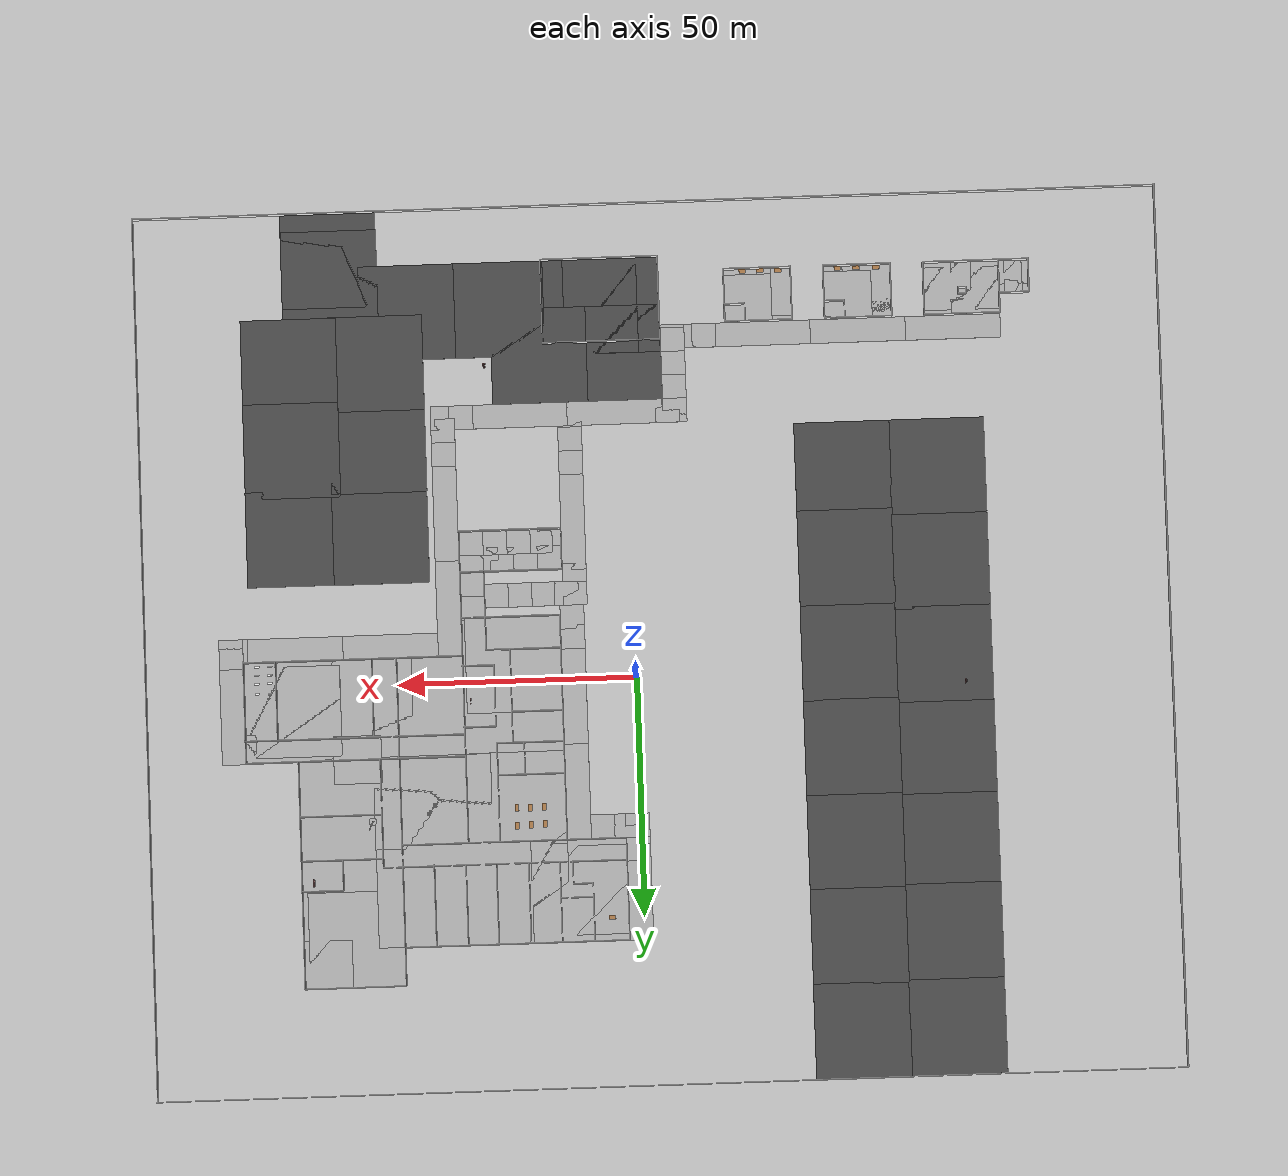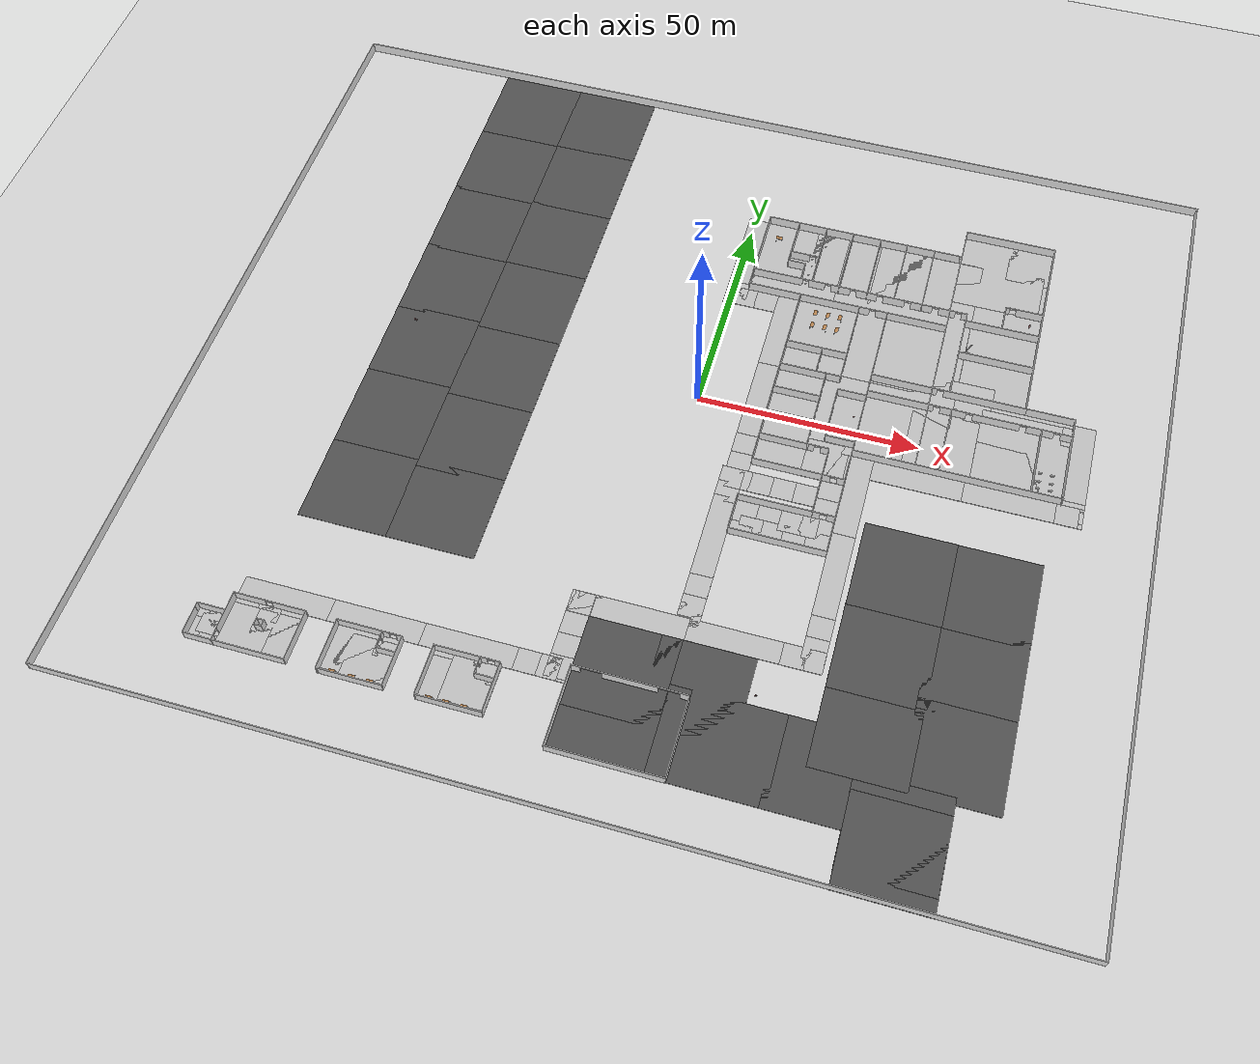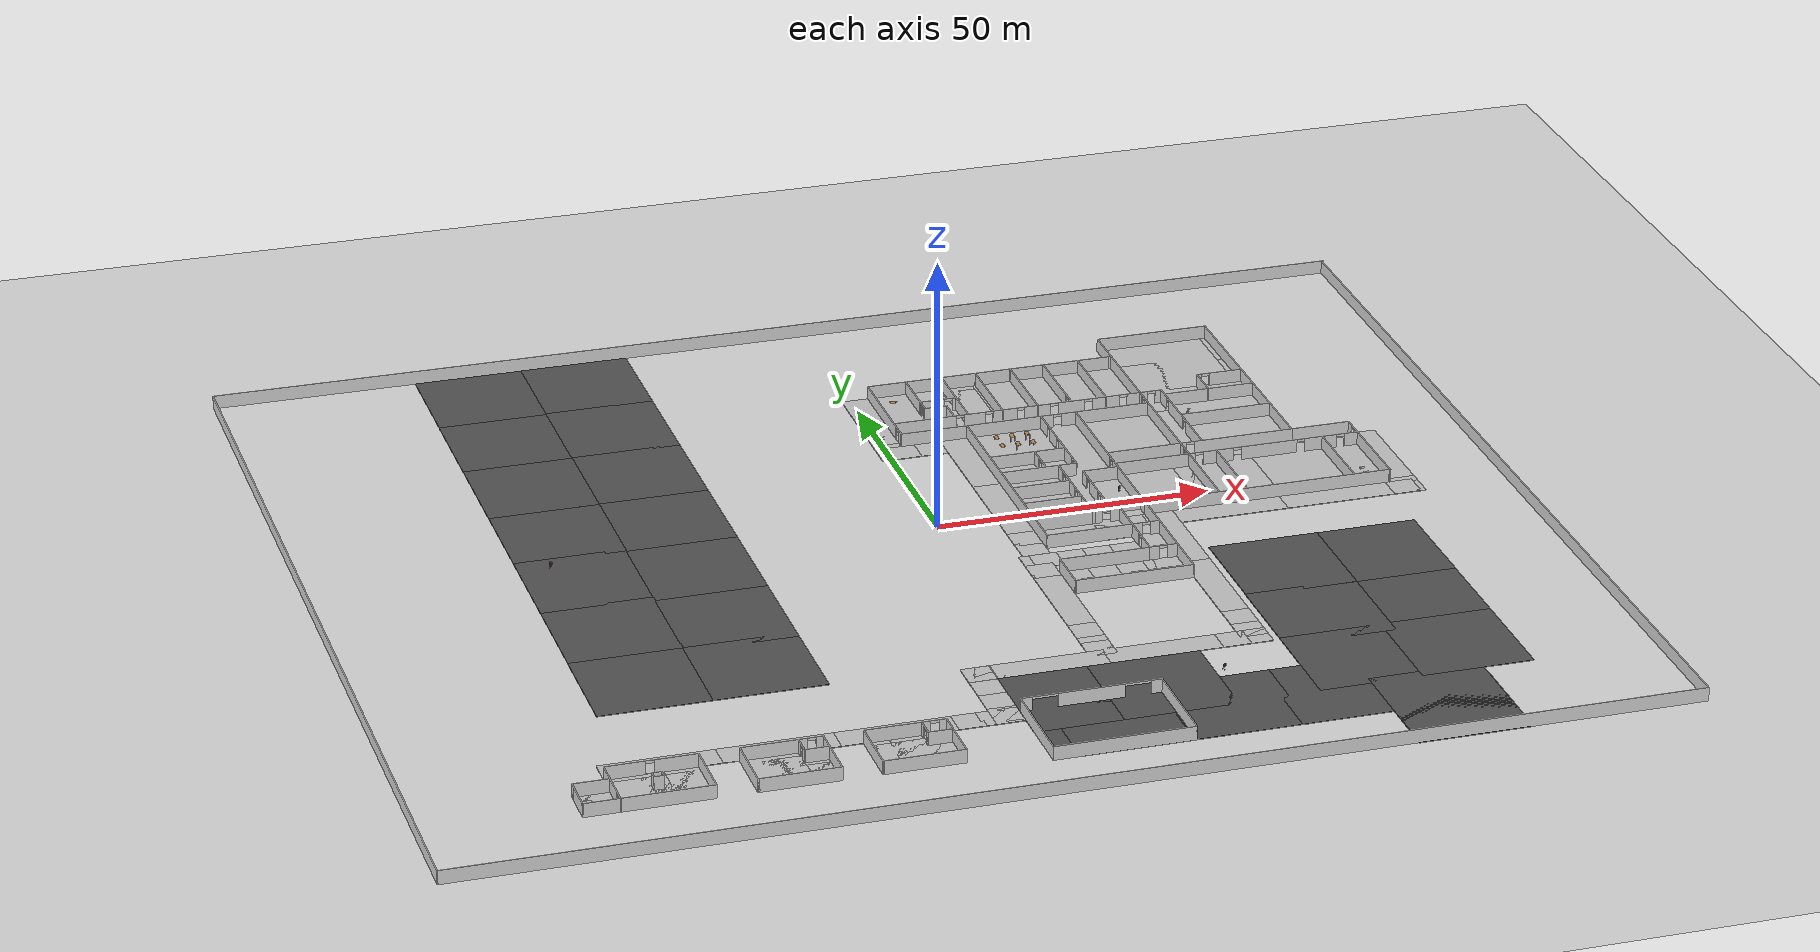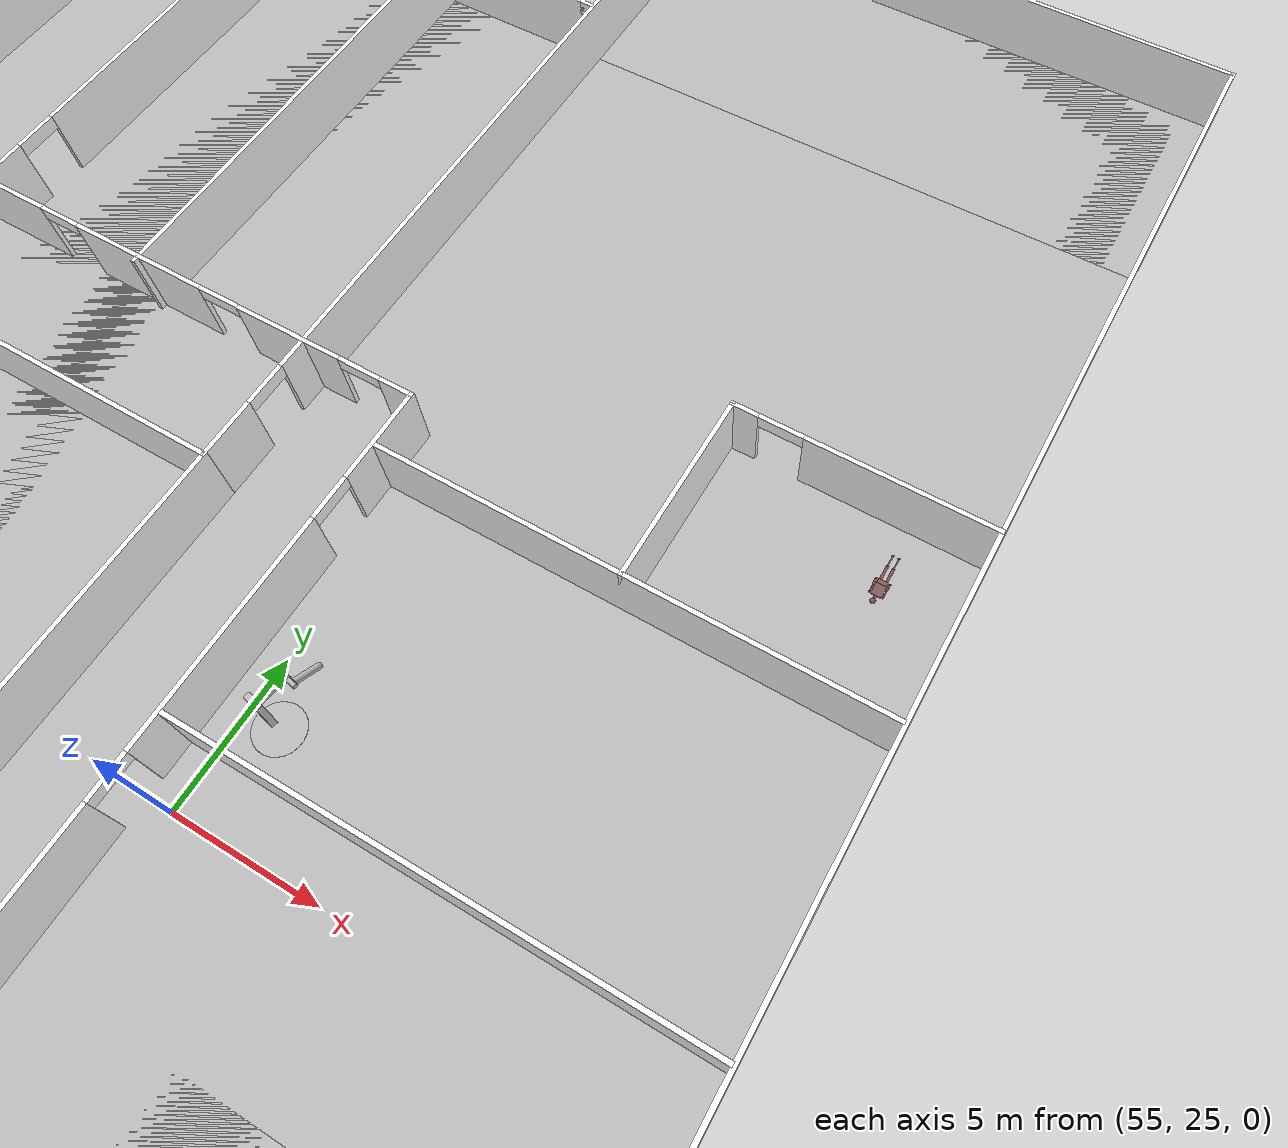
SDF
<sdf version="1.6">
 <world name="default">
  <model name="victim175_1">
   <static>1</static>
   <self_collide>1</self_collide>
   <link name="head">
    <pose>0 0 1.625 0 -0 0</pose>
    <visual name="visual">
     <geometry><sphere><radius>0.1</radius></sphere></geometry>
     <material>
      <emissive>0.5 0.35 0.35 1</emissive>
      <ambient>0.5 0.35 0.35 1</ambient>
      <diffuse>0.5 0.35 0.35 1</diffuse>
      <specular>0 0 0 0</specular>
     </material>
    </visual>
    <collision name="collision"><geometry><sphere><radius>0.1</radius></sphere></geometry></collision>
    <visual name="visual_nose">
     <pose>0 -0.1 -0.01 0 -0 0</pose>
     <geometry><sphere><radius>0.01</radius></sphere></geometry>
     <material>
      <emissive>0.5 0.35 0.35 1</emissive>
      <ambient>0.5 0.35 0.35 1</ambient>
      <diffuse>0.5 0.35 0.35 1</diffuse>
      <specular>0 0 0 0</specular>
     </material>
    </visual>
    <visual name="visual_rEye">
     <pose>-0.05 -0.08 0.02 0 -0 0</pose>
     <geometry><sphere><radius>0.01</radius></sphere></geometry>
     <material>
      <script><uri>file://media/materials/scripts/gazebo.material</uri><name>Gazebo/Black</name></script>
     </material>
    </visual>
    <visual name="visual_lEye">
     <pose>0.05 -0.08 0.02 0 -0 0</pose>
     <geometry><sphere><radius>0.01</radius></sphere></geometry>
     <material>
      <script><uri>file://media/materials/scripts/gazebo.material</uri><name>Gazebo/Black</name></script>
     </material>
    </visual>
    <self_collide>1</self_collide>
   </link>
   <link name="neck">
    <pose>0 0.02 1.49 0 -0 0</pose>
    <visual name="visual">
     <geometry><cylinder><radius>0.05</radius><length>0.15</length></cylinder></geometry>
     <material>
      <emissive>0.5 0.35 0.35 1</emissive>
      <ambient>0.5 0.35 0.35 1</ambient>
      <diffuse>0.5 0.35 0.35 1</diffuse>
      <specular>0 0 0 0</specular>
     </material>
    </visual>
    <collision name="collision">
     <geometry><cylinder><radius>0.05</radius><length>0.15</length></cylinder></geometry>
    </collision>
    <self_collide>1</self_collide>
   </link>
   <joint name="neck_head" type="revolute">
    <pose>0 0.02 -0.075 0 -0 0</pose>
    <child>head</child>
    <parent>neck</parent>
    <axis>
     <xyz>0 0 -1</xyz>
     <limit><lower>-1.7</lower><upper>1.7</upper></limit>
     <dynamics>
      <friction>0.01</friction>
      <spring_reference>0</spring_reference>
      <spring_stiffness>0</spring_stiffness>
     </dynamics>
     <use_parent_model_frame>0</use_parent_model_frame>
    </axis>
   </joint>
   <link name="body">
    <pose>0 0 1.255 0 -0 0</pose>
    <visual name="visual">
     <geometry><box><size>0.34 0.16 0.4</size></box></geometry>
     <material>
      <emissive>0.5 0.35 0.35 1</emissive>
      <ambient>0.5 0.35 0.35 1</ambient>
      <diffuse>0.5 0.35 0.35 1</diffuse>
      <specular>0 0 0 0</specular>
     </material>
    </visual>
    <collision name="collision"><geometry><box><size>0.34 0.16 0.4</size></box></geometry></collision>
    <self_collide>1</self_collide>
   </link>
   <joint name="body_neck" type="revolute">
    <pose>0 0.06 -0.075 0 -0 0</pose>
    <child>neck</child>
    <parent>body</parent>
    <axis>
     <xyz>1 0 0</xyz>
     <limit><lower>-0.2</lower><upper>1</upper></limit>
     <dynamics>
      <friction>0.01</friction>
      <spring_reference>0</spring_reference>
      <spring_stiffness>0</spring_stiffness>
     </dynamics>
     <use_parent_model_frame>0</use_parent_model_frame>
    </axis>
   </joint>
   <link name="waist">
    <pose>0 0 1.005 0 -0 0</pose>
    <visual name="visual">
     <pose>0 0 -0.025 0 -0 0</pose>
     <geometry><box><size>0.31 0.16 0.15</size></box></geometry>
     <material>
      <emissive>0.5 0.35 0.35 1</emissive>
      <ambient>0.5 0.35 0.35 1</ambient>
      <diffuse>0.5 0.35 0.35 1</diffuse>
      <specular>0 0 0 0</specular>
     </material>
    </visual>
    <collision name="collision"><geometry><box><size>0.31 0.16 0.1</size></box></geometry></collision>
    <visual name="visual2">
     <pose>0 0 0.05 3.14159 1.57079 3.14159</pose>
     <geometry><cylinder><radius>0.08</radius><length>0.31</length></cylinder></geometry>
     <material>
      <emissive>0.5 0.35 0.35 1</emissive>
      <ambient>0.5 0.35 0.35 1</ambient>
      <diffuse>0.5 0.35 0.35 1</diffuse>
      <specular>0 0 0 0</specular>
     </material>
    </visual>
    <collision name="collision2">
     <pose>0 0 0.05 3.14159 1.57079 3.14159</pose>
     <geometry><cylinder><radius>0.08</radius><length>0.31</length></cylinder></geometry>
    </collision>
    <self_collide>1</self_collide>
   </link>
   <joint name="body_waist" type="revolute">
    <pose>0 0 0.05 0 -0 0</pose>
    <child>waist</child>
    <parent>body</parent>
    <axis>
     <xyz>-1 0 0</xyz>
     <limit><lower>0</lower><upper>0</upper></limit>
     <dynamics>
      <friction>0.01</friction>
      <spring_reference>0</spring_reference>
      <spring_stiffness>0</spring_stiffness>
     </dynamics>
     <use_parent_model_frame>0</use_parent_model_frame>
    </axis>
   </joint>
   <link name="rHand">
    <pose>-0.22 0 0.84 0 -0 0</pose>
    <visual name="visual">
     <geometry><box><size>0.09 0.02 0.18</size></box></geometry>
     <material>
      <emissive>0.5 0.35 0.35 1</emissive>
      <ambient>0.5 0.35 0.35 1</ambient>
      <diffuse>0.5 0.35 0.35 1</diffuse>
      <specular>0 0 0 0</specular>
     </material>
    </visual>
    <collision name="collision"><geometry><box><size>0.09 0.02 0.18</size></box></geometry></collision>
    <visual name="visual2">
     <pose>0.02 0 0 0 -0 0</pose>
     <geometry><box><size>0.12 0.02 0.09</size></box></geometry>
     <material>
      <emissive>0.5 0.35 0.35 1</emissive>
      <ambient>0.5 0.35 0.35 1</ambient>
      <diffuse>0.5 0.35 0.35 1</diffuse>
      <specular>0 0 0 0</specular>
     </material>
    </visual>
    <collision name="collision2">
     <pose>0.02 0 0 0 -0 0</pose>
     <geometry><box><size>0.12 0.02 0.09</size></box></geometry>
    </collision>
    <self_collide>1</self_collide>
   </link>
   <link name="lHand">
    <pose>0.22 0 0.84 0 -0 0</pose>
    <visual name="visual">
     <geometry><box><size>0.09 0.02 0.18</size></box></geometry>
     <material>
      <emissive>0.5 0.35 0.35 1</emissive>
      <ambient>0.5 0.35 0.35 1</ambient>
      <diffuse>0.5 0.35 0.35 1</diffuse>
      <specular>0 0 0 0</specular>
     </material>
    </visual>
    <collision name="collision"><geometry><box><size>0.09 0.02 0.18</size></box></geometry></collision>
    <visual name="visual2">
     <pose>-0.02 0 0 0 -0 0</pose>
     <geometry><box><size>0.12 0.02 0.09</size></box></geometry>
     <material>
      <emissive>0.5 0.35 0.35 1</emissive>
      <ambient>0.5 0.35 0.35 1</ambient>
      <diffuse>0.5 0.35 0.35 1</diffuse>
      <specular>0 0 0 0</specular>
     </material>
    </visual>
    <collision name="collision2">
     <pose>-0.02 0 0 0 -0 0</pose>
     <geometry><box><size>0.12 0.02 0.09</size></box></geometry>
    </collision>
    <self_collide>1</self_collide>
   </link>
   <link name="rFoot">
    <pose>-0.1 -0.095 0.02 0 -0 0</pose>
    <visual name="visual">
     <geometry><box><size>0.1 0.27 0.04</size></box></geometry>
     <material>
      <emissive>0.5 0.35 0.35 1</emissive>
      <ambient>0.5 0.35 0.35 1</ambient>
      <diffuse>0.5 0.35 0.35 1</diffuse>
      <specular>0 0 0 0</specular>
     </material>
    </visual>
    <collision name="collision"><geometry><box><size>0.1 0.27 0.04</size></box></geometry></collision>
    <self_collide>1</self_collide>
   </link>
   <link name="lFoot">
    <pose>0.1 -0.095 0.02 0 -0 0</pose>
    <visual name="visual">
     <geometry><box><size>0.1 0.27 0.04</size></box></geometry>
     <material>
      <emissive>0.5 0.35 0.35 1</emissive>
      <ambient>0.5 0.35 0.35 1</ambient>
      <diffuse>0.5 0.35 0.35 1</diffuse>
      <specular>0 0 0 0</specular>
     </material>
    </visual>
    <collision name="collision"><geometry><box><size>0.1 0.27 0.04</size></box></geometry></collision>
    <self_collide>1</self_collide>
   </link>
   <link name="rLeg2">
    <pose>-0.1 0 0.23 0 -0 0</pose>
    <visual name="visual">
     <geometry><cylinder><radius>0.04</radius><length>0.38</length></cylinder></geometry>
     <material>
      <emissive>0.5 0.35 0.35 1</emissive>
      <ambient>0.5 0.35 0.35 1</ambient>
      <diffuse>0.5 0.35 0.35 1</diffuse>
      <specular>0 0 0 0</specular>
     </material>
    </visual>
    <collision name="collision">
     <geometry><cylinder><radius>0.04</radius><length>0.38</length></cylinder></geometry>
    </collision>
    <visual name="visual2">
     <pose>0 0 -0.19 0 -0 0</pose>
     <geometry><sphere><radius>0.04</radius></sphere></geometry>
     <material>
      <emissive>0.5 0.35 0.35 1</emissive>
      <ambient>0.5 0.35 0.35 1</ambient>
      <diffuse>0.5 0.35 0.35 1</diffuse>
      <specular>0 0 0 0</specular>
     </material>
    </visual>
    <collision name="collision2">
     <pose>0 0 -0.19 0 -0 0</pose>
     <geometry><sphere><radius>0.04</radius></sphere></geometry>
    </collision>
    <self_collide>1</self_collide>
   </link>
   <link name="lLeg2">
    <pose>0.1 0 0.23 0 -0 0</pose>
    <visual name="visual">
     <geometry><cylinder><radius>0.04</radius><length>0.38</length></cylinder></geometry>
     <material>
      <emissive>0.5 0.35 0.35 1</emissive>
      <ambient>0.5 0.35 0.35 1</ambient>
      <diffuse>0.5 0.35 0.35 1</diffuse>
      <specular>0 0 0 0</specular>
     </material>
    </visual>
    <collision name="collision">
     <geometry><cylinder><radius>0.04</radius><length>0.38</length></cylinder></geometry>
    </collision>
    <visual name="visual2">
     <pose>0 0 -0.19 0 -0 0</pose>
     <geometry><sphere><radius>0.04</radius></sphere></geometry>
     <material>
      <emissive>0.5 0.35 0.35 1</emissive>
      <ambient>0.5 0.35 0.35 1</ambient>
      <diffuse>0.5 0.35 0.35 1</diffuse>
      <specular>0 0 0 0</specular>
     </material>
    </visual>
    <collision name="collision2">
     <pose>0 0 -0.19 0 -0 0</pose>
     <geometry><sphere><radius>0.04</radius></sphere></geometry>
    </collision>
    <self_collide>1</self_collide>
   </link>
   <joint name="rLeg2_rFoot" type="revolute">
    <pose>0 0.095 0.02 0 -0 0</pose>
    <child>rFoot</child>
    <parent>rLeg2</parent>
    <axis>
     <xyz>1 0 0</xyz>
     <limit><lower>0</lower><upper>0</upper></limit>
     <dynamics>
      <friction>0.01</friction>
      <spring_reference>0</spring_reference>
      <spring_stiffness>0</spring_stiffness>
     </dynamics>
     <use_parent_model_frame>0</use_parent_model_frame>
    </axis>
   </joint>
   <joint name="lLeg2_lFoot" type="revolute">
    <pose>0 0.095 0.02 0 -0 0</pose>
    <child>lFoot</child>
    <parent>lLeg2</parent>
    <axis>
     <xyz>1 0 0</xyz>
     <limit><lower>0</lower><upper>0</upper></limit>
     <dynamics>
      <friction>0.01</friction>
      <spring_reference>0</spring_reference>
      <spring_stiffness>0</spring_stiffness>
     </dynamics>
     <use_parent_model_frame>0</use_parent_model_frame>
    </axis>
   </joint>
   <link name="rLeg1">
    <pose>-0.1 0 0.66 0 -0 0</pose>
    <visual name="visual">
     <geometry><cylinder><radius>0.055</radius><length>0.48</length></cylinder></geometry>
     <material>
      <emissive>0.5 0.35 0.35 1</emissive>
      <ambient>0.5 0.35 0.35 1</ambient>
      <diffuse>0.5 0.35 0.35 1</diffuse>
      <specular>0 0 0 0</specular>
     </material>
    </visual>
    <collision name="collision">
     <geometry><cylinder><radius>0.055</radius><length>0.48</length></cylinder></geometry>
    </collision>
    <visual name="visual2">
     <pose>0 0 -0.24 0 -0 0</pose>
     <geometry><sphere><radius>0.055</radius></sphere></geometry>
     <material>
      <emissive>0.5 0.35 0.35 1</emissive>
      <ambient>0.5 0.35 0.35 1</ambient>
      <diffuse>0.5 0.35 0.35 1</diffuse>
      <specular>0 0 0 0</specular>
     </material>
    </visual>
    <collision name="collision2">
     <pose>0 0 -0.24 0 -0 0</pose>
     <geometry><sphere><radius>0.055</radius></sphere></geometry>
    </collision>
    <visual name="visual3">
     <pose>0 0 0.24 0 -0 0</pose>
     <geometry><sphere><radius>0.055</radius></sphere></geometry>
     <material>
      <emissive>0.5 0.35 0.35 1</emissive>
      <ambient>0.5 0.35 0.35 1</ambient>
      <diffuse>0.5 0.35 0.35 1</diffuse>
      <specular>0 0 0 0</specular>
     </material>
    </visual>
    <collision name="collision3">
     <pose>0 0 0.24 0 -0 0</pose>
     <geometry><sphere><radius>0.055</radius></sphere></geometry>
    </collision>
    <self_collide>1</self_collide>
   </link>
   <link name="lLeg1">
    <pose>0.1 0 0.66 0 -0 0</pose>
    <visual name="visual">
     <geometry><cylinder><radius>0.055</radius><length>0.48</length></cylinder></geometry>
     <material>
      <emissive>0.5 0.35 0.35 1</emissive>
      <ambient>0.5 0.35 0.35 1</ambient>
      <diffuse>0.5 0.35 0.35 1</diffuse>
      <specular>0 0 0 0</specular>
     </material>
    </visual>
    <collision name="collision">
     <geometry><cylinder><radius>0.055</radius><length>0.48</length></cylinder></geometry>
    </collision>
    <visual name="visual2">
     <pose>0 0 -0.24 0 -0 0</pose>
     <geometry><sphere><radius>0.055</radius></sphere></geometry>
     <material>
      <emissive>0.5 0.35 0.35 1</emissive>
      <ambient>0.5 0.35 0.35 1</ambient>
      <diffuse>0.5 0.35 0.35 1</diffuse>
      <specular>0 0 0 0</specular>
     </material>
    </visual>
    <collision name="collision2">
     <pose>0 0 -0.24 0 -0 0</pose>
     <geometry><sphere><radius>0.055</radius></sphere></geometry>
    </collision>
    <visual name="visual3">
     <pose>0 0 0.24 0 -0 0</pose>
     <geometry><sphere><radius>0.055</radius></sphere></geometry>
     <material>
      <emissive>0.5 0.35 0.35 1</emissive>
      <ambient>0.5 0.35 0.35 1</ambient>
      <diffuse>0.5 0.35 0.35 1</diffuse>
      <specular>0 0 0 0</specular>
     </material>
    </visual>
    <collision name="collision3">
     <pose>0 0 0.24 0 -0 0</pose>
     <geometry><sphere><radius>0.055</radius></sphere></geometry>
    </collision>
    <self_collide>1</self_collide>
   </link>
   <joint name="rLeg1_rLeg2" type="revolute">
    <pose>0 0 0.19 0 -0 0</pose>
    <child>rLeg2</child>
    <parent>rLeg1</parent>
    <axis>
     <xyz>1 0 0</xyz>
     <limit><lower>0</lower><upper>0</upper></limit>
     <dynamics>
      <friction>0.01</friction>
      <spring_reference>0</spring_reference>
      <spring_stiffness>0</spring_stiffness>
     </dynamics>
     <use_parent_model_frame>0</use_parent_model_frame>
    </axis>
   </joint>
   <joint name="lLeg1_lLeg2" type="revolute">
    <pose>0 0 0.19 0 -0 0</pose>
    <child>lLeg2</child>
    <parent>lLeg1</parent>
    <axis>
     <xyz>1 0 0</xyz>
     <limit><lower>0</lower><upper>0</upper></limit>
     <dynamics>
      <friction>0.01</friction>
      <spring_reference>0</spring_reference>
      <spring_stiffness>0</spring_stiffness>
     </dynamics>
     <use_parent_model_frame>0</use_parent_model_frame>
    </axis>
   </joint>
   <link name="rButt">
    <pose>-0.1 0 0.9275 0 -0 0</pose>
    <visual name="visual">
     <geometry><cylinder><radius>0.055</radius><length>0.055</length></cylinder></geometry>
     <material>
      <emissive>0.5 0.35 0.35 1</emissive>
      <ambient>0.5 0.35 0.35 1</ambient>
      <diffuse>0.5 0.35 0.35 1</diffuse>
      <specular>0 0 0 0</specular>
     </material>
    </visual>
    <collision name="collision">
     <geometry><cylinder><radius>0.055</radius><length>0.055</length></cylinder></geometry>
    </collision>
    <self_collide>1</self_collide>
   </link>
   <link name="lButt">
    <pose>0.1 0 0.9275 0 -0 0</pose>
    <visual name="visual">
     <geometry><cylinder><radius>0.055</radius><length>0.055</length></cylinder></geometry>
     <material>
      <emissive>0.5 0.35 0.35 1</emissive>
      <ambient>0.5 0.35 0.35 1</ambient>
      <diffuse>0.5 0.35 0.35 1</diffuse>
      <specular>0 0 0 0</specular>
     </material>
    </visual>
    <collision name="collision">
     <geometry><cylinder><radius>0.055</radius><length>0.055</length></cylinder></geometry>
    </collision>
    <self_collide>1</self_collide>
   </link>
   <joint name="rButt_rLeg1" type="revolute">
    <pose>0 0 0.24 0 -0 0</pose>
    <child>rLeg1</child>
    <parent>rButt</parent>
    <axis>
     <xyz>1 0 0</xyz>
     <limit><lower>0</lower><upper>0</upper></limit>
     <dynamics>
      <friction>0.01</friction>
      <spring_reference>0</spring_reference>
      <spring_stiffness>0</spring_stiffness>
     </dynamics>
     <use_parent_model_frame>0</use_parent_model_frame>
    </axis>
   </joint>
   <joint name="lButt_lLeg1" type="revolute">
    <pose>0 0 0.24 0 -0 0</pose>
    <child>lLeg1</child>
    <parent>lButt</parent>
    <axis>
     <xyz>1 0 0</xyz>
     <limit><lower>0</lower><upper>0</upper></limit>
     <dynamics>
      <friction>0.01</friction>
      <spring_reference>0</spring_reference>
      <spring_stiffness>0</spring_stiffness>
     </dynamics>
     <use_parent_model_frame>0</use_parent_model_frame>
    </axis>
   </joint>
   <joint name="waist_rButt" type="revolute">
    <child>rButt</child>
    <parent>waist</parent>
    <axis>
     <xyz>0 0 -1</xyz>
     <limit><lower>-1</lower><upper>1</upper></limit>
     <dynamics>
      <friction>0.01</friction>
      <spring_reference>0</spring_reference>
      <spring_stiffness>0</spring_stiffness>
     </dynamics>
     <use_parent_model_frame>0</use_parent_model_frame>
    </axis>
   </joint>
   <joint name="waist_lButt" type="revolute">
    <child>lButt</child>
    <parent>waist</parent>
    <axis>
     <xyz>0 0 1</xyz>
     <limit><lower>-1</lower><upper>1</upper></limit>
     <dynamics>
      <friction>0.01</friction>
      <spring_reference>0</spring_reference>
      <spring_stiffness>0</spring_stiffness>
     </dynamics>
     <use_parent_model_frame>0</use_parent_model_frame>
    </axis>
   </joint>
   <link name="rShoulder">
    <pose>-0.195 0 1.4 0 -0 0</pose>
    <visual name="visual">
     <pose>0 0 0 3.14159 1.57079 3.14159</pose>
     <geometry><cylinder><radius>0.05</radius><length>0.05</length></cylinder></geometry>
     <material>
      <emissive>0.5 0.35 0.35 1</emissive>
      <ambient>0.5 0.35 0.35 1</ambient>
      <diffuse>0.5 0.35 0.35 1</diffuse>
      <specular>0 0 0 0</specular>
     </material>
    </visual>
    <collision name="collision">
     <pose>0 0 0 3.14159 1.57079 3.14159</pose>
     <geometry><cylinder><radius>0.05</radius><length>0.05</length></cylinder></geometry>
    </collision>
    <self_collide>1</self_collide>
   </link>
   <link name="lShoulder">
    <pose>0.195 0 1.4 0 -0 0</pose>
    <visual name="visual">
     <pose>0 0 0 3.14159 1.57079 3.14159</pose>
     <geometry><cylinder><radius>0.05</radius><length>0.05</length></cylinder></geometry>
     <material>
      <emissive>0.5 0.35 0.35 1</emissive>
      <ambient>0.5 0.35 0.35 1</ambient>
      <diffuse>0.5 0.35 0.35 1</diffuse>
      <specular>0 0 0 0</specular>
     </material>
    </visual>
    <collision name="collision">
     <pose>0 0 0 3.14159 1.57079 3.14159</pose>
     <geometry><cylinder><radius>0.05</radius><length>0.05</length></cylinder></geometry>
    </collision>
    <self_collide>1</self_collide>
   </link>
   <joint name="body_rShoulder" type="revolute">
    <child>rShoulder</child>
    <parent>body</parent>
    <axis>
     <xyz>-1 0 0</xyz>
     <limit><lower>-1.5708</lower><upper>3.2</upper></limit>
     <dynamics>
      <friction>0.01</friction>
      <spring_reference>0</spring_reference>
      <spring_stiffness>0</spring_stiffness>
     </dynamics>
     <use_parent_model_frame>0</use_parent_model_frame>
    </axis>
   </joint>
   <joint name="body_lShoulder" type="revolute">
    <child>lShoulder</child>
    <parent>body</parent>
    <axis>
     <xyz>1 0 0</xyz>
     <limit><lower>-1.5708</lower><upper>3.2</upper></limit>
     <dynamics>
      <friction>0.01</friction>
      <spring_reference>0</spring_reference>
      <spring_stiffness>0</spring_stiffness>
     </dynamics>
     <use_parent_model_frame>0</use_parent_model_frame>
    </axis>
   </joint>
   <link name="rArm1U">
    <pose>-0.22 0 1.3375 0 -0 0</pose>
    <visual name="visual">
     <geometry><cylinder><radius>0.04</radius><length>0.125</length></cylinder></geometry>
     <material>
      <emissive>0.5 0.35 0.35 1</emissive>
      <ambient>0.5 0.35 0.35 1</ambient>
      <diffuse>0.5 0.35 0.35 1</diffuse>
      <specular>0 0 0 0</specular>
     </material>
    </visual>
    <collision name="collision">
     <geometry><cylinder><radius>0.04</radius><length>0.125</length></cylinder></geometry>
    </collision>
    <visual name="visual2">
     <pose>0 0 0.0625 0 -0 0</pose>
     <geometry><sphere><radius>0.05</radius></sphere></geometry>
     <material>
      <emissive>0.5 0.35 0.35 1</emissive>
      <ambient>0.5 0.35 0.35 1</ambient>
      <diffuse>0.5 0.35 0.35 1</diffuse>
      <specular>0 0 0 0</specular>
     </material>
    </visual>
    <collision name="collision2">
     <pose>0 0 0.0625 0 -0 0</pose>
     <geometry><sphere><radius>0.05</radius></sphere></geometry>
    </collision>
    <self_collide>1</self_collide>
   </link>
   <link name="rArm1L">
    <pose>-0.22 0 1.2125 0 -0 0</pose>
    <visual name="visual">
     <geometry><cylinder><radius>0.04</radius><length>0.125</length></cylinder></geometry>
     <material>
      <emissive>0.5 0.35 0.35 1</emissive>
      <ambient>0.5 0.35 0.35 1</ambient>
      <diffuse>0.5 0.35 0.35 1</diffuse>
      <specular>0 0 0 0</specular>
     </material>
    </visual>
    <collision name="collision">
     <geometry><cylinder><radius>0.04</radius><length>0.125</length></cylinder></geometry>
    </collision>
    <visual name="visual2">
     <pose>0 0 -0.0625 0 -0 0</pose>
     <geometry><sphere><radius>0.05</radius></sphere></geometry>
     <material>
      <emissive>0.5 0.35 0.35 1</emissive>
      <ambient>0.5 0.35 0.35 1</ambient>
      <diffuse>0.5 0.35 0.35 1</diffuse>
      <specular>0 0 0 0</specular>
     </material>
    </visual>
    <collision name="collision2">
     <pose>0 0 -0.0625 0 -0 0</pose>
     <geometry><sphere><radius>0.05</radius></sphere></geometry>
    </collision>
    <self_collide>1</self_collide>
   </link>
   <joint name="rArm1U_rArm1L" type="revolute">
    <pose>0 0 0.0625 0 -0 0</pose>
    <child>rArm1L</child>
    <parent>rArm1U</parent>
    <axis>
     <xyz>0 0 -1</xyz>
     <limit><lower>-1.5708</lower><upper>1.5708</upper></limit>
     <dynamics>
      <friction>0.01</friction>
      <spring_reference>0</spring_reference>
      <spring_stiffness>0</spring_stiffness>
     </dynamics>
     <use_parent_model_frame>0</use_parent_model_frame>
    </axis>
   </joint>
   <link name="lArm1U">
    <pose>0.22 0 1.3375 0 -0 0</pose>
    <visual name="visual">
     <geometry><cylinder><radius>0.04</radius><length>0.125</length></cylinder></geometry>
     <material>
      <emissive>0.5 0.35 0.35 1</emissive>
      <ambient>0.5 0.35 0.35 1</ambient>
      <diffuse>0.5 0.35 0.35 1</diffuse>
      <specular>0 0 0 0</specular>
     </material>
    </visual>
    <collision name="collision">
     <geometry><cylinder><radius>0.04</radius><length>0.125</length></cylinder></geometry>
    </collision>
    <visual name="visual2">
     <pose>0 0 0.0625 0 -0 0</pose>
     <geometry><sphere><radius>0.05</radius></sphere></geometry>
     <material>
      <emissive>0.5 0.35 0.35 1</emissive>
      <ambient>0.5 0.35 0.35 1</ambient>
      <diffuse>0.5 0.35 0.35 1</diffuse>
      <specular>0 0 0 0</specular>
     </material>
    </visual>
    <collision name="collision2">
     <pose>0 0 0.0625 0 -0 0</pose>
     <geometry><sphere><radius>0.05</radius></sphere></geometry>
    </collision>
    <self_collide>1</self_collide>
   </link>
   <link name="lArm1L">
    <pose>0.22 0 1.2125 0 -0 0</pose>
    <visual name="visual">
     <geometry><cylinder><radius>0.04</radius><length>0.125</length></cylinder></geometry>
     <material>
      <emissive>0.5 0.35 0.35 1</emissive>
      <ambient>0.5 0.35 0.35 1</ambient>
      <diffuse>0.5 0.35 0.35 1</diffuse>
      <specular>0 0 0 0</specular>
     </material>
    </visual>
    <collision name="collision">
     <geometry><cylinder><radius>0.04</radius><length>0.125</length></cylinder></geometry>
    </collision>
    <visual name="visual2">
     <pose>0 0 -0.0625 0 -0 0</pose>
     <geometry><sphere><radius>0.05</radius></sphere></geometry>
     <material>
      <emissive>0.5 0.35 0.35 1</emissive>
      <ambient>0.5 0.35 0.35 1</ambient>
      <diffuse>0.5 0.35 0.35 1</diffuse>
      <specular>0 0 0 0</specular>
     </material>
    </visual>
    <collision name="collision2">
     <pose>0 0 -0.0625 0 -0 0</pose>
     <geometry><sphere><radius>0.05</radius></sphere></geometry>
    </collision>
    <self_collide>1</self_collide>
   </link>
   <joint name="lArm1U_lArm1L" type="revolute">
    <pose>0 0 0.0625 0 -0 0</pose>
    <child>lArm1L</child>
    <parent>lArm1U</parent>
    <axis>
     <xyz>0 0 1</xyz>
     <limit><lower>-1.5708</lower><upper>1.5708</upper></limit>
     <dynamics>
      <friction>0.01</friction>
      <spring_reference>0</spring_reference>
      <spring_stiffness>0</spring_stiffness>
     </dynamics>
     <use_parent_model_frame>0</use_parent_model_frame>
    </axis>
   </joint>
   <joint name="rShoulder_rArm1" type="revolute">
    <pose>0 0 0.0625 0 -0 0</pose>
    <child>rArm1U</child>
    <parent>rShoulder</parent>
    <axis>
     <xyz>0 -1 0</xyz>
     <limit><lower>-1.5708</lower><upper>3.2</upper></limit>
     <dynamics>
      <friction>0.01</friction>
      <spring_reference>0</spring_reference>
      <spring_stiffness>0</spring_stiffness>
     </dynamics>
     <use_parent_model_frame>0</use_parent_model_frame>
    </axis>
   </joint>
   <joint name="lShoulder_lArm1" type="revolute">
    <pose>0 0 0.0625 0 -0 0</pose>
    <child>lArm1U</child>
    <parent>lShoulder</parent>
    <axis>
     <xyz>0 1 0</xyz>
     <limit><lower>-1.5708</lower><upper>3.2</upper></limit>
     <dynamics>
      <friction>0.01</friction>
      <spring_reference>0</spring_reference>
      <spring_stiffness>0</spring_stiffness>
     </dynamics>
     <use_parent_model_frame>0</use_parent_model_frame>
    </axis>
   </joint>
   <link name="rArm2U">
    <pose>-0.22 0 1.095 0 -0 0</pose>
    <visual name="visual">
     <geometry><cylinder><radius>0.05</radius><length>0.11</length></cylinder></geometry>
     <material>
      <emissive>0.5 0.35 0.35 1</emissive>
      <ambient>0.5 0.35 0.35 1</ambient>
      <diffuse>0.5 0.35 0.35 1</diffuse>
      <specular>0 0 0 0</specular>
     </material>
    </visual>
    <collision name="collision">
     <geometry><cylinder><radius>0.05</radius><length>0.11</length></cylinder></geometry>
    </collision>
    <self_collide>1</self_collide>
   </link>
   <link name="rArm2L">
    <pose>-0.22 0 0.985 0 -0 0</pose>
    <visual name="visual">
     <geometry><cylinder><radius>0.05</radius><length>0.11</length></cylinder></geometry>
     <material>
      <emissive>0.5 0.35 0.35 1</emissive>
      <ambient>0.5 0.35 0.35 1</ambient>
      <diffuse>0.5 0.35 0.35 1</diffuse>
      <specular>0 0 0 0</specular>
     </material>
    </visual>
    <collision name="collision">
     <geometry><cylinder><radius>0.05</radius><length>0.11</length></cylinder></geometry>
    </collision>
    <visual name="visual2">
     <pose>0 0 -0.055 0 -0 0</pose>
     <geometry><sphere><radius>0.05</radius></sphere></geometry>
     <material>
      <emissive>0.5 0.35 0.35 1</emissive>
      <ambient>0.5 0.35 0.35 1</ambient>
      <diffuse>0.5 0.35 0.35 1</diffuse>
      <specular>0 0 0 0</specular>
     </material>
    </visual>
    <collision name="collision2">
     <pose>0 0 -0.055 0 -0 0</pose>
     <geometry><sphere><radius>0.05</radius></sphere></geometry>
    </collision>
    <self_collide>1</self_collide>
   </link>
   <joint name="rArm2U_rArm2L" type="revolute">
    <pose>0 0 0.055 0 -0 0</pose>
    <child>rArm2L</child>
    <parent>rArm2U</parent>
    <axis>
     <xyz>0 0 -1</xyz>
     <limit><lower>-1.5708</lower><upper>1.5708</upper></limit>
     <dynamics>
      <friction>0.01</friction>
      <spring_reference>0</spring_reference>
      <spring_stiffness>0</spring_stiffness>
     </dynamics>
     <use_parent_model_frame>0</use_parent_model_frame>
    </axis>
   </joint>
   <link name="lArm2U">
    <pose>0.22 0 1.095 0 -0 0</pose>
    <visual name="visual">
     <geometry><cylinder><radius>0.05</radius><length>0.11</length></cylinder></geometry>
     <material>
      <emissive>0.5 0.35 0.35 1</emissive>
      <ambient>0.5 0.35 0.35 1</ambient>
      <diffuse>0.5 0.35 0.35 1</diffuse>
      <specular>0 0 0 0</specular>
     </material>
    </visual>
    <collision name="collision">
     <geometry><cylinder><radius>0.05</radius><length>0.11</length></cylinder></geometry>
    </collision>
    <self_collide>1</self_collide>
   </link>
   <link name="lArm2L">
    <pose>0.22 0 0.985 0 -0 0</pose>
    <visual name="visual">
     <geometry><cylinder><radius>0.05</radius><length>0.11</length></cylinder></geometry>
     <material>
      <emissive>0.5 0.35 0.35 1</emissive>
      <ambient>0.5 0.35 0.35 1</ambient>
      <diffuse>0.5 0.35 0.35 1</diffuse>
      <specular>0 0 0 0</specular>
     </material>
    </visual>
    <collision name="collision">
     <geometry><cylinder><radius>0.05</radius><length>0.11</length></cylinder></geometry>
    </collision>
    <visual name="visual2">
     <pose>0 0 -0.055 0 -0 0</pose>
     <geometry><sphere><radius>0.05</radius></sphere></geometry>
     <material>
      <emissive>0.5 0.35 0.35 1</emissive>
      <ambient>0.5 0.35 0.35 1</ambient>
      <diffuse>0.5 0.35 0.35 1</diffuse>
      <specular>0 0 0 0</specular>
     </material>
    </visual>
    <collision name="collision2">
     <pose>0 0 -0.055 0 -0 0</pose>
     <geometry><sphere><radius>0.05</radius></sphere></geometry>
    </collision>
    <self_collide>1</self_collide>
   </link>
   <joint name="lArm2U_lArm2L" type="revolute">
    <pose>0 0 0.055 0 -0 0</pose>
    <child>lArm2L</child>
    <parent>lArm2U</parent>
    <axis>
     <xyz>0 0 1</xyz>
     <limit><lower>-1.5708</lower><upper>1.5708</upper></limit>
     <dynamics>
      <friction>0.01</friction>
      <spring_reference>0</spring_reference>
      <spring_stiffness>0</spring_stiffness>
     </dynamics>
     <use_parent_model_frame>0</use_parent_model_frame>
    </axis>
   </joint>
   <joint name="rArm1_rArm2" type="revolute">
    <pose>0 0 0.055 0 -0 0</pose>
    <child>rArm2U</child>
    <parent>rArm1L</parent>
    <axis>
     <xyz>-1 0 0</xyz>
     <limit><lower>0</lower><upper>2.8</upper></limit>
     <dynamics>
      <friction>0.01</friction>
      <spring_reference>0</spring_reference>
      <spring_stiffness>0</spring_stiffness>
     </dynamics>
     <use_parent_model_frame>0</use_parent_model_frame>
    </axis>
   </joint>
   <joint name="lArm1_lArm2" type="revolute">
    <pose>0 0 0.055 0 -0 0</pose>
    <child>lArm2U</child>
    <parent>lArm1L</parent>
    <axis>
     <xyz>-1 0 0</xyz>
     <limit><lower>0</lower><upper>2.8</upper></limit>
     <dynamics>
      <friction>0.01</friction>
      <spring_reference>0</spring_reference>
      <spring_stiffness>0</spring_stiffness>
     </dynamics>
     <use_parent_model_frame>0</use_parent_model_frame>
    </axis>
   </joint>
   <joint name="rArm2_rHand" type="revolute">
    <pose>0 0 0.09 0 -0 0</pose>
    <child>rHand</child>
    <parent>rArm2L</parent>
    <axis>
     <xyz>-1 0 0</xyz>
     <limit><lower>-1.57</lower><upper>1.4</upper></limit>
     <dynamics>
      <friction>0.01</friction>
      <spring_reference>0</spring_reference>
      <spring_stiffness>0</spring_stiffness>
     </dynamics>
     <use_parent_model_frame>0</use_parent_model_frame>
    </axis>
   </joint>
   <joint name="lArm2_lHand" type="revolute">
    <pose>0 0 0.09 0 -0 0</pose>
    <child>lHand</child>
    <parent>lArm2L</parent>
    <axis>
     <xyz>-1 0 0</xyz>
     <limit><lower>-1.57</lower><upper>1.4</upper></limit>
     <dynamics>
      <friction>0.01</friction>
      <spring_reference>0</spring_reference>
      <spring_stiffness>0</spring_stiffness>
     </dynamics>
     <use_parent_model_frame>0</use_parent_model_frame>
    </axis>
   </joint>
   <joint name="world_rFoot" type="revolute">
    <child>rFoot</child>
    <parent>world</parent>
    <axis>
     <xyz>0 0 1</xyz>
     <limit><lower>0</lower><upper>0</upper></limit>
     <use_parent_model_frame>0</use_parent_model_frame>
     <dynamics><spring_reference>0</spring_reference><spring_stiffness>0</spring_stiffness></dynamics>
    </axis>
   </joint>
   <joint name="world_lFoot" type="revolute">
    <child>lFoot</child>
    <parent>world</parent>
    <axis>
     <xyz>0 0 1</xyz>
     <limit><lower>0</lower><upper>0</upper></limit>
     <use_parent_model_frame>0</use_parent_model_frame>
     <dynamics><spring_reference>0</spring_reference><spring_stiffness>0</spring_stiffness></dynamics>
    </axis>
   </joint>
   <pose>34.7273 4.26434 0.246176 -0.076297 -0.59849 1.70779</pose>
  </model>
  <model name="victim175_2">
   <static>1</static>
   <self_collide>1</self_collide>
   <link name="head">
    <pose>0 0 1.625 0 -0 0</pose>
    <visual name="visual">
     <geometry><sphere><radius>0.1</radius></sphere></geometry>
     <material>
      <emissive>0.5 0.35 0.35 1</emissive>
      <ambient>0.5 0.35 0.35 1</ambient>
      <diffuse>0.5 0.35 0.35 1</diffuse>
      <specular>0 0 0 0</specular>
     </material>
    </visual>
    <collision name="collision"><geometry><sphere><radius>0.1</radius></sphere></geometry></collision>
    <visual name="visual_nose">
     <pose>0 -0.1 -0.01 0 -0 0</pose>
     <geometry><sphere><radius>0.01</radius></sphere></geometry>
     <material>
      <emissive>0.5 0.35 0.35 1</emissive>
      <ambient>0.5 0.35 0.35 1</ambient>
      <diffuse>0.5 0.35 0.35 1</diffuse>
      <specular>0 0 0 0</specular>
     </material>
    </visual>
    <visual name="visual_rEye">
     <pose>-0.05 -0.08 0.02 0 -0 0</pose>
     <geometry><sphere><radius>0.01</radius></sphere></geometry>
     <material>
      <script><uri>file://media/materials/scripts/gazebo.material</uri><name>Gazebo/Black</name></script>
     </material>
    </visual>
    <visual name="visual_lEye">
     <pose>0.05 -0.08 0.02 0 -0 0</pose>
     <geometry><sphere><radius>0.01</radius></sphere></geometry>
     <material>
      <script><uri>file://media/materials/scripts/gazebo.material</uri><name>Gazebo/Black</name></script>
     </material>
    </visual>
    <self_collide>1</self_collide>
   </link>
   <link name="neck">
    <pose>0 0.02 1.49 0 -0 0</pose>
    <visual name="visual">
     <geometry><cylinder><radius>0.05</radius><length>0.15</length></cylinder></geometry>
     <material>
      <emissive>0.5 0.35 0.35 1</emissive>
      <ambient>0.5 0.35 0.35 1</ambient>
      <diffuse>0.5 0.35 0.35 1</diffuse>
      <specular>0 0 0 0</specular>
     </material>
    </visual>
    <collision name="collision">
     <geometry><cylinder><radius>0.05</radius><length>0.15</length></cylinder></geometry>
    </collision>
    <self_collide>1</self_collide>
   </link>
   <joint name="neck_head" type="revolute">
    <pose>0 0.02 -0.075 0 -0 0</pose>
    <child>head</child>
    <parent>neck</parent>
    <axis>
     <xyz>0 0 -1</xyz>
     <limit><lower>-1.7</lower><upper>1.7</upper></limit>
     <dynamics>
      <friction>0.01</friction>
      <spring_reference>0</spring_reference>
      <spring_stiffness>0</spring_stiffness>
     </dynamics>
     <use_parent_model_frame>0</use_parent_model_frame>
    </axis>
   </joint>
   <link name="body">
    <pose>0 0 1.255 0 -0 0</pose>
    <visual name="visual">
     <geometry><box><size>0.34 0.16 0.4</size></box></geometry>
     <material>
      <emissive>0.5 0.35 0.35 1</emissive>
      <ambient>0.5 0.35 0.35 1</ambient>
      <diffuse>0.5 0.35 0.35 1</diffuse>
      <specular>0 0 0 0</specular>
     </material>
    </visual>
    <collision name="collision"><geometry><box><size>0.34 0.16 0.4</size></box></geometry></collision>
    <self_collide>1</self_collide>
   </link>
   <joint name="body_neck" type="revolute">
    <pose>0 0.06 -0.075 0 -0 0</pose>
    <child>neck</child>
    <parent>body</parent>
    <axis>
     <xyz>1 0 0</xyz>
     <limit><lower>-0.2</lower><upper>1</upper></limit>
     <dynamics>
      <friction>0.01</friction>
      <spring_reference>0</spring_reference>
      <spring_stiffness>0</spring_stiffness>
     </dynamics>
     <use_parent_model_frame>0</use_parent_model_frame>
    </axis>
   </joint>
   <link name="waist">
    <pose>0 0 1.005 0 -0 0</pose>
    <visual name="visual">
     <pose>0 0 -0.025 0 -0 0</pose>
     <geometry><box><size>0.31 0.16 0.15</size></box></geometry>
     <material>
      <emissive>0.5 0.35 0.35 1</emissive>
      <ambient>0.5 0.35 0.35 1</ambient>
      <diffuse>0.5 0.35 0.35 1</diffuse>
      <specular>0 0 0 0</specular>
     </material>
    </visual>
    <collision name="collision"><geometry><box><size>0.31 0.16 0.1</size></box></geometry></collision>
    <visual name="visual2">
     <pose>0 0 0.05 3.14159 1.57079 3.14159</pose>
     <geometry><cylinder><radius>0.08</radius><length>0.31</length></cylinder></geometry>
     <material>
      <emissive>0.5 0.35 0.35 1</emissive>
      <ambient>0.5 0.35 0.35 1</ambient>
      <diffuse>0.5 0.35 0.35 1</diffuse>
      <specular>0 0 0 0</specular>
     </material>
    </visual>
    <collision name="collision2">
     <pose>0 0 0.05 3.14159 1.57079 3.14159</pose>
     <geometry><cylinder><radius>0.08</radius><length>0.31</length></cylinder></geometry>
    </collision>
    <self_collide>1</self_collide>
   </link>
   <joint name="body_waist" type="revolute">
    <pose>0 0 0.05 0 -0 0</pose>
    <child>waist</child>
    <parent>body</parent>
    <axis>
     <xyz>-1 0 0</xyz>
     <limit><lower>0</lower><upper>0</upper></limit>
     <dynamics>
      <friction>0.01</friction>
      <spring_reference>0</spring_reference>
      <spring_stiffness>0</spring_stiffness>
     </dynamics>
     <use_parent_model_frame>0</use_parent_model_frame>
    </axis>
   </joint>
   <link name="rHand">
    <pose>-0.22 0 0.84 0 -0 0</pose>
    <visual name="visual">
     <geometry><box><size>0.09 0.02 0.18</size></box></geometry>
     <material>
      <emissive>0.5 0.35 0.35 1</emissive>
      <ambient>0.5 0.35 0.35 1</ambient>
      <diffuse>0.5 0.35 0.35 1</diffuse>
      <specular>0 0 0 0</specular>
     </material>
    </visual>
    <collision name="collision"><geometry><box><size>0.09 0.02 0.18</size></box></geometry></collision>
    <visual name="visual2">
     <pose>0.02 0 0 0 -0 0</pose>
     <geometry><box><size>0.12 0.02 0.09</size></box></geometry>
     <material>
      <emissive>0.5 0.35 0.35 1</emissive>
      <ambient>0.5 0.35 0.35 1</ambient>
      <diffuse>0.5 0.35 0.35 1</diffuse>
      <specular>0 0 0 0</specular>
     </material>
    </visual>
    <collision name="collision2">
     <pose>0.02 0 0 0 -0 0</pose>
     <geometry><box><size>0.12 0.02 0.09</size></box></geometry>
    </collision>
    <self_collide>1</self_collide>
   </link>
   <link name="lHand">
    <pose>0.22 0 0.84 0 -0 0</pose>
    <visual name="visual">
     <geometry><box><size>0.09 0.02 0.18</size></box></geometry>
     <material>
      <emissive>0.5 0.35 0.35 1</emissive>
      <ambient>0.5 0.35 0.35 1</ambient>
      <diffuse>0.5 0.35 0.35 1</diffuse>
      <specular>0 0 0 0</specular>
     </material>
    </visual>
    <collision name="collision"><geometry><box><size>0.09 0.02 0.18</size></box></geometry></collision>
    <visual name="visual2">
     <pose>-0.02 0 0 0 -0 0</pose>
     <geometry><box><size>0.12 0.02 0.09</size></box></geometry>
     <material>
      <emissive>0.5 0.35 0.35 1</emissive>
      <ambient>0.5 0.35 0.35 1</ambient>
      <diffuse>0.5 0.35 0.35 1</diffuse>
      <specular>0 0 0 0</specular>
     </material>
    </visual>
    <collision name="collision2">
     <pose>-0.02 0 0 0 -0 0</pose>
     <geometry><box><size>0.12 0.02 0.09</size></box></geometry>
    </collision>
    <self_collide>1</self_collide>
   </link>
   <link name="rFoot">
    <pose>-0.1 -0.095 0.02 0 -0 0</pose>
    <visual name="visual">
     <geometry><box><size>0.1 0.27 0.04</size></box></geometry>
     <material>
      <emissive>0.5 0.35 0.35 1</emissive>
      <ambient>0.5 0.35 0.35 1</ambient>
      <diffuse>0.5 0.35 0.35 1</diffuse>
      <specular>0 0 0 0</specular>
     </material>
    </visual>
    <collision name="collision"><geometry><box><size>0.1 0.27 0.04</size></box></geometry></collision>
    <self_collide>1</self_collide>
   </link>
   <link name="lFoot">
    <pose>0.1 -0.095 0.02 0 -0 0</pose>
    <visual name="visual">
     <geometry><box><size>0.1 0.27 0.04</size></box></geometry>
     <material>
      <emissive>0.5 0.35 0.35 1</emissive>
      <ambient>0.5 0.35 0.35 1</ambient>
      <diffuse>0.5 0.35 0.35 1</diffuse>
      <specular>0 0 0 0</specular>
     </material>
    </visual>
    <collision name="collision"><geometry><box><size>0.1 0.27 0.04</size></box></geometry></collision>
    <self_collide>1</self_collide>
   </link>
   <link name="rLeg2">
    <pose>-0.1 0 0.23 0 -0 0</pose>
    <visual name="visual">
     <geometry><cylinder><radius>0.04</radius><length>0.38</length></cylinder></geometry>
     <material>
      <emissive>0.5 0.35 0.35 1</emissive>
      <ambient>0.5 0.35 0.35 1</ambient>
      <diffuse>0.5 0.35 0.35 1</diffuse>
      <specular>0 0 0 0</specular>
     </material>
    </visual>
    <collision name="collision">
     <geometry><cylinder><radius>0.04</radius><length>0.38</length></cylinder></geometry>
    </collision>
    <visual name="visual2">
     <pose>0 0 -0.19 0 -0 0</pose>
     <geometry><sphere><radius>0.04</radius></sphere></geometry>
     <material>
      <emissive>0.5 0.35 0.35 1</emissive>
      <ambient>0.5 0.35 0.35 1</ambient>
      <diffuse>0.5 0.35 0.35 1</diffuse>
      <specular>0 0 0 0</specular>
     </material>
    </visual>
    <collision name="collision2">
     <pose>0 0 -0.19 0 -0 0</pose>
     <geometry><sphere><radius>0.04</radius></sphere></geometry>
    </collision>
    <self_collide>1</self_collide>
   </link>
   <link name="lLeg2">
    <pose>0.1 0 0.23 0 -0 0</pose>
    <visual name="visual">
     <geometry><cylinder><radius>0.04</radius><length>0.38</length></cylinder></geometry>
     <material>
      <emissive>0.5 0.35 0.35 1</emissive>
      <ambient>0.5 0.35 0.35 1</ambient>
      <diffuse>0.5 0.35 0.35 1</diffuse>
      <specular>0 0 0 0</specular>
     </material>
    </visual>
    <collision name="collision">
     <geometry><cylinder><radius>0.04</radius><length>0.38</length></cylinder></geometry>
    </collision>
    <visual name="visual2">
     <pose>0 0 -0.19 0 -0 0</pose>
     <geometry><sphere><radius>0.04</radius></sphere></geometry>
     <material>
      <emissive>0.5 0.35 0.35 1</emissive>
      <ambient>0.5 0.35 0.35 1</ambient>
      <diffuse>0.5 0.35 0.35 1</diffuse>
      <specular>0 0 0 0</specular>
     </material>
    </visual>
    <collision name="collision2">
     <pose>0 0 -0.19 0 -0 0</pose>
     <geometry><sphere><radius>0.04</radius></sphere></geometry>
    </collision>
    <self_collide>1</self_collide>
   </link>
   <joint name="rLeg2_rFoot" type="revolute">
    <pose>0 0.095 0.02 0 -0 0</pose>
    <child>rFoot</child>
    <parent>rLeg2</parent>
    <axis>
     <xyz>1 0 0</xyz>
     <limit><lower>0</lower><upper>0</upper></limit>
     <dynamics>
      <friction>0.01</friction>
      <spring_reference>0</spring_reference>
      <spring_stiffness>0</spring_stiffness>
     </dynamics>
     <use_parent_model_frame>0</use_parent_model_frame>
    </axis>
   </joint>
   <joint name="lLeg2_lFoot" type="revolute">
    <pose>0 0.095 0.02 0 -0 0</pose>
    <child>lFoot</child>
    <parent>lLeg2</parent>
    <axis>
     <xyz>1 0 0</xyz>
     <limit><lower>0</lower><upper>0</upper></limit>
     <dynamics>
      <friction>0.01</friction>
      <spring_reference>0</spring_reference>
      <spring_stiffness>0</spring_stiffness>
     </dynamics>
     <use_parent_model_frame>0</use_parent_model_frame>
    </axis>
   </joint>
   <link name="rLeg1">
    <pose>-0.1 0 0.66 0 -0 0</pose>
    <visual name="visual">
     <geometry><cylinder><radius>0.055</radius><length>0.48</length></cylinder></geometry>
     <material>
      <emissive>0.5 0.35 0.35 1</emissive>
      <ambient>0.5 0.35 0.35 1</ambient>
      <diffuse>0.5 0.35 0.35 1</diffuse>
      <specular>0 0 0 0</specular>
     </material>
    </visual>
    <collision name="collision">
     <geometry><cylinder><radius>0.055</radius><length>0.48</length></cylinder></geometry>
    </collision>
    <visual name="visual2">
     <pose>0 0 -0.24 0 -0 0</pose>
     <geometry><sphere><radius>0.055</radius></sphere></geometry>
     <material>
      <emissive>0.5 0.35 0.35 1</emissive>
      <ambient>0.5 0.35 0.35 1</ambient>
      <diffuse>0.5 0.35 0.35 1</diffuse>
      <specular>0 0 0 0</specular>
     </material>
    </visual>
    <collision name="collision2">
     <pose>0 0 -0.24 0 -0 0</pose>
     <geometry><sphere><radius>0.055</radius></sphere></geometry>
    </collision>
    <visual name="visual3">
     <pose>0 0 0.24 0 -0 0</pose>
     <geometry><sphere><radius>0.055</radius></sphere></geometry>
     <material>
      <emissive>0.5 0.35 0.35 1</emissive>
      <ambient>0.5 0.35 0.35 1</ambient>
      <diffuse>0.5 0.35 0.35 1</diffuse>
      <specular>0 0 0 0</specular>
     </material>
    </visual>
    <collision name="collision3">
     <pose>0 0 0.24 0 -0 0</pose>
     <geometry><sphere><radius>0.055</radius></sphere></geometry>
    </collision>
    <self_collide>1</self_collide>
   </link>
   <link name="lLeg1">
    <pose>0.1 0 0.66 0 -0 0</pose>
    <visual name="visual">
     <geometry><cylinder><radius>0.055</radius><length>0.48</length></cylinder></geometry>
     <material>
      <emissive>0.5 0.35 0.35 1</emissive>
      <ambient>0.5 0.35 0.35 1</ambient>
      <diffuse>0.5 0.35 0.35 1</diffuse>
      <specular>0 0 0 0</specular>
     </material>
    </visual>
    <collision name="collision">
     <geometry><cylinder><radius>0.055</radius><length>0.48</length></cylinder></geometry>
    </collision>
    <visual name="visual2">
     <pose>0 0 -0.24 0 -0 0</pose>
     <geometry><sphere><radius>0.055</radius></sphere></geometry>
     <material>
      <emissive>0.5 0.35 0.35 1</emissive>
      <ambient>0.5 0.35 0.35 1</ambient>
      <diffuse>0.5 0.35 0.35 1</diffuse>
      <specular>0 0 0 0</specular>
     </material>
    </visual>
    <collision name="collision2">
     <pose>0 0 -0.24 0 -0 0</pose>
     <geometry><sphere><radius>0.055</radius></sphere></geometry>
    </collision>
    <visual name="visual3">
     <pose>0 0 0.24 0 -0 0</pose>
     <geometry><sphere><radius>0.055</radius></sphere></geometry>
     <material>
      <emissive>0.5 0.35 0.35 1</emissive>
      <ambient>0.5 0.35 0.35 1</ambient>
      <diffuse>0.5 0.35 0.35 1</diffuse>
      <specular>0 0 0 0</specular>
     </material>
    </visual>
    <collision name="collision3">
     <pose>0 0 0.24 0 -0 0</pose>
     <geometry><sphere><radius>0.055</radius></sphere></geometry>
    </collision>
    <self_collide>1</self_collide>
   </link>
   <joint name="rLeg1_rLeg2" type="revolute">
    <pose>0 0 0.19 0 -0 0</pose>
    <child>rLeg2</child>
    <parent>rLeg1</parent>
    <axis>
     <xyz>1 0 0</xyz>
     <limit><lower>0</lower><upper>0</upper></limit>
     <dynamics>
      <friction>0.01</friction>
      <spring_reference>0</spring_reference>
      <spring_stiffness>0</spring_stiffness>
     </dynamics>
     <use_parent_model_frame>0</use_parent_model_frame>
    </axis>
   </joint>
   <joint name="lLeg1_lLeg2" type="revolute">
    <pose>0 0 0.19 0 -0 0</pose>
    <child>lLeg2</child>
    <parent>lLeg1</parent>
    <axis>
     <xyz>1 0 0</xyz>
     <limit><lower>0</lower><upper>0</upper></limit>
     <dynamics>
      <friction>0.01</friction>
      <spring_reference>0</spring_reference>
      <spring_stiffness>0</spring_stiffness>
     </dynamics>
     <use_parent_model_frame>0</use_parent_model_frame>
    </axis>
   </joint>
   <link name="rButt">
    <pose>-0.1 0 0.9275 0 -0 0</pose>
    <visual name="visual">
     <geometry><cylinder><radius>0.055</radius><length>0.055</length></cylinder></geometry>
     <material>
      <emissive>0.5 0.35 0.35 1</emissive>
      <ambient>0.5 0.35 0.35 1</ambient>
      <diffuse>0.5 0.35 0.35 1</diffuse>
      <specular>0 0 0 0</specular>
     </material>
    </visual>
    <collision name="collision">
     <geometry><cylinder><radius>0.055</radius><length>0.055</length></cylinder></geometry>
    </collision>
    <self_collide>1</self_collide>
   </link>
   <link name="lButt">
    <pose>0.1 0 0.9275 0 -0 0</pose>
    <visual name="visual">
     <geometry><cylinder><radius>0.055</radius><length>0.055</length></cylinder></geometry>
     <material>
      <emissive>0.5 0.35 0.35 1</emissive>
      <ambient>0.5 0.35 0.35 1</ambient>
      <diffuse>0.5 0.35 0.35 1</diffuse>
      <specular>0 0 0 0</specular>
     </material>
    </visual>
    <collision name="collision">
     <geometry><cylinder><radius>0.055</radius><length>0.055</length></cylinder></geometry>
    </collision>
    <self_collide>1</self_collide>
   </link>
   <joint name="rButt_rLeg1" type="revolute">
    <pose>0 0 0.24 0 -0 0</pose>
    <child>rLeg1</child>
    <parent>rButt</parent>
    <axis>
     <xyz>1 0 0</xyz>
     <limit><lower>0</lower><upper>0</upper></limit>
     <dynamics>
      <friction>0.01</friction>
      <spring_reference>0</spring_reference>
      <spring_stiffness>0</spring_stiffness>
     </dynamics>
     <use_parent_model_frame>0</use_parent_model_frame>
    </axis>
   </joint>
   <joint name="lButt_lLeg1" type="revolute">
    <pose>0 0 0.24 0 -0 0</pose>
    <child>lLeg1</child>
    <parent>lButt</parent>
    <axis>
     <xyz>1 0 0</xyz>
     <limit><lower>0</lower><upper>0</upper></limit>
     <dynamics>
      <friction>0.01</friction>
      <spring_reference>0</spring_reference>
      <spring_stiffness>0</spring_stiffness>
     </dynamics>
     <use_parent_model_frame>0</use_parent_model_frame>
    </axis>
   </joint>
   <joint name="waist_rButt" type="revolute">
    <child>rButt</child>
    <parent>waist</parent>
    <axis>
     <xyz>0 0 -1</xyz>
     <limit><lower>-1</lower><upper>1</upper></limit>
     <dynamics>
      <friction>0.01</friction>
      <spring_reference>0</spring_reference>
      <spring_stiffness>0</spring_stiffness>
     </dynamics>
     <use_parent_model_frame>0</use_parent_model_frame>
    </axis>
   </joint>
   <joint name="waist_lButt" type="revolute">
    <child>lButt</child>
    <parent>waist</parent>
    <axis>
     <xyz>0 0 1</xyz>
     <limit><lower>-1</lower><upper>1</upper></limit>
     <dynamics>
      <friction>0.01</friction>
      <spring_reference>0</spring_reference>
      <spring_stiffness>0</spring_stiffness>
     </dynamics>
     <use_parent_model_frame>0</use_parent_model_frame>
    </axis>
   </joint>
   <link name="rShoulder">
    <pose>-0.195 0 1.4 0 -0 0</pose>
    <visual name="visual">
     <pose>0 0 0 3.14159 1.57079 3.14159</pose>
     <geometry><cylinder><radius>0.05</radius><length>0.05</length></cylinder></geometry>
     <material>
      <emissive>0.5 0.35 0.35 1</emissive>
      <ambient>0.5 0.35 0.35 1</ambient>
      <diffuse>0.5 0.35 0.35 1</diffuse>
      <specular>0 0 0 0</specular>
     </material>
    </visual>
    <collision name="collision">
     <pose>0 0 0 3.14159 1.57079 3.14159</pose>
     <geometry><cylinder><radius>0.05</radius><length>0.05</length></cylinder></geometry>
    </collision>
    <self_collide>1</self_collide>
   </link>
   <link name="lShoulder">
    <pose>0.195 0 1.4 0 -0 0</pose>
    <visual name="visual">
     <pose>0 0 0 3.14159 1.57079 3.14159</pose>
     <geometry><cylinder><radius>0.05</radius><length>0.05</length></cylinder></geometry>
     <material>
      <emissive>0.5 0.35 0.35 1</emissive>
      <ambient>0.5 0.35 0.35 1</ambient>
      <diffuse>0.5 0.35 0.35 1</diffuse>
      <specular>0 0 0 0</specular>
     </material>
    </visual>
    <collision name="collision">
     <pose>0 0 0 3.14159 1.57079 3.14159</pose>
     <geometry><cylinder><radius>0.05</radius><length>0.05</length></cylinder></geometry>
    </collision>
    <self_collide>1</self_collide>
   </link>
   <joint name="body_rShoulder" type="revolute">
    <child>rShoulder</child>
    <parent>body</parent>
    <axis>
     <xyz>-1 0 0</xyz>
     <limit><lower>-1.5708</lower><upper>3.2</upper></limit>
     <dynamics>
      <friction>0.01</friction>
      <spring_reference>0</spring_reference>
      <spring_stiffness>0</spring_stiffness>
     </dynamics>
     <use_parent_model_frame>0</use_parent_model_frame>
    </axis>
   </joint>
   <joint name="body_lShoulder" type="revolute">
    <child>lShoulder</child>
    <parent>body</parent>
    <axis>
     <xyz>1 0 0</xyz>
     <limit><lower>-1.5708</lower><upper>3.2</upper></limit>
     <dynamics>
      <friction>0.01</friction>
      <spring_reference>0</spring_reference>
      <spring_stiffness>0</spring_stiffness>
     </dynamics>
     <use_parent_model_frame>0</use_parent_model_frame>
    </axis>
   </joint>
   <link name="rArm1U">
    <pose>-0.22 0 1.3375 0 -0 0</pose>
    <visual name="visual">
     <geometry><cylinder><radius>0.04</radius><length>0.125</length></cylinder></geometry>
     <material>
      <emissive>0.5 0.35 0.35 1</emissive>
      <ambient>0.5 0.35 0.35 1</ambient>
      <diffuse>0.5 0.35 0.35 1</diffuse>
      <specular>0 0 0 0</specular>
     </material>
    </visual>
    <collision name="collision">
     <geometry><cylinder><radius>0.04</radius><length>0.125</length></cylinder></geometry>
    </collision>
    <visual name="visual2">
     <pose>0 0 0.0625 0 -0 0</pose>
     <geometry><sphere><radius>0.05</radius></sphere></geometry>
     <material>
      <emissive>0.5 0.35 0.35 1</emissive>
      <ambient>0.5 0.35 0.35 1</ambient>
      <diffuse>0.5 0.35 0.35 1</diffuse>
      <specular>0 0 0 0</specular>
     </material>
    </visual>
    <collision name="collision2">
     <pose>0 0 0.0625 0 -0 0</pose>
     <geometry><sphere><radius>0.05</radius></sphere></geometry>
    </collision>
    <self_collide>1</self_collide>
   </link>
   <link name="rArm1L">
    <pose>-0.22 0 1.2125 0 -0 0</pose>
    <visual name="visual">
     <geometry><cylinder><radius>0.04</radius><length>0.125</length></cylinder></geometry>
     <material>
      <emissive>0.5 0.35 0.35 1</emissive>
      <ambient>0.5 0.35 0.35 1</ambient>
      <diffuse>0.5 0.35 0.35 1</diffuse>
      <specular>0 0 0 0</specular>
     </material>
    </visual>
    <collision name="collision">
     <geometry><cylinder><radius>0.04</radius><length>0.125</length></cylinder></geometry>
    </collision>
    <visual name="visual2">
     <pose>0 0 -0.0625 0 -0 0</pose>
     <geometry><sphere><radius>0.05</radius></sphere></geometry>
     <material>
      <emissive>0.5 0.35 0.35 1</emissive>
      <ambient>0.5 0.35 0.35 1</ambient>
      <diffuse>0.5 0.35 0.35 1</diffuse>
      <specular>0 0 0 0</specular>
     </material>
    </visual>
    <collision name="collision2">
     <pose>0 0 -0.0625 0 -0 0</pose>
     <geometry><sphere><radius>0.05</radius></sphere></geometry>
    </collision>
    <self_collide>1</self_collide>
   </link>
   <joint name="rArm1U_rArm1L" type="revolute">
    <pose>0 0 0.0625 0 -0 0</pose>
    <child>rArm1L</child>
    <parent>rArm1U</parent>
    <axis>
     <xyz>0 0 -1</xyz>
     <limit><lower>-1.5708</lower><upper>1.5708</upper></limit>
     <dynamics>
      <friction>0.01</friction>
      <spring_reference>0</spring_reference>
      <spring_stiffness>0</spring_stiffness>
     </dynamics>
     <use_parent_model_frame>0</use_parent_model_frame>
    </axis>
   </joint>
   <link name="lArm1U">
    <pose>0.22 0 1.3375 0 -0 0</pose>
    <visual name="visual">
     <geometry><cylinder><radius>0.04</radius><length>0.125</length></cylinder></geometry>
     <material>
      <emissive>0.5 0.35 0.35 1</emissive>
      <ambient>0.5 0.35 0.35 1</ambient>
      <diffuse>0.5 0.35 0.35 1</diffuse>
      <specular>0 0 0 0</specular>
     </material>
    </visual>
    <collision name="collision">
     <geometry><cylinder><radius>0.04</radius><length>0.125</length></cylinder></geometry>
    </collision>
    <visual name="visual2">
     <pose>0 0 0.0625 0 -0 0</pose>
     <geometry><sphere><radius>0.05</radius></sphere></geometry>
     <material>
      <emissive>0.5 0.35 0.35 1</emissive>
      <ambient>0.5 0.35 0.35 1</ambient>
      <diffuse>0.5 0.35 0.35 1</diffuse>
      <specular>0 0 0 0</specular>
     </material>
    </visual>
    <collision name="collision2">
     <pose>0 0 0.0625 0 -0 0</pose>
     <geometry><sphere><radius>0.05</radius></sphere></geometry>
    </collision>
    <self_collide>1</self_collide>
   </link>
   <link name="lArm1L">
    <pose>0.22 0 1.2125 0 -0 0</pose>
    <visual name="visual">
     <geometry><cylinder><radius>0.04</radius><length>0.125</length></cylinder></geometry>
     <material>
      <emissive>0.5 0.35 0.35 1</emissive>
      <ambient>0.5 0.35 0.35 1</ambient>
      <diffuse>0.5 0.35 0.35 1</diffuse>
      <specular>0 0 0 0</specular>
     </material>
    </visual>
    <collision name="collision">
     <geometry><cylinder><radius>0.04</radius><length>0.125</length></cylinder></geometry>
    </collision>
    <visual name="visual2">
     <pose>0 0 -0.0625 0 -0 0</pose>
     <geometry><sphere><radius>0.05</radius></sphere></geometry>
     <material>
      <emissive>0.5 0.35 0.35 1</emissive>
      <ambient>0.5 0.35 0.35 1</ambient>
      <diffuse>0.5 0.35 0.35 1</diffuse>
      <specular>0 0 0 0</specular>
     </material>
    </visual>
    <collision name="collision2">
     <pose>0 0 -0.0625 0 -0 0</pose>
     <geometry><sphere><radius>0.05</radius></sphere></geometry>
    </collision>
    <self_collide>1</self_collide>
   </link>
   <joint name="lArm1U_lArm1L" type="revolute">
    <pose>0 0 0.0625 0 -0 0</pose>
    <child>lArm1L</child>
    <parent>lArm1U</parent>
    <axis>
     <xyz>0 0 1</xyz>
     <limit><lower>-1.5708</lower><upper>1.5708</upper></limit>
     <dynamics>
      <friction>0.01</friction>
      <spring_reference>0</spring_reference>
      <spring_stiffness>0</spring_stiffness>
     </dynamics>
     <use_parent_model_frame>0</use_parent_model_frame>
    </axis>
   </joint>
   <joint name="rShoulder_rArm1" type="revolute">
    <pose>0 0 0.0625 0 -0 0</pose>
    <child>rArm1U</child>
    <parent>rShoulder</parent>
    <axis>
     <xyz>0 -1 0</xyz>
     <limit><lower>-1.5708</lower><upper>3.2</upper></limit>
     <dynamics>
      <friction>0.01</friction>
      <spring_reference>0</spring_reference>
      <spring_stiffness>0</spring_stiffness>
     </dynamics>
     <use_parent_model_frame>0</use_parent_model_frame>
    </axis>
   </joint>
   <joint name="lShoulder_lArm1" type="revolute">
    <pose>0 0 0.0625 0 -0 0</pose>
    <child>lArm1U</child>
    <parent>lShoulder</parent>
    <axis>
     <xyz>0 1 0</xyz>
     <limit><lower>-1.5708</lower><upper>3.2</upper></limit>
     <dynamics>
      <friction>0.01</friction>
      <spring_reference>0</spring_reference>
      <spring_stiffness>0</spring_stiffness>
     </dynamics>
     <use_parent_model_frame>0</use_parent_model_frame>
    </axis>
   </joint>
   <link name="rArm2U">
    <pose>-0.22 0 1.095 0 -0 0</pose>
    <visual name="visual">
     <geometry><cylinder><radius>0.05</radius><length>0.11</length></cylinder></geometry>
     <material>
      <emissive>0.5 0.35 0.35 1</emissive>
      <ambient>0.5 0.35 0.35 1</ambient>
      <diffuse>0.5 0.35 0.35 1</diffuse>
      <specular>0 0 0 0</specular>
     </material>
    </visual>
    <collision name="collision">
     <geometry><cylinder><radius>0.05</radius><length>0.11</length></cylinder></geometry>
    </collision>
    <self_collide>1</self_collide>
   </link>
   <link name="rArm2L">
    <pose>-0.22 0 0.985 0 -0 0</pose>
    <visual name="visual">
     <geometry><cylinder><radius>0.05</radius><length>0.11</length></cylinder></geometry>
     <material>
      <emissive>0.5 0.35 0.35 1</emissive>
      <ambient>0.5 0.35 0.35 1</ambient>
      <diffuse>0.5 0.35 0.35 1</diffuse>
      <specular>0 0 0 0</specular>
     </material>
    </visual>
    <collision name="collision">
     <geometry><cylinder><radius>0.05</radius><length>0.11</length></cylinder></geometry>
    </collision>
    <visual name="visual2">
     <pose>0 0 -0.055 0 -0 0</pose>
     <geometry><sphere><radius>0.05</radius></sphere></geometry>
     <material>
      <emissive>0.5 0.35 0.35 1</emissive>
      <ambient>0.5 0.35 0.35 1</ambient>
      <diffuse>0.5 0.35 0.35 1</diffuse>
      <specular>0 0 0 0</specular>
     </material>
    </visual>
    <collision name="collision2">
     <pose>0 0 -0.055 0 -0 0</pose>
     <geometry><sphere><radius>0.05</radius></sphere></geometry>
    </collision>
    <self_collide>1</self_collide>
   </link>
   <joint name="rArm2U_rArm2L" type="revolute">
    <pose>0 0 0.055 0 -0 0</pose>
    <child>rArm2L</child>
    <parent>rArm2U</parent>
    <axis>
     <xyz>0 0 -1</xyz>
     <limit><lower>-1.5708</lower><upper>1.5708</upper></limit>
     <dynamics>
      <friction>0.01</friction>
      <spring_reference>0</spring_reference>
      <spring_stiffness>0</spring_stiffness>
     </dynamics>
     <use_parent_model_frame>0</use_parent_model_frame>
    </axis>
   </joint>
   <link name="lArm2U">
    <pose>0.22 0 1.095 0 -0 0</pose>
    <visual name="visual">
     <geometry><cylinder><radius>0.05</radius><length>0.11</length></cylinder></geometry>
     <material>
      <emissive>0.5 0.35 0.35 1</emissive>
      <ambient>0.5 0.35 0.35 1</ambient>
      <diffuse>0.5 0.35 0.35 1</diffuse>
      <specular>0 0 0 0</specular>
     </material>
    </visual>
    <collision name="collision">
     <geometry><cylinder><radius>0.05</radius><length>0.11</length></cylinder></geometry>
    </collision>
    <self_collide>1</self_collide>
   </link>
   <link name="lArm2L">
    <pose>0.22 0 0.985 0 -0 0</pose>
    <visual name="visual">
     <geometry><cylinder><radius>0.05</radius><length>0.11</length></cylinder></geometry>
     <material>
      <emissive>0.5 0.35 0.35 1</emissive>
      <ambient>0.5 0.35 0.35 1</ambient>
      <diffuse>0.5 0.35 0.35 1</diffuse>
      <specular>0 0 0 0</specular>
     </material>
    </visual>
    <collision name="collision">
     <geometry><cylinder><radius>0.05</radius><length>0.11</length></cylinder></geometry>
    </collision>
    <visual name="visual2">
     <pose>0 0 -0.055 0 -0 0</pose>
     <geometry><sphere><radius>0.05</radius></sphere></geometry>
     <material>
      <emissive>0.5 0.35 0.35 1</emissive>
      <ambient>0.5 0.35 0.35 1</ambient>
      <diffuse>0.5 0.35 0.35 1</diffuse>
      <specular>0 0 0 0</specular>
     </material>
    </visual>
    <collision name="collision2">
     <pose>0 0 -0.055 0 -0 0</pose>
     <geometry><sphere><radius>0.05</radius></sphere></geometry>
    </collision>
    <self_collide>1</self_collide>
   </link>
   <joint name="lArm2U_lArm2L" type="revolute">
    <pose>0 0 0.055 0 -0 0</pose>
    <child>lArm2L</child>
    <parent>lArm2U</parent>
    <axis>
     <xyz>0 0 1</xyz>
     <limit><lower>-1.5708</lower><upper>1.5708</upper></limit>
     <dynamics>
      <friction>0.01</friction>
      <spring_reference>0</spring_reference>
      <spring_stiffness>0</spring_stiffness>
     </dynamics>
     <use_parent_model_frame>0</use_parent_model_frame>
    </axis>
   </joint>
   <joint name="rArm1_rArm2" type="revolute">
    <pose>0 0 0.055 0 -0 0</pose>
    <child>rArm2U</child>
    <parent>rArm1L</parent>
    <axis>
     <xyz>-1 0 0</xyz>
     <limit><lower>0</lower><upper>2.8</upper></limit>
     <dynamics>
      <friction>0.01</friction>
      <spring_reference>0</spring_reference>
      <spring_stiffness>0</spring_stiffness>
     </dynamics>
     <use_parent_model_frame>0</use_parent_model_frame>
    </axis>
   </joint>
   <joint name="lArm1_lArm2" type="revolute">
    <pose>0 0 0.055 0 -0 0</pose>
    <child>lArm2U</child>
    <parent>lArm1L</parent>
    <axis>
     <xyz>-1 0 0</xyz>
     <limit><lower>0</lower><upper>2.8</upper></limit>
     <dynamics>
      <friction>0.01</friction>
      <spring_reference>0</spring_reference>
      <spring_stiffness>0</spring_stiffness>
     </dynamics>
     <use_parent_model_frame>0</use_parent_model_frame>
    </axis>
   </joint>
   <joint name="rArm2_rHand" type="revolute">
    <pose>0 0 0.09 0 -0 0</pose>
    <child>rHand</child>
    <parent>rArm2L</parent>
    <axis>
     <xyz>-1 0 0</xyz>
     <limit><lower>-1.57</lower><upper>1.4</upper></limit>
     <dynamics>
      <friction>0.01</friction>
      <spring_reference>0</spring_reference>
      <spring_stiffness>0</spring_stiffness>
     </dynamics>
     <use_parent_model_frame>0</use_parent_model_frame>
    </axis>
   </joint>
   <joint name="lArm2_lHand" type="revolute">
    <pose>0 0 0.09 0 -0 0</pose>
    <child>lHand</child>
    <parent>lArm2L</parent>
    <axis>
     <xyz>-1 0 0</xyz>
     <limit><lower>-1.57</lower><upper>1.4</upper></limit>
     <dynamics>
      <friction>0.01</friction>
      <spring_reference>0</spring_reference>
      <spring_stiffness>0</spring_stiffness>
     </dynamics>
     <use_parent_model_frame>0</use_parent_model_frame>
    </axis>
   </joint>
   <joint name="world_rFoot" type="revolute">
    <child>rFoot</child>
    <parent>world</parent>
    <axis>
     <xyz>0 0 1</xyz>
     <limit><lower>0</lower><upper>0</upper></limit>
     <use_parent_model_frame>0</use_parent_model_frame>
     <dynamics><spring_reference>0</spring_reference><spring_stiffness>0</spring_stiffness></dynamics>
    </axis>
   </joint>
   <joint name="world_lFoot" type="revolute">
    <child>lFoot</child>
    <parent>world</parent>
    <axis>
     <xyz>0 0 1</xyz>
     <limit><lower>0</lower><upper>0</upper></limit>
     <use_parent_model_frame>0</use_parent_model_frame>
     <dynamics><spring_reference>0</spring_reference><spring_stiffness>0</spring_stiffness></dynamics>
    </axis>
   </joint>
   <pose>29.7309 -66.1749 0.170637 0.542168 0.016693 -0.027801</pose>
  </model>
  <model name="victim175_3">
   <static>1</static>
   <self_collide>1</self_collide>
   <link name="head">
    <pose>0 0 1.625 0 -0 0</pose>
    <visual name="visual">
     <geometry><sphere><radius>0.1</radius></sphere></geometry>
     <material>
      <emissive>0.5 0.35 0.35 1</emissive>
      <ambient>0.5 0.35 0.35 1</ambient>
      <diffuse>0.5 0.35 0.35 1</diffuse>
      <specular>0 0 0 0</specular>
     </material>
    </visual>
    <collision name="collision"><geometry><sphere><radius>0.1</radius></sphere></geometry></collision>
    <visual name="visual_nose">
     <pose>0 -0.1 -0.01 0 -0 0</pose>
     <geometry><sphere><radius>0.01</radius></sphere></geometry>
     <material>
      <emissive>0.5 0.35 0.35 1</emissive>
      <ambient>0.5 0.35 0.35 1</ambient>
      <diffuse>0.5 0.35 0.35 1</diffuse>
      <specular>0 0 0 0</specular>
     </material>
    </visual>
    <visual name="visual_rEye">
     <pose>-0.05 -0.08 0.02 0 -0 0</pose>
     <geometry><sphere><radius>0.01</radius></sphere></geometry>
     <material>
      <script><uri>file://media/materials/scripts/gazebo.material</uri><name>Gazebo/Black</name></script>
     </material>
    </visual>
    <visual name="visual_lEye">
     <pose>0.05 -0.08 0.02 0 -0 0</pose>
     <geometry><sphere><radius>0.01</radius></sphere></geometry>
     <material>
      <script><uri>file://media/materials/scripts/gazebo.material</uri><name>Gazebo/Black</name></script>
     </material>
    </visual>
    <self_collide>1</self_collide>
   </link>
   <link name="neck">
    <pose>0 0.02 1.49 0 -0 0</pose>
    <visual name="visual">
     <geometry><cylinder><radius>0.05</radius><length>0.15</length></cylinder></geometry>
     <material>
      <emissive>0.5 0.35 0.35 1</emissive>
      <ambient>0.5 0.35 0.35 1</ambient>
      <diffuse>0.5 0.35 0.35 1</diffuse>
      <specular>0 0 0 0</specular>
     </material>
    </visual>
    <collision name="collision">
     <geometry><cylinder><radius>0.05</radius><length>0.15</length></cylinder></geometry>
    </collision>
    <self_collide>1</self_collide>
   </link>
   <joint name="neck_head" type="revolute">
    <pose>0 0.02 -0.075 0 -0 0</pose>
    <child>head</child>
    <parent>neck</parent>
    <axis>
     <xyz>0 0 -1</xyz>
     <limit><lower>-1.7</lower><upper>1.7</upper></limit>
     <dynamics>
      <friction>0.01</friction>
      <spring_reference>0</spring_reference>
      <spring_stiffness>0</spring_stiffness>
     </dynamics>
     <use_parent_model_frame>0</use_parent_model_frame>
    </axis>
   </joint>
   <link name="body">
    <pose>0 0 1.255 0 -0 0</pose>
    <visual name="visual">
     <geometry><box><size>0.34 0.16 0.4</size></box></geometry>
     <material>
      <emissive>0.5 0.35 0.35 1</emissive>
      <ambient>0.5 0.35 0.35 1</ambient>
      <diffuse>0.5 0.35 0.35 1</diffuse>
      <specular>0 0 0 0</specular>
     </material>
    </visual>
    <collision name="collision"><geometry><box><size>0.34 0.16 0.4</size></box></geometry></collision>
    <self_collide>1</self_collide>
   </link>
   <joint name="body_neck" type="revolute">
    <pose>0 0.06 -0.075 0 -0 0</pose>
    <child>neck</child>
    <parent>body</parent>
    <axis>
     <xyz>1 0 0</xyz>
     <limit><lower>-0.2</lower><upper>1</upper></limit>
     <dynamics>
      <friction>0.01</friction>
      <spring_reference>0</spring_reference>
      <spring_stiffness>0</spring_stiffness>
     </dynamics>
     <use_parent_model_frame>0</use_parent_model_frame>
    </axis>
   </joint>
   <link name="waist">
    <pose>0 0 1.005 0 -0 0</pose>
    <visual name="visual">
     <pose>0 0 -0.025 0 -0 0</pose>
     <geometry><box><size>0.31 0.16 0.15</size></box></geometry>
     <material>
      <emissive>0.5 0.35 0.35 1</emissive>
      <ambient>0.5 0.35 0.35 1</ambient>
      <diffuse>0.5 0.35 0.35 1</diffuse>
      <specular>0 0 0 0</specular>
     </material>
    </visual>
    <collision name="collision"><geometry><box><size>0.31 0.16 0.1</size></box></geometry></collision>
    <visual name="visual2">
     <pose>0 0 0.05 3.14159 1.57079 3.14159</pose>
     <geometry><cylinder><radius>0.08</radius><length>0.31</length></cylinder></geometry>
     <material>
      <emissive>0.5 0.35 0.35 1</emissive>
      <ambient>0.5 0.35 0.35 1</ambient>
      <diffuse>0.5 0.35 0.35 1</diffuse>
      <specular>0 0 0 0</specular>
     </material>
    </visual>
    <collision name="collision2">
     <pose>0 0 0.05 3.14159 1.57079 3.14159</pose>
     <geometry><cylinder><radius>0.08</radius><length>0.31</length></cylinder></geometry>
    </collision>
    <self_collide>1</self_collide>
   </link>
   <joint name="body_waist" type="revolute">
    <pose>0 0 0.05 0 -0 0</pose>
    <child>waist</child>
    <parent>body</parent>
    <axis>
     <xyz>-1 0 0</xyz>
     <limit><lower>0</lower><upper>0</upper></limit>
     <dynamics>
      <friction>0.01</friction>
      <spring_reference>0</spring_reference>
      <spring_stiffness>0</spring_stiffness>
     </dynamics>
     <use_parent_model_frame>0</use_parent_model_frame>
    </axis>
   </joint>
   <link name="rHand">
    <pose>-0.22 0 0.84 0 -0 0</pose>
    <visual name="visual">
     <geometry><box><size>0.09 0.02 0.18</size></box></geometry>
     <material>
      <emissive>0.5 0.35 0.35 1</emissive>
      <ambient>0.5 0.35 0.35 1</ambient>
      <diffuse>0.5 0.35 0.35 1</diffuse>
      <specular>0 0 0 0</specular>
     </material>
    </visual>
    <collision name="collision"><geometry><box><size>0.09 0.02 0.18</size></box></geometry></collision>
    <visual name="visual2">
     <pose>0.02 0 0 0 -0 0</pose>
     <geometry><box><size>0.12 0.02 0.09</size></box></geometry>
     <material>
      <emissive>0.5 0.35 0.35 1</emissive>
      <ambient>0.5 0.35 0.35 1</ambient>
      <diffuse>0.5 0.35 0.35 1</diffuse>
      <specular>0 0 0 0</specular>
     </material>
    </visual>
    <collision name="collision2">
     <pose>0.02 0 0 0 -0 0</pose>
     <geometry><box><size>0.12 0.02 0.09</size></box></geometry>
    </collision>
    <self_collide>1</self_collide>
   </link>
   <link name="lHand">
    <pose>0.22 0 0.84 0 -0 0</pose>
    <visual name="visual">
     <geometry><box><size>0.09 0.02 0.18</size></box></geometry>
     <material>
      <emissive>0.5 0.35 0.35 1</emissive>
      <ambient>0.5 0.35 0.35 1</ambient>
      <diffuse>0.5 0.35 0.35 1</diffuse>
      <specular>0 0 0 0</specular>
     </material>
    </visual>
    <collision name="collision"><geometry><box><size>0.09 0.02 0.18</size></box></geometry></collision>
    <visual name="visual2">
     <pose>-0.02 0 0 0 -0 0</pose>
     <geometry><box><size>0.12 0.02 0.09</size></box></geometry>
     <material>
      <emissive>0.5 0.35 0.35 1</emissive>
      <ambient>0.5 0.35 0.35 1</ambient>
      <diffuse>0.5 0.35 0.35 1</diffuse>
      <specular>0 0 0 0</specular>
     </material>
    </visual>
    <collision name="collision2">
     <pose>-0.02 0 0 0 -0 0</pose>
     <geometry><box><size>0.12 0.02 0.09</size></box></geometry>
    </collision>
    <self_collide>1</self_collide>
   </link>
   <link name="rFoot">
    <pose>-0.1 -0.095 0.02 0 -0 0</pose>
    <visual name="visual">
     <geometry><box><size>0.1 0.27 0.04</size></box></geometry>
     <material>
      <emissive>0.5 0.35 0.35 1</emissive>
      <ambient>0.5 0.35 0.35 1</ambient>
      <diffuse>0.5 0.35 0.35 1</diffuse>
      <specular>0 0 0 0</specular>
     </material>
    </visual>
    <collision name="collision"><geometry><box><size>0.1 0.27 0.04</size></box></geometry></collision>
    <self_collide>1</self_collide>
   </link>
   <link name="lFoot">
    <pose>0.1 -0.095 0.02 0 -0 0</pose>
    <visual name="visual">
     <geometry><box><size>0.1 0.27 0.04</size></box></geometry>
     <material>
      <emissive>0.5 0.35 0.35 1</emissive>
      <ambient>0.5 0.35 0.35 1</ambient>
      <diffuse>0.5 0.35 0.35 1</diffuse>
      <specular>0 0 0 0</specular>
     </material>
    </visual>
    <collision name="collision"><geometry><box><size>0.1 0.27 0.04</size></box></geometry></collision>
    <self_collide>1</self_collide>
   </link>
   <link name="rLeg2">
    <pose>-0.1 0 0.23 0 -0 0</pose>
    <visual name="visual">
     <geometry><cylinder><radius>0.04</radius><length>0.38</length></cylinder></geometry>
     <material>
      <emissive>0.5 0.35 0.35 1</emissive>
      <ambient>0.5 0.35 0.35 1</ambient>
      <diffuse>0.5 0.35 0.35 1</diffuse>
      <specular>0 0 0 0</specular>
     </material>
    </visual>
    <collision name="collision">
     <geometry><cylinder><radius>0.04</radius><length>0.38</length></cylinder></geometry>
    </collision>
    <visual name="visual2">
     <pose>0 0 -0.19 0 -0 0</pose>
     <geometry><sphere><radius>0.04</radius></sphere></geometry>
     <material>
      <emissive>0.5 0.35 0.35 1</emissive>
      <ambient>0.5 0.35 0.35 1</ambient>
      <diffuse>0.5 0.35 0.35 1</diffuse>
      <specular>0 0 0 0</specular>
     </material>
    </visual>
    <collision name="collision2">
     <pose>0 0 -0.19 0 -0 0</pose>
     <geometry><sphere><radius>0.04</radius></sphere></geometry>
    </collision>
    <self_collide>1</self_collide>
   </link>
   <link name="lLeg2">
    <pose>0.1 0 0.23 0 -0 0</pose>
    <visual name="visual">
     <geometry><cylinder><radius>0.04</radius><length>0.38</length></cylinder></geometry>
     <material>
      <emissive>0.5 0.35 0.35 1</emissive>
      <ambient>0.5 0.35 0.35 1</ambient>
      <diffuse>0.5 0.35 0.35 1</diffuse>
      <specular>0 0 0 0</specular>
     </material>
    </visual>
    <collision name="collision">
     <geometry><cylinder><radius>0.04</radius><length>0.38</length></cylinder></geometry>
    </collision>
    <visual name="visual2">
     <pose>0 0 -0.19 0 -0 0</pose>
     <geometry><sphere><radius>0.04</radius></sphere></geometry>
     <material>
      <emissive>0.5 0.35 0.35 1</emissive>
      <ambient>0.5 0.35 0.35 1</ambient>
      <diffuse>0.5 0.35 0.35 1</diffuse>
      <specular>0 0 0 0</specular>
     </material>
    </visual>
    <collision name="collision2">
     <pose>0 0 -0.19 0 -0 0</pose>
     <geometry><sphere><radius>0.04</radius></sphere></geometry>
    </collision>
    <self_collide>1</self_collide>
   </link>
   <joint name="rLeg2_rFoot" type="revolute">
    <pose>0 0.095 0.02 0 -0 0</pose>
    <child>rFoot</child>
    <parent>rLeg2</parent>
    <axis>
     <xyz>1 0 0</xyz>
     <limit><lower>0</lower><upper>0</upper></limit>
     <dynamics>
      <friction>0.01</friction>
      <spring_reference>0</spring_reference>
      <spring_stiffness>0</spring_stiffness>
     </dynamics>
     <use_parent_model_frame>0</use_parent_model_frame>
    </axis>
   </joint>
   <joint name="lLeg2_lFoot" type="revolute">
    <pose>0 0.095 0.02 0 -0 0</pose>
    <child>lFoot</child>
    <parent>lLeg2</parent>
    <axis>
     <xyz>1 0 0</xyz>
     <limit><lower>0</lower><upper>0</upper></limit>
     <dynamics>
      <friction>0.01</friction>
      <spring_reference>0</spring_reference>
      <spring_stiffness>0</spring_stiffness>
     </dynamics>
     <use_parent_model_frame>0</use_parent_model_frame>
    </axis>
   </joint>
   <link name="rLeg1">
    <pose>-0.1 0 0.66 0 -0 0</pose>
    <visual name="visual">
     <geometry><cylinder><radius>0.055</radius><length>0.48</length></cylinder></geometry>
     <material>
      <emissive>0.5 0.35 0.35 1</emissive>
      <ambient>0.5 0.35 0.35 1</ambient>
      <diffuse>0.5 0.35 0.35 1</diffuse>
      <specular>0 0 0 0</specular>
     </material>
    </visual>
    <collision name="collision">
     <geometry><cylinder><radius>0.055</radius><length>0.48</length></cylinder></geometry>
    </collision>
    <visual name="visual2">
     <pose>0 0 -0.24 0 -0 0</pose>
     <geometry><sphere><radius>0.055</radius></sphere></geometry>
     <material>
      <emissive>0.5 0.35 0.35 1</emissive>
      <ambient>0.5 0.35 0.35 1</ambient>
      <diffuse>0.5 0.35 0.35 1</diffuse>
      <specular>0 0 0 0</specular>
     </material>
    </visual>
    <collision name="collision2">
     <pose>0 0 -0.24 0 -0 0</pose>
     <geometry><sphere><radius>0.055</radius></sphere></geometry>
    </collision>
    <visual name="visual3">
     <pose>0 0 0.24 0 -0 0</pose>
     <geometry><sphere><radius>0.055</radius></sphere></geometry>
     <material>
      <emissive>0.5 0.35 0.35 1</emissive>
      <ambient>0.5 0.35 0.35 1</ambient>
      <diffuse>0.5 0.35 0.35 1</diffuse>
      <specular>0 0 0 0</specular>
     </material>
    </visual>
    <collision name="collision3">
     <pose>0 0 0.24 0 -0 0</pose>
     <geometry><sphere><radius>0.055</radius></sphere></geometry>
    </collision>
    <self_collide>1</self_collide>
   </link>
   <link name="lLeg1">
    <pose>0.1 0 0.66 0 -0 0</pose>
    <visual name="visual">
     <geometry><cylinder><radius>0.055</radius><length>0.48</length></cylinder></geometry>
     <material>
      <emissive>0.5 0.35 0.35 1</emissive>
      <ambient>0.5 0.35 0.35 1</ambient>
      <diffuse>0.5 0.35 0.35 1</diffuse>
      <specular>0 0 0 0</specular>
     </material>
    </visual>
    <collision name="collision">
     <geometry><cylinder><radius>0.055</radius><length>0.48</length></cylinder></geometry>
    </collision>
    <visual name="visual2">
     <pose>0 0 -0.24 0 -0 0</pose>
     <geometry><sphere><radius>0.055</radius></sphere></geometry>
     <material>
      <emissive>0.5 0.35 0.35 1</emissive>
      <ambient>0.5 0.35 0.35 1</ambient>
      <diffuse>0.5 0.35 0.35 1</diffuse>
      <specular>0 0 0 0</specular>
     </material>
    </visual>
    <collision name="collision2">
     <pose>0 0 -0.24 0 -0 0</pose>
     <geometry><sphere><radius>0.055</radius></sphere></geometry>
    </collision>
    <visual name="visual3">
     <pose>0 0 0.24 0 -0 0</pose>
     <geometry><sphere><radius>0.055</radius></sphere></geometry>
     <material>
      <emissive>0.5 0.35 0.35 1</emissive>
      <ambient>0.5 0.35 0.35 1</ambient>
      <diffuse>0.5 0.35 0.35 1</diffuse>
      <specular>0 0 0 0</specular>
     </material>
    </visual>
    <collision name="collision3">
     <pose>0 0 0.24 0 -0 0</pose>
     <geometry><sphere><radius>0.055</radius></sphere></geometry>
    </collision>
    <self_collide>1</self_collide>
   </link>
   <joint name="rLeg1_rLeg2" type="revolute">
    <pose>0 0 0.19 0 -0 0</pose>
    <child>rLeg2</child>
    <parent>rLeg1</parent>
    <axis>
     <xyz>1 0 0</xyz>
     <limit><lower>0</lower><upper>0</upper></limit>
     <dynamics>
      <friction>0.01</friction>
      <spring_reference>0</spring_reference>
      <spring_stiffness>0</spring_stiffness>
     </dynamics>
     <use_parent_model_frame>0</use_parent_model_frame>
    </axis>
   </joint>
   <joint name="lLeg1_lLeg2" type="revolute">
    <pose>0 0 0.19 0 -0 0</pose>
    <child>lLeg2</child>
    <parent>lLeg1</parent>
    <axis>
     <xyz>1 0 0</xyz>
     <limit><lower>0</lower><upper>0</upper></limit>
     <dynamics>
      <friction>0.01</friction>
      <spring_reference>0</spring_reference>
      <spring_stiffness>0</spring_stiffness>
     </dynamics>
     <use_parent_model_frame>0</use_parent_model_frame>
    </axis>
   </joint>
   <link name="rButt">
    <pose>-0.1 0 0.9275 0 -0 0</pose>
    <visual name="visual">
     <geometry><cylinder><radius>0.055</radius><length>0.055</length></cylinder></geometry>
     <material>
      <emissive>0.5 0.35 0.35 1</emissive>
      <ambient>0.5 0.35 0.35 1</ambient>
      <diffuse>0.5 0.35 0.35 1</diffuse>
      <specular>0 0 0 0</specular>
     </material>
    </visual>
    <collision name="collision">
     <geometry><cylinder><radius>0.055</radius><length>0.055</length></cylinder></geometry>
    </collision>
    <self_collide>1</self_collide>
   </link>
   <link name="lButt">
    <pose>0.1 0 0.9275 0 -0 0</pose>
    <visual name="visual">
     <geometry><cylinder><radius>0.055</radius><length>0.055</length></cylinder></geometry>
     <material>
      <emissive>0.5 0.35 0.35 1</emissive>
      <ambient>0.5 0.35 0.35 1</ambient>
      <diffuse>0.5 0.35 0.35 1</diffuse>
      <specular>0 0 0 0</specular>
     </material>
    </visual>
    <collision name="collision">
     <geometry><cylinder><radius>0.055</radius><length>0.055</length></cylinder></geometry>
    </collision>
    <self_collide>1</self_collide>
   </link>
   <joint name="rButt_rLeg1" type="revolute">
    <pose>0 0 0.24 0 -0 0</pose>
    <child>rLeg1</child>
    <parent>rButt</parent>
    <axis>
     <xyz>1 0 0</xyz>
     <limit><lower>0</lower><upper>0</upper></limit>
     <dynamics>
      <friction>0.01</friction>
      <spring_reference>0</spring_reference>
      <spring_stiffness>0</spring_stiffness>
     </dynamics>
     <use_parent_model_frame>0</use_parent_model_frame>
    </axis>
   </joint>
   <joint name="lButt_lLeg1" type="revolute">
    <pose>0 0 0.24 0 -0 0</pose>
    <child>lLeg1</child>
    <parent>lButt</parent>
    <axis>
     <xyz>1 0 0</xyz>
     <limit><lower>0</lower><upper>0</upper></limit>
     <dynamics>
      <friction>0.01</friction>
      <spring_reference>0</spring_reference>
      <spring_stiffness>0</spring_stiffness>
     </dynamics>
     <use_parent_model_frame>0</use_parent_model_frame>
    </axis>
   </joint>
   <joint name="waist_rButt" type="revolute">
    <child>rButt</child>
    <parent>waist</parent>
    <axis>
     <xyz>0 0 -1</xyz>
     <limit><lower>-1</lower><upper>1</upper></limit>
     <dynamics>
      <friction>0.01</friction>
      <spring_reference>0</spring_reference>
      <spring_stiffness>0</spring_stiffness>
     </dynamics>
     <use_parent_model_frame>0</use_parent_model_frame>
    </axis>
   </joint>
   <joint name="waist_lButt" type="revolute">
    <child>lButt</child>
    <parent>waist</parent>
    <axis>
     <xyz>0 0 1</xyz>
     <limit><lower>-1</lower><upper>1</upper></limit>
     <dynamics>
      <friction>0.01</friction>
      <spring_reference>0</spring_reference>
      <spring_stiffness>0</spring_stiffness>
     </dynamics>
     <use_parent_model_frame>0</use_parent_model_frame>
    </axis>
   </joint>
   <link name="rShoulder">
    <pose>-0.195 0 1.4 0 -0 0</pose>
    <visual name="visual">
     <pose>0 0 0 3.14159 1.57079 3.14159</pose>
     <geometry><cylinder><radius>0.05</radius><length>0.05</length></cylinder></geometry>
     <material>
      <emissive>0.5 0.35 0.35 1</emissive>
      <ambient>0.5 0.35 0.35 1</ambient>
      <diffuse>0.5 0.35 0.35 1</diffuse>
      <specular>0 0 0 0</specular>
     </material>
    </visual>
    <collision name="collision">
     <pose>0 0 0 3.14159 1.57079 3.14159</pose>
     <geometry><cylinder><radius>0.05</radius><length>0.05</length></cylinder></geometry>
    </collision>
    <self_collide>1</self_collide>
   </link>
   <link name="lShoulder">
    <pose>0.195 0 1.4 0 -0 0</pose>
    <visual name="visual">
     <pose>0 0 0 3.14159 1.57079 3.14159</pose>
     <geometry><cylinder><radius>0.05</radius><length>0.05</length></cylinder></geometry>
     <material>
      <emissive>0.5 0.35 0.35 1</emissive>
      <ambient>0.5 0.35 0.35 1</ambient>
      <diffuse>0.5 0.35 0.35 1</diffuse>
      <specular>0 0 0 0</specular>
     </material>
    </visual>
    <collision name="collision">
     <pose>0 0 0 3.14159 1.57079 3.14159</pose>
     <geometry><cylinder><radius>0.05</radius><length>0.05</length></cylinder></geometry>
    </collision>
    <self_collide>1</self_collide>
   </link>
   <joint name="body_rShoulder" type="revolute">
    <child>rShoulder</child>
    <parent>body</parent>
    <axis>
     <xyz>-1 0 0</xyz>
     <limit><lower>-1.5708</lower><upper>3.2</upper></limit>
     <dynamics>
      <friction>0.01</friction>
      <spring_reference>0</spring_reference>
      <spring_stiffness>0</spring_stiffness>
     </dynamics>
     <use_parent_model_frame>0</use_parent_model_frame>
    </axis>
   </joint>
   <joint name="body_lShoulder" type="revolute">
    <child>lShoulder</child>
    <parent>body</parent>
    <axis>
     <xyz>1 0 0</xyz>
     <limit><lower>-1.5708</lower><upper>3.2</upper></limit>
     <dynamics>
      <friction>0.01</friction>
      <spring_reference>0</spring_reference>
      <spring_stiffness>0</spring_stiffness>
     </dynamics>
     <use_parent_model_frame>0</use_parent_model_frame>
    </axis>
   </joint>
   <link name="rArm1U">
    <pose>-0.22 0 1.3375 0 -0 0</pose>
    <visual name="visual">
     <geometry><cylinder><radius>0.04</radius><length>0.125</length></cylinder></geometry>
     <material>
      <emissive>0.5 0.35 0.35 1</emissive>
      <ambient>0.5 0.35 0.35 1</ambient>
      <diffuse>0.5 0.35 0.35 1</diffuse>
      <specular>0 0 0 0</specular>
     </material>
    </visual>
    <collision name="collision">
     <geometry><cylinder><radius>0.04</radius><length>0.125</length></cylinder></geometry>
    </collision>
    <visual name="visual2">
     <pose>0 0 0.0625 0 -0 0</pose>
     <geometry><sphere><radius>0.05</radius></sphere></geometry>
     <material>
      <emissive>0.5 0.35 0.35 1</emissive>
      <ambient>0.5 0.35 0.35 1</ambient>
      <diffuse>0.5 0.35 0.35 1</diffuse>
      <specular>0 0 0 0</specular>
     </material>
    </visual>
    <collision name="collision2">
     <pose>0 0 0.0625 0 -0 0</pose>
     <geometry><sphere><radius>0.05</radius></sphere></geometry>
    </collision>
    <self_collide>1</self_collide>
   </link>
   <link name="rArm1L">
    <pose>-0.22 0 1.2125 0 -0 0</pose>
    <visual name="visual">
     <geometry><cylinder><radius>0.04</radius><length>0.125</length></cylinder></geometry>
     <material>
      <emissive>0.5 0.35 0.35 1</emissive>
      <ambient>0.5 0.35 0.35 1</ambient>
      <diffuse>0.5 0.35 0.35 1</diffuse>
      <specular>0 0 0 0</specular>
     </material>
    </visual>
    <collision name="collision">
     <geometry><cylinder><radius>0.04</radius><length>0.125</length></cylinder></geometry>
    </collision>
    <visual name="visual2">
     <pose>0 0 -0.0625 0 -0 0</pose>
     <geometry><sphere><radius>0.05</radius></sphere></geometry>
     <material>
      <emissive>0.5 0.35 0.35 1</emissive>
      <ambient>0.5 0.35 0.35 1</ambient>
      <diffuse>0.5 0.35 0.35 1</diffuse>
      <specular>0 0 0 0</specular>
     </material>
    </visual>
    <collision name="collision2">
     <pose>0 0 -0.0625 0 -0 0</pose>
     <geometry><sphere><radius>0.05</radius></sphere></geometry>
    </collision>
    <self_collide>1</self_collide>
   </link>
   <joint name="rArm1U_rArm1L" type="revolute">
    <pose>0 0 0.0625 0 -0 0</pose>
    <child>rArm1L</child>
    <parent>rArm1U</parent>
    <axis>
     <xyz>0 0 -1</xyz>
     <limit><lower>-1.5708</lower><upper>1.5708</upper></limit>
     <dynamics>
      <friction>0.01</friction>
      <spring_reference>0</spring_reference>
      <spring_stiffness>0</spring_stiffness>
     </dynamics>
     <use_parent_model_frame>0</use_parent_model_frame>
    </axis>
   </joint>
   <link name="lArm1U">
    <pose>0.22 0 1.3375 0 -0 0</pose>
    <visual name="visual">
     <geometry><cylinder><radius>0.04</radius><length>0.125</length></cylinder></geometry>
     <material>
      <emissive>0.5 0.35 0.35 1</emissive>
      <ambient>0.5 0.35 0.35 1</ambient>
      <diffuse>0.5 0.35 0.35 1</diffuse>
      <specular>0 0 0 0</specular>
     </material>
    </visual>
    <collision name="collision">
     <geometry><cylinder><radius>0.04</radius><length>0.125</length></cylinder></geometry>
    </collision>
    <visual name="visual2">
     <pose>0 0 0.0625 0 -0 0</pose>
     <geometry><sphere><radius>0.05</radius></sphere></geometry>
     <material>
      <emissive>0.5 0.35 0.35 1</emissive>
      <ambient>0.5 0.35 0.35 1</ambient>
      <diffuse>0.5 0.35 0.35 1</diffuse>
      <specular>0 0 0 0</specular>
     </material>
    </visual>
    <collision name="collision2">
     <pose>0 0 0.0625 0 -0 0</pose>
     <geometry><sphere><radius>0.05</radius></sphere></geometry>
    </collision>
    <self_collide>1</self_collide>
   </link>
   <link name="lArm1L">
    <pose>0.22 0 1.2125 0 -0 0</pose>
    <visual name="visual">
     <geometry><cylinder><radius>0.04</radius><length>0.125</length></cylinder></geometry>
     <material>
      <emissive>0.5 0.35 0.35 1</emissive>
      <ambient>0.5 0.35 0.35 1</ambient>
      <diffuse>0.5 0.35 0.35 1</diffuse>
      <specular>0 0 0 0</specular>
     </material>
    </visual>
    <collision name="collision">
     <geometry><cylinder><radius>0.04</radius><length>0.125</length></cylinder></geometry>
    </collision>
    <visual name="visual2">
     <pose>0 0 -0.0625 0 -0 0</pose>
     <geometry><sphere><radius>0.05</radius></sphere></geometry>
     <material>
      <emissive>0.5 0.35 0.35 1</emissive>
      <ambient>0.5 0.35 0.35 1</ambient>
      <diffuse>0.5 0.35 0.35 1</diffuse>
      <specular>0 0 0 0</specular>
     </material>
    </visual>
    <collision name="collision2">
     <pose>0 0 -0.0625 0 -0 0</pose>
     <geometry><sphere><radius>0.05</radius></sphere></geometry>
    </collision>
    <self_collide>1</self_collide>
   </link>
   <joint name="lArm1U_lArm1L" type="revolute">
    <pose>0 0 0.0625 0 -0 0</pose>
    <child>lArm1L</child>
    <parent>lArm1U</parent>
    <axis>
     <xyz>0 0 1</xyz>
     <limit><lower>-1.5708</lower><upper>1.5708</upper></limit>
     <dynamics>
      <friction>0.01</friction>
      <spring_reference>0</spring_reference>
      <spring_stiffness>0</spring_stiffness>
     </dynamics>
     <use_parent_model_frame>0</use_parent_model_frame>
    </axis>
   </joint>
   <joint name="rShoulder_rArm1" type="revolute">
    <pose>0 0 0.0625 0 -0 0</pose>
    <child>rArm1U</child>
    <parent>rShoulder</parent>
    <axis>
     <xyz>0 -1 0</xyz>
     <limit><lower>-1.5708</lower><upper>3.2</upper></limit>
     <dynamics>
      <friction>0.01</friction>
      <spring_reference>0</spring_reference>
      <spring_stiffness>0</spring_stiffness>
     </dynamics>
     <use_parent_model_frame>0</use_parent_model_frame>
    </axis>
   </joint>
   <joint name="lShoulder_lArm1" type="revolute">
    <pose>0 0 0.0625 0 -0 0</pose>
    <child>lArm1U</child>
    <parent>lShoulder</parent>
    <axis>
     <xyz>0 1 0</xyz>
     <limit><lower>-1.5708</lower><upper>3.2</upper></limit>
     <dynamics>
      <friction>0.01</friction>
      <spring_reference>0</spring_reference>
      <spring_stiffness>0</spring_stiffness>
     </dynamics>
     <use_parent_model_frame>0</use_parent_model_frame>
    </axis>
   </joint>
   <link name="rArm2U">
    <pose>-0.22 0 1.095 0 -0 0</pose>
    <visual name="visual">
     <geometry><cylinder><radius>0.05</radius><length>0.11</length></cylinder></geometry>
     <material>
      <emissive>0.5 0.35 0.35 1</emissive>
      <ambient>0.5 0.35 0.35 1</ambient>
      <diffuse>0.5 0.35 0.35 1</diffuse>
      <specular>0 0 0 0</specular>
     </material>
    </visual>
    <collision name="collision">
     <geometry><cylinder><radius>0.05</radius><length>0.11</length></cylinder></geometry>
    </collision>
    <self_collide>1</self_collide>
   </link>
   <link name="rArm2L">
    <pose>-0.22 0 0.985 0 -0 0</pose>
    <visual name="visual">
     <geometry><cylinder><radius>0.05</radius><length>0.11</length></cylinder></geometry>
     <material>
      <emissive>0.5 0.35 0.35 1</emissive>
      <ambient>0.5 0.35 0.35 1</ambient>
      <diffuse>0.5 0.35 0.35 1</diffuse>
      <specular>0 0 0 0</specular>
     </material>
    </visual>
    <collision name="collision">
     <geometry><cylinder><radius>0.05</radius><length>0.11</length></cylinder></geometry>
    </collision>
    <visual name="visual2">
     <pose>0 0 -0.055 0 -0 0</pose>
     <geometry><sphere><radius>0.05</radius></sphere></geometry>
     <material>
      <emissive>0.5 0.35 0.35 1</emissive>
      <ambient>0.5 0.35 0.35 1</ambient>
      <diffuse>0.5 0.35 0.35 1</diffuse>
      <specular>0 0 0 0</specular>
     </material>
    </visual>
    <collision name="collision2">
     <pose>0 0 -0.055 0 -0 0</pose>
     <geometry><sphere><radius>0.05</radius></sphere></geometry>
    </collision>
    <self_collide>1</self_collide>
   </link>
   <joint name="rArm2U_rArm2L" type="revolute">
    <pose>0 0 0.055 0 -0 0</pose>
    <child>rArm2L</child>
    <parent>rArm2U</parent>
    <axis>
     <xyz>0 0 -1</xyz>
     <limit><lower>-1.5708</lower><upper>1.5708</upper></limit>
     <dynamics>
      <friction>0.01</friction>
      <spring_reference>0</spring_reference>
      <spring_stiffness>0</spring_stiffness>
     </dynamics>
     <use_parent_model_frame>0</use_parent_model_frame>
    </axis>
   </joint>
   <link name="lArm2U">
    <pose>0.22 0 1.095 0 -0 0</pose>
    <visual name="visual">
     <geometry><cylinder><radius>0.05</radius><length>0.11</length></cylinder></geometry>
     <material>
      <emissive>0.5 0.35 0.35 1</emissive>
      <ambient>0.5 0.35 0.35 1</ambient>
      <diffuse>0.5 0.35 0.35 1</diffuse>
      <specular>0 0 0 0</specular>
     </material>
    </visual>
    <collision name="collision">
     <geometry><cylinder><radius>0.05</radius><length>0.11</length></cylinder></geometry>
    </collision>
    <self_collide>1</self_collide>
   </link>
   <link name="lArm2L">
    <pose>0.22 0 0.985 0 -0 0</pose>
    <visual name="visual">
     <geometry><cylinder><radius>0.05</radius><length>0.11</length></cylinder></geometry>
     <material>
      <emissive>0.5 0.35 0.35 1</emissive>
      <ambient>0.5 0.35 0.35 1</ambient>
      <diffuse>0.5 0.35 0.35 1</diffuse>
      <specular>0 0 0 0</specular>
     </material>
    </visual>
    <collision name="collision">
     <geometry><cylinder><radius>0.05</radius><length>0.11</length></cylinder></geometry>
    </collision>
    <visual name="visual2">
     <pose>0 0 -0.055 0 -0 0</pose>
     <geometry><sphere><radius>0.05</radius></sphere></geometry>
     <material>
      <emissive>0.5 0.35 0.35 1</emissive>
      <ambient>0.5 0.35 0.35 1</ambient>
      <diffuse>0.5 0.35 0.35 1</diffuse>
      <specular>0 0 0 0</specular>
     </material>
    </visual>
    <collision name="collision2">
     <pose>0 0 -0.055 0 -0 0</pose>
     <geometry><sphere><radius>0.05</radius></sphere></geometry>
    </collision>
    <self_collide>1</self_collide>
   </link>
   <joint name="lArm2U_lArm2L" type="revolute">
    <pose>0 0 0.055 0 -0 0</pose>
    <child>lArm2L</child>
    <parent>lArm2U</parent>
    <axis>
     <xyz>0 0 1</xyz>
     <limit><lower>-1.5708</lower><upper>1.5708</upper></limit>
     <dynamics>
      <friction>0.01</friction>
      <spring_reference>0</spring_reference>
      <spring_stiffness>0</spring_stiffness>
     </dynamics>
     <use_parent_model_frame>0</use_parent_model_frame>
    </axis>
   </joint>
   <joint name="rArm1_rArm2" type="revolute">
    <pose>0 0 0.055 0 -0 0</pose>
    <child>rArm2U</child>
    <parent>rArm1L</parent>
    <axis>
     <xyz>-1 0 0</xyz>
     <limit><lower>0</lower><upper>2.8</upper></limit>
     <dynamics>
      <friction>0.01</friction>
      <spring_reference>0</spring_reference>
      <spring_stiffness>0</spring_stiffness>
     </dynamics>
     <use_parent_model_frame>0</use_parent_model_frame>
    </axis>
   </joint>
   <joint name="lArm1_lArm2" type="revolute">
    <pose>0 0 0.055 0 -0 0</pose>
    <child>lArm2U</child>
    <parent>lArm1L</parent>
    <axis>
     <xyz>-1 0 0</xyz>
     <limit><lower>0</lower><upper>2.8</upper></limit>
     <dynamics>
      <friction>0.01</friction>
      <spring_reference>0</spring_reference>
      <spring_stiffness>0</spring_stiffness>
     </dynamics>
     <use_parent_model_frame>0</use_parent_model_frame>
    </axis>
   </joint>
   <joint name="rArm2_rHand" type="revolute">
    <pose>0 0 0.09 0 -0 0</pose>
    <child>rHand</child>
    <parent>rArm2L</parent>
    <axis>
     <xyz>-1 0 0</xyz>
     <limit><lower>-1.57</lower><upper>1.4</upper></limit>
     <dynamics>
      <friction>0.01</friction>
      <spring_reference>0</spring_reference>
      <spring_stiffness>0</spring_stiffness>
     </dynamics>
     <use_parent_model_frame>0</use_parent_model_frame>
    </axis>
   </joint>
   <joint name="lArm2_lHand" type="revolute">
    <pose>0 0 0.09 0 -0 0</pose>
    <child>lHand</child>
    <parent>lArm2L</parent>
    <axis>
     <xyz>-1 0 0</xyz>
     <limit><lower>-1.57</lower><upper>1.4</upper></limit>
     <dynamics>
      <friction>0.01</friction>
      <spring_reference>0</spring_reference>
      <spring_stiffness>0</spring_stiffness>
     </dynamics>
     <use_parent_model_frame>0</use_parent_model_frame>
    </axis>
   </joint>
   <joint name="world_rFoot" type="revolute">
    <child>rFoot</child>
    <parent>world</parent>
    <axis>
     <xyz>0 0 1</xyz>
     <limit><lower>0</lower><upper>0</upper></limit>
     <use_parent_model_frame>0</use_parent_model_frame>
     <dynamics><spring_reference>0</spring_reference><spring_stiffness>0</spring_stiffness></dynamics>
    </axis>
   </joint>
   <joint name="world_lFoot" type="revolute">
    <child>lFoot</child>
    <parent>world</parent>
    <axis>
     <xyz>0 0 1</xyz>
     <limit><lower>0</lower><upper>0</upper></limit>
     <use_parent_model_frame>0</use_parent_model_frame>
     <dynamics><spring_reference>0</spring_reference><spring_stiffness>0</spring_stiffness></dynamics>
    </axis>
   </joint>
   <pose>-68.8162 3.58035 0.219801 0.354394 0.441788 -0.855036</pose>
  </model>
  <model name="victim175_4">
   <static>1</static>
   <self_collide>1</self_collide>
   <link name="head">
    <pose>0 0 1.625 0 -0 0</pose>
    <visual name="visual">
     <geometry><sphere><radius>0.1</radius></sphere></geometry>
     <material>
      <emissive>0.5 0.35 0.35 1</emissive>
      <ambient>0.5 0.35 0.35 1</ambient>
      <diffuse>0.5 0.35 0.35 1</diffuse>
      <specular>0 0 0 0</specular>
     </material>
    </visual>
    <collision name="collision"><geometry><sphere><radius>0.1</radius></sphere></geometry></collision>
    <visual name="visual_nose">
     <pose>0 -0.1 -0.01 0 -0 0</pose>
     <geometry><sphere><radius>0.01</radius></sphere></geometry>
     <material>
      <emissive>0.5 0.35 0.35 1</emissive>
      <ambient>0.5 0.35 0.35 1</ambient>
      <diffuse>0.5 0.35 0.35 1</diffuse>
      <specular>0 0 0 0</specular>
     </material>
    </visual>
    <visual name="visual_rEye">
     <pose>-0.05 -0.08 0.02 0 -0 0</pose>
     <geometry><sphere><radius>0.01</radius></sphere></geometry>
     <material>
      <script><uri>file://media/materials/scripts/gazebo.material</uri><name>Gazebo/Black</name></script>
     </material>
    </visual>
    <visual name="visual_lEye">
     <pose>0.05 -0.08 0.02 0 -0 0</pose>
     <geometry><sphere><radius>0.01</radius></sphere></geometry>
     <material>
      <script><uri>file://media/materials/scripts/gazebo.material</uri><name>Gazebo/Black</name></script>
     </material>
    </visual>
    <self_collide>1</self_collide>
   </link>
   <link name="neck">
    <pose>0 0.02 1.49 0 -0 0</pose>
    <visual name="visual">
     <geometry><cylinder><radius>0.05</radius><length>0.15</length></cylinder></geometry>
     <material>
      <emissive>0.5 0.35 0.35 1</emissive>
      <ambient>0.5 0.35 0.35 1</ambient>
      <diffuse>0.5 0.35 0.35 1</diffuse>
      <specular>0 0 0 0</specular>
     </material>
    </visual>
    <collision name="collision">
     <geometry><cylinder><radius>0.05</radius><length>0.15</length></cylinder></geometry>
    </collision>
    <self_collide>1</self_collide>
   </link>
   <joint name="neck_head" type="revolute">
    <pose>0 0.02 -0.075 0 -0 0</pose>
    <child>head</child>
    <parent>neck</parent>
    <axis>
     <xyz>0 0 -1</xyz>
     <limit><lower>-1.7</lower><upper>1.7</upper></limit>
     <dynamics>
      <friction>0.01</friction>
      <spring_reference>0</spring_reference>
      <spring_stiffness>0</spring_stiffness>
     </dynamics>
     <use_parent_model_frame>0</use_parent_model_frame>
    </axis>
   </joint>
   <link name="body">
    <pose>0 0 1.255 0 -0 0</pose>
    <visual name="visual">
     <geometry><box><size>0.34 0.16 0.4</size></box></geometry>
     <material>
      <emissive>0.5 0.35 0.35 1</emissive>
      <ambient>0.5 0.35 0.35 1</ambient>
      <diffuse>0.5 0.35 0.35 1</diffuse>
      <specular>0 0 0 0</specular>
     </material>
    </visual>
    <collision name="collision"><geometry><box><size>0.34 0.16 0.4</size></box></geometry></collision>
    <self_collide>1</self_collide>
   </link>
   <joint name="body_neck" type="revolute">
    <pose>0 0.06 -0.075 0 -0 0</pose>
    <child>neck</child>
    <parent>body</parent>
    <axis>
     <xyz>1 0 0</xyz>
     <limit><lower>-0.2</lower><upper>1</upper></limit>
     <dynamics>
      <friction>0.01</friction>
      <spring_reference>0</spring_reference>
      <spring_stiffness>0</spring_stiffness>
     </dynamics>
     <use_parent_model_frame>0</use_parent_model_frame>
    </axis>
   </joint>
   <link name="waist">
    <pose>0 0 1.005 0 -0 0</pose>
    <visual name="visual">
     <pose>0 0 -0.025 0 -0 0</pose>
     <geometry><box><size>0.31 0.16 0.15</size></box></geometry>
     <material>
      <emissive>0.5 0.35 0.35 1</emissive>
      <ambient>0.5 0.35 0.35 1</ambient>
      <diffuse>0.5 0.35 0.35 1</diffuse>
      <specular>0 0 0 0</specular>
     </material>
    </visual>
    <collision name="collision"><geometry><box><size>0.31 0.16 0.1</size></box></geometry></collision>
    <visual name="visual2">
     <pose>0 0 0.05 3.14159 1.57079 3.14159</pose>
     <geometry><cylinder><radius>0.08</radius><length>0.31</length></cylinder></geometry>
     <material>
      <emissive>0.5 0.35 0.35 1</emissive>
      <ambient>0.5 0.35 0.35 1</ambient>
      <diffuse>0.5 0.35 0.35 1</diffuse>
      <specular>0 0 0 0</specular>
     </material>
    </visual>
    <collision name="collision2">
     <pose>0 0 0.05 3.14159 1.57079 3.14159</pose>
     <geometry><cylinder><radius>0.08</radius><length>0.31</length></cylinder></geometry>
    </collision>
    <self_collide>1</self_collide>
   </link>
   <joint name="body_waist" type="revolute">
    <pose>0 0 0.05 0 -0 0</pose>
    <child>waist</child>
    <parent>body</parent>
    <axis>
     <xyz>-1 0 0</xyz>
     <limit><lower>0</lower><upper>0</upper></limit>
     <dynamics>
      <friction>0.01</friction>
      <spring_reference>0</spring_reference>
      <spring_stiffness>0</spring_stiffness>
     </dynamics>
     <use_parent_model_frame>0</use_parent_model_frame>
    </axis>
   </joint>
   <link name="rHand">
    <pose>-0.22 0 0.84 0 -0 0</pose>
    <visual name="visual">
     <geometry><box><size>0.09 0.02 0.18</size></box></geometry>
     <material>
      <emissive>0.5 0.35 0.35 1</emissive>
      <ambient>0.5 0.35 0.35 1</ambient>
      <diffuse>0.5 0.35 0.35 1</diffuse>
      <specular>0 0 0 0</specular>
     </material>
    </visual>
    <collision name="collision"><geometry><box><size>0.09 0.02 0.18</size></box></geometry></collision>
    <visual name="visual2">
     <pose>0.02 0 0 0 -0 0</pose>
     <geometry><box><size>0.12 0.02 0.09</size></box></geometry>
     <material>
      <emissive>0.5 0.35 0.35 1</emissive>
      <ambient>0.5 0.35 0.35 1</ambient>
      <diffuse>0.5 0.35 0.35 1</diffuse>
      <specular>0 0 0 0</specular>
     </material>
    </visual>
    <collision name="collision2">
     <pose>0.02 0 0 0 -0 0</pose>
     <geometry><box><size>0.12 0.02 0.09</size></box></geometry>
    </collision>
    <self_collide>1</self_collide>
   </link>
   <link name="lHand">
    <pose>0.22 0 0.84 0 -0 0</pose>
    <visual name="visual">
     <geometry><box><size>0.09 0.02 0.18</size></box></geometry>
     <material>
      <emissive>0.5 0.35 0.35 1</emissive>
      <ambient>0.5 0.35 0.35 1</ambient>
      <diffuse>0.5 0.35 0.35 1</diffuse>
      <specular>0 0 0 0</specular>
     </material>
    </visual>
    <collision name="collision"><geometry><box><size>0.09 0.02 0.18</size></box></geometry></collision>
    <visual name="visual2">
     <pose>-0.02 0 0 0 -0 0</pose>
     <geometry><box><size>0.12 0.02 0.09</size></box></geometry>
     <material>
      <emissive>0.5 0.35 0.35 1</emissive>
      <ambient>0.5 0.35 0.35 1</ambient>
      <diffuse>0.5 0.35 0.35 1</diffuse>
      <specular>0 0 0 0</specular>
     </material>
    </visual>
    <collision name="collision2">
     <pose>-0.02 0 0 0 -0 0</pose>
     <geometry><box><size>0.12 0.02 0.09</size></box></geometry>
    </collision>
    <self_collide>1</self_collide>
   </link>
   <link name="rFoot">
    <pose>-0.1 -0.095 0.02 0 -0 0</pose>
    <visual name="visual">
     <geometry><box><size>0.1 0.27 0.04</size></box></geometry>
     <material>
      <emissive>0.5 0.35 0.35 1</emissive>
      <ambient>0.5 0.35 0.35 1</ambient>
      <diffuse>0.5 0.35 0.35 1</diffuse>
      <specular>0 0 0 0</specular>
     </material>
    </visual>
    <collision name="collision"><geometry><box><size>0.1 0.27 0.04</size></box></geometry></collision>
    <self_collide>1</self_collide>
   </link>
   <link name="lFoot">
    <pose>0.1 -0.095 0.02 0 -0 0</pose>
    <visual name="visual">
     <geometry><box><size>0.1 0.27 0.04</size></box></geometry>
     <material>
      <emissive>0.5 0.35 0.35 1</emissive>
      <ambient>0.5 0.35 0.35 1</ambient>
      <diffuse>0.5 0.35 0.35 1</diffuse>
      <specular>0 0 0 0</specular>
     </material>
    </visual>
    <collision name="collision"><geometry><box><size>0.1 0.27 0.04</size></box></geometry></collision>
    <self_collide>1</self_collide>
   </link>
   <link name="rLeg2">
    <pose>-0.1 0 0.23 0 -0 0</pose>
    <visual name="visual">
     <geometry><cylinder><radius>0.04</radius><length>0.38</length></cylinder></geometry>
     <material>
      <emissive>0.5 0.35 0.35 1</emissive>
      <ambient>0.5 0.35 0.35 1</ambient>
      <diffuse>0.5 0.35 0.35 1</diffuse>
      <specular>0 0 0 0</specular>
     </material>
    </visual>
    <collision name="collision">
     <geometry><cylinder><radius>0.04</radius><length>0.38</length></cylinder></geometry>
    </collision>
    <visual name="visual2">
     <pose>0 0 -0.19 0 -0 0</pose>
     <geometry><sphere><radius>0.04</radius></sphere></geometry>
     <material>
      <emissive>0.5 0.35 0.35 1</emissive>
      <ambient>0.5 0.35 0.35 1</ambient>
      <diffuse>0.5 0.35 0.35 1</diffuse>
      <specular>0 0 0 0</specular>
     </material>
    </visual>
    <collision name="collision2">
     <pose>0 0 -0.19 0 -0 0</pose>
     <geometry><sphere><radius>0.04</radius></sphere></geometry>
    </collision>
    <self_collide>1</self_collide>
   </link>
   <link name="lLeg2">
    <pose>0.1 0 0.23 0 -0 0</pose>
    <visual name="visual">
     <geometry><cylinder><radius>0.04</radius><length>0.38</length></cylinder></geometry>
     <material>
      <emissive>0.5 0.35 0.35 1</emissive>
      <ambient>0.5 0.35 0.35 1</ambient>
      <diffuse>0.5 0.35 0.35 1</diffuse>
      <specular>0 0 0 0</specular>
     </material>
    </visual>
    <collision name="collision">
     <geometry><cylinder><radius>0.04</radius><length>0.38</length></cylinder></geometry>
    </collision>
    <visual name="visual2">
     <pose>0 0 -0.19 0 -0 0</pose>
     <geometry><sphere><radius>0.04</radius></sphere></geometry>
     <material>
      <emissive>0.5 0.35 0.35 1</emissive>
      <ambient>0.5 0.35 0.35 1</ambient>
      <diffuse>0.5 0.35 0.35 1</diffuse>
      <specular>0 0 0 0</specular>
     </material>
    </visual>
    <collision name="collision2">
     <pose>0 0 -0.19 0 -0 0</pose>
     <geometry><sphere><radius>0.04</radius></sphere></geometry>
    </collision>
    <self_collide>1</self_collide>
   </link>
   <joint name="rLeg2_rFoot" type="revolute">
    <pose>0 0.095 0.02 0 -0 0</pose>
    <child>rFoot</child>
    <parent>rLeg2</parent>
    <axis>
     <xyz>1 0 0</xyz>
     <limit><lower>0</lower><upper>0</upper></limit>
     <dynamics>
      <friction>0.01</friction>
      <spring_reference>0</spring_reference>
      <spring_stiffness>0</spring_stiffness>
     </dynamics>
     <use_parent_model_frame>0</use_parent_model_frame>
    </axis>
   </joint>
   <joint name="lLeg2_lFoot" type="revolute">
    <pose>0 0.095 0.02 0 -0 0</pose>
    <child>lFoot</child>
    <parent>lLeg2</parent>
    <axis>
     <xyz>1 0 0</xyz>
     <limit><lower>0</lower><upper>0</upper></limit>
     <dynamics>
      <friction>0.01</friction>
      <spring_reference>0</spring_reference>
      <spring_stiffness>0</spring_stiffness>
     </dynamics>
     <use_parent_model_frame>0</use_parent_model_frame>
    </axis>
   </joint>
   <link name="rLeg1">
    <pose>-0.1 0 0.66 0 -0 0</pose>
    <visual name="visual">
     <geometry><cylinder><radius>0.055</radius><length>0.48</length></cylinder></geometry>
     <material>
      <emissive>0.5 0.35 0.35 1</emissive>
      <ambient>0.5 0.35 0.35 1</ambient>
      <diffuse>0.5 0.35 0.35 1</diffuse>
      <specular>0 0 0 0</specular>
     </material>
    </visual>
    <collision name="collision">
     <geometry><cylinder><radius>0.055</radius><length>0.48</length></cylinder></geometry>
    </collision>
    <visual name="visual2">
     <pose>0 0 -0.24 0 -0 0</pose>
     <geometry><sphere><radius>0.055</radius></sphere></geometry>
     <material>
      <emissive>0.5 0.35 0.35 1</emissive>
      <ambient>0.5 0.35 0.35 1</ambient>
      <diffuse>0.5 0.35 0.35 1</diffuse>
      <specular>0 0 0 0</specular>
     </material>
    </visual>
    <collision name="collision2">
     <pose>0 0 -0.24 0 -0 0</pose>
     <geometry><sphere><radius>0.055</radius></sphere></geometry>
    </collision>
    <visual name="visual3">
     <pose>0 0 0.24 0 -0 0</pose>
     <geometry><sphere><radius>0.055</radius></sphere></geometry>
     <material>
      <emissive>0.5 0.35 0.35 1</emissive>
      <ambient>0.5 0.35 0.35 1</ambient>
      <diffuse>0.5 0.35 0.35 1</diffuse>
      <specular>0 0 0 0</specular>
     </material>
    </visual>
    <collision name="collision3">
     <pose>0 0 0.24 0 -0 0</pose>
     <geometry><sphere><radius>0.055</radius></sphere></geometry>
    </collision>
    <self_collide>1</self_collide>
   </link>
   <link name="lLeg1">
    <pose>0.1 0 0.66 0 -0 0</pose>
    <visual name="visual">
     <geometry><cylinder><radius>0.055</radius><length>0.48</length></cylinder></geometry>
     <material>
      <emissive>0.5 0.35 0.35 1</emissive>
      <ambient>0.5 0.35 0.35 1</ambient>
      <diffuse>0.5 0.35 0.35 1</diffuse>
      <specular>0 0 0 0</specular>
     </material>
    </visual>
    <collision name="collision">
     <geometry><cylinder><radius>0.055</radius><length>0.48</length></cylinder></geometry>
    </collision>
    <visual name="visual2">
     <pose>0 0 -0.24 0 -0 0</pose>
     <geometry><sphere><radius>0.055</radius></sphere></geometry>
     <material>
      <emissive>0.5 0.35 0.35 1</emissive>
      <ambient>0.5 0.35 0.35 1</ambient>
      <diffuse>0.5 0.35 0.35 1</diffuse>
      <specular>0 0 0 0</specular>
     </material>
    </visual>
    <collision name="collision2">
     <pose>0 0 -0.24 0 -0 0</pose>
     <geometry><sphere><radius>0.055</radius></sphere></geometry>
    </collision>
    <visual name="visual3">
     <pose>0 0 0.24 0 -0 0</pose>
     <geometry><sphere><radius>0.055</radius></sphere></geometry>
     <material>
      <emissive>0.5 0.35 0.35 1</emissive>
      <ambient>0.5 0.35 0.35 1</ambient>
      <diffuse>0.5 0.35 0.35 1</diffuse>
      <specular>0 0 0 0</specular>
     </material>
    </visual>
    <collision name="collision3">
     <pose>0 0 0.24 0 -0 0</pose>
     <geometry><sphere><radius>0.055</radius></sphere></geometry>
    </collision>
    <self_collide>1</self_collide>
   </link>
   <joint name="rLeg1_rLeg2" type="revolute">
    <pose>0 0 0.19 0 -0 0</pose>
    <child>rLeg2</child>
    <parent>rLeg1</parent>
    <axis>
     <xyz>1 0 0</xyz>
     <limit><lower>0</lower><upper>0</upper></limit>
     <dynamics>
      <friction>0.01</friction>
      <spring_reference>0</spring_reference>
      <spring_stiffness>0</spring_stiffness>
     </dynamics>
     <use_parent_model_frame>0</use_parent_model_frame>
    </axis>
   </joint>
   <joint name="lLeg1_lLeg2" type="revolute">
    <pose>0 0 0.19 0 -0 0</pose>
    <child>lLeg2</child>
    <parent>lLeg1</parent>
    <axis>
     <xyz>1 0 0</xyz>
     <limit><lower>0</lower><upper>0</upper></limit>
     <dynamics>
      <friction>0.01</friction>
      <spring_reference>0</spring_reference>
      <spring_stiffness>0</spring_stiffness>
     </dynamics>
     <use_parent_model_frame>0</use_parent_model_frame>
    </axis>
   </joint>
   <link name="rButt">
    <pose>-0.1 0 0.9275 0 -0 0</pose>
    <visual name="visual">
     <geometry><cylinder><radius>0.055</radius><length>0.055</length></cylinder></geometry>
     <material>
      <emissive>0.5 0.35 0.35 1</emissive>
      <ambient>0.5 0.35 0.35 1</ambient>
      <diffuse>0.5 0.35 0.35 1</diffuse>
      <specular>0 0 0 0</specular>
     </material>
    </visual>
    <collision name="collision">
     <geometry><cylinder><radius>0.055</radius><length>0.055</length></cylinder></geometry>
    </collision>
    <self_collide>1</self_collide>
   </link>
   <link name="lButt">
    <pose>0.1 0 0.9275 0 -0 0</pose>
    <visual name="visual">
     <geometry><cylinder><radius>0.055</radius><length>0.055</length></cylinder></geometry>
     <material>
      <emissive>0.5 0.35 0.35 1</emissive>
      <ambient>0.5 0.35 0.35 1</ambient>
      <diffuse>0.5 0.35 0.35 1</diffuse>
      <specular>0 0 0 0</specular>
     </material>
    </visual>
    <collision name="collision">
     <geometry><cylinder><radius>0.055</radius><length>0.055</length></cylinder></geometry>
    </collision>
    <self_collide>1</self_collide>
   </link>
   <joint name="rButt_rLeg1" type="revolute">
    <pose>0 0 0.24 0 -0 0</pose>
    <child>rLeg1</child>
    <parent>rButt</parent>
    <axis>
     <xyz>1 0 0</xyz>
     <limit><lower>0</lower><upper>0</upper></limit>
     <dynamics>
      <friction>0.01</friction>
      <spring_reference>0</spring_reference>
      <spring_stiffness>0</spring_stiffness>
     </dynamics>
     <use_parent_model_frame>0</use_parent_model_frame>
    </axis>
   </joint>
   <joint name="lButt_lLeg1" type="revolute">
    <pose>0 0 0.24 0 -0 0</pose>
    <child>lLeg1</child>
    <parent>lButt</parent>
    <axis>
     <xyz>1 0 0</xyz>
     <limit><lower>0</lower><upper>0</upper></limit>
     <dynamics>
      <friction>0.01</friction>
      <spring_reference>0</spring_reference>
      <spring_stiffness>0</spring_stiffness>
     </dynamics>
     <use_parent_model_frame>0</use_parent_model_frame>
    </axis>
   </joint>
   <joint name="waist_rButt" type="revolute">
    <child>rButt</child>
    <parent>waist</parent>
    <axis>
     <xyz>0 0 -1</xyz>
     <limit><lower>-1</lower><upper>1</upper></limit>
     <dynamics>
      <friction>0.01</friction>
      <spring_reference>0</spring_reference>
      <spring_stiffness>0</spring_stiffness>
     </dynamics>
     <use_parent_model_frame>0</use_parent_model_frame>
    </axis>
   </joint>
   <joint name="waist_lButt" type="revolute">
    <child>lButt</child>
    <parent>waist</parent>
    <axis>
     <xyz>0 0 1</xyz>
     <limit><lower>-1</lower><upper>1</upper></limit>
     <dynamics>
      <friction>0.01</friction>
      <spring_reference>0</spring_reference>
      <spring_stiffness>0</spring_stiffness>
     </dynamics>
     <use_parent_model_frame>0</use_parent_model_frame>
    </axis>
   </joint>
   <link name="rShoulder">
    <pose>-0.195 0 1.4 0 -0 0</pose>
    <visual name="visual">
     <pose>0 0 0 3.14159 1.57079 3.14159</pose>
     <geometry><cylinder><radius>0.05</radius><length>0.05</length></cylinder></geometry>
     <material>
      <emissive>0.5 0.35 0.35 1</emissive>
      <ambient>0.5 0.35 0.35 1</ambient>
      <diffuse>0.5 0.35 0.35 1</diffuse>
      <specular>0 0 0 0</specular>
     </material>
    </visual>
    <collision name="collision">
     <pose>0 0 0 3.14159 1.57079 3.14159</pose>
     <geometry><cylinder><radius>0.05</radius><length>0.05</length></cylinder></geometry>
    </collision>
    <self_collide>1</self_collide>
   </link>
   <link name="lShoulder">
    <pose>0.195 0 1.4 0 -0 0</pose>
    <visual name="visual">
     <pose>0 0 0 3.14159 1.57079 3.14159</pose>
     <geometry><cylinder><radius>0.05</radius><length>0.05</length></cylinder></geometry>
     <material>
      <emissive>0.5 0.35 0.35 1</emissive>
      <ambient>0.5 0.35 0.35 1</ambient>
      <diffuse>0.5 0.35 0.35 1</diffuse>
      <specular>0 0 0 0</specular>
     </material>
    </visual>
    <collision name="collision">
     <pose>0 0 0 3.14159 1.57079 3.14159</pose>
     <geometry><cylinder><radius>0.05</radius><length>0.05</length></cylinder></geometry>
    </collision>
    <self_collide>1</self_collide>
   </link>
   <joint name="body_rShoulder" type="revolute">
    <child>rShoulder</child>
    <parent>body</parent>
    <axis>
     <xyz>-1 0 0</xyz>
     <limit><lower>-1.5708</lower><upper>3.2</upper></limit>
     <dynamics>
      <friction>0.01</friction>
      <spring_reference>0</spring_reference>
      <spring_stiffness>0</spring_stiffness>
     </dynamics>
     <use_parent_model_frame>0</use_parent_model_frame>
    </axis>
   </joint>
   <joint name="body_lShoulder" type="revolute">
    <child>lShoulder</child>
    <parent>body</parent>
    <axis>
     <xyz>1 0 0</xyz>
     <limit><lower>-1.5708</lower><upper>3.2</upper></limit>
     <dynamics>
      <friction>0.01</friction>
      <spring_reference>0</spring_reference>
      <spring_stiffness>0</spring_stiffness>
     </dynamics>
     <use_parent_model_frame>0</use_parent_model_frame>
    </axis>
   </joint>
   <link name="rArm1U">
    <pose>-0.22 0 1.3375 0 -0 0</pose>
    <visual name="visual">
     <geometry><cylinder><radius>0.04</radius><length>0.125</length></cylinder></geometry>
     <material>
      <emissive>0.5 0.35 0.35 1</emissive>
      <ambient>0.5 0.35 0.35 1</ambient>
      <diffuse>0.5 0.35 0.35 1</diffuse>
      <specular>0 0 0 0</specular>
     </material>
    </visual>
    <collision name="collision">
     <geometry><cylinder><radius>0.04</radius><length>0.125</length></cylinder></geometry>
    </collision>
    <visual name="visual2">
     <pose>0 0 0.0625 0 -0 0</pose>
     <geometry><sphere><radius>0.05</radius></sphere></geometry>
     <material>
      <emissive>0.5 0.35 0.35 1</emissive>
      <ambient>0.5 0.35 0.35 1</ambient>
      <diffuse>0.5 0.35 0.35 1</diffuse>
      <specular>0 0 0 0</specular>
     </material>
    </visual>
    <collision name="collision2">
     <pose>0 0 0.0625 0 -0 0</pose>
     <geometry><sphere><radius>0.05</radius></sphere></geometry>
    </collision>
    <self_collide>1</self_collide>
   </link>
   <link name="rArm1L">
    <pose>-0.22 0 1.2125 0 -0 0</pose>
    <visual name="visual">
     <geometry><cylinder><radius>0.04</radius><length>0.125</length></cylinder></geometry>
     <material>
      <emissive>0.5 0.35 0.35 1</emissive>
      <ambient>0.5 0.35 0.35 1</ambient>
      <diffuse>0.5 0.35 0.35 1</diffuse>
      <specular>0 0 0 0</specular>
     </material>
    </visual>
    <collision name="collision">
     <geometry><cylinder><radius>0.04</radius><length>0.125</length></cylinder></geometry>
    </collision>
    <visual name="visual2">
     <pose>0 0 -0.0625 0 -0 0</pose>
     <geometry><sphere><radius>0.05</radius></sphere></geometry>
     <material>
      <emissive>0.5 0.35 0.35 1</emissive>
      <ambient>0.5 0.35 0.35 1</ambient>
      <diffuse>0.5 0.35 0.35 1</diffuse>
      <specular>0 0 0 0</specular>
     </material>
    </visual>
    <collision name="collision2">
     <pose>0 0 -0.0625 0 -0 0</pose>
     <geometry><sphere><radius>0.05</radius></sphere></geometry>
    </collision>
    <self_collide>1</self_collide>
   </link>
   <joint name="rArm1U_rArm1L" type="revolute">
    <pose>0 0 0.0625 0 -0 0</pose>
    <child>rArm1L</child>
    <parent>rArm1U</parent>
    <axis>
     <xyz>0 0 -1</xyz>
     <limit><lower>-1.5708</lower><upper>1.5708</upper></limit>
     <dynamics>
      <friction>0.01</friction>
      <spring_reference>0</spring_reference>
      <spring_stiffness>0</spring_stiffness>
     </dynamics>
     <use_parent_model_frame>0</use_parent_model_frame>
    </axis>
   </joint>
   <link name="lArm1U">
    <pose>0.22 0 1.3375 0 -0 0</pose>
    <visual name="visual">
     <geometry><cylinder><radius>0.04</radius><length>0.125</length></cylinder></geometry>
     <material>
      <emissive>0.5 0.35 0.35 1</emissive>
      <ambient>0.5 0.35 0.35 1</ambient>
      <diffuse>0.5 0.35 0.35 1</diffuse>
      <specular>0 0 0 0</specular>
     </material>
    </visual>
    <collision name="collision">
     <geometry><cylinder><radius>0.04</radius><length>0.125</length></cylinder></geometry>
    </collision>
    <visual name="visual2">
     <pose>0 0 0.0625 0 -0 0</pose>
     <geometry><sphere><radius>0.05</radius></sphere></geometry>
     <material>
      <emissive>0.5 0.35 0.35 1</emissive>
      <ambient>0.5 0.35 0.35 1</ambient>
      <diffuse>0.5 0.35 0.35 1</diffuse>
      <specular>0 0 0 0</specular>
     </material>
    </visual>
    <collision name="collision2">
     <pose>0 0 0.0625 0 -0 0</pose>
     <geometry><sphere><radius>0.05</radius></sphere></geometry>
    </collision>
    <self_collide>1</self_collide>
   </link>
   <link name="lArm1L">
    <pose>0.22 0 1.2125 0 -0 0</pose>
    <visual name="visual">
     <geometry><cylinder><radius>0.04</radius><length>0.125</length></cylinder></geometry>
     <material>
      <emissive>0.5 0.35 0.35 1</emissive>
      <ambient>0.5 0.35 0.35 1</ambient>
      <diffuse>0.5 0.35 0.35 1</diffuse>
      <specular>0 0 0 0</specular>
     </material>
    </visual>
    <collision name="collision">
     <geometry><cylinder><radius>0.04</radius><length>0.125</length></cylinder></geometry>
    </collision>
    <visual name="visual2">
     <pose>0 0 -0.0625 0 -0 0</pose>
     <geometry><sphere><radius>0.05</radius></sphere></geometry>
     <material>
      <emissive>0.5 0.35 0.35 1</emissive>
      <ambient>0.5 0.35 0.35 1</ambient>
      <diffuse>0.5 0.35 0.35 1</diffuse>
      <specular>0 0 0 0</specular>
     </material>
    </visual>
    <collision name="collision2">
     <pose>0 0 -0.0625 0 -0 0</pose>
     <geometry><sphere><radius>0.05</radius></sphere></geometry>
    </collision>
    <self_collide>1</self_collide>
   </link>
   <joint name="lArm1U_lArm1L" type="revolute">
    <pose>0 0 0.0625 0 -0 0</pose>
    <child>lArm1L</child>
    <parent>lArm1U</parent>
    <axis>
     <xyz>0 0 1</xyz>
     <limit><lower>-1.5708</lower><upper>1.5708</upper></limit>
     <dynamics>
      <friction>0.01</friction>
      <spring_reference>0</spring_reference>
      <spring_stiffness>0</spring_stiffness>
     </dynamics>
     <use_parent_model_frame>0</use_parent_model_frame>
    </axis>
   </joint>
   <joint name="rShoulder_rArm1" type="revolute">
    <pose>0 0 0.0625 0 -0 0</pose>
    <child>rArm1U</child>
    <parent>rShoulder</parent>
    <axis>
     <xyz>0 -1 0</xyz>
     <limit><lower>-1.5708</lower><upper>3.2</upper></limit>
     <dynamics>
      <friction>0.01</friction>
      <spring_reference>0</spring_reference>
      <spring_stiffness>0</spring_stiffness>
     </dynamics>
     <use_parent_model_frame>0</use_parent_model_frame>
    </axis>
   </joint>
   <joint name="lShoulder_lArm1" type="revolute">
    <pose>0 0 0.0625 0 -0 0</pose>
    <child>lArm1U</child>
    <parent>lShoulder</parent>
    <axis>
     <xyz>0 1 0</xyz>
     <limit><lower>-1.5708</lower><upper>3.2</upper></limit>
     <dynamics>
      <friction>0.01</friction>
      <spring_reference>0</spring_reference>
      <spring_stiffness>0</spring_stiffness>
     </dynamics>
     <use_parent_model_frame>0</use_parent_model_frame>
    </axis>
   </joint>
   <link name="rArm2U">
    <pose>-0.22 0 1.095 0 -0 0</pose>
    <visual name="visual">
     <geometry><cylinder><radius>0.05</radius><length>0.11</length></cylinder></geometry>
     <material>
      <emissive>0.5 0.35 0.35 1</emissive>
      <ambient>0.5 0.35 0.35 1</ambient>
      <diffuse>0.5 0.35 0.35 1</diffuse>
      <specular>0 0 0 0</specular>
     </material>
    </visual>
    <collision name="collision">
     <geometry><cylinder><radius>0.05</radius><length>0.11</length></cylinder></geometry>
    </collision>
    <self_collide>1</self_collide>
   </link>
   <link name="rArm2L">
    <pose>-0.22 0 0.985 0 -0 0</pose>
    <visual name="visual">
     <geometry><cylinder><radius>0.05</radius><length>0.11</length></cylinder></geometry>
     <material>
      <emissive>0.5 0.35 0.35 1</emissive>
      <ambient>0.5 0.35 0.35 1</ambient>
      <diffuse>0.5 0.35 0.35 1</diffuse>
      <specular>0 0 0 0</specular>
     </material>
    </visual>
    <collision name="collision">
     <geometry><cylinder><radius>0.05</radius><length>0.11</length></cylinder></geometry>
    </collision>
    <visual name="visual2">
     <pose>0 0 -0.055 0 -0 0</pose>
     <geometry><sphere><radius>0.05</radius></sphere></geometry>
     <material>
      <emissive>0.5 0.35 0.35 1</emissive>
      <ambient>0.5 0.35 0.35 1</ambient>
      <diffuse>0.5 0.35 0.35 1</diffuse>
      <specular>0 0 0 0</specular>
     </material>
    </visual>
    <collision name="collision2">
     <pose>0 0 -0.055 0 -0 0</pose>
     <geometry><sphere><radius>0.05</radius></sphere></geometry>
    </collision>
    <self_collide>1</self_collide>
   </link>
   <joint name="rArm2U_rArm2L" type="revolute">
    <pose>0 0 0.055 0 -0 0</pose>
    <child>rArm2L</child>
    <parent>rArm2U</parent>
    <axis>
     <xyz>0 0 -1</xyz>
     <limit><lower>-1.5708</lower><upper>1.5708</upper></limit>
     <dynamics>
      <friction>0.01</friction>
      <spring_reference>0</spring_reference>
      <spring_stiffness>0</spring_stiffness>
     </dynamics>
     <use_parent_model_frame>0</use_parent_model_frame>
    </axis>
   </joint>
   <link name="lArm2U">
    <pose>0.22 0 1.095 0 -0 0</pose>
    <visual name="visual">
     <geometry><cylinder><radius>0.05</radius><length>0.11</length></cylinder></geometry>
     <material>
      <emissive>0.5 0.35 0.35 1</emissive>
      <ambient>0.5 0.35 0.35 1</ambient>
      <diffuse>0.5 0.35 0.35 1</diffuse>
      <specular>0 0 0 0</specular>
     </material>
    </visual>
    <collision name="collision">
     <geometry><cylinder><radius>0.05</radius><length>0.11</length></cylinder></geometry>
    </collision>
    <self_collide>1</self_collide>
   </link>
   <link name="lArm2L">
    <pose>0.22 0 0.985 0 -0 0</pose>
    <visual name="visual">
     <geometry><cylinder><radius>0.05</radius><length>0.11</length></cylinder></geometry>
     <material>
      <emissive>0.5 0.35 0.35 1</emissive>
      <ambient>0.5 0.35 0.35 1</ambient>
      <diffuse>0.5 0.35 0.35 1</diffuse>
      <specular>0 0 0 0</specular>
     </material>
    </visual>
    <collision name="collision">
     <geometry><cylinder><radius>0.05</radius><length>0.11</length></cylinder></geometry>
    </collision>
    <visual name="visual2">
     <pose>0 0 -0.055 0 -0 0</pose>
     <geometry><sphere><radius>0.05</radius></sphere></geometry>
     <material>
      <emissive>0.5 0.35 0.35 1</emissive>
      <ambient>0.5 0.35 0.35 1</ambient>
      <diffuse>0.5 0.35 0.35 1</diffuse>
      <specular>0 0 0 0</specular>
     </material>
    </visual>
    <collision name="collision2">
     <pose>0 0 -0.055 0 -0 0</pose>
     <geometry><sphere><radius>0.05</radius></sphere></geometry>
    </collision>
    <self_collide>1</self_collide>
   </link>
   <joint name="lArm2U_lArm2L" type="revolute">
    <pose>0 0 0.055 0 -0 0</pose>
    <child>lArm2L</child>
    <parent>lArm2U</parent>
    <axis>
     <xyz>0 0 1</xyz>
     <limit><lower>-1.5708</lower><upper>1.5708</upper></limit>
     <dynamics>
      <friction>0.01</friction>
      <spring_reference>0</spring_reference>
      <spring_stiffness>0</spring_stiffness>
     </dynamics>
     <use_parent_model_frame>0</use_parent_model_frame>
    </axis>
   </joint>
   <joint name="rArm1_rArm2" type="revolute">
    <pose>0 0 0.055 0 -0 0</pose>
    <child>rArm2U</child>
    <parent>rArm1L</parent>
    <axis>
     <xyz>-1 0 0</xyz>
     <limit><lower>0</lower><upper>2.8</upper></limit>
     <dynamics>
      <friction>0.01</friction>
      <spring_reference>0</spring_reference>
      <spring_stiffness>0</spring_stiffness>
     </dynamics>
     <use_parent_model_frame>0</use_parent_model_frame>
    </axis>
   </joint>
   <joint name="lArm1_lArm2" type="revolute">
    <pose>0 0 0.055 0 -0 0</pose>
    <child>lArm2U</child>
    <parent>lArm1L</parent>
    <axis>
     <xyz>-1 0 0</xyz>
     <limit><lower>0</lower><upper>2.8</upper></limit>
     <dynamics>
      <friction>0.01</friction>
      <spring_reference>0</spring_reference>
      <spring_stiffness>0</spring_stiffness>
     </dynamics>
     <use_parent_model_frame>0</use_parent_model_frame>
    </axis>
   </joint>
   <joint name="rArm2_rHand" type="revolute">
    <pose>0 0 0.09 0 -0 0</pose>
    <child>rHand</child>
    <parent>rArm2L</parent>
    <axis>
     <xyz>-1 0 0</xyz>
     <limit><lower>-1.57</lower><upper>1.4</upper></limit>
     <dynamics>
      <friction>0.01</friction>
      <spring_reference>0</spring_reference>
      <spring_stiffness>0</spring_stiffness>
     </dynamics>
     <use_parent_model_frame>0</use_parent_model_frame>
    </axis>
   </joint>
   <joint name="lArm2_lHand" type="revolute">
    <pose>0 0 0.09 0 -0 0</pose>
    <child>lHand</child>
    <parent>lArm2L</parent>
    <axis>
     <xyz>-1 0 0</xyz>
     <limit><lower>-1.57</lower><upper>1.4</upper></limit>
     <dynamics>
      <friction>0.01</friction>
      <spring_reference>0</spring_reference>
      <spring_stiffness>0</spring_stiffness>
     </dynamics>
     <use_parent_model_frame>0</use_parent_model_frame>
    </axis>
   </joint>
   <joint name="world_rFoot" type="revolute">
    <child>rFoot</child>
    <parent>world</parent>
    <axis>
     <xyz>0 0 1</xyz>
     <limit><lower>0</lower><upper>0</upper></limit>
     <use_parent_model_frame>0</use_parent_model_frame>
     <dynamics><spring_reference>0</spring_reference><spring_stiffness>0</spring_stiffness></dynamics>
    </axis>
   </joint>
   <joint name="world_lFoot" type="revolute">
    <child>lFoot</child>
    <parent>world</parent>
    <axis>
     <xyz>0 0 1</xyz>
     <limit><lower>0</lower><upper>0</upper></limit>
     <use_parent_model_frame>0</use_parent_model_frame>
     <dynamics><spring_reference>0</spring_reference><spring_stiffness>0</spring_stiffness></dynamics>
    </axis>
   </joint>
   <pose>68.7448 41.5105 0 1.57 -0 0</pose>
  </model>
  <light name="sun" type="directional">
   <pose>0 0 10 0 -0 0</pose>
   <diffuse>0.8 0.8 0.8 1</diffuse>
   <specular>0.1 0.1 0.1 1</specular>
   <attenuation>
    <range>1000</range>
    <constant>0.9</constant>
    <linear>0.01</linear>
    <quadratic>0.001</quadratic>
   </attenuation>
   <direction>-0.5 0.5 -1</direction>
  </light>
  <gravity>0 0 -9.8</gravity>
  <magnetic_field>6e-06 2.3e-05 -4.2e-05</magnetic_field>
  <atmosphere type="adiabatic"/>
  <physics name="default_physics" default="0" type="ode">
   <max_step_size>0.001</max_step_size>
   <real_time_factor>1</real_time_factor>
   <real_time_update_rate>1000</real_time_update_rate>
  </physics>
  <scene><ambient>0.4 0.4 0.4 1</ambient><background>0.7 0.7 0.7 1</background><shadows>1</shadows></scene>
  <spherical_coordinates>
   <surface_model>EARTH_WGS84</surface_model>
   <latitude_deg>0</latitude_deg>
   <longitude_deg>0</longitude_deg>
   <elevation>0</elevation>
   <heading_deg>0</heading_deg>
  </spherical_coordinates>
  <model name="borders_0">
   <pose>-4.565 -7.31339 0 0 -0 0</pose>
   <link name="Wall_60">
    <collision name="Wall_60_Collision">
     <geometry><box><size>185.25 0.15 2.5</size></box></geometry>
     <pose>0 0 1.25 0 -0 0</pose>
    </collision>
    <visual name="Wall_60_Visual">
     <pose>0 0 1.25 0 -0 0</pose>
     <geometry><box><size>185.25 0.15 2.5</size></box></geometry>
     <material>
      <script>
       <uri>model://office_env/materials/scripts</uri>
       <uri>model://office_env/materials/textures</uri>
       <name>wall</name>
      </script>
      <ambient>1 1 1 1</ambient>
     </material>
    </visual>
    <pose>107.175 0 0 0 0 -1.5708</pose>
   </link>
   <link name="Wall_61">
    <collision name="Wall_61_Collision">
     <geometry><box><size>214.75 0.15 2.5</size></box></geometry>
     <pose>0 0 1.25 0 -0 0</pose>
    </collision>
    <visual name="Wall_61_Visual">
     <pose>0 0 1.25 0 -0 0</pose>
     <geometry><box><size>214.75 0.15 2.5</size></box></geometry>
     <material>
      <script>
       <uri>model://office_env/materials/scripts</uri>
       <uri>model://office_env/materials/textures</uri>
       <name>wall</name>
      </script>
      <ambient>1 1 1 1</ambient>
     </material>
    </visual>
    <pose>-0.124995 -92.55 0 0 -0 3.14159</pose>
   </link>
   <link name="Wall_62">
    <collision name="Wall_62_Collision">
     <geometry><box><size>185.25 0.15 2.5</size></box></geometry>
     <pose>0 0 1.25 0 -0 0</pose>
    </collision>
    <visual name="Wall_62_Visual">
     <pose>0 0 1.25 0 -0 0</pose>
     <geometry><box><size>185.25 0.15 2.5</size></box></geometry>
     <material>
      <script>
       <uri>model://office_env/materials/scripts</uri>
       <uri>model://office_env/materials/textures</uri>
       <name>wall</name>
      </script>
      <ambient>1 1 1 1</ambient>
     </material>
    </visual>
    <pose>-107.425 0 0 0 -0 1.5708</pose>
   </link>
   <link name="Wall_64">
    <collision name="Wall_64_Collision">
     <geometry><box><size>215 0.15 2.5</size></box></geometry>
     <pose>0 0 1.25 0 -0 0</pose>
    </collision>
    <visual name="Wall_64_Visual">
     <pose>0 0 1.25 0 -0 0</pose>
     <geometry><box><size>215 0.15 2.5</size></box></geometry>
     <material>
      <script>
       <uri>model://office_env/materials/scripts</uri>
       <uri>model://office_env/materials/textures</uri>
       <name>wall</name>
      </script>
      <ambient>1 1 1 1</ambient>
     </material>
    </visual>
    <pose>5e-06 92.55 0 0 -0 0</pose>
   </link>
   <static>1</static>
  </model>
  <model name="mainoffice">
   <pose>42.7555 15.4488 0 0 -0 0</pose>
   <link name="Wall_102">
    <collision name="Wall_102_Collision">
     <geometry><box><size>14 0.15 2.5</size></box></geometry>
     <pose>0 0 1.25 0 -0 0</pose>
    </collision>
    <visual name="Wall_102_Visual">
     <pose>0 0 1.25 0 -0 0</pose>
     <geometry><box><size>14 0.15 2.5</size></box></geometry>
     <material>
      <script>
       <uri>model://office_env/materials/scripts</uri>
       <uri>model://office_env/materials/textures</uri>
       <name>wall</name>
      </script>
      <ambient>1 1 1 1</ambient>
     </material>
    </visual>
    <pose>0.425907 17.975 0 0 -0 0</pose>
   </link>
   <link name="Wall_103">
    <pose>7.35091 -1.575 0 0 0 -1.5708</pose>
    <visual name="Wall_103_Visual_0">
     <pose>-9.6287 0 1.25 0 -0 0</pose>
     <geometry><box><size>19.9926 0.15 2.5</size></box></geometry>
     <material>
      <script>
       <uri>model://office_env/materials/scripts</uri>
       <uri>model://office_env/materials/textures</uri>
       <name>wall</name>
      </script>
      <ambient>1 1 1 1</ambient>
     </material>
    </visual>
    <collision name="Wall_103_Collision_0">
     <geometry><box><size>19.9926 0.15 2.5</size></box></geometry>
     <pose>-9.6287 0 1.25 0 -0 0</pose>
    </collision>
    <visual name="Wall_103_Visual_1">
     <pose>10.7463 0 1.25 0 -0 0</pose>
     <geometry><box><size>17.7574 0.15 2.5</size></box></geometry>
     <material>
      <script>
       <uri>model://office_env/materials/scripts</uri>
       <uri>model://office_env/materials/textures</uri>
       <name>wall</name>
      </script>
      <ambient>1 1 1 1</ambient>
     </material>
    </visual>
    <collision name="Wall_103_Collision_1">
     <geometry><box><size>17.7574 0.15 2.5</size></box></geometry>
     <pose>10.7463 0 1.25 0 -0 0</pose>
    </collision>
    <visual name="Wall_103_Visual_2">
     <pose>1.1176 0 2.25 0 -0 0</pose>
     <geometry><box><size>1.5 0.15 0.5</size></box></geometry>
     <material>
      <script>
       <uri>model://office_env/materials/scripts</uri>
       <uri>model://office_env/materials/textures</uri>
       <name>wall</name>
      </script>
      <ambient>1 1 1 1</ambient>
     </material>
    </visual>
    <collision name="Wall_103_Collision_2">
     <geometry><box><size>1.5 0.15 0.5</size></box></geometry>
     <pose>1.1176 0 2.25 0 -0 0</pose>
    </collision>
   </link>
   <link name="Wall_108">
    <pose>11.0759 -0.175002 0 0 -0 3.14159</pose>
    <visual name="Wall_108_Visual_0">
     <pose>-8.20991 0 1.25 0 -0 0</pose>
     <geometry><box><size>18.5802 0.15 2.5</size></box></geometry>
     <material>
      <script>
       <uri>model://office_env/materials/scripts</uri>
       <uri>model://office_env/materials/textures</uri>
       <name>wall</name>
      </script>
      <ambient>1 1 1 1</ambient>
     </material>
    </visual>
    <collision name="Wall_108_Collision_0">
     <geometry><box><size>18.5802 0.15 2.5</size></box></geometry>
     <pose>-8.20991 0 1.25 0 -0 0</pose>
    </collision>
    <visual name="Wall_108_Visual_1">
     <pose>10.0401 0 1.25 0 -0 0</pose>
     <geometry><box><size>14.9198 0.15 2.5</size></box></geometry>
     <material>
      <script>
       <uri>model://office_env/materials/scripts</uri>
       <uri>model://office_env/materials/textures</uri>
       <name>wall</name>
      </script>
      <ambient>1 1 1 1</ambient>
     </material>
    </visual>
    <collision name="Wall_108_Collision_1">
     <geometry><box><size>14.9198 0.15 2.5</size></box></geometry>
     <pose>10.0401 0 1.25 0 -0 0</pose>
    </collision>
    <visual name="Wall_108_Visual_2">
     <pose>1.83018 0 2.25 0 -0 0</pose>
     <geometry><box><size>1.5 0.15 0.5</size></box></geometry>
     <material>
      <script>
       <uri>model://office_env/materials/scripts</uri>
       <uri>model://office_env/materials/textures</uri>
       <name>wall</name>
      </script>
      <ambient>1 1 1 1</ambient>
     </material>
    </visual>
    <collision name="Wall_108_Collision_2">
     <geometry><box><size>1.5 0.15 0.5</size></box></geometry>
     <pose>1.83018 0 2.25 0 -0 0</pose>
    </collision>
   </link>
   <link name="Wall_112">
    <pose>16.5456 -4.78754 0 0 -0 3.14159</pose>
    <visual name="Wall_112_Visual_0">
     <pose>-21.6387 0 1.25 0 -0 0</pose>
     <geometry><box><size>2.72252 0.15 2.5</size></box></geometry>
     <material>
      <script>
       <uri>model://office_env/materials/scripts</uri>
       <uri>model://office_env/materials/textures</uri>
       <name>wall</name>
      </script>
      <ambient>1 1 1 1</ambient>
     </material>
    </visual>
    <collision name="Wall_112_Collision_0">
     <geometry><box><size>2.72252 0.15 2.5</size></box></geometry>
     <pose>-21.6387 0 1.25 0 -0 0</pose>
    </collision>
    <visual name="Wall_112_Visual_1">
     <pose>-15.759 0 1.25 0 -0 0</pose>
     <geometry><box><size>6.03688 0.15 2.5</size></box></geometry>
     <material>
      <script>
       <uri>model://office_env/materials/scripts</uri>
       <uri>model://office_env/materials/textures</uri>
       <name>wall</name>
      </script>
      <ambient>1 1 1 1</ambient>
     </material>
    </visual>
    <collision name="Wall_112_Collision_1">
     <geometry><box><size>6.03688 0.15 2.5</size></box></geometry>
     <pose>-15.759 0 1.25 0 -0 0</pose>
    </collision>
    <visual name="Wall_112_Visual_2">
     <pose>-5.98902 0 1.25 0 -0 0</pose>
     <geometry><box><size>10.5032 0.15 2.5</size></box></geometry>
     <material>
      <script>
       <uri>model://office_env/materials/scripts</uri>
       <uri>model://office_env/materials/textures</uri>
       <name>wall</name>
      </script>
      <ambient>1 1 1 1</ambient>
     </material>
    </visual>
    <collision name="Wall_112_Collision_2">
     <geometry><box><size>10.5032 0.15 2.5</size></box></geometry>
     <pose>-5.98902 0 1.25 0 -0 0</pose>
    </collision>
    <visual name="Wall_112_Visual_3">
     <pose>3.64384 0 1.25 0 -0 0</pose>
     <geometry><box><size>5.76255 0.15 2.5</size></box></geometry>
     <material>
      <script>
       <uri>model://office_env/materials/scripts</uri>
       <uri>model://office_env/materials/textures</uri>
       <name>wall</name>
      </script>
      <ambient>1 1 1 1</ambient>
     </material>
    </visual>
    <collision name="Wall_112_Collision_3">
     <geometry><box><size>5.76255 0.15 2.5</size></box></geometry>
     <pose>3.64384 0 1.25 0 -0 0</pose>
    </collision>
    <visual name="Wall_112_Visual_4">
     <pose>15.5126 0 1.25 0 -0 0</pose>
     <geometry><box><size>14.9749 0.15 2.5</size></box></geometry>
     <material>
      <script>
       <uri>model://office_env/materials/scripts</uri>
       <uri>model://office_env/materials/textures</uri>
       <name>wall</name>
      </script>
      <ambient>1 1 1 1</ambient>
     </material>
    </visual>
    <collision name="Wall_112_Collision_4">
     <geometry><box><size>14.9749 0.15 2.5</size></box></geometry>
     <pose>15.5126 0 1.25 0 -0 0</pose>
    </collision>
    <visual name="Wall_112_Visual_5">
     <pose>-19.5275 0 2.25 0 -0 0</pose>
     <geometry><box><size>1.5 0.15 0.5</size></box></geometry>
     <material>
      <script>
       <uri>model://office_env/materials/scripts</uri>
       <uri>model://office_env/materials/textures</uri>
       <name>wall</name>
      </script>
      <ambient>1 1 1 1</ambient>
     </material>
    </visual>
    <collision name="Wall_112_Collision_5">
     <geometry><box><size>1.5 0.15 0.5</size></box></geometry>
     <pose>-19.5275 0 2.25 0 -0 0</pose>
    </collision>
    <visual name="Wall_112_Visual_6">
     <pose>-11.9906 0 2.25 0 -0 0</pose>
     <geometry><box><size>1.5 0.15 0.5</size></box></geometry>
     <material>
      <script>
       <uri>model://office_env/materials/scripts</uri>
       <uri>model://office_env/materials/textures</uri>
       <name>wall</name>
      </script>
      <ambient>1 1 1 1</ambient>
     </material>
    </visual>
    <collision name="Wall_112_Collision_6">
     <geometry><box><size>1.5 0.15 0.5</size></box></geometry>
     <pose>-11.9906 0 2.25 0 -0 0</pose>
    </collision>
    <visual name="Wall_112_Visual_7">
     <pose>0.01256 0 2.25 0 -0 0</pose>
     <geometry><box><size>1.5 0.15 0.5</size></box></geometry>
     <material>
      <script>
       <uri>model://office_env/materials/scripts</uri>
       <uri>model://office_env/materials/textures</uri>
       <name>wall</name>
      </script>
      <ambient>1 1 1 1</ambient>
     </material>
    </visual>
    <collision name="Wall_112_Collision_7">
     <geometry><box><size>1.5 0.15 0.5</size></box></geometry>
     <pose>0.01256 0 2.25 0 -0 0</pose>
    </collision>
    <visual name="Wall_112_Visual_8">
     <pose>7.27511 0 2.25 0 -0 0</pose>
     <geometry><box><size>1.5 0.15 0.5</size></box></geometry>
     <material>
      <script>
       <uri>model://office_env/materials/scripts</uri>
       <uri>model://office_env/materials/textures</uri>
       <name>wall</name>
      </script>
      <ambient>1 1 1 1</ambient>
     </material>
    </visual>
    <collision name="Wall_112_Collision_8">
     <geometry><box><size>1.5 0.15 0.5</size></box></geometry>
     <pose>7.27511 0 2.25 0 -0 0</pose>
    </collision>
   </link>
   <link name="Wall_114">
    <pose>-14.0456 22.5815 0 0 -0 0</pose>
    <visual name="Wall_114_Visual_0">
     <pose>-19.5315 0 1.25 0 -0 0</pose>
     <geometry><box><size>11.937 0.15 2.5</size></box></geometry>
     <material>
      <script>
       <uri>model://office_env/materials/scripts</uri>
       <uri>model://office_env/materials/textures</uri>
       <name>wall</name>
      </script>
      <ambient>1 1 1 1</ambient>
     </material>
    </visual>
    <collision name="Wall_114_Collision_0">
     <geometry><box><size>11.937 0.15 2.5</size></box></geometry>
     <pose>-19.5315 0 1.25 0 -0 0</pose>
    </collision>
    <visual name="Wall_114_Visual_1">
     <pose>-10.1461 0 1.25 0 -0 0</pose>
     <geometry><box><size>3.83377 0.15 2.5</size></box></geometry>
     <material>
      <script>
       <uri>model://office_env/materials/scripts</uri>
       <uri>model://office_env/materials/textures</uri>
       <name>wall</name>
      </script>
      <ambient>1 1 1 1</ambient>
     </material>
    </visual>
    <collision name="Wall_114_Collision_1">
     <geometry><box><size>3.83377 0.15 2.5</size></box></geometry>
     <pose>-10.1461 0 1.25 0 -0 0</pose>
    </collision>
    <visual name="Wall_114_Visual_2">
     <pose>-4.44505 0 1.25 0 -0 0</pose>
     <geometry><box><size>4.56834 0.15 2.5</size></box></geometry>
     <material>
      <script>
       <uri>model://office_env/materials/scripts</uri>
       <uri>model://office_env/materials/textures</uri>
       <name>wall</name>
      </script>
      <ambient>1 1 1 1</ambient>
     </material>
    </visual>
    <collision name="Wall_114_Collision_2">
     <geometry><box><size>4.56834 0.15 2.5</size></box></geometry>
     <pose>-4.44505 0 1.25 0 -0 0</pose>
    </collision>
    <visual name="Wall_114_Visual_3">
     <pose>1.7851 0 1.25 0 -0 0</pose>
     <geometry><box><size>4.89198 0.15 2.5</size></box></geometry>
     <material>
      <script>
       <uri>model://office_env/materials/scripts</uri>
       <uri>model://office_env/materials/textures</uri>
       <name>wall</name>
      </script>
      <ambient>1 1 1 1</ambient>
     </material>
    </visual>
    <collision name="Wall_114_Collision_3">
     <geometry><box><size>4.89198 0.15 2.5</size></box></geometry>
     <pose>1.7851 0 1.25 0 -0 0</pose>
    </collision>
    <visual name="Wall_114_Visual_4">
     <pose>8.258 0 1.25 0 -0 0</pose>
     <geometry><box><size>5.0538 0.15 2.5</size></box></geometry>
     <material>
      <script>
       <uri>model://office_env/materials/scripts</uri>
       <uri>model://office_env/materials/textures</uri>
       <name>wall</name>
      </script>
      <ambient>1 1 1 1</ambient>
     </material>
    </visual>
    <collision name="Wall_114_Collision_4">
     <geometry><box><size>5.0538 0.15 2.5</size></box></geometry>
     <pose>8.258 0 1.25 0 -0 0</pose>
    </collision>
    <visual name="Wall_114_Visual_5">
     <pose>14.8201 0 1.25 0 -0 0</pose>
     <geometry><box><size>5.07045 0.15 2.5</size></box></geometry>
     <material>
      <script>
       <uri>model://office_env/materials/scripts</uri>
       <uri>model://office_env/materials/textures</uri>
       <name>wall</name>
      </script>
      <ambient>1 1 1 1</ambient>
     </material>
    </visual>
    <collision name="Wall_114_Collision_5">
     <geometry><box><size>5.07045 0.15 2.5</size></box></geometry>
     <pose>14.8201 0 1.25 0 -0 0</pose>
    </collision>
    <visual name="Wall_114_Visual_6">
     <pose>20.8037 0 1.25 0 -0 0</pose>
     <geometry><box><size>3.89677 0.15 2.5</size></box></geometry>
     <material>
      <script>
       <uri>model://office_env/materials/scripts</uri>
       <uri>model://office_env/materials/textures</uri>
       <name>wall</name>
      </script>
      <ambient>1 1 1 1</ambient>
     </material>
    </visual>
    <collision name="Wall_114_Collision_6">
     <geometry><box><size>3.89677 0.15 2.5</size></box></geometry>
     <pose>20.8037 0 1.25 0 -0 0</pose>
    </collision>
    <visual name="Wall_114_Visual_7">
     <pose>24.8761 0 1.25 0 -0 0</pose>
     <geometry><box><size>1.24787 0.15 2.5</size></box></geometry>
     <material>
      <script>
       <uri>model://office_env/materials/scripts</uri>
       <uri>model://office_env/materials/textures</uri>
       <name>wall</name>
      </script>
      <ambient>1 1 1 1</ambient>
     </material>
    </visual>
    <collision name="Wall_114_Collision_7">
     <geometry><box><size>1.24787 0.15 2.5</size></box></geometry>
     <pose>24.8761 0 1.25 0 -0 0</pose>
    </collision>
    <visual name="Wall_114_Visual_8">
     <pose>-12.813 0 2.25 0 -0 0</pose>
     <geometry><box><size>1.5 0.15 0.5</size></box></geometry>
     <material>
      <script>
       <uri>model://office_env/materials/scripts</uri>
       <uri>model://office_env/materials/textures</uri>
       <name>wall</name>
      </script>
      <ambient>1 1 1 1</ambient>
     </material>
    </visual>
    <collision name="Wall_114_Collision_8">
     <geometry><box><size>1.5 0.15 0.5</size></box></geometry>
     <pose>-12.813 0 2.25 0 -0 0</pose>
    </collision>
    <visual name="Wall_114_Visual_9">
     <pose>-7.47922 0 2.25 0 -0 0</pose>
     <geometry><box><size>1.5 0.15 0.5</size></box></geometry>
     <material>
      <script>
       <uri>model://office_env/materials/scripts</uri>
       <uri>model://office_env/materials/textures</uri>
       <name>wall</name>
      </script>
      <ambient>1 1 1 1</ambient>
     </material>
    </visual>
    <collision name="Wall_114_Collision_9">
     <geometry><box><size>1.5 0.15 0.5</size></box></geometry>
     <pose>-7.47922 0 2.25 0 -0 0</pose>
    </collision>
    <visual name="Wall_114_Visual_10">
     <pose>-1.41089 0 2.25 0 -0 0</pose>
     <geometry><box><size>1.5 0.15 0.5</size></box></geometry>
     <material>
      <script>
       <uri>model://office_env/materials/scripts</uri>
       <uri>model://office_env/materials/textures</uri>
       <name>wall</name>
      </script>
      <ambient>1 1 1 1</ambient>
     </material>
    </visual>
    <collision name="Wall_114_Collision_10">
     <geometry><box><size>1.5 0.15 0.5</size></box></geometry>
     <pose>-1.41089 0 2.25 0 -0 0</pose>
    </collision>
    <visual name="Wall_114_Visual_11">
     <pose>4.98109 0 2.25 0 -0 0</pose>
     <geometry><box><size>1.5 0.15 0.5</size></box></geometry>
     <material>
      <script>
       <uri>model://office_env/materials/scripts</uri>
       <uri>model://office_env/materials/textures</uri>
       <name>wall</name>
      </script>
      <ambient>1 1 1 1</ambient>
     </material>
    </visual>
    <collision name="Wall_114_Collision_11">
     <geometry><box><size>1.5 0.15 0.5</size></box></geometry>
     <pose>4.98109 0 2.25 0 -0 0</pose>
    </collision>
    <visual name="Wall_114_Visual_12">
     <pose>11.5349 0 2.25 0 -0 0</pose>
     <geometry><box><size>1.5 0.15 0.5</size></box></geometry>
     <material>
      <script>
       <uri>model://office_env/materials/scripts</uri>
       <uri>model://office_env/materials/textures</uri>
       <name>wall</name>
      </script>
      <ambient>1 1 1 1</ambient>
     </material>
    </visual>
    <collision name="Wall_114_Collision_12">
     <geometry><box><size>1.5 0.15 0.5</size></box></geometry>
     <pose>11.5349 0 2.25 0 -0 0</pose>
    </collision>
    <visual name="Wall_114_Visual_13">
     <pose>18.1054 0 2.25 0 -0 0</pose>
     <geometry><box><size>1.5 0.15 0.5</size></box></geometry>
     <material>
      <script>
       <uri>model://office_env/materials/scripts</uri>
       <uri>model://office_env/materials/textures</uri>
       <name>wall</name>
      </script>
      <ambient>1 1 1 1</ambient>
     </material>
    </visual>
    <collision name="Wall_114_Collision_13">
     <geometry><box><size>1.5 0.15 0.5</size></box></geometry>
     <pose>18.1054 0 2.25 0 -0 0</pose>
    </collision>
    <visual name="Wall_114_Visual_14">
     <pose>23.5021 0 2.25 0 -0 0</pose>
     <geometry><box><size>1.5 0.15 0.5</size></box></geometry>
     <material>
      <script>
       <uri>model://office_env/materials/scripts</uri>
       <uri>model://office_env/materials/textures</uri>
       <name>wall</name>
      </script>
      <ambient>1 1 1 1</ambient>
     </material>
    </visual>
    <collision name="Wall_114_Collision_14">
     <geometry><box><size>1.5 0.15 0.5</size></box></geometry>
     <pose>23.5021 0 2.25 0 -0 0</pose>
    </collision>
   </link>
   <link name="Wall_115">
    <pose>11.3794 11.2815 0 0 0 -1.5708</pose>
    <visual name="Wall_115_Visual_0">
     <pose>-9.73453 0 1.25 0 -0 0</pose>
     <geometry><box><size>3.28094 0.15 2.5</size></box></geometry>
     <material>
      <script>
       <uri>model://office_env/materials/scripts</uri>
       <uri>model://office_env/materials/textures</uri>
       <name>wall</name>
      </script>
      <ambient>1 1 1 1</ambient>
     </material>
    </visual>
    <collision name="Wall_115_Collision_0">
     <geometry><box><size>3.28094 0.15 2.5</size></box></geometry>
     <pose>-9.73453 0 1.25 0 -0 0</pose>
    </collision>
    <visual name="Wall_115_Visual_1">
     <pose>-2.73819 0 1.25 0 -0 0</pose>
     <geometry><box><size>7.71174 0.15 2.5</size></box></geometry>
     <material>
      <script>
       <uri>model://office_env/materials/scripts</uri>
       <uri>model://office_env/materials/textures</uri>
       <name>wall</name>
      </script>
      <ambient>1 1 1 1</ambient>
     </material>
    </visual>
    <collision name="Wall_115_Collision_1">
     <geometry><box><size>7.71174 0.15 2.5</size></box></geometry>
     <pose>-2.73819 0 1.25 0 -0 0</pose>
    </collision>
    <visual name="Wall_115_Visual_2">
     <pose>6.99634 0 1.25 0 -0 0</pose>
     <geometry><box><size>8.75732 0.15 2.5</size></box></geometry>
     <material>
      <script>
       <uri>model://office_env/materials/scripts</uri>
       <uri>model://office_env/materials/textures</uri>
       <name>wall</name>
      </script>
      <ambient>1 1 1 1</ambient>
     </material>
    </visual>
    <collision name="Wall_115_Collision_2">
     <geometry><box><size>8.75732 0.15 2.5</size></box></geometry>
     <pose>6.99634 0 1.25 0 -0 0</pose>
    </collision>
    <visual name="Wall_115_Visual_3">
     <pose>-7.34406 0 2.25 0 -0 0</pose>
     <geometry><box><size>1.5 0.15 0.5</size></box></geometry>
     <material>
      <script>
       <uri>model://office_env/materials/scripts</uri>
       <uri>model://office_env/materials/textures</uri>
       <name>wall</name>
      </script>
      <ambient>1 1 1 1</ambient>
     </material>
    </visual>
    <collision name="Wall_115_Collision_3">
     <geometry><box><size>1.5 0.15 0.5</size></box></geometry>
     <pose>-7.34406 0 2.25 0 -0 0</pose>
    </collision>
    <visual name="Wall_115_Visual_4">
     <pose>1.86768 0 2.25 0 -0 0</pose>
     <geometry><box><size>1.5 0.15 0.5</size></box></geometry>
     <material>
      <script>
       <uri>model://office_env/materials/scripts</uri>
       <uri>model://office_env/materials/textures</uri>
       <name>wall</name>
      </script>
      <ambient>1 1 1 1</ambient>
     </material>
    </visual>
    <collision name="Wall_115_Collision_4">
     <geometry><box><size>1.5 0.15 0.5</size></box></geometry>
     <pose>1.86768 0 2.25 0 -0 0</pose>
    </collision>
   </link>
   <link name="Wall_117">
    <pose>7.35091 32.65 0 0 -0 1.5708</pose>
    <visual name="Wall_117_Visual_0">
     <pose>-13.7043 0 1.25 0 -0 0</pose>
     <geometry><box><size>2.09149 0.15 2.5</size></box></geometry>
     <material>
      <script>
       <uri>model://office_env/materials/scripts</uri>
       <uri>model://office_env/materials/textures</uri>
       <name>wall</name>
      </script>
      <ambient>1 1 1 1</ambient>
     </material>
    </visual>
    <collision name="Wall_117_Collision_0">
     <geometry><box><size>2.09149 0.15 2.5</size></box></geometry>
     <pose>-13.7043 0 1.25 0 -0 0</pose>
    </collision>
    <visual name="Wall_117_Visual_1">
     <pose>1.79575 0 1.25 0 -0 0</pose>
     <geometry><box><size>25.9085 0.15 2.5</size></box></geometry>
     <material>
      <script>
       <uri>model://office_env/materials/scripts</uri>
       <uri>model://office_env/materials/textures</uri>
       <name>wall</name>
      </script>
      <ambient>1 1 1 1</ambient>
     </material>
    </visual>
    <collision name="Wall_117_Collision_1">
     <geometry><box><size>25.9085 0.15 2.5</size></box></geometry>
     <pose>1.79575 0 1.25 0 -0 0</pose>
    </collision>
    <visual name="Wall_117_Visual_2">
     <pose>-11.9085 0 2.25 0 -0 0</pose>
     <geometry><box><size>1.5 0.15 0.5</size></box></geometry>
     <material>
      <script>
       <uri>model://office_env/materials/scripts</uri>
       <uri>model://office_env/materials/textures</uri>
       <name>wall</name>
      </script>
      <ambient>1 1 1 1</ambient>
     </material>
    </visual>
    <collision name="Wall_117_Collision_2">
     <geometry><box><size>1.5 0.15 0.5</size></box></geometry>
     <pose>-11.9085 0 2.25 0 -0 0</pose>
    </collision>
   </link>
   <link name="Wall_118">
    <collision name="Wall_118_Collision">
     <geometry><box><size>21.25 0.15 2.5</size></box></geometry>
     <pose>0 0 1.25 0 -0 0</pose>
    </collision>
    <visual name="Wall_118_Visual">
     <pose>0 0 1.25 0 -0 0</pose>
     <geometry><box><size>21.25 0.15 2.5</size></box></geometry>
     <material>
      <script>
       <uri>model://office_env/materials/scripts</uri>
       <uri>model://office_env/materials/textures</uri>
       <name>wall</name>
      </script>
      <ambient>1 1 1 1</ambient>
     </material>
    </visual>
    <pose>17.9009 47.325 0 0 -0 0</pose>
   </link>
   <link name="Wall_120">
    <collision name="Wall_120_Collision">
     <geometry><box><size>0.5 0.15 2.5</size></box></geometry>
     <pose>0 0 1.25 0 -0 0</pose>
    </collision>
    <visual name="Wall_120_Visual">
     <pose>0 0 1.25 0 -0 0</pose>
     <geometry><box><size>0.5 0.15 2.5</size></box></geometry>
     <material>
      <script>
       <uri>model://office_env/materials/scripts</uri>
       <uri>model://office_env/materials/textures</uri>
       <name>wall</name>
      </script>
      <ambient>1 1 1 1</ambient>
     </material>
    </visual>
    <pose>7.07591 39.325 0 0 -0 0</pose>
   </link>
   <link name="Wall_122">
    <collision name="Wall_122_Collision">
     <geometry><box><size>47.5 0.15 2.5</size></box></geometry>
     <pose>0 0 1.25 0 -0 0</pose>
    </collision>
    <visual name="Wall_122_Visual">
     <pose>0 0 1.25 0 -0 0</pose>
     <geometry><box><size>47.5 0.15 2.5</size></box></geometry>
     <material>
      <script>
       <uri>model://office_env/materials/scripts</uri>
       <uri>model://office_env/materials/textures</uri>
       <name>wall</name>
      </script>
      <ambient>1 1 1 1</ambient>
     </material>
    </visual>
    <pose>28.4509 23.65 0 0 0 -1.5708</pose>
   </link>
   <link name="Wall_125">
    <collision name="Wall_125_Collision">
     <geometry><box><size>4.25 0.15 2.5</size></box></geometry>
     <pose>0 0 1.25 0 -0 0</pose>
    </collision>
    <visual name="Wall_125_Visual">
     <pose>0 0 1.25 0 -0 0</pose>
     <geometry><box><size>4.25 0.15 2.5</size></box></geometry>
     <material>
      <script>
       <uri>model://office_env/materials/scripts</uri>
       <uri>model://office_env/materials/textures</uri>
       <name>wall</name>
      </script>
      <ambient>1 1 1 1</ambient>
     </material>
    </visual>
    <pose>-30.1665 27.2379 0 0 -0 3.14159</pose>
   </link>
   <link name="Wall_126">
    <pose>-32.2165 33.1629 0 0 -0 1.5708</pose>
    <visual name="Wall_126_Visual_0">
     <pose>-5.66049 0 1.25 0 -0 0</pose>
     <geometry><box><size>0.679016 0.15 2.5</size></box></geometry>
     <material>
      <script>
       <uri>model://office_env/materials/scripts</uri>
       <uri>model://office_env/materials/textures</uri>
       <name>wall</name>
      </script>
      <ambient>1 1 1 1</ambient>
     </material>
    </visual>
    <collision name="Wall_126_Collision_0">
     <geometry><box><size>0.679016 0.15 2.5</size></box></geometry>
     <pose>-5.66049 0 1.25 0 -0 0</pose>
    </collision>
    <visual name="Wall_126_Visual_1">
     <pose>1.08951 0 1.25 0 -0 0</pose>
     <geometry><box><size>9.82098 0.15 2.5</size></box></geometry>
     <material>
      <script>
       <uri>model://office_env/materials/scripts</uri>
       <uri>model://office_env/materials/textures</uri>
       <name>wall</name>
      </script>
      <ambient>1 1 1 1</ambient>
     </material>
    </visual>
    <collision name="Wall_126_Collision_1">
     <geometry><box><size>9.82098 0.15 2.5</size></box></geometry>
     <pose>1.08951 0 1.25 0 -0 0</pose>
    </collision>
    <visual name="Wall_126_Visual_2">
     <pose>-4.57098 0 2.25 0 -0 0</pose>
     <geometry><box><size>1.5 0.15 0.5</size></box></geometry>
     <material>
      <script>
       <uri>model://office_env/materials/scripts</uri>
       <uri>model://office_env/materials/textures</uri>
       <name>wall</name>
      </script>
      <ambient>1 1 1 1</ambient>
     </material>
    </visual>
    <collision name="Wall_126_Collision_2">
     <geometry><box><size>1.5 0.15 0.5</size></box></geometry>
     <pose>-4.57098 0 2.25 0 -0 0</pose>
    </collision>
   </link>
   <link name="Wall_128">
    <collision name="Wall_128_Collision">
     <geometry><box><size>0.25 0.15 2.5</size></box></geometry>
     <pose>0 0 1.25 0 -0 0</pose>
    </collision>
    <visual name="Wall_128_Visual">
     <pose>0 0 1.25 0 -0 0</pose>
     <geometry><box><size>0.25 0.15 2.5</size></box></geometry>
     <material>
      <script>
       <uri>model://office_env/materials/scripts</uri>
       <uri>model://office_env/materials/textures</uri>
       <name>wall</name>
      </script>
      <ambient>1 1 1 1</ambient>
     </material>
    </visual>
    <pose>-32.2165 39.1379 0 0 -0 1.5708</pose>
   </link>
   <link name="Wall_130">
    <pose>-28.8573 30.0928 0 0 -0 0</pose>
    <visual name="Wall_130_Visual_0">
     <pose>-1.12067 0 1.25 0 -0 0</pose>
     <geometry><box><size>4.75866 0.15 2.5</size></box></geometry>
     <material>
      <script>
       <uri>model://office_env/materials/scripts</uri>
       <uri>model://office_env/materials/textures</uri>
       <name>wall</name>
      </script>
      <ambient>1 1 1 1</ambient>
     </material>
    </visual>
    <collision name="Wall_130_Collision_0">
     <geometry><box><size>4.75866 0.15 2.5</size></box></geometry>
     <pose>-1.12067 0 1.25 0 -0 0</pose>
    </collision>
    <visual name="Wall_130_Visual_1">
     <pose>3.12933 0 1.25 0 -0 0</pose>
     <geometry><box><size>0.741337 0.15 2.5</size></box></geometry>
     <material>
      <script>
       <uri>model://office_env/materials/scripts</uri>
       <uri>model://office_env/materials/textures</uri>
       <name>wall</name>
      </script>
      <ambient>1 1 1 1</ambient>
     </material>
    </visual>
    <collision name="Wall_130_Collision_1">
     <geometry><box><size>0.741337 0.15 2.5</size></box></geometry>
     <pose>3.12933 0 1.25 0 -0 0</pose>
    </collision>
    <visual name="Wall_130_Visual_2">
     <pose>2.00866 0 2.25 0 -0 0</pose>
     <geometry><box><size>1.5 0.15 0.5</size></box></geometry>
     <material>
      <script>
       <uri>model://office_env/materials/scripts</uri>
       <uri>model://office_env/materials/textures</uri>
       <name>wall</name>
      </script>
      <ambient>1 1 1 1</ambient>
     </material>
    </visual>
    <collision name="Wall_130_Collision_2">
     <geometry><box><size>1.5 0.15 0.5</size></box></geometry>
     <pose>2.00866 0 2.25 0 -0 0</pose>
    </collision>
   </link>
   <link name="Wall_131">
    <collision name="Wall_131_Collision">
     <geometry><box><size>7.5 0.15 2.5</size></box></geometry>
     <pose>0 0 1.25 0 -0 0</pose>
    </collision>
    <visual name="Wall_131_Visual">
     <pose>0 0 1.25 0 -0 0</pose>
     <geometry><box><size>7.5 0.15 2.5</size></box></geometry>
     <material>
      <script>
       <uri>model://office_env/materials/scripts</uri>
       <uri>model://office_env/materials/textures</uri>
       <name>wall</name>
      </script>
      <ambient>1 1 1 1</ambient>
     </material>
    </visual>
    <pose>-25.4323 26.4178 0 0 0 -1.5708</pose>
   </link>
   <link name="Wall_133">
    <collision name="Wall_133_Collision">
     <geometry><box><size>4.75 0.15 2.5</size></box></geometry>
     <pose>0 0 1.25 0 -0 0</pose>
    </collision>
    <visual name="Wall_133_Visual">
     <pose>0 0 1.25 0 -0 0</pose>
     <geometry><box><size>4.75 0.15 2.5</size></box></geometry>
     <material>
      <script>
       <uri>model://office_env/materials/scripts</uri>
       <uri>model://office_env/materials/textures</uri>
       <name>wall</name>
      </script>
      <ambient>1 1 1 1</ambient>
     </material>
    </visual>
    <pose>-28.1164 24.9379 0 0 0 -1.5708</pose>
   </link>
   <link name="Wall_135">
    <collision name="Wall_135_Collision">
     <geometry><box><size>9.25 0.15 2.5</size></box></geometry>
     <pose>0 0 1.25 0 -0 0</pose>
    </collision>
    <visual name="Wall_135_Visual">
     <pose>0 0 1.25 0 -0 0</pose>
     <geometry><box><size>9.25 0.15 2.5</size></box></geometry>
     <material>
      <script>
       <uri>model://office_env/materials/scripts</uri>
       <uri>model://office_env/materials/textures</uri>
       <name>wall</name>
      </script>
      <ambient>1 1 1 1</ambient>
     </material>
    </visual>
    <pose>-25.4323 34.6428 0 0 -0 1.5708</pose>
   </link>
   <link name="Wall_137">
    <collision name="Wall_137_Collision">
     <geometry><box><size>16.75 0.15 2.5</size></box></geometry>
     <pose>0 0 1.25 0 -0 0</pose>
    </collision>
    <visual name="Wall_137_Visual">
     <pose>0 0 1.25 0 -0 0</pose>
     <geometry><box><size>16.75 0.15 2.5</size></box></geometry>
     <material>
      <script>
       <uri>model://office_env/materials/scripts</uri>
       <uri>model://office_env/materials/textures</uri>
       <name>wall</name>
      </script>
      <ambient>1 1 1 1</ambient>
     </material>
    </visual>
    <pose>-18.9193 30.8236 0 0 -0 1.5708</pose>
   </link>
   <link name="Wall_138">
    <collision name="Wall_138_Collision">
     <geometry><box><size>0.25 0.15 2.5</size></box></geometry>
     <pose>0 0 1.25 0 -0 0</pose>
    </collision>
    <visual name="Wall_138_Visual">
     <pose>0 0 1.25 0 -0 0</pose>
     <geometry><box><size>0.25 0.15 2.5</size></box></geometry>
     <material>
      <script>
       <uri>model://office_env/materials/scripts</uri>
       <uri>model://office_env/materials/textures</uri>
       <name>wall</name>
      </script>
      <ambient>1 1 1 1</ambient>
     </material>
    </visual>
    <pose>-18.9193 39.1736 0 0 -0 1.5708</pose>
   </link>
   <link name="Wall_140">
    <collision name="Wall_140_Collision">
     <geometry><box><size>16.75 0.15 2.5</size></box></geometry>
     <pose>0 0 1.25 0 -0 0</pose>
    </collision>
    <visual name="Wall_140_Visual">
     <pose>0 0 1.25 0 -0 0</pose>
     <geometry><box><size>16.75 0.15 2.5</size></box></geometry>
     <material>
      <script>
       <uri>model://office_env/materials/scripts</uri>
       <uri>model://office_env/materials/textures</uri>
       <name>wall</name>
      </script>
      <ambient>1 1 1 1</ambient>
     </material>
    </visual>
    <pose>-12.1935 30.816 0 0 -0 1.5708</pose>
   </link>
   <link name="Wall_141">
    <collision name="Wall_141_Collision">
     <geometry><box><size>0.25 0.15 2.5</size></box></geometry>
     <pose>0 0 1.25 0 -0 0</pose>
    </collision>
    <visual name="Wall_141_Visual">
     <pose>0 0 1.25 0 -0 0</pose>
     <geometry><box><size>0.25 0.15 2.5</size></box></geometry>
     <material>
      <script>
       <uri>model://office_env/materials/scripts</uri>
       <uri>model://office_env/materials/textures</uri>
       <name>wall</name>
      </script>
      <ambient>1 1 1 1</ambient>
     </material>
    </visual>
    <pose>-12.1935 39.166 0 0 -0 1.5708</pose>
   </link>
   <link name="Wall_143">
    <pose>-5.82803 30.9736 0 0 -0 1.5708</pose>
    <visual name="Wall_143_Visual_0">
     <pose>-7.57974 0 1.25 0 -0 0</pose>
     <geometry><box><size>1.59051 0.15 2.5</size></box></geometry>
     <material>
      <script>
       <uri>model://office_env/materials/scripts</uri>
       <uri>model://office_env/materials/textures</uri>
       <name>wall</name>
      </script>
      <ambient>1 1 1 1</ambient>
     </material>
    </visual>
    <collision name="Wall_143_Collision_0">
     <geometry><box><size>1.59051 0.15 2.5</size></box></geometry>
     <pose>-7.57974 0 1.25 0 -0 0</pose>
    </collision>
    <visual name="Wall_143_Visual_1">
     <pose>1.54526 0 1.25 0 -0 0</pose>
     <geometry><box><size>13.6595 0.15 2.5</size></box></geometry>
     <material>
      <script>
       <uri>model://office_env/materials/scripts</uri>
       <uri>model://office_env/materials/textures</uri>
       <name>wall</name>
      </script>
      <ambient>1 1 1 1</ambient>
     </material>
    </visual>
    <collision name="Wall_143_Collision_1">
     <geometry><box><size>13.6595 0.15 2.5</size></box></geometry>
     <pose>1.54526 0 1.25 0 -0 0</pose>
    </collision>
    <visual name="Wall_143_Visual_2">
     <pose>-6.03449 0 2.25 0 -0 0</pose>
     <geometry><box><size>1.5 0.15 0.5</size></box></geometry>
     <material>
      <script>
       <uri>model://office_env/materials/scripts</uri>
       <uri>model://office_env/materials/textures</uri>
       <name>wall</name>
      </script>
      <ambient>1 1 1 1</ambient>
     </material>
    </visual>
    <collision name="Wall_143_Collision_2">
     <geometry><box><size>1.5 0.15 0.5</size></box></geometry>
     <pose>-6.03449 0 2.25 0 -0 0</pose>
    </collision>
   </link>
   <link name="Wall_146">
    <collision name="Wall_146_Collision">
     <geometry><box><size>17 0.15 2.5</size></box></geometry>
     <pose>0 0 1.25 0 -0 0</pose>
    </collision>
    <visual name="Wall_146_Visual">
     <pose>0 0 1.25 0 -0 0</pose>
     <geometry><box><size>17 0.15 2.5</size></box></geometry>
     <material>
      <script>
       <uri>model://office_env/materials/scripts</uri>
       <uri>model://office_env/materials/textures</uri>
       <name>wall</name>
      </script>
      <ambient>1 1 1 1</ambient>
     </material>
    </visual>
    <pose>19.9197 20.665 0 0 -0 0</pose>
   </link>
   <link name="Wall_148">
    <collision name="Wall_148_Collision">
     <geometry><box><size>6.5 0.15 2.5</size></box></geometry>
     <pose>0 0 1.25 0 -0 0</pose>
    </collision>
    <visual name="Wall_148_Visual">
     <pose>0 0 1.25 0 -0 0</pose>
     <geometry><box><size>6.5 0.15 2.5</size></box></geometry>
     <material>
      <script>
       <uri>model://office_env/materials/scripts</uri>
       <uri>model://office_env/materials/textures</uri>
       <name>wall</name>
      </script>
      <ambient>1 1 1 1</ambient>
     </material>
    </visual>
    <pose>19.8285 23.84 0 0 -0 1.5708</pose>
   </link>
   <link name="Wall_149">
    <pose>24.1285 27.015 0 0 -0 0</pose>
    <visual name="Wall_149_Visual_0">
     <pose>-3.8969 0 1.25 0 -0 0</pose>
     <geometry><box><size>0.956204 0.15 2.5</size></box></geometry>
     <material>
      <script>
       <uri>model://office_env/materials/scripts</uri>
       <uri>model://office_env/materials/textures</uri>
       <name>wall</name>
      </script>
      <ambient>1 1 1 1</ambient>
     </material>
    </visual>
    <collision name="Wall_149_Collision_0">
     <geometry><box><size>0.956204 0.15 2.5</size></box></geometry>
     <pose>-3.8969 0 1.25 0 -0 0</pose>
    </collision>
    <visual name="Wall_149_Visual_1">
     <pose>1.2281 0 1.25 0 -0 0</pose>
     <geometry><box><size>6.2938 0.15 2.5</size></box></geometry>
     <material>
      <script>
       <uri>model://office_env/materials/scripts</uri>
       <uri>model://office_env/materials/textures</uri>
       <name>wall</name>
      </script>
      <ambient>1 1 1 1</ambient>
     </material>
    </visual>
    <collision name="Wall_149_Collision_1">
     <geometry><box><size>6.2938 0.15 2.5</size></box></geometry>
     <pose>1.2281 0 1.25 0 -0 0</pose>
    </collision>
    <visual name="Wall_149_Visual_2">
     <pose>-2.6688 0 2.25 0 -0 0</pose>
     <geometry><box><size>1.5 0.15 0.5</size></box></geometry>
     <material>
      <script>
       <uri>model://office_env/materials/scripts</uri>
       <uri>model://office_env/materials/textures</uri>
       <name>wall</name>
      </script>
      <ambient>1 1 1 1</ambient>
     </material>
    </visual>
    <collision name="Wall_149_Collision_2">
     <geometry><box><size>1.5 0.15 0.5</size></box></geometry>
     <pose>-2.6688 0 2.25 0 -0 0</pose>
    </collision>
   </link>
   <link name="Wall_151">
    <collision name="Wall_151_Collision">
     <geometry><box><size>17 0.15 2.5</size></box></geometry>
     <pose>0 0 1.25 0 -0 0</pose>
    </collision>
    <visual name="Wall_151_Visual">
     <pose>0 0 1.25 0 -0 0</pose>
     <geometry><box><size>17 0.15 2.5</size></box></geometry>
     <material>
      <script>
       <uri>model://office_env/materials/scripts</uri>
       <uri>model://office_env/materials/textures</uri>
       <name>wall</name>
      </script>
      <ambient>1 1 1 1</ambient>
     </material>
    </visual>
    <pose>0.803107 30.8154 0 0 -0 1.5708</pose>
   </link>
   <link name="Wall_153">
    <collision name="Wall_153_Collision">
     <geometry><box><size>16.5 0.15 2.5</size></box></geometry>
     <pose>0 0 1.25 0 -0 0</pose>
    </collision>
    <visual name="Wall_153_Visual">
     <pose>0 0 1.25 0 -0 0</pose>
     <geometry><box><size>16.5 0.15 2.5</size></box></geometry>
     <material>
      <script>
       <uri>model://office_env/materials/scripts</uri>
       <uri>model://office_env/materials/textures</uri>
       <name>wall</name>
      </script>
      <ambient>1 1 1 1</ambient>
     </material>
    </visual>
    <pose>12.5271 -13.0476 0 0 0 -1.5708</pose>
   </link>
   <link name="Wall_156">
    <collision name="Wall_156_Collision">
     <geometry><box><size>17 0.15 2.5</size></box></geometry>
     <pose>0 0 1.25 0 -0 0</pose>
    </collision>
    <visual name="Wall_156_Visual">
     <pose>0 0 1.25 0 -0 0</pose>
     <geometry><box><size>17 0.15 2.5</size></box></geometry>
     <material>
      <script>
       <uri>model://office_env/materials/scripts</uri>
       <uri>model://office_env/materials/textures</uri>
       <name>wall</name>
      </script>
      <ambient>1 1 1 1</ambient>
     </material>
    </visual>
    <pose>19.9286 11.4108 0 0 -0 0</pose>
   </link>
   <link name="Wall_158">
    <collision name="Wall_158_Collision">
     <geometry><box><size>16.5 0.15 2.5</size></box></geometry>
     <pose>0 0 1.25 0 -0 0</pose>
    </collision>
    <visual name="Wall_158_Visual">
     <pose>0 0 1.25 0 -0 0</pose>
     <geometry><box><size>16.5 0.15 2.5</size></box></geometry>
     <material>
      <script>
       <uri>model://office_env/materials/scripts</uri>
       <uri>model://office_env/materials/textures</uri>
       <name>wall</name>
      </script>
      <ambient>1 1 1 1</ambient>
     </material>
    </visual>
    <pose>32.6255 -12.9545 0 0 0 -1.5708</pose>
   </link>
   <link name="Wall_28">
    <collision name="Wall_28_Collision">
     <geometry><box><size>45.75 0.15 2.5</size></box></geometry>
     <pose>0 0 1.25 0 -0 0</pose>
    </collision>
    <visual name="Wall_28_Visual">
     <pose>0 0 1.25 0 -0 0</pose>
     <geometry><box><size>45.75 0.15 2.5</size></box></geometry>
     <material>
      <script>
       <uri>model://office_env/materials/scripts</uri>
       <uri>model://office_env/materials/textures</uri>
       <name>wall</name>
      </script>
      <ambient>1 1 1 1</ambient>
     </material>
    </visual>
    <pose>16.3009 -21.225 0 0 -0 3.14159</pose>
   </link>
   <link name="Wall_29">
    <collision name="Wall_29_Collision">
     <geometry><box><size>26.25 0.15 2.5</size></box></geometry>
     <pose>0 0 1.25 0 -0 0</pose>
    </collision>
    <visual name="Wall_29_Visual">
     <pose>0 0 1.25 0 -0 0</pose>
     <geometry><box><size>26.25 0.15 2.5</size></box></geometry>
     <material>
      <script>
       <uri>model://office_env/materials/scripts</uri>
       <uri>model://office_env/materials/textures</uri>
       <name>wall</name>
      </script>
      <ambient>1 1 1 1</ambient>
     </material>
    </visual>
    <pose>-6.49909 -34.275 0 0 0 -1.5708</pose>
   </link>
   <link name="Wall_30">
    <collision name="Wall_30_Collision">
     <geometry><box><size>21.5 0.15 2.5</size></box></geometry>
     <pose>0 0 1.25 0 -0 0</pose>
    </collision>
    <visual name="Wall_30_Visual">
     <pose>0 0 1.25 0 -0 0</pose>
     <geometry><box><size>21.5 0.15 2.5</size></box></geometry>
     <material>
      <script>
       <uri>model://office_env/materials/scripts</uri>
       <uri>model://office_env/materials/textures</uri>
       <name>wall</name>
      </script>
      <ambient>1 1 1 1</ambient>
     </material>
    </visual>
    <pose>-17.1741 -47.325 0 0 -0 3.14159</pose>
   </link>
   <link name="Wall_31">
    <collision name="Wall_31_Collision">
     <geometry><box><size>8.75 0.15 2.5</size></box></geometry>
     <pose>0 0 1.25 0 -0 0</pose>
    </collision>
    <visual name="Wall_31_Visual">
     <pose>0 0 1.25 0 -0 0</pose>
     <geometry><box><size>8.75 0.15 2.5</size></box></geometry>
     <material>
      <script>
       <uri>model://office_env/materials/scripts</uri>
       <uri>model://office_env/materials/textures</uri>
       <name>wall</name>
      </script>
      <ambient>1 1 1 1</ambient>
     </material>
    </visual>
    <pose>-27.8491 -43.025 0 0 -0 1.5708</pose>
   </link>
   <link name="Wall_32">
    <collision name="Wall_32_Collision">
     <geometry><box><size>16.5 0.15 2.5</size></box></geometry>
     <pose>0 0 1.25 0 -0 0</pose>
    </collision>
    <visual name="Wall_32_Visual">
     <pose>0 0 1.25 0 -0 0</pose>
     <geometry><box><size>16.5 0.15 2.5</size></box></geometry>
     <material>
      <script>
       <uri>model://office_env/materials/scripts</uri>
       <uri>model://office_env/materials/textures</uri>
       <name>wall</name>
      </script>
      <ambient>1 1 1 1</ambient>
     </material>
    </visual>
    <pose>-19.6741 -38.725 0 0 -0 0</pose>
   </link>
   <link name="Wall_33">
    <pose>-11.4991 -33.925 0 0 -0 1.5708</pose>
    <visual name="Wall_33_Visual_0">
     <pose>-2.68364 0 1.25 0 -0 0</pose>
     <geometry><box><size>4.38272 0.15 2.5</size></box></geometry>
     <material>
      <script>
       <uri>model://office_env/materials/scripts</uri>
       <uri>model://office_env/materials/textures</uri>
       <name>wall</name>
      </script>
      <ambient>1 1 1 1</ambient>
     </material>
    </visual>
    <collision name="Wall_33_Collision_0">
     <geometry><box><size>4.38272 0.15 2.5</size></box></geometry>
     <pose>-2.68364 0 1.25 0 -0 0</pose>
    </collision>
    <visual name="Wall_33_Visual_1">
     <pose>2.94136 0 1.25 0 -0 0</pose>
     <geometry><box><size>3.86728 0.15 2.5</size></box></geometry>
     <material>
      <script>
       <uri>model://office_env/materials/scripts</uri>
       <uri>model://office_env/materials/textures</uri>
       <name>wall</name>
      </script>
      <ambient>1 1 1 1</ambient>
     </material>
    </visual>
    <collision name="Wall_33_Collision_1">
     <geometry><box><size>3.86728 0.15 2.5</size></box></geometry>
     <pose>2.94136 0 1.25 0 -0 0</pose>
    </collision>
    <visual name="Wall_33_Visual_2">
     <pose>0.257717 0 2.25 0 -0 0</pose>
     <geometry><box><size>1.5 0.15 0.5</size></box></geometry>
     <material>
      <script>
       <uri>model://office_env/materials/scripts</uri>
       <uri>model://office_env/materials/textures</uri>
       <name>wall</name>
      </script>
      <ambient>1 1 1 1</ambient>
     </material>
    </visual>
    <collision name="Wall_33_Collision_2">
     <geometry><box><size>1.5 0.15 0.5</size></box></geometry>
     <pose>0.257717 0 2.25 0 -0 0</pose>
    </collision>
   </link>
   <link name="Wall_34">
    <collision name="Wall_34_Collision">
     <geometry><box><size>15.75 0.15 2.5</size></box></geometry>
     <pose>0 0 1.25 0 -0 0</pose>
    </collision>
    <visual name="Wall_34_Visual">
     <pose>0 0 1.25 0 -0 0</pose>
     <geometry><box><size>15.75 0.15 2.5</size></box></geometry>
     <material>
      <script>
       <uri>model://office_env/materials/scripts</uri>
       <uri>model://office_env/materials/textures</uri>
       <name>wall</name>
      </script>
      <ambient>1 1 1 1</ambient>
     </material>
    </visual>
    <pose>-19.2991 -29.125 0 0 -0 3.14159</pose>
   </link>
   <link name="Wall_35">
    <collision name="Wall_35_Collision">
     <geometry><box><size>47.25 0.15 2.5</size></box></geometry>
     <pose>0 0 1.25 0 -0 0</pose>
    </collision>
    <visual name="Wall_35_Visual">
     <pose>0 0 1.25 0 -0 0</pose>
     <geometry><box><size>47.25 0.15 2.5</size></box></geometry>
     <material>
      <script>
       <uri>model://office_env/materials/scripts</uri>
       <uri>model://office_env/materials/textures</uri>
       <name>wall</name>
      </script>
      <ambient>1 1 1 1</ambient>
     </material>
    </visual>
    <pose>-27.0991 -5.575 0 0 -0 1.5708</pose>
   </link>
   <link name="Wall_36">
    <collision name="Wall_36_Collision">
     <geometry><box><size>12.5 0.15 2.5</size></box></geometry>
     <pose>0 0 1.25 0 -0 0</pose>
    </collision>
    <visual name="Wall_36_Visual">
     <pose>0 0 1.25 0 -0 0</pose>
     <geometry><box><size>12.5 0.15 2.5</size></box></geometry>
     <material>
      <script>
       <uri>model://office_env/materials/scripts</uri>
       <uri>model://office_env/materials/textures</uri>
       <name>wall</name>
      </script>
      <ambient>1 1 1 1</ambient>
     </material>
    </visual>
    <pose>-33.2741 17.975 0 0 -0 3.14159</pose>
   </link>
   <link name="Wall_37">
    <pose>-39.4491 28.65 0 0 -0 1.5708</pose>
    <visual name="Wall_37_Visual_0">
     <pose>-9.83172 0 1.25 0 -0 0</pose>
     <geometry><box><size>1.83655 0.15 2.5</size></box></geometry>
     <material>
      <script>
       <uri>model://office_env/materials/scripts</uri>
       <uri>model://office_env/materials/textures</uri>
       <name>wall</name>
      </script>
      <ambient>1 1 1 1</ambient>
     </material>
    </visual>
    <collision name="Wall_37_Collision_0">
     <geometry><box><size>1.83655 0.15 2.5</size></box></geometry>
     <pose>-9.83172 0 1.25 0 -0 0</pose>
    </collision>
    <visual name="Wall_37_Visual_1">
     <pose>1.66828 0 1.25 0 -0 0</pose>
     <geometry><box><size>18.1634 0.15 2.5</size></box></geometry>
     <material>
      <script>
       <uri>model://office_env/materials/scripts</uri>
       <uri>model://office_env/materials/textures</uri>
       <name>wall</name>
      </script>
      <ambient>1 1 1 1</ambient>
     </material>
    </visual>
    <collision name="Wall_37_Collision_1">
     <geometry><box><size>18.1634 0.15 2.5</size></box></geometry>
     <pose>1.66828 0 1.25 0 -0 0</pose>
    </collision>
    <visual name="Wall_37_Visual_2">
     <pose>-8.16345 0 2.25 0 -0 0</pose>
     <geometry><box><size>1.5 0.15 0.5</size></box></geometry>
     <material>
      <script>
       <uri>model://office_env/materials/scripts</uri>
       <uri>model://office_env/materials/textures</uri>
       <name>wall</name>
      </script>
      <ambient>1 1 1 1</ambient>
     </material>
    </visual>
    <collision name="Wall_37_Collision_2">
     <geometry><box><size>1.5 0.15 0.5</size></box></geometry>
     <pose>-8.16345 0 2.25 0 -0 0</pose>
    </collision>
   </link>
   <link name="Wall_38">
    <collision name="Wall_38_Collision">
     <geometry><box><size>46.5 0.15 2.5</size></box></geometry>
     <pose>0 0 1.25 0 -0 0</pose>
    </collision>
    <visual name="Wall_38_Visual">
     <pose>0 0 1.25 0 -0 0</pose>
     <geometry><box><size>46.5 0.15 2.5</size></box></geometry>
     <material>
      <script>
       <uri>model://office_env/materials/scripts</uri>
       <uri>model://office_env/materials/textures</uri>
       <name>wall</name>
      </script>
      <ambient>1 1 1 1</ambient>
     </material>
    </visual>
    <pose>-16.2741 39.325 0 0 -0 0</pose>
   </link>
   <link name="Wall_42">
    <collision name="Wall_42_Collision">
     <geometry><box><size>11 0.15 2.5</size></box></geometry>
     <pose>0 0 1.25 0 -0 0</pose>
    </collision>
    <visual name="Wall_42_Visual">
     <pose>0 0 1.25 0 -0 0</pose>
     <geometry><box><size>11 0.15 2.5</size></box></geometry>
     <material>
      <script>
       <uri>model://office_env/materials/scripts</uri>
       <uri>model://office_env/materials/textures</uri>
       <name>wall</name>
      </script>
      <ambient>1 1 1 1</ambient>
     </material>
    </visual>
    <pose>33.9259 -0.175002 0 0 -0 0</pose>
   </link>
   <link name="Wall_43">
    <pose>39.3509 -10.35 0 0 0 -1.5708</pose>
    <visual name="Wall_43_Visual_0">
     <pose>-9.42687 0 1.25 0 -0 0</pose>
     <geometry><box><size>1.64626 0.15 2.5</size></box></geometry>
     <material>
      <script>
       <uri>model://office_env/materials/scripts</uri>
       <uri>model://office_env/materials/textures</uri>
       <name>wall</name>
      </script>
      <ambient>1 1 1 1</ambient>
     </material>
    </visual>
    <collision name="Wall_43_Collision_0">
     <geometry><box><size>1.64626 0.15 2.5</size></box></geometry>
     <pose>-9.42687 0 1.25 0 -0 0</pose>
    </collision>
    <visual name="Wall_43_Visual_1">
     <pose>1.57313 0 1.25 0 -0 0</pose>
     <geometry><box><size>17.3537 0.15 2.5</size></box></geometry>
     <material>
      <script>
       <uri>model://office_env/materials/scripts</uri>
       <uri>model://office_env/materials/textures</uri>
       <name>wall</name>
      </script>
      <ambient>1 1 1 1</ambient>
     </material>
    </visual>
    <collision name="Wall_43_Collision_1">
     <geometry><box><size>17.3537 0.15 2.5</size></box></geometry>
     <pose>1.57313 0 1.25 0 -0 0</pose>
    </collision>
    <visual name="Wall_43_Visual_2">
     <pose>-7.85374 0 2.25 0 -0 0</pose>
     <geometry><box><size>1.5 0.15 0.5</size></box></geometry>
     <material>
      <script>
       <uri>model://office_env/materials/scripts</uri>
       <uri>model://office_env/materials/textures</uri>
       <name>wall</name>
      </script>
      <ambient>1 1 1 1</ambient>
     </material>
    </visual>
    <collision name="Wall_43_Collision_2">
     <geometry><box><size>1.5 0.15 0.5</size></box></geometry>
     <pose>-7.85374 0 2.25 0 -0 0</pose>
    </collision>
   </link>
   <link name="Wall_46">
    <collision name="Wall_46_Collision">
     <geometry><box><size>0.5 0.15 2.5</size></box></geometry>
     <pose>0 0 1.25 0 -0 0</pose>
    </collision>
    <visual name="Wall_46_Visual">
     <pose>0 0 1.25 0 -0 0</pose>
     <geometry><box><size>0.5 0.15 2.5</size></box></geometry>
     <material>
      <script>
       <uri>model://office_env/materials/scripts</uri>
       <uri>model://office_env/materials/textures</uri>
       <name>wall</name>
      </script>
      <ambient>1 1 1 1</ambient>
     </material>
    </visual>
    <pose>39.2759 -21.225 0 0 -0 0</pose>
   </link>
   <link name="Wall_48">
    <collision name="Wall_48_Collision">
     <geometry><box><size>1 0.15 2.5</size></box></geometry>
     <pose>0 0 1.25 0 -0 0</pose>
    </collision>
    <visual name="Wall_48_Visual">
     <pose>0 0 1.25 0 -0 0</pose>
     <geometry><box><size>1 0.15 2.5</size></box></geometry>
     <material>
      <script>
       <uri>model://office_env/materials/scripts</uri>
       <uri>model://office_env/materials/textures</uri>
       <name>wall</name>
      </script>
      <ambient>1 1 1 1</ambient>
     </material>
    </visual>
    <pose>39.3509 -20.95 0 0 0 -1.5708</pose>
   </link>
   <link name="Wall_53">
    <pose>-9.07409 -38.725 0 0 -0 0</pose>
    <visual name="Wall_53_Visual_0">
     <pose>-1.62716 0 1.25 0 -0 0</pose>
     <geometry><box><size>1.74568 0.15 2.5</size></box></geometry>
     <material>
      <script>
       <uri>model://office_env/materials/scripts</uri>
       <uri>model://office_env/materials/textures</uri>
       <name>wall</name>
      </script>
      <ambient>1 1 1 1</ambient>
     </material>
    </visual>
    <collision name="Wall_53_Collision_0">
     <geometry><box><size>1.74568 0.15 2.5</size></box></geometry>
     <pose>-1.62716 0 1.25 0 -0 0</pose>
    </collision>
    <visual name="Wall_53_Visual_1">
     <pose>1.62284 0 1.25 0 -0 0</pose>
     <geometry><box><size>1.75432 0.15 2.5</size></box></geometry>
     <material>
      <script>
       <uri>model://office_env/materials/scripts</uri>
       <uri>model://office_env/materials/textures</uri>
       <name>wall</name>
      </script>
      <ambient>1 1 1 1</ambient>
     </material>
    </visual>
    <collision name="Wall_53_Collision_1">
     <geometry><box><size>1.75432 0.15 2.5</size></box></geometry>
     <pose>1.62284 0 1.25 0 -0 0</pose>
    </collision>
    <visual name="Wall_53_Visual_2">
     <pose>-0.00432 0 2.25 0 -0 0</pose>
     <geometry><box><size>1.5 0.15 0.5</size></box></geometry>
     <material>
      <script>
       <uri>model://office_env/materials/scripts</uri>
       <uri>model://office_env/materials/textures</uri>
       <name>wall</name>
      </script>
      <ambient>1 1 1 1</ambient>
     </material>
    </visual>
    <collision name="Wall_53_Collision_2">
     <geometry><box><size>1.5 0.15 0.5</size></box></geometry>
     <pose>-0.00432 0 2.25 0 -0 0</pose>
    </collision>
   </link>
   <link name="Wall_56">
    <pose>-9.07409 -29.125 0 0 -0 0</pose>
    <visual name="Wall_56_Visual_0">
     <pose>-1.53426 0 1.25 0 -0 0</pose>
     <geometry><box><size>1.93148 0.15 2.5</size></box></geometry>
     <material>
      <script>
       <uri>model://office_env/materials/scripts</uri>
       <uri>model://office_env/materials/textures</uri>
       <name>wall</name>
      </script>
      <ambient>1 1 1 1</ambient>
     </material>
    </visual>
    <collision name="Wall_56_Collision_0">
     <geometry><box><size>1.93148 0.15 2.5</size></box></geometry>
     <pose>-1.53426 0 1.25 0 -0 0</pose>
    </collision>
    <visual name="Wall_56_Visual_1">
     <pose>1.71574 0 1.25 0 -0 0</pose>
     <geometry><box><size>1.56852 0.15 2.5</size></box></geometry>
     <material>
      <script>
       <uri>model://office_env/materials/scripts</uri>
       <uri>model://office_env/materials/textures</uri>
       <name>wall</name>
      </script>
      <ambient>1 1 1 1</ambient>
     </material>
    </visual>
    <collision name="Wall_56_Collision_1">
     <geometry><box><size>1.56852 0.15 2.5</size></box></geometry>
     <pose>1.71574 0 1.25 0 -0 0</pose>
    </collision>
    <visual name="Wall_56_Visual_2">
     <pose>0.181485 0 2.25 0 -0 0</pose>
     <geometry><box><size>1.5 0.15 0.5</size></box></geometry>
     <material>
      <script>
       <uri>model://office_env/materials/scripts</uri>
       <uri>model://office_env/materials/textures</uri>
       <name>wall</name>
      </script>
      <ambient>1 1 1 1</ambient>
     </material>
    </visual>
    <collision name="Wall_56_Collision_2">
     <geometry><box><size>1.5 0.15 0.5</size></box></geometry>
     <pose>0.181485 0 2.25 0 -0 0</pose>
    </collision>
   </link>
   <link name="Wall_59">
    <collision name="Wall_59_Collision">
     <geometry><box><size>7 0.15 2.5</size></box></geometry>
     <pose>0 0 1.25 0 -0 0</pose>
    </collision>
    <visual name="Wall_59_Visual">
     <pose>0 0 1.25 0 -0 0</pose>
     <geometry><box><size>7 0.15 2.5</size></box></geometry>
     <material>
      <script>
       <uri>model://office_env/materials/scripts</uri>
       <uri>model://office_env/materials/textures</uri>
       <name>wall</name>
      </script>
      <ambient>1 1 1 1</ambient>
     </material>
    </visual>
    <pose>-11.4991 -25.7 0 0 -0 1.5708</pose>
   </link>
   <link name="Wall_60">
    <pose>-13.7991 -22.275 0 0 -0 3.14159</pose>
    <visual name="Wall_60_Visual_0">
     <pose>-1.46064 0 1.25 0 -0 0</pose>
     <geometry><box><size>1.82871 0.15 2.5</size></box></geometry>
     <material>
      <script>
       <uri>model://office_env/materials/scripts</uri>
       <uri>model://office_env/materials/textures</uri>
       <name>wall</name>
      </script>
      <ambient>1 1 1 1</ambient>
     </material>
    </visual>
    <collision name="Wall_60_Collision_0">
     <geometry><box><size>1.82871 0.15 2.5</size></box></geometry>
     <pose>-1.46064 0 1.25 0 -0 0</pose>
    </collision>
    <visual name="Wall_60_Visual_1">
     <pose>1.66436 0 1.25 0 -0 0</pose>
     <geometry><box><size>1.42129 0.15 2.5</size></box></geometry>
     <material>
      <script>
       <uri>model://office_env/materials/scripts</uri>
       <uri>model://office_env/materials/textures</uri>
       <name>wall</name>
      </script>
      <ambient>1 1 1 1</ambient>
     </material>
    </visual>
    <collision name="Wall_60_Collision_1">
     <geometry><box><size>1.42129 0.15 2.5</size></box></geometry>
     <pose>1.66436 0 1.25 0 -0 0</pose>
    </collision>
    <visual name="Wall_60_Visual_2">
     <pose>0.203711 0 2.25 0 -0 0</pose>
     <geometry><box><size>1.5 0.15 0.5</size></box></geometry>
     <material>
      <script>
       <uri>model://office_env/materials/scripts</uri>
       <uri>model://office_env/materials/textures</uri>
       <name>wall</name>
      </script>
      <ambient>1 1 1 1</ambient>
     </material>
    </visual>
    <collision name="Wall_60_Collision_2">
     <geometry><box><size>1.5 0.15 0.5</size></box></geometry>
     <pose>0.203711 0 2.25 0 -0 0</pose>
    </collision>
   </link>
   <link name="Wall_61">
    <collision name="Wall_61_Collision">
     <geometry><box><size>0.5 0.15 2.5</size></box></geometry>
     <pose>0 0 1.25 0 -0 0</pose>
    </collision>
    <visual name="Wall_61_Visual">
     <pose>0 0 1.25 0 -0 0</pose>
     <geometry><box><size>0.5 0.15 2.5</size></box></geometry>
     <material>
      <script>
       <uri>model://office_env/materials/scripts</uri>
       <uri>model://office_env/materials/textures</uri>
       <name>wall</name>
      </script>
      <ambient>1 1 1 1</ambient>
     </material>
    </visual>
    <pose>-16.2741 -22.275 0 0 -0 3.14159</pose>
   </link>
   <link name="Wall_62">
    <pose>-16.4491 -12.475 0 0 -0 1.5708</pose>
    <visual name="Wall_62_Visual_0">
     <pose>-8.77826 0 1.25 0 -0 0</pose>
     <geometry><box><size>2.19348 0.15 2.5</size></box></geometry>
     <material>
      <script>
       <uri>model://office_env/materials/scripts</uri>
       <uri>model://office_env/materials/textures</uri>
       <name>wall</name>
      </script>
      <ambient>1 1 1 1</ambient>
     </material>
    </visual>
    <collision name="Wall_62_Collision_0">
     <geometry><box><size>2.19348 0.15 2.5</size></box></geometry>
     <pose>-8.77826 0 1.25 0 -0 0</pose>
    </collision>
    <visual name="Wall_62_Visual_1">
     <pose>-3.59393 0 1.25 0 -0 0</pose>
     <geometry><box><size>5.17517 0.15 2.5</size></box></geometry>
     <material>
      <script>
       <uri>model://office_env/materials/scripts</uri>
       <uri>model://office_env/materials/textures</uri>
       <name>wall</name>
      </script>
      <ambient>1 1 1 1</ambient>
     </material>
    </visual>
    <collision name="Wall_62_Collision_1">
     <geometry><box><size>5.17517 0.15 2.5</size></box></geometry>
     <pose>-3.59393 0 1.25 0 -0 0</pose>
    </collision>
    <visual name="Wall_62_Visual_2">
     <pose>3.1331 0 1.25 0 -0 0</pose>
     <geometry><box><size>5.27889 0.15 2.5</size></box></geometry>
     <material>
      <script>
       <uri>model://office_env/materials/scripts</uri>
       <uri>model://office_env/materials/textures</uri>
       <name>wall</name>
      </script>
      <ambient>1 1 1 1</ambient>
     </material>
    </visual>
    <collision name="Wall_62_Collision_2">
     <geometry><box><size>5.27889 0.15 2.5</size></box></geometry>
     <pose>3.1331 0 1.25 0 -0 0</pose>
    </collision>
    <visual name="Wall_62_Visual_3">
     <pose>8.57377 0 1.25 0 -0 0</pose>
     <geometry><box><size>2.60246 0.15 2.5</size></box></geometry>
     <material>
      <script>
       <uri>model://office_env/materials/scripts</uri>
       <uri>model://office_env/materials/textures</uri>
       <name>wall</name>
      </script>
      <ambient>1 1 1 1</ambient>
     </material>
    </visual>
    <collision name="Wall_62_Collision_3">
     <geometry><box><size>2.60246 0.15 2.5</size></box></geometry>
     <pose>8.57377 0 1.25 0 -0 0</pose>
    </collision>
    <visual name="Wall_62_Visual_4">
     <pose>-6.93152 0 2.25 0 -0 0</pose>
     <geometry><box><size>1.5 0.15 0.5</size></box></geometry>
     <material>
      <script>
       <uri>model://office_env/materials/scripts</uri>
       <uri>model://office_env/materials/textures</uri>
       <name>wall</name>
      </script>
      <ambient>1 1 1 1</ambient>
     </material>
    </visual>
    <collision name="Wall_62_Collision_4">
     <geometry><box><size>1.5 0.15 0.5</size></box></geometry>
     <pose>-6.93152 0 2.25 0 -0 0</pose>
    </collision>
    <visual name="Wall_62_Visual_5">
     <pose>-0.256349 0 2.25 0 -0 0</pose>
     <geometry><box><size>1.5 0.15 0.5</size></box></geometry>
     <material>
      <script>
       <uri>model://office_env/materials/scripts</uri>
       <uri>model://office_env/materials/textures</uri>
       <name>wall</name>
      </script>
      <ambient>1 1 1 1</ambient>
     </material>
    </visual>
    <collision name="Wall_62_Collision_5">
     <geometry><box><size>1.5 0.15 0.5</size></box></geometry>
     <pose>-0.256349 0 2.25 0 -0 0</pose>
    </collision>
    <visual name="Wall_62_Visual_6">
     <pose>6.52254 0 2.25 0 -0 0</pose>
     <geometry><box><size>1.5 0.15 0.5</size></box></geometry>
     <material>
      <script>
       <uri>model://office_env/materials/scripts</uri>
       <uri>model://office_env/materials/textures</uri>
       <name>wall</name>
      </script>
      <ambient>1 1 1 1</ambient>
     </material>
    </visual>
    <collision name="Wall_62_Collision_6">
     <geometry><box><size>1.5 0.15 0.5</size></box></geometry>
     <pose>6.52254 0 2.25 0 -0 0</pose>
    </collision>
   </link>
   <link name="Wall_63">
    <collision name="Wall_63_Collision">
     <geometry><box><size>10.75 0.15 2.5</size></box></geometry>
     <pose>0 0 1.25 0 -0 0</pose>
    </collision>
    <visual name="Wall_63_Visual">
     <pose>0 0 1.25 0 -0 0</pose>
     <geometry><box><size>10.75 0.15 2.5</size></box></geometry>
     <material>
      <script>
       <uri>model://office_env/materials/scripts</uri>
       <uri>model://office_env/materials/textures</uri>
       <name>wall</name>
      </script>
      <ambient>1 1 1 1</ambient>
     </material>
    </visual>
    <pose>-21.7491 -2.675 0 0 -0 3.14159</pose>
   </link>
   <link name="Wall_65">
    <collision name="Wall_65_Collision">
     <geometry><box><size>10.75 0.15 2.5</size></box></geometry>
     <pose>0 0 1.25 0 -0 0</pose>
    </collision>
    <visual name="Wall_65_Visual">
     <pose>0 0 1.25 0 -0 0</pose>
     <geometry><box><size>10.75 0.15 2.5</size></box></geometry>
     <material>
      <script>
       <uri>model://office_env/materials/scripts</uri>
       <uri>model://office_env/materials/textures</uri>
       <name>wall</name>
      </script>
      <ambient>1 1 1 1</ambient>
     </material>
    </visual>
    <pose>-21.7491 -22.275 0 0 -0 3.14159</pose>
   </link>
   <link name="Wall_69">
    <collision name="Wall_69_Collision">
     <geometry><box><size>10.75 0.15 2.5</size></box></geometry>
     <pose>0 0 1.25 0 -0 0</pose>
    </collision>
    <visual name="Wall_69_Visual">
     <pose>0 0 1.25 0 -0 0</pose>
     <geometry><box><size>10.75 0.15 2.5</size></box></geometry>
     <material>
      <script>
       <uri>model://office_env/materials/scripts</uri>
       <uri>model://office_env/materials/textures</uri>
       <name>wall</name>
      </script>
      <ambient>1 1 1 1</ambient>
     </material>
    </visual>
    <pose>-21.8396 -15.8176 0 0 -0 3.14159</pose>
   </link>
   <link name="Wall_71">
    <collision name="Wall_71_Collision">
     <geometry><box><size>10.75 0.15 2.5</size></box></geometry>
     <pose>0 0 1.25 0 -0 0</pose>
    </collision>
    <visual name="Wall_71_Visual">
     <pose>0 0 1.25 0 -0 0</pose>
     <geometry><box><size>10.75 0.15 2.5</size></box></geometry>
     <material>
      <script>
       <uri>model://office_env/materials/scripts</uri>
       <uri>model://office_env/materials/textures</uri>
       <name>wall</name>
      </script>
      <ambient>1 1 1 1</ambient>
     </material>
    </visual>
    <pose>-21.7518 -9.17769 0 0 -0 3.14159</pose>
   </link>
   <link name="Wall_75">
    <pose>-16.7991 17.975 0 0 -0 0</pose>
    <visual name="Wall_75_Visual_0">
     <pose>-2.1273 0 1.25 0 -0 0</pose>
     <geometry><box><size>16.4954 0.15 2.5</size></box></geometry>
     <material>
      <script>
       <uri>model://office_env/materials/scripts</uri>
       <uri>model://office_env/materials/textures</uri>
       <name>wall</name>
      </script>
      <ambient>1 1 1 1</ambient>
     </material>
    </visual>
    <collision name="Wall_75_Collision_0">
     <geometry><box><size>16.4954 0.15 2.5</size></box></geometry>
     <pose>-2.1273 0 1.25 0 -0 0</pose>
    </collision>
    <visual name="Wall_75_Visual_1">
     <pose>8.9977 0 1.25 0 -0 0</pose>
     <geometry><box><size>2.7546 0.15 2.5</size></box></geometry>
     <material>
      <script>
       <uri>model://office_env/materials/scripts</uri>
       <uri>model://office_env/materials/textures</uri>
       <name>wall</name>
      </script>
      <ambient>1 1 1 1</ambient>
     </material>
    </visual>
    <collision name="Wall_75_Collision_1">
     <geometry><box><size>2.7546 0.15 2.5</size></box></geometry>
     <pose>8.9977 0 1.25 0 -0 0</pose>
    </collision>
    <visual name="Wall_75_Visual_2">
     <pose>6.8704 0 2.25 0 -0 0</pose>
     <geometry><box><size>1.5 0.15 0.5</size></box></geometry>
     <material>
      <script>
       <uri>model://office_env/materials/scripts</uri>
       <uri>model://office_env/materials/textures</uri>
       <name>wall</name>
      </script>
      <ambient>1 1 1 1</ambient>
     </material>
    </visual>
    <collision name="Wall_75_Collision_2">
     <geometry><box><size>1.5 0.15 0.5</size></box></geometry>
     <pose>6.8704 0 2.25 0 -0 0</pose>
    </collision>
   </link>
   <link name="Wall_77">
    <pose>-6.49909 -1.675 0 0 -0 1.5708</pose>
    <visual name="Wall_77_Visual_0">
     <pose>-10.5358 0 1.25 0 -0 0</pose>
     <geometry><box><size>18.1784 0.15 2.5</size></box></geometry>
     <material>
      <script>
       <uri>model://office_env/materials/scripts</uri>
       <uri>model://office_env/materials/textures</uri>
       <name>wall</name>
      </script>
      <ambient>1 1 1 1</ambient>
     </material>
    </visual>
    <collision name="Wall_77_Collision_0">
     <geometry><box><size>18.1784 0.15 2.5</size></box></geometry>
     <pose>-10.5358 0 1.25 0 -0 0</pose>
    </collision>
    <visual name="Wall_77_Visual_1">
     <pose>9.83921 0 1.25 0 -0 0</pose>
     <geometry><box><size>19.5716 0.15 2.5</size></box></geometry>
     <material>
      <script>
       <uri>model://office_env/materials/scripts</uri>
       <uri>model://office_env/materials/textures</uri>
       <name>wall</name>
      </script>
      <ambient>1 1 1 1</ambient>
     </material>
    </visual>
    <collision name="Wall_77_Collision_1">
     <geometry><box><size>19.5716 0.15 2.5</size></box></geometry>
     <pose>9.83921 0 1.25 0 -0 0</pose>
    </collision>
    <visual name="Wall_77_Visual_2">
     <pose>-0.696588 0 2.25 0 -0 0</pose>
     <geometry><box><size>1.5 0.15 0.5</size></box></geometry>
     <material>
      <script>
       <uri>model://office_env/materials/scripts</uri>
       <uri>model://office_env/materials/textures</uri>
       <name>wall</name>
      </script>
      <ambient>1 1 1 1</ambient>
     </material>
    </visual>
    <collision name="Wall_77_Collision_2">
     <geometry><box><size>1.5 0.15 0.5</size></box></geometry>
     <pose>-0.696588 0 2.25 0 -0 0</pose>
    </collision>
   </link>
   <link name="Wall_81">
    <collision name="Wall_81_Collision">
     <geometry><box><size>6.75 0.15 2.5</size></box></geometry>
     <pose>0 0 1.25 0 -0 0</pose>
    </collision>
    <visual name="Wall_81_Visual">
     <pose>0 0 1.25 0 -0 0</pose>
     <geometry><box><size>6.75 0.15 2.5</size></box></geometry>
     <material>
      <script>
       <uri>model://office_env/materials/scripts</uri>
       <uri>model://office_env/materials/textures</uri>
       <name>wall</name>
      </script>
      <ambient>1 1 1 1</ambient>
     </material>
    </visual>
    <pose>-9.72161 -19.0475 0 0 -0 3.14159</pose>
   </link>
   <link name="Wall_82">
    <pose>-13.0216 -12.6225 0 0 -0 1.5708</pose>
    <visual name="Wall_82_Visual_0">
     <pose>-5.11472 0 1.25 0 -0 0</pose>
     <geometry><box><size>2.77056 0.15 2.5</size></box></geometry>
     <material>
      <script>
       <uri>model://office_env/materials/scripts</uri>
       <uri>model://office_env/materials/textures</uri>
       <name>wall</name>
      </script>
      <ambient>1 1 1 1</ambient>
     </material>
    </visual>
    <collision name="Wall_82_Collision_0">
     <geometry><box><size>2.77056 0.15 2.5</size></box></geometry>
     <pose>-5.11472 0 1.25 0 -0 0</pose>
    </collision>
    <visual name="Wall_82_Visual_1">
     <pose>0.250774 0 1.25 0 -0 0</pose>
     <geometry><box><size>4.96043 0.15 2.5</size></box></geometry>
     <material>
      <script>
       <uri>model://office_env/materials/scripts</uri>
       <uri>model://office_env/materials/textures</uri>
       <name>wall</name>
      </script>
      <ambient>1 1 1 1</ambient>
     </material>
    </visual>
    <collision name="Wall_82_Collision_1">
     <geometry><box><size>4.96043 0.15 2.5</size></box></geometry>
     <pose>0.250774 0 1.25 0 -0 0</pose>
    </collision>
    <visual name="Wall_82_Visual_2">
     <pose>5.36549 0 1.25 0 -0 0</pose>
     <geometry><box><size>2.26901 0.15 2.5</size></box></geometry>
     <material>
      <script>
       <uri>model://office_env/materials/scripts</uri>
       <uri>model://office_env/materials/textures</uri>
       <name>wall</name>
      </script>
      <ambient>1 1 1 1</ambient>
     </material>
    </visual>
    <collision name="Wall_82_Collision_2">
     <geometry><box><size>2.26901 0.15 2.5</size></box></geometry>
     <pose>5.36549 0 1.25 0 -0 0</pose>
    </collision>
    <visual name="Wall_82_Visual_3">
     <pose>-2.97944 0 2.25 0 -0 0</pose>
     <geometry><box><size>1.5 0.15 0.5</size></box></geometry>
     <material>
      <script>
       <uri>model://office_env/materials/scripts</uri>
       <uri>model://office_env/materials/textures</uri>
       <name>wall</name>
      </script>
      <ambient>1 1 1 1</ambient>
     </material>
    </visual>
    <collision name="Wall_82_Collision_3">
     <geometry><box><size>1.5 0.15 0.5</size></box></geometry>
     <pose>-2.97944 0 2.25 0 -0 0</pose>
    </collision>
    <visual name="Wall_82_Visual_4">
     <pose>3.48099 0 2.25 0 -0 0</pose>
     <geometry><box><size>1.5 0.15 0.5</size></box></geometry>
     <material>
      <script>
       <uri>model://office_env/materials/scripts</uri>
       <uri>model://office_env/materials/textures</uri>
       <name>wall</name>
      </script>
      <ambient>1 1 1 1</ambient>
     </material>
    </visual>
    <collision name="Wall_82_Collision_4">
     <geometry><box><size>1.5 0.15 0.5</size></box></geometry>
     <pose>3.48099 0 2.25 0 -0 0</pose>
    </collision>
   </link>
   <link name="Wall_83">
    <collision name="Wall_83_Collision">
     <geometry><box><size>6.75 0.15 2.5</size></box></geometry>
     <pose>0 0 1.25 0 -0 0</pose>
    </collision>
    <visual name="Wall_83_Visual">
     <pose>0 0 1.25 0 -0 0</pose>
     <geometry><box><size>6.75 0.15 2.5</size></box></geometry>
     <material>
      <script>
       <uri>model://office_env/materials/scripts</uri>
       <uri>model://office_env/materials/textures</uri>
       <name>wall</name>
      </script>
      <ambient>1 1 1 1</ambient>
     </material>
    </visual>
    <pose>-9.72161 -6.1975 0 0 -0 0</pose>
   </link>
   <link name="Wall_85">
    <collision name="Wall_85_Collision">
     <geometry><box><size>3.5 0.15 2.5</size></box></geometry>
     <pose>0 0 1.25 0 -0 0</pose>
    </collision>
    <visual name="Wall_85_Visual">
     <pose>0 0 1.25 0 -0 0</pose>
     <geometry><box><size>3.5 0.15 2.5</size></box></geometry>
     <material>
      <script>
       <uri>model://office_env/materials/scripts</uri>
       <uri>model://office_env/materials/textures</uri>
       <name>wall</name>
      </script>
      <ambient>1 1 1 1</ambient>
     </material>
    </visual>
    <pose>-14.7741 -2.675 0 0 -0 0</pose>
   </link>
   <link name="Wall_86">
    <pose>-13.0991 7.625 0 0 -0 1.5708</pose>
    <visual name="Wall_86_Visual_0">
     <pose>-9.82339 0 1.25 0 -0 0</pose>
     <geometry><box><size>1.10323 0.15 2.5</size></box></geometry>
     <material>
      <script>
       <uri>model://office_env/materials/scripts</uri>
       <uri>model://office_env/materials/textures</uri>
       <name>wall</name>
      </script>
      <ambient>1 1 1 1</ambient>
     </material>
    </visual>
    <collision name="Wall_86_Collision_0">
     <geometry><box><size>1.10323 0.15 2.5</size></box></geometry>
     <pose>-9.82339 0 1.25 0 -0 0</pose>
    </collision>
    <visual name="Wall_86_Visual_1">
     <pose>-3.99947 0 1.25 0 -0 0</pose>
     <geometry><box><size>7.5446 0.15 2.5</size></box></geometry>
     <material>
      <script>
       <uri>model://office_env/materials/scripts</uri>
       <uri>model://office_env/materials/textures</uri>
       <name>wall</name>
      </script>
      <ambient>1 1 1 1</ambient>
     </material>
    </visual>
    <collision name="Wall_86_Collision_1">
     <geometry><box><size>7.5446 0.15 2.5</size></box></geometry>
     <pose>-3.99947 0 1.25 0 -0 0</pose>
    </collision>
    <visual name="Wall_86_Visual_2">
     <pose>3.13776 0 1.25 0 -0 0</pose>
     <geometry><box><size>3.72987 0.15 2.5</size></box></geometry>
     <material>
      <script>
       <uri>model://office_env/materials/scripts</uri>
       <uri>model://office_env/materials/textures</uri>
       <name>wall</name>
      </script>
      <ambient>1 1 1 1</ambient>
     </material>
    </visual>
    <collision name="Wall_86_Collision_2">
     <geometry><box><size>3.72987 0.15 2.5</size></box></geometry>
     <pose>3.13776 0 1.25 0 -0 0</pose>
    </collision>
    <visual name="Wall_86_Visual_3">
     <pose>8.43885 0 1.25 0 -0 0</pose>
     <geometry><box><size>3.8723 0.15 2.5</size></box></geometry>
     <material>
      <script>
       <uri>model://office_env/materials/scripts</uri>
       <uri>model://office_env/materials/textures</uri>
       <name>wall</name>
      </script>
      <ambient>1 1 1 1</ambient>
     </material>
    </visual>
    <collision name="Wall_86_Collision_3">
     <geometry><box><size>3.8723 0.15 2.5</size></box></geometry>
     <pose>8.43885 0 1.25 0 -0 0</pose>
    </collision>
    <visual name="Wall_86_Visual_4">
     <pose>-8.52177 0 2.25 0 -0 0</pose>
     <geometry><box><size>1.5 0.15 0.5</size></box></geometry>
     <material>
      <script>
       <uri>model://office_env/materials/scripts</uri>
       <uri>model://office_env/materials/textures</uri>
       <name>wall</name>
      </script>
      <ambient>1 1 1 1</ambient>
     </material>
    </visual>
    <collision name="Wall_86_Collision_4">
     <geometry><box><size>1.5 0.15 0.5</size></box></geometry>
     <pose>-8.52177 0 2.25 0 -0 0</pose>
    </collision>
    <visual name="Wall_86_Visual_5">
     <pose>0.522826 0 2.25 0 -0 0</pose>
     <geometry><box><size>1.5 0.15 0.5</size></box></geometry>
     <material>
      <script>
       <uri>model://office_env/materials/scripts</uri>
       <uri>model://office_env/materials/textures</uri>
       <name>wall</name>
      </script>
      <ambient>1 1 1 1</ambient>
     </material>
    </visual>
    <collision name="Wall_86_Collision_5">
     <geometry><box><size>1.5 0.15 0.5</size></box></geometry>
     <pose>0.522826 0 2.25 0 -0 0</pose>
    </collision>
    <visual name="Wall_86_Visual_6">
     <pose>5.7527 0 2.25 0 -0 0</pose>
     <geometry><box><size>1.5 0.15 0.5</size></box></geometry>
     <material>
      <script>
       <uri>model://office_env/materials/scripts</uri>
       <uri>model://office_env/materials/textures</uri>
       <name>wall</name>
      </script>
      <ambient>1 1 1 1</ambient>
     </material>
    </visual>
    <collision name="Wall_86_Collision_6">
     <geometry><box><size>1.5 0.15 0.5</size></box></geometry>
     <pose>5.7527 0 2.25 0 -0 0</pose>
    </collision>
   </link>
   <link name="Wall_88">
    <collision name="Wall_88_Collision">
     <geometry><box><size>14 0.15 2.5</size></box></geometry>
     <pose>0 0 1.25 0 -0 0</pose>
    </collision>
    <visual name="Wall_88_Visual">
     <pose>0 0 1.25 0 -0 0</pose>
     <geometry><box><size>14 0.15 2.5</size></box></geometry>
     <material>
      <script>
       <uri>model://office_env/materials/scripts</uri>
       <uri>model://office_env/materials/textures</uri>
       <name>wall</name>
      </script>
      <ambient>1 1 1 1</ambient>
     </material>
    </visual>
    <pose>-20.1147 4.02546 0 0 -0 3.14159</pose>
   </link>
   <link name="Wall_90">
    <pose>-18.7887 0.663928 0 0 0 -1.5708</pose>
    <visual name="Wall_90_Visual_0">
     <pose>-2.08201 0 1.25 0 -0 0</pose>
     <geometry><box><size>2.58598 0.15 2.5</size></box></geometry>
     <material>
      <script>
       <uri>model://office_env/materials/scripts</uri>
       <uri>model://office_env/materials/textures</uri>
       <name>wall</name>
      </script>
      <ambient>1 1 1 1</ambient>
     </material>
    </visual>
    <collision name="Wall_90_Collision_0">
     <geometry><box><size>2.58598 0.15 2.5</size></box></geometry>
     <pose>-2.08201 0 1.25 0 -0 0</pose>
    </collision>
    <visual name="Wall_90_Visual_1">
     <pose>2.04299 0 1.25 0 -0 0</pose>
     <geometry><box><size>2.66402 0.15 2.5</size></box></geometry>
     <material>
      <script>
       <uri>model://office_env/materials/scripts</uri>
       <uri>model://office_env/materials/textures</uri>
       <name>wall</name>
      </script>
      <ambient>1 1 1 1</ambient>
     </material>
    </visual>
    <collision name="Wall_90_Collision_1">
     <geometry><box><size>2.66402 0.15 2.5</size></box></geometry>
     <pose>2.04299 0 1.25 0 -0 0</pose>
    </collision>
    <visual name="Wall_90_Visual_2">
     <pose>-0.039023 0 2.25 0 -0 0</pose>
     <geometry><box><size>1.5 0.15 0.5</size></box></geometry>
     <material>
      <script>
       <uri>model://office_env/materials/scripts</uri>
       <uri>model://office_env/materials/textures</uri>
       <name>wall</name>
      </script>
      <ambient>1 1 1 1</ambient>
     </material>
    </visual>
    <collision name="Wall_90_Collision_2">
     <geometry><box><size>1.5 0.15 0.5</size></box></geometry>
     <pose>-0.039023 0 2.25 0 -0 0</pose>
    </collision>
   </link>
   <static>1</static>
  </model>
  <model name="office1">
   <pose>-70.8387 -79.6403 0 0 -0 0</pose>
   <link name="Wall_11">
    <pose>-7.925 0 0 0 0 -1.5708</pose>
    <visual name="Wall_11_Visual_0">
     <pose>-1.33407 0 1.25 0 -0 0</pose>
     <geometry><box><size>8.58187 0.15 2.5</size></box></geometry>
     <material>
      <script>
       <uri>model://office_env/materials/scripts</uri>
       <uri>model://office_env/materials/textures</uri>
       <name>wall</name>
      </script>
      <ambient>1 1 1 1</ambient>
     </material>
    </visual>
    <collision name="Wall_11_Collision_0">
     <geometry><box><size>8.58187 0.15 2.5</size></box></geometry>
     <pose>-1.33407 0 1.25 0 -0 0</pose>
    </collision>
    <visual name="Wall_11_Visual_1">
     <pose>5.04094 0 1.25 0 -0 0</pose>
     <geometry><box><size>1.16813 0.15 2.5</size></box></geometry>
     <material>
      <script>
       <uri>model://office_env/materials/scripts</uri>
       <uri>model://office_env/materials/textures</uri>
       <name>wall</name>
      </script>
      <ambient>1 1 1 1</ambient>
     </material>
    </visual>
    <collision name="Wall_11_Collision_1">
     <geometry><box><size>1.16813 0.15 2.5</size></box></geometry>
     <pose>5.04094 0 1.25 0 -0 0</pose>
    </collision>
    <visual name="Wall_11_Visual_2">
     <pose>3.70687 0 2.25 0 -0 0</pose>
     <geometry><box><size>1.5 0.15 0.5</size></box></geometry>
     <material>
      <script>
       <uri>model://office_env/materials/scripts</uri>
       <uri>model://office_env/materials/textures</uri>
       <name>wall</name>
      </script>
      <ambient>1 1 1 1</ambient>
     </material>
    </visual>
    <collision name="Wall_11_Collision_2">
     <geometry><box><size>1.5 0.15 0.5</size></box></geometry>
     <pose>3.70687 0 2.25 0 -0 0</pose>
    </collision>
   </link>
   <link name="Wall_12">
    <collision name="Wall_12_Collision">
     <geometry><box><size>16 0.15 2.5</size></box></geometry>
     <pose>0 0 1.25 0 -0 0</pose>
    </collision>
    <visual name="Wall_12_Visual">
     <pose>0 0 1.25 0 -0 0</pose>
     <geometry><box><size>16 0.15 2.5</size></box></geometry>
     <material>
      <script>
       <uri>model://office_env/materials/scripts</uri>
       <uri>model://office_env/materials/textures</uri>
       <name>wall</name>
      </script>
      <ambient>1 1 1 1</ambient>
     </material>
    </visual>
    <pose>0 -5.55 0 0 -0 0</pose>
   </link>
   <link name="Wall_13">
    <collision name="Wall_13_Collision">
     <geometry><box><size>11.25 0.15 2.5</size></box></geometry>
     <pose>0 0 1.25 0 -0 0</pose>
    </collision>
    <visual name="Wall_13_Visual">
     <pose>0 0 1.25 0 -0 0</pose>
     <geometry><box><size>11.25 0.15 2.5</size></box></geometry>
     <material>
      <script>
       <uri>model://office_env/materials/scripts</uri>
       <uri>model://office_env/materials/textures</uri>
       <name>wall</name>
      </script>
      <ambient>1 1 1 1</ambient>
     </material>
    </visual>
    <pose>7.925 0 0 0 -0 1.5708</pose>
   </link>
   <link name="Wall_14">
    <pose>0 5.55 0 0 -0 3.14159</pose>
    <visual name="Wall_14_Visual_0">
     <pose>-4.22963 0 1.25 0 -0 0</pose>
     <geometry><box><size>7.54074 0.15 2.5</size></box></geometry>
     <material>
      <script>
       <uri>model://office_env/materials/scripts</uri>
       <uri>model://office_env/materials/textures</uri>
       <name>wall</name>
      </script>
      <ambient>1 1 1 1</ambient>
     </material>
    </visual>
    <collision name="Wall_14_Collision_0">
     <geometry><box><size>7.54074 0.15 2.5</size></box></geometry>
     <pose>-4.22963 0 1.25 0 -0 0</pose>
    </collision>
    <visual name="Wall_14_Visual_1">
     <pose>4.52037 0 1.25 0 -0 0</pose>
     <geometry><box><size>6.95926 0.15 2.5</size></box></geometry>
     <material>
      <script>
       <uri>model://office_env/materials/scripts</uri>
       <uri>model://office_env/materials/textures</uri>
       <name>wall</name>
      </script>
      <ambient>1 1 1 1</ambient>
     </material>
    </visual>
    <collision name="Wall_14_Collision_1">
     <geometry><box><size>6.95926 0.15 2.5</size></box></geometry>
     <pose>4.52037 0 1.25 0 -0 0</pose>
    </collision>
    <visual name="Wall_14_Visual_2">
     <pose>0.290743 0 2.25 0 -0 0</pose>
     <geometry><box><size>1.5 0.15 0.5</size></box></geometry>
     <material>
      <script>
       <uri>model://office_env/materials/scripts</uri>
       <uri>model://office_env/materials/textures</uri>
       <name>wall</name>
      </script>
      <ambient>1 1 1 1</ambient>
     </material>
    </visual>
    <collision name="Wall_14_Collision_2">
     <geometry><box><size>1.5 0.15 0.5</size></box></geometry>
     <pose>0.290743 0 2.25 0 -0 0</pose>
    </collision>
   </link>
   <link name="Wall_16">
    <collision name="Wall_16_Collision">
     <geometry><box><size>1.5 0.15 2.5</size></box></geometry>
     <pose>0 0 1.25 0 -0 0</pose>
    </collision>
    <visual name="Wall_16_Visual">
     <pose>0 0 1.25 0 -0 0</pose>
     <geometry><box><size>1.5 0.15 2.5</size></box></geometry>
     <material>
      <script>
       <uri>model://office_env/materials/scripts</uri>
       <uri>model://office_env/materials/textures</uri>
       <name>wall</name>
      </script>
      <ambient>1 1 1 1</ambient>
     </material>
    </visual>
    <pose>-0.982348 0.645568 0 0 0 -1.5708</pose>
   </link>
   <link name="Wall_17">
    <collision name="Wall_17_Collision">
     <geometry><box><size>1.75 0.15 2.5</size></box></geometry>
     <pose>0 0 1.25 0 -0 0</pose>
    </collision>
    <visual name="Wall_17_Visual">
     <pose>0 0 1.25 0 -0 0</pose>
     <geometry><box><size>1.75 0.15 2.5</size></box></geometry>
     <material>
      <script>
       <uri>model://office_env/materials/scripts</uri>
       <uri>model://office_env/materials/textures</uri>
       <name>wall</name>
      </script>
      <ambient>1 1 1 1</ambient>
     </material>
    </visual>
    <pose>-0.182348 -0.029432 0 0 -0 0</pose>
   </link>
   <link name="Wall_18">
    <collision name="Wall_18_Collision">
     <geometry><box><size>1.5 0.15 2.5</size></box></geometry>
     <pose>0 0 1.25 0 -0 0</pose>
    </collision>
    <visual name="Wall_18_Visual">
     <pose>0 0 1.25 0 -0 0</pose>
     <geometry><box><size>1.5 0.15 2.5</size></box></geometry>
     <material>
      <script>
       <uri>model://office_env/materials/scripts</uri>
       <uri>model://office_env/materials/textures</uri>
       <name>wall</name>
      </script>
      <ambient>1 1 1 1</ambient>
     </material>
    </visual>
    <pose>0.617652 0.645568 0 0 -0 1.5708</pose>
   </link>
   <link name="Wall_19">
    <collision name="Wall_19_Collision">
     <geometry><box><size>1.75 0.15 2.5</size></box></geometry>
     <pose>0 0 1.25 0 -0 0</pose>
    </collision>
    <visual name="Wall_19_Visual">
     <pose>0 0 1.25 0 -0 0</pose>
     <geometry><box><size>1.75 0.15 2.5</size></box></geometry>
     <material>
      <script>
       <uri>model://office_env/materials/scripts</uri>
       <uri>model://office_env/materials/textures</uri>
       <name>wall</name>
      </script>
      <ambient>1 1 1 1</ambient>
     </material>
    </visual>
    <pose>-0.182348 1.32057 0 0 -0 3.14159</pose>
   </link>
   <static>1</static>
  </model>
  <model name="office2">
   <pose>-81.9632 -81.7145 0 0 -0 0</pose>
   <link name="Wall_21">
    <collision name="Wall_21_Collision">
     <geometry><box><size>6 0.15 2.5</size></box></geometry>
     <pose>0 0 1.25 0 -0 0</pose>
    </collision>
    <visual name="Wall_21_Visual">
     <pose>0 0 1.25 0 -0 0</pose>
     <geometry><box><size>6 0.15 2.5</size></box></geometry>
     <material>
      <script>
       <uri>model://office_env/materials/scripts</uri>
       <uri>model://office_env/materials/textures</uri>
       <name>wall</name>
      </script>
      <ambient>1 1 1 1</ambient>
     </material>
    </visual>
    <pose>-3.05 -0.55 0 0 0 -1.5708</pose>
   </link>
   <link name="Wall_22">
    <collision name="Wall_22_Collision">
     <geometry><box><size>6.25 0.15 2.5</size></box></geometry>
     <pose>0 0 1.25 0 -0 0</pose>
    </collision>
    <visual name="Wall_22_Visual">
     <pose>0 0 1.25 0 -0 0</pose>
     <geometry><box><size>6.25 0.15 2.5</size></box></geometry>
     <material>
      <script>
       <uri>model://office_env/materials/scripts</uri>
       <uri>model://office_env/materials/textures</uri>
       <name>wall</name>
      </script>
      <ambient>1 1 1 1</ambient>
     </material>
    </visual>
    <pose>0 -3.475 0 0 -0 0</pose>
   </link>
   <link name="Wall_24">
    <collision name="Wall_24_Collision">
     <geometry><box><size>1.25 0.15 2.5</size></box></geometry>
     <pose>0 0 1.25 0 -0 0</pose>
    </collision>
    <visual name="Wall_24_Visual">
     <pose>0 0 1.25 0 -0 0</pose>
     <geometry><box><size>1.25 0.15 2.5</size></box></geometry>
     <material>
      <script>
       <uri>model://office_env/materials/scripts</uri>
       <uri>model://office_env/materials/textures</uri>
       <name>wall</name>
      </script>
      <ambient>1 1 1 1</ambient>
     </material>
    </visual>
    <pose>-3.05 2.925 0 0 -0 1.5708</pose>
   </link>
   <link name="Wall_25">
    <collision name="Wall_25_Collision">
     <geometry><box><size>6.25 0.15 2.5</size></box></geometry>
     <pose>0 0 1.25 0 -0 0</pose>
    </collision>
    <visual name="Wall_25_Visual">
     <pose>0 0 1.25 0 -0 0</pose>
     <geometry><box><size>6.25 0.15 2.5</size></box></geometry>
     <material>
      <script>
       <uri>model://office_env/materials/scripts</uri>
       <uri>model://office_env/materials/textures</uri>
       <name>wall</name>
      </script>
      <ambient>1 1 1 1</ambient>
     </material>
    </visual>
    <pose>0 3.475 0 0 -0 0</pose>
   </link>
   <static>1</static>
  </model>
  <model name="office3">
   <pose>-49.0179 -79.6403 0 0 -0 0</pose>
   <link name="Wall_226">
    <collision name="Wall_226_Collision">
     <geometry><box><size>11.25 0.15 2.5</size></box></geometry>
     <pose>0 0 1.25 0 -0 0</pose>
    </collision>
    <visual name="Wall_226_Visual">
     <pose>0 0 1.25 0 -0 0</pose>
     <geometry><box><size>11.25 0.15 2.5</size></box></geometry>
     <material>
      <script>
       <uri>model://office_env/materials/scripts</uri>
       <uri>model://office_env/materials/textures</uri>
       <name>wall</name>
      </script>
      <ambient>1 1 1 1</ambient>
     </material>
    </visual>
    <pose>-7.05 0 0 0 -0 1.5708</pose>
   </link>
   <link name="Wall_228">
    <pose>0 5.55 0 0 -0 0</pose>
    <visual name="Wall_228_Visual_0">
     <pose>-1.41788 0 1.25 0 -0 0</pose>
     <geometry><box><size>11.4142 0.15 2.5</size></box></geometry>
     <material>
      <script>
       <uri>model://office_env/materials/scripts</uri>
       <uri>model://office_env/materials/textures</uri>
       <name>wall</name>
      </script>
      <ambient>1 1 1 1</ambient>
     </material>
    </visual>
    <collision name="Wall_228_Collision_0">
     <geometry><box><size>11.4142 0.15 2.5</size></box></geometry>
     <pose>-1.41788 0 1.25 0 -0 0</pose>
    </collision>
    <visual name="Wall_228_Visual_1">
     <pose>6.45712 0 1.25 0 -0 0</pose>
     <geometry><box><size>1.33575 0.15 2.5</size></box></geometry>
     <material>
      <script>
       <uri>model://office_env/materials/scripts</uri>
       <uri>model://office_env/materials/textures</uri>
       <name>wall</name>
      </script>
      <ambient>1 1 1 1</ambient>
     </material>
    </visual>
    <collision name="Wall_228_Collision_1">
     <geometry><box><size>1.33575 0.15 2.5</size></box></geometry>
     <pose>6.45712 0 1.25 0 -0 0</pose>
    </collision>
    <visual name="Wall_228_Visual_2">
     <pose>5.03925 0 2.25 0 -0 0</pose>
     <geometry><box><size>1.5 0.15 0.5</size></box></geometry>
     <material>
      <script>
       <uri>model://office_env/materials/scripts</uri>
       <uri>model://office_env/materials/textures</uri>
       <name>wall</name>
      </script>
      <ambient>1 1 1 1</ambient>
     </material>
    </visual>
    <collision name="Wall_228_Collision_2">
     <geometry><box><size>1.5 0.15 0.5</size></box></geometry>
     <pose>5.03925 0 2.25 0 -0 0</pose>
    </collision>
   </link>
   <link name="Wall_229">
    <collision name="Wall_229_Collision">
     <geometry><box><size>11.25 0.15 2.5</size></box></geometry>
     <pose>0 0 1.25 0 -0 0</pose>
    </collision>
    <visual name="Wall_229_Visual">
     <pose>0 0 1.25 0 -0 0</pose>
     <geometry><box><size>11.25 0.15 2.5</size></box></geometry>
     <material>
      <script>
       <uri>model://office_env/materials/scripts</uri>
       <uri>model://office_env/materials/textures</uri>
       <name>wall</name>
      </script>
      <ambient>1 1 1 1</ambient>
     </material>
    </visual>
    <pose>7.05 0 0 0 0 -1.5708</pose>
   </link>
   <link name="Wall_230">
    <collision name="Wall_230_Collision">
     <geometry><box><size>14 0.15 2.5</size></box></geometry>
     <pose>0 0 1.25 0 -0 0</pose>
    </collision>
    <visual name="Wall_230_Visual">
     <pose>0 0 1.25 0 -0 0</pose>
     <geometry><box><size>14 0.15 2.5</size></box></geometry>
     <material>
      <script>
       <uri>model://office_env/materials/scripts</uri>
       <uri>model://office_env/materials/textures</uri>
       <name>wall</name>
      </script>
      <ambient>1 1 1 1</ambient>
     </material>
    </visual>
    <pose>0.125 -5.55 0 0 -0 3.14159</pose>
   </link>
   <link name="Wall_231">
    <collision name="Wall_231_Collision">
     <geometry><box><size>0.4 0.15 2.5</size></box></geometry>
     <pose>0 0 1.25 0 -0 0</pose>
    </collision>
    <visual name="Wall_231_Visual">
     <pose>0 0 1.25 0 -0 0</pose>
     <geometry><box><size>0.4 0.15 2.5</size></box></geometry>
     <material>
      <script>
       <uri>model://office_env/materials/scripts</uri>
       <uri>model://office_env/materials/textures</uri>
       <name>wall</name>
      </script>
      <ambient>1 1 1 1</ambient>
     </material>
    </visual>
    <pose>-6.925 -5.55 0 0 -0 3.14159</pose>
   </link>
   <link name="Wall_235">
    <pose>2.82004 3.69571 0 0 0 -1.5708</pose>
    <visual name="Wall_235_Visual_0">
     <pose>-1.26863 0 1.25 0 -0 0</pose>
     <geometry><box><size>1.21274 0.15 2.5</size></box></geometry>
     <material>
      <script>
       <uri>model://office_env/materials/scripts</uri>
       <uri>model://office_env/materials/textures</uri>
       <name>wall</name>
      </script>
      <ambient>1 1 1 1</ambient>
     </material>
    </visual>
    <collision name="Wall_235_Collision_0">
     <geometry><box><size>1.21274 0.15 2.5</size></box></geometry>
     <pose>-1.26863 0 1.25 0 -0 0</pose>
    </collision>
    <visual name="Wall_235_Visual_1">
     <pose>1.35637 0 1.25 0 -0 0</pose>
     <geometry><box><size>1.03726 0.15 2.5</size></box></geometry>
     <material>
      <script>
       <uri>model://office_env/materials/scripts</uri>
       <uri>model://office_env/materials/textures</uri>
       <name>wall</name>
      </script>
      <ambient>1 1 1 1</ambient>
     </material>
    </visual>
    <collision name="Wall_235_Collision_1">
     <geometry><box><size>1.03726 0.15 2.5</size></box></geometry>
     <pose>1.35637 0 1.25 0 -0 0</pose>
    </collision>
    <visual name="Wall_235_Visual_2">
     <pose>0.087742 0 2.25 0 -0 0</pose>
     <geometry><box><size>1.5 0.15 0.5</size></box></geometry>
     <material>
      <script>
       <uri>model://office_env/materials/scripts</uri>
       <uri>model://office_env/materials/textures</uri>
       <name>wall</name>
      </script>
      <ambient>1 1 1 1</ambient>
     </material>
    </visual>
    <collision name="Wall_235_Collision_2">
     <geometry><box><size>1.5 0.15 0.5</size></box></geometry>
     <pose>0.087742 0 2.25 0 -0 0</pose>
    </collision>
   </link>
   <link name="Wall_236">
    <collision name="Wall_236_Collision">
     <geometry><box><size>4.25 0.15 2.5</size></box></geometry>
     <pose>0 0 1.25 0 -0 0</pose>
    </collision>
    <visual name="Wall_236_Visual">
     <pose>0 0 1.25 0 -0 0</pose>
     <geometry><box><size>4.25 0.15 2.5</size></box></geometry>
     <material>
      <script>
       <uri>model://office_env/materials/scripts</uri>
       <uri>model://office_env/materials/textures</uri>
       <name>wall</name>
      </script>
      <ambient>1 1 1 1</ambient>
     </material>
    </visual>
    <pose>4.87004 1.89571 0 0 -0 0</pose>
   </link>
   <static>1</static>
  </model>
  <model name="office3_0">
   <pose>-28.0882 -79.6403 0 0 -0 0</pose>
   <link name="Wall_226">
    <collision name="Wall_226_Collision">
     <geometry><box><size>11.25 0.15 2.5</size></box></geometry>
     <pose>0 0 1.25 0 -0 0</pose>
    </collision>
    <visual name="Wall_226_Visual">
     <pose>0 0 1.25 0 -0 0</pose>
     <geometry><box><size>11.25 0.15 2.5</size></box></geometry>
     <material>
      <script>
       <uri>model://office_env/materials/scripts</uri>
       <uri>model://office_env/materials/textures</uri>
       <name>wall</name>
      </script>
      <ambient>1 1 1 1</ambient>
     </material>
    </visual>
    <pose>-7.05 0 0 0 -0 1.5708</pose>
   </link>
   <link name="Wall_228">
    <pose>0 5.55 0 0 -0 0</pose>
    <visual name="Wall_228_Visual_0">
     <pose>-1.41788 0 1.25 0 -0 0</pose>
     <geometry><box><size>11.4142 0.15 2.5</size></box></geometry>
     <material>
      <script>
       <uri>model://office_env/materials/scripts</uri>
       <uri>model://office_env/materials/textures</uri>
       <name>wall</name>
      </script>
      <ambient>1 1 1 1</ambient>
     </material>
    </visual>
    <collision name="Wall_228_Collision_0">
     <geometry><box><size>11.4142 0.15 2.5</size></box></geometry>
     <pose>-1.41788 0 1.25 0 -0 0</pose>
    </collision>
    <visual name="Wall_228_Visual_1">
     <pose>6.45712 0 1.25 0 -0 0</pose>
     <geometry><box><size>1.33575 0.15 2.5</size></box></geometry>
     <material>
      <script>
       <uri>model://office_env/materials/scripts</uri>
       <uri>model://office_env/materials/textures</uri>
       <name>wall</name>
      </script>
      <ambient>1 1 1 1</ambient>
     </material>
    </visual>
    <collision name="Wall_228_Collision_1">
     <geometry><box><size>1.33575 0.15 2.5</size></box></geometry>
     <pose>6.45712 0 1.25 0 -0 0</pose>
    </collision>
    <visual name="Wall_228_Visual_2">
     <pose>5.03925 0 2.25 0 -0 0</pose>
     <geometry><box><size>1.5 0.15 0.5</size></box></geometry>
     <material>
      <script>
       <uri>model://office_env/materials/scripts</uri>
       <uri>model://office_env/materials/textures</uri>
       <name>wall</name>
      </script>
      <ambient>1 1 1 1</ambient>
     </material>
    </visual>
    <collision name="Wall_228_Collision_2">
     <geometry><box><size>1.5 0.15 0.5</size></box></geometry>
     <pose>5.03925 0 2.25 0 -0 0</pose>
    </collision>
   </link>
   <link name="Wall_229">
    <collision name="Wall_229_Collision">
     <geometry><box><size>11.25 0.15 2.5</size></box></geometry>
     <pose>0 0 1.25 0 -0 0</pose>
    </collision>
    <visual name="Wall_229_Visual">
     <pose>0 0 1.25 0 -0 0</pose>
     <geometry><box><size>11.25 0.15 2.5</size></box></geometry>
     <material>
      <script>
       <uri>model://office_env/materials/scripts</uri>
       <uri>model://office_env/materials/textures</uri>
       <name>wall</name>
      </script>
      <ambient>1 1 1 1</ambient>
     </material>
    </visual>
    <pose>7.05 0 0 0 0 -1.5708</pose>
   </link>
   <link name="Wall_230">
    <collision name="Wall_230_Collision">
     <geometry><box><size>14 0.15 2.5</size></box></geometry>
     <pose>0 0 1.25 0 -0 0</pose>
    </collision>
    <visual name="Wall_230_Visual">
     <pose>0 0 1.25 0 -0 0</pose>
     <geometry><box><size>14 0.15 2.5</size></box></geometry>
     <material>
      <script>
       <uri>model://office_env/materials/scripts</uri>
       <uri>model://office_env/materials/textures</uri>
       <name>wall</name>
      </script>
      <ambient>1 1 1 1</ambient>
     </material>
    </visual>
    <pose>0.125 -5.55 0 0 -0 3.14159</pose>
   </link>
   <link name="Wall_231">
    <collision name="Wall_231_Collision">
     <geometry><box><size>0.4 0.15 2.5</size></box></geometry>
     <pose>0 0 1.25 0 -0 0</pose>
    </collision>
    <visual name="Wall_231_Visual">
     <pose>0 0 1.25 0 -0 0</pose>
     <geometry><box><size>0.4 0.15 2.5</size></box></geometry>
     <material>
      <script>
       <uri>model://office_env/materials/scripts</uri>
       <uri>model://office_env/materials/textures</uri>
       <name>wall</name>
      </script>
      <ambient>1 1 1 1</ambient>
     </material>
    </visual>
    <pose>-6.925 -5.55 0 0 -0 3.14159</pose>
   </link>
   <link name="Wall_235">
    <pose>2.82004 3.69571 0 0 0 -1.5708</pose>
    <visual name="Wall_235_Visual_0">
     <pose>-1.26863 0 1.25 0 -0 0</pose>
     <geometry><box><size>1.21274 0.15 2.5</size></box></geometry>
     <material>
      <script>
       <uri>model://office_env/materials/scripts</uri>
       <uri>model://office_env/materials/textures</uri>
       <name>wall</name>
      </script>
      <ambient>1 1 1 1</ambient>
     </material>
    </visual>
    <collision name="Wall_235_Collision_0">
     <geometry><box><size>1.21274 0.15 2.5</size></box></geometry>
     <pose>-1.26863 0 1.25 0 -0 0</pose>
    </collision>
    <visual name="Wall_235_Visual_1">
     <pose>1.35637 0 1.25 0 -0 0</pose>
     <geometry><box><size>1.03726 0.15 2.5</size></box></geometry>
     <material>
      <script>
       <uri>model://office_env/materials/scripts</uri>
       <uri>model://office_env/materials/textures</uri>
       <name>wall</name>
      </script>
      <ambient>1 1 1 1</ambient>
     </material>
    </visual>
    <collision name="Wall_235_Collision_1">
     <geometry><box><size>1.03726 0.15 2.5</size></box></geometry>
     <pose>1.35637 0 1.25 0 -0 0</pose>
    </collision>
    <visual name="Wall_235_Visual_2">
     <pose>0.087742 0 2.25 0 -0 0</pose>
     <geometry><box><size>1.5 0.15 0.5</size></box></geometry>
     <material>
      <script>
       <uri>model://office_env/materials/scripts</uri>
       <uri>model://office_env/materials/textures</uri>
       <name>wall</name>
      </script>
      <ambient>1 1 1 1</ambient>
     </material>
    </visual>
    <collision name="Wall_235_Collision_2">
     <geometry><box><size>1.5 0.15 0.5</size></box></geometry>
     <pose>0.087742 0 2.25 0 -0 0</pose>
    </collision>
   </link>
   <link name="Wall_236">
    <collision name="Wall_236_Collision">
     <geometry><box><size>4.25 0.15 2.5</size></box></geometry>
     <pose>0 0 1.25 0 -0 0</pose>
    </collision>
    <visual name="Wall_236_Visual">
     <pose>0 0 1.25 0 -0 0</pose>
     <geometry><box><size>4.25 0.15 2.5</size></box></geometry>
     <material>
      <script>
       <uri>model://office_env/materials/scripts</uri>
       <uri>model://office_env/materials/textures</uri>
       <name>wall</name>
      </script>
      <ambient>1 1 1 1</ambient>
     </material>
    </visual>
    <pose>4.87004 1.89571 0 0 -0 0</pose>
   </link>
   <static>1</static>
  </model>
  <model name="park_1">
   <pose>5 -79.6403 0 0 -0 0</pose>
   <link name="Wall_10">
    <collision name="Wall_10_Collision">
     <geometry><box><size>24.75 0.15 2.5</size></box></geometry>
     <pose>0 0 1.25 0 -0 0</pose>
    </collision>
    <visual name="Wall_10_Visual">
     <pose>0 0 1.25 0 -0 0</pose>
     <geometry><box><size>24.75 0.15 2.5</size></box></geometry>
     <material>
      <script>
       <uri>model://office_env/materials/scripts</uri>
       <uri>model://office_env/materials/textures</uri>
       <name>wall</name>
      </script>
      <ambient>1 1 1 1</ambient>
     </material>
    </visual>
    <pose>0 -8.8 0 0 -0 0</pose>
   </link>
   <link name="Wall_11">
    <collision name="Wall_11_Collision">
     <geometry><box><size>17.75 0.15 2.5</size></box></geometry>
     <pose>0 0 1.25 0 -0 0</pose>
    </collision>
    <visual name="Wall_11_Visual">
     <pose>0 0 1.25 0 -0 0</pose>
     <geometry><box><size>17.75 0.15 2.5</size></box></geometry>
     <material>
      <script>
       <uri>model://office_env/materials/scripts</uri>
       <uri>model://office_env/materials/textures</uri>
       <name>wall</name>
      </script>
      <ambient>1 1 1 1</ambient>
     </material>
    </visual>
    <pose>12.3 0 0 0 -0 1.5708</pose>
   </link>
   <link name="Wall_12">
    <pose>0 8.8 0 0 -0 3.14159</pose>
    <visual name="Wall_12_Visual_0">
     <pose>-11.3671 0 1.25 0 -0 0</pose>
     <geometry><box><size>2.0158 0.15 2.5</size></box></geometry>
     <material>
      <script>
       <uri>model://office_env/materials/scripts</uri>
       <uri>model://office_env/materials/textures</uri>
       <name>wall</name>
      </script>
      <ambient>1 1 1 1</ambient>
     </material>
    </visual>
    <collision name="Wall_12_Collision_0">
     <geometry><box><size>2.0158 0.15 2.5</size></box></geometry>
     <pose>-11.3671 0 1.25 0 -0 0</pose>
    </collision>
    <visual name="Wall_12_Visual_1">
     <pose>-0.005473 0 1.25 0 -0 0</pose>
     <geometry><box><size>11.7075 0.15 2.5</size></box></geometry>
     <material>
      <script>
       <uri>model://office_env/materials/scripts</uri>
       <uri>model://office_env/materials/textures</uri>
       <name>wall</name>
      </script>
      <ambient>1 1 1 1</ambient>
     </material>
    </visual>
    <collision name="Wall_12_Collision_1">
     <geometry><box><size>11.7075 0.15 2.5</size></box></geometry>
     <pose>-0.005473 0 1.25 0 -0 0</pose>
    </collision>
    <visual name="Wall_12_Visual_2">
     <pose>11.3616 0 1.25 0 -0 0</pose>
     <geometry><box><size>2.02674 0.15 2.5</size></box></geometry>
     <material>
      <script>
       <uri>model://office_env/materials/scripts</uri>
       <uri>model://office_env/materials/textures</uri>
       <name>wall</name>
      </script>
      <ambient>1 1 1 1</ambient>
     </material>
    </visual>
    <collision name="Wall_12_Collision_2">
     <geometry><box><size>2.02674 0.15 2.5</size></box></geometry>
     <pose>11.3616 0 1.25 0 -0 0</pose>
    </collision>
    <visual name="Wall_12_Visual_3">
     <pose>-8.1092 0 2.3 0 -0 0</pose>
     <geometry><box><size>4.5 0.15 0.4</size></box></geometry>
     <material>
      <script>
       <uri>model://office_env/materials/scripts</uri>
       <uri>model://office_env/materials/textures</uri>
       <name>wall</name>
      </script>
      <ambient>1 1 1 1</ambient>
     </material>
    </visual>
    <collision name="Wall_12_Collision_3">
     <geometry><box><size>4.5 0.15 0.4</size></box></geometry>
     <pose>-8.1092 0 2.3 0 -0 0</pose>
    </collision>
    <visual name="Wall_12_Visual_4">
     <pose>8.09826 0 2.3 0 -0 0</pose>
     <geometry><box><size>4.5 0.15 0.4</size></box></geometry>
     <material>
      <script>
       <uri>model://office_env/materials/scripts</uri>
       <uri>model://office_env/materials/textures</uri>
       <name>wall</name>
      </script>
      <ambient>1 1 1 1</ambient>
     </material>
    </visual>
    <collision name="Wall_12_Collision_4">
     <geometry><box><size>4.5 0.15 0.4</size></box></geometry>
     <pose>8.09826 0 2.3 0 -0 0</pose>
    </collision>
   </link>
   <link name="Wall_4">
    <collision name="Wall_4_Collision">
     <geometry><box><size>17.75 0.15 2.5</size></box></geometry>
     <pose>0 0 1.25 0 -0 0</pose>
    </collision>
    <visual name="Wall_4_Visual">
     <pose>0 0 1.25 0 -0 0</pose>
     <geometry><box><size>17.75 0.15 2.5</size></box></geometry>
     <material>
      <script>
       <uri>model://office_env/materials/scripts</uri>
       <uri>model://office_env/materials/textures</uri>
       <name>wall</name>
      </script>
      <ambient>1 1 1 1</ambient>
     </material>
    </visual>
    <pose>-12.3 0 0 0 0 -1.5708</pose>
   </link>
   <static>1</static>
  </model>
  <model name="asphalt_plane_0">
   <static>1</static>
   <link name="link">
    <collision name="collision"><geometry><box><size>20 20 0.1</size></box></geometry></collision>
    <visual name="visual">
     <cast_shadows>0</cast_shadows>
     <geometry><box><size>20 20 0.1</size></box></geometry>
     <material>
      <script>
       <uri>model://asphalt_plane/materials/scripts</uri>
       <uri>model://asphalt_plane/materials/textures</uri>
       <name>vrc/asphalt</name>
      </script>
     </material>
    </visual>
   </link>
   <pose>-64.5165 75.1071 0 0 -0 0</pose>
  </model>
  <model name="asphalt_plane_1">
   <static>1</static>
   <link name="link">
    <collision name="collision"><geometry><box><size>20 20 0.1</size></box></geometry></collision>
    <visual name="visual">
     <cast_shadows>0</cast_shadows>
     <geometry><box><size>20 20 0.1</size></box></geometry>
     <material>
      <script>
       <uri>model://asphalt_plane/materials/scripts</uri>
       <uri>model://asphalt_plane/materials/textures</uri>
       <name>vrc/asphalt</name>
      </script>
     </material>
    </visual>
   </link>
   <pose>-64.552 55.1303 0 0 -0 0</pose>
  </model>
  <model name="asphalt_plane_2">
   <static>1</static>
   <link name="link">
    <collision name="collision"><geometry><box><size>20 20 0.1</size></box></geometry></collision>
    <visual name="visual">
     <cast_shadows>0</cast_shadows>
     <geometry><box><size>20 20 0.1</size></box></geometry>
     <material>
      <script>
       <uri>model://asphalt_plane/materials/scripts</uri>
       <uri>model://asphalt_plane/materials/textures</uri>
       <name>vrc/asphalt</name>
      </script>
     </material>
    </visual>
   </link>
   <pose>-64.5299 35.7195 0 0 -0 0</pose>
  </model>
  <model name="asphalt_plane_3">
   <static>1</static>
   <link name="link">
    <collision name="collision"><geometry><box><size>20 20 0.1</size></box></geometry></collision>
    <visual name="visual">
     <cast_shadows>0</cast_shadows>
     <geometry><box><size>20 20 0.1</size></box></geometry>
     <material>
      <script>
       <uri>model://asphalt_plane/materials/scripts</uri>
       <uri>model://asphalt_plane/materials/textures</uri>
       <name>vrc/asphalt</name>
      </script>
     </material>
    </visual>
   </link>
   <pose>-64.5166 16.3108 0 0 -0 0</pose>
  </model>
  <model name="asphalt_plane_4">
   <static>1</static>
   <link name="link">
    <collision name="collision"><geometry><box><size>20 20 0.1</size></box></geometry></collision>
    <visual name="visual">
     <cast_shadows>0</cast_shadows>
     <geometry><box><size>20 20 0.1</size></box></geometry>
     <material>
      <script>
       <uri>model://asphalt_plane/materials/scripts</uri>
       <uri>model://asphalt_plane/materials/textures</uri>
       <name>vrc/asphalt</name>
      </script>
     </material>
    </visual>
   </link>
   <pose>-64.5183 -2.94145 0 0 -0 0</pose>
  </model>
  <model name="asphalt_plane_5">
   <static>1</static>
   <link name="link">
    <collision name="collision"><geometry><box><size>20 20 0.1</size></box></geometry></collision>
    <visual name="visual">
     <cast_shadows>0</cast_shadows>
     <geometry><box><size>20 20 0.1</size></box></geometry>
     <material>
      <script>
       <uri>model://asphalt_plane/materials/scripts</uri>
       <uri>model://asphalt_plane/materials/textures</uri>
       <name>vrc/asphalt</name>
      </script>
     </material>
    </visual>
   </link>
   <pose>-64.5294 -22.3652 0 0 -0 0</pose>
  </model>
  <model name="asphalt_plane_6">
   <static>1</static>
   <link name="link">
    <collision name="collision"><geometry><box><size>20 20 0.1</size></box></geometry></collision>
    <visual name="visual">
     <cast_shadows>0</cast_shadows>
     <geometry><box><size>20 20 0.1</size></box></geometry>
     <material>
      <script>
       <uri>model://asphalt_plane/materials/scripts</uri>
       <uri>model://asphalt_plane/materials/textures</uri>
       <name>vrc/asphalt</name>
      </script>
     </material>
    </visual>
   </link>
   <pose>-64.5489 -42.3307 0 0 -0 0</pose>
  </model>
  <model name="asphalt_plane_7">
   <static>1</static>
   <link name="link">
    <collision name="collision"><geometry><box><size>20 20 0.1</size></box></geometry></collision>
    <visual name="visual">
     <cast_shadows>0</cast_shadows>
     <geometry><box><size>20 20 0.1</size></box></geometry>
     <material>
      <script>
       <uri>model://asphalt_plane/materials/scripts</uri>
       <uri>model://asphalt_plane/materials/textures</uri>
       <name>vrc/asphalt</name>
      </script>
     </material>
    </visual>
   </link>
   <pose>-44.6095 75.2915 0 0 -0 0</pose>
  </model>
  <model name="asphalt_plane_8">
   <static>1</static>
   <link name="link">
    <collision name="collision"><geometry><box><size>20 20 0.1</size></box></geometry></collision>
    <visual name="visual">
     <cast_shadows>0</cast_shadows>
     <geometry><box><size>20 20 0.1</size></box></geometry>
     <material>
      <script>
       <uri>model://asphalt_plane/materials/scripts</uri>
       <uri>model://asphalt_plane/materials/textures</uri>
       <name>vrc/asphalt</name>
      </script>
     </material>
    </visual>
   </link>
   <pose>-44.6396 55.5127 0 0 -0 0</pose>
  </model>
  <model name="asphalt_plane_9">
   <static>1</static>
   <link name="link">
    <collision name="collision"><geometry><box><size>20 20 0.1</size></box></geometry></collision>
    <visual name="visual">
     <cast_shadows>0</cast_shadows>
     <geometry><box><size>20 20 0.1</size></box></geometry>
     <material>
      <script>
       <uri>model://asphalt_plane/materials/scripts</uri>
       <uri>model://asphalt_plane/materials/textures</uri>
       <name>vrc/asphalt</name>
      </script>
     </material>
    </visual>
   </link>
   <pose>-44.6546 35.8741 0 0 -0 0</pose>
  </model>
  <model name="asphalt_plane_10">
   <static>1</static>
   <link name="link">
    <collision name="collision"><geometry><box><size>20 20 0.1</size></box></geometry></collision>
    <visual name="visual">
     <cast_shadows>0</cast_shadows>
     <geometry><box><size>20 20 0.1</size></box></geometry>
     <material>
      <script>
       <uri>model://asphalt_plane/materials/scripts</uri>
       <uri>model://asphalt_plane/materials/textures</uri>
       <name>vrc/asphalt</name>
      </script>
     </material>
    </visual>
   </link>
   <pose>-44.653 15.9007 0 0 -0 0</pose>
  </model>
  <model name="asphalt_plane_11">
   <static>1</static>
   <link name="link">
    <collision name="collision"><geometry><box><size>20 20 0.1</size></box></geometry></collision>
    <visual name="visual">
     <cast_shadows>0</cast_shadows>
     <geometry><box><size>20 20 0.1</size></box></geometry>
     <material>
      <script>
       <uri>model://asphalt_plane/materials/scripts</uri>
       <uri>model://asphalt_plane/materials/textures</uri>
       <name>vrc/asphalt</name>
      </script>
     </material>
    </visual>
   </link>
   <pose>-44.6674 -3.87186 0 0 -0 0</pose>
  </model>
  <model name="asphalt_plane_12">
   <static>1</static>
   <link name="link">
    <collision name="collision"><geometry><box><size>20 20 0.1</size></box></geometry></collision>
    <visual name="visual">
     <cast_shadows>0</cast_shadows>
     <geometry><box><size>20 20 0.1</size></box></geometry>
     <material>
      <script>
       <uri>model://asphalt_plane/materials/scripts</uri>
       <uri>model://asphalt_plane/materials/textures</uri>
       <name>vrc/asphalt</name>
      </script>
     </material>
    </visual>
   </link>
   <pose>-44.6971 -23.8447 0 0 -0 0</pose>
  </model>
  <model name="asphalt_plane_13">
   <static>1</static>
   <link name="link">
    <collision name="collision"><geometry><box><size>20 20 0.1</size></box></geometry></collision>
    <visual name="visual">
     <cast_shadows>0</cast_shadows>
     <geometry><box><size>20 20 0.1</size></box></geometry>
     <material>
      <script>
       <uri>model://asphalt_plane/materials/scripts</uri>
       <uri>model://asphalt_plane/materials/textures</uri>
       <name>vrc/asphalt</name>
      </script>
     </material>
    </visual>
   </link>
   <pose>-44.7034 -42.3237 0 0 -0 0</pose>
  </model>
  <model name="asphalt_plane">
   <static>1</static>
   <link name="link">
    <collision name="collision"><geometry><box><size>20 20 0.1</size></box></geometry></collision>
    <visual name="visual">
     <cast_shadows>0</cast_shadows>
     <geometry><box><size>20 20 0.1</size></box></geometry>
     <material>
      <script>
       <uri>model://asphalt_plane/materials/scripts</uri>
       <uri>model://asphalt_plane/materials/textures</uri>
       <name>vrc/asphalt</name>
      </script>
     </material>
    </visual>
   </link>
   <pose>70.7475 -31.5972 0 0 -0 0</pose>
  </model>
  <model name="asphalt_plane_14">
   <static>1</static>
   <link name="link">
    <collision name="collision"><geometry><box><size>20 20 0.1</size></box></geometry></collision>
    <visual name="visual">
     <cast_shadows>0</cast_shadows>
     <geometry><box><size>20 20 0.1</size></box></geometry>
     <material>
      <script>
       <uri>model://asphalt_plane/materials/scripts</uri>
       <uri>model://asphalt_plane/materials/textures</uri>
       <name>vrc/asphalt</name>
      </script>
     </material>
    </visual>
   </link>
   <pose>52.6349 -31.5293 0 0 -0 0</pose>
  </model>
  <model name="asphalt_plane_15">
   <static>1</static>
   <link name="link">
    <collision name="collision"><geometry><box><size>20 20 0.1</size></box></geometry></collision>
    <visual name="visual">
     <cast_shadows>0</cast_shadows>
     <geometry><box><size>20 20 0.1</size></box></geometry>
     <material>
      <script>
       <uri>model://asphalt_plane/materials/scripts</uri>
       <uri>model://asphalt_plane/materials/textures</uri>
       <name>vrc/asphalt</name>
      </script>
     </material>
    </visual>
   </link>
   <pose>52.5808 -50.6415 0 0 -0 0</pose>
  </model>
  <model name="asphalt_plane_16">
   <static>1</static>
   <link name="link">
    <collision name="collision"><geometry><box><size>20 20 0.1</size></box></geometry></collision>
    <visual name="visual">
     <cast_shadows>0</cast_shadows>
     <geometry><box><size>20 20 0.1</size></box></geometry>
     <material>
      <script>
       <uri>model://asphalt_plane/materials/scripts</uri>
       <uri>model://asphalt_plane/materials/textures</uri>
       <name>vrc/asphalt</name>
      </script>
     </material>
    </visual>
   </link>
   <pose>70.7064 -50.1212 0 0 -0 0</pose>
  </model>
  <model name="asphalt_plane_17">
   <static>1</static>
   <link name="link">
    <collision name="collision"><geometry><box><size>20 20 0.1</size></box></geometry></collision>
    <visual name="visual">
     <cast_shadows>0</cast_shadows>
     <geometry><box><size>20 20 0.1</size></box></geometry>
     <material>
      <script>
       <uri>model://asphalt_plane/materials/scripts</uri>
       <uri>model://asphalt_plane/materials/textures</uri>
       <name>vrc/asphalt</name>
      </script>
     </material>
    </visual>
   </link>
   <pose>52.5696 -67.9238 0 0 -0 0</pose>
  </model>
  <model name="asphalt_plane_18">
   <static>1</static>
   <link name="link">
    <collision name="collision"><geometry><box><size>20 20 0.1</size></box></geometry></collision>
    <visual name="visual">
     <cast_shadows>0</cast_shadows>
     <geometry><box><size>20 20 0.1</size></box></geometry>
     <material>
      <script>
       <uri>model://asphalt_plane/materials/scripts</uri>
       <uri>model://asphalt_plane/materials/textures</uri>
       <name>vrc/asphalt</name>
      </script>
     </material>
    </visual>
   </link>
   <pose>70.6965 -67.8375 0 0 -0 0</pose>
  </model>
  <model name="table">
   <static>0</static>
   <link name="link">
    <collision name="surface">
     <pose>0 0 1 0 -0 0</pose>
     <geometry><box><size>1.5 0.8 0.03</size></box></geometry>
     <surface><friction><ode><mu>0.6</mu><mu2>0.6</mu2></ode></friction></surface>
    </collision>
    <visual name="visual1">
     <pose>0 0 1 0 -0 0</pose>
     <geometry><box><size>1.4 0.8 0.04</size></box></geometry>
     <material>
      <script><uri>file://media/materials/scripts/gazebo.material</uri><name>Gazebo/Wood</name></script>
     </material>
    </visual>
    <collision name="front_left_leg">
     <pose>0.68 0.38 0.5 0 -0 0</pose>
     <geometry><cylinder><radius>0.02</radius><length>1</length></cylinder></geometry>
    </collision>
    <visual name="front_left_leg">
     <pose>0.68 0.38 0.5 0 -0 0</pose>
     <geometry><cylinder><radius>0.02</radius><length>1</length></cylinder></geometry>
     <material>
      <script>
       <uri>model://office_env/materials/scripts</uri>
       <uri>model://office_env/materials/textures</uri>
       <name>wall</name>
      </script>
     </material>
    </visual>
    <collision name="front_right_leg">
     <pose>0.68 -0.38 0.5 0 -0 0</pose>
     <geometry><cylinder><radius>0.02</radius><length>1</length></cylinder></geometry>
    </collision>
    <visual name="front_right_leg">
     <pose>0.68 -0.38 0.5 0 -0 0</pose>
     <geometry><cylinder><radius>0.02</radius><length>1</length></cylinder></geometry>
     <material>
      <script>
       <uri>model://office_env/materials/scripts</uri>
       <uri>model://office_env/materials/textures</uri>
       <name>wall</name>
      </script>
     </material>
    </visual>
    <collision name="back_right_leg">
     <pose>-0.68 -0.38 0.5 0 -0 0</pose>
     <geometry><cylinder><radius>0.02</radius><length>1</length></cylinder></geometry>
    </collision>
    <visual name="back_right_leg">
     <pose>-0.68 -0.38 0.5 0 -0 0</pose>
     <geometry><cylinder><radius>0.02</radius><length>1</length></cylinder></geometry>
     <material>
      <script>
       <uri>model://office_env/materials/scripts</uri>
       <uri>model://office_env/materials/textures</uri>
       <name>wall</name>
      </script>
     </material>
    </visual>
    <collision name="back_left_leg">
     <pose>-0.68 0.38 0.5 0 -0 0</pose>
     <geometry><cylinder><radius>0.02</radius><length>1</length></cylinder></geometry>
    </collision>
    <visual name="back_left_leg">
     <pose>-0.68 0.38 0.5 0 -0 0</pose>
     <geometry><cylinder><radius>0.02</radius><length>1</length></cylinder></geometry>
     <material>
      <script>
       <uri>model://office_env/materials/scripts</uri>
       <uri>model://office_env/materials/textures</uri>
       <name>wall</name>
      </script>
     </material>
    </visual>
    <inertial>
     <inertia><ixx>1</ixx><ixy>0</ixy><ixz>0</ixz><iyy>1</iyy><iyz>0</iyz><izz>1</izz></inertia>
     <mass>1</mass>
    </inertial>
   </link>
   <pose>6.75899 49.9498 0.034999 0 -0 0</pose>
  </model>
  <model name="Box_36x15W">
   <link name="Wall">
    <pose>0 0 0.1985 0 -0 0</pose>
    <inertial>
     <mass>5</mass>
     <inertia><ixx>0.1022</ixx><iyy>0.4107</iyy><izz>0.3815</izz><ixy>0</ixy><ixz>0</ixz><iyz>0</iyz></inertia>
    </inertial>
    <collision name="Wall_Collision"><geometry><box><size>0.91 0.296 0.397</size></box></geometry></collision>
    <visual name="Wall_Visual">
     <geometry><box><size>0.91 0.296 0.397</size></box></geometry>
     <material>
      <script>
       <uri>model://office_env/materials/scripts</uri>
       <uri>model://office_env/materials/textures</uri>
       <name>wall</name>
      </script>
      <ambient>1 1 1 1</ambient>
     </material>
    </visual>
   </link>
   <static>1</static>
   <pose>76.5783 -4.8925 0 0 -0 0</pose>
  </model>
  <model name="Box_36x15W_0">
   <link name="Wall">
    <pose>0 0 0.1985 0 -0 0</pose>
    <inertial>
     <mass>5</mass>
     <inertia><ixx>0.1022</ixx><iyy>0.4107</iyy><izz>0.3815</izz><ixy>0</ixy><ixz>0</ixz><iyz>0</iyz></inertia>
    </inertial>
    <collision name="Wall_Collision"><geometry><box><size>0.91 0.296 0.397</size></box></geometry></collision>
    <visual name="Wall_Visual">
     <geometry><box><size>0.91 0.296 0.397</size></box></geometry>
     <material>
      <script>
       <uri>model://office_env/materials/scripts</uri>
       <uri>model://office_env/materials/textures</uri>
       <name>wall</name>
      </script>
      <ambient>1 1 1 1</ambient>
     </material>
    </visual>
   </link>
   <static>1</static>
   <pose>79.3292 -4.88719 0 0 -0 0</pose>
  </model>
  <model name="Box_36x15W_1">
   <link name="Wall">
    <pose>0 0 0.1985 0 -0 0</pose>
    <inertial>
     <mass>5</mass>
     <inertia><ixx>0.1022</ixx><iyy>0.4107</iyy><izz>0.3815</izz><ixy>0</ixy><ixz>0</ixz><iyz>0</iyz></inertia>
    </inertial>
    <collision name="Wall_Collision"><geometry><box><size>0.91 0.296 0.397</size></box></geometry></collision>
    <visual name="Wall_Visual">
     <geometry><box><size>0.91 0.296 0.397</size></box></geometry>
     <material>
      <script>
       <uri>model://office_env/materials/scripts</uri>
       <uri>model://office_env/materials/textures</uri>
       <name>wall</name>
      </script>
      <ambient>1 1 1 1</ambient>
     </material>
    </visual>
   </link>
   <static>1</static>
   <pose>76.6481 -3.15959 0 0 -0 0</pose>
  </model>
  <model name="Box_36x15W_clone">
   <link name="Wall">
    <pose>0 0 0.1985 0 -0 0</pose>
    <inertial>
     <mass>5</mass>
     <inertia><ixx>0.1022</ixx><iyy>0.4107</iyy><izz>0.3815</izz><ixy>0</ixy><ixz>0</ixz><iyz>0</iyz></inertia>
    </inertial>
    <collision name="Wall_Collision"><geometry><box><size>0.91 0.296 0.397</size></box></geometry></collision>
    <visual name="Wall_Visual">
     <geometry><box><size>0.91 0.296 0.397</size></box></geometry>
     <material>
      <script>
       <uri>model://office_env/materials/scripts</uri>
       <uri>model://office_env/materials/textures</uri>
       <name>wall</name>
      </script>
      <ambient>1 1 1 1</ambient>
     </material>
    </visual>
   </link>
   <static>1</static>
   <pose>79.4111 -3.09991 0 0 -0 0</pose>
  </model>
  <model name="Box_36x15W_clone_0">
   <link name="Wall">
    <pose>0 0 0.1985 0 -0 0</pose>
    <inertial>
     <mass>5</mass>
     <inertia><ixx>0.1022</ixx><iyy>0.4107</iyy><izz>0.3815</izz><ixy>0</ixy><ixz>0</ixz><iyz>0</iyz></inertia>
    </inertial>
    <collision name="Wall_Collision"><geometry><box><size>0.91 0.296 0.397</size></box></geometry></collision>
    <visual name="Wall_Visual">
     <geometry><box><size>0.91 0.296 0.397</size></box></geometry>
     <material>
      <script>
       <uri>model://office_env/materials/scripts</uri>
       <uri>model://office_env/materials/textures</uri>
       <name>wall</name>
      </script>
      <ambient>1 1 1 1</ambient>
     </material>
    </visual>
   </link>
   <static>1</static>
   <pose>76.6853 -1.41646 0 0 -0 0</pose>
  </model>
  <model name="Box_36x15W_clone_1">
   <link name="Wall">
    <pose>0 0 0.1985 0 -0 0</pose>
    <inertial>
     <mass>5</mass>
     <inertia><ixx>0.1022</ixx><iyy>0.4107</iyy><izz>0.3815</izz><ixy>0</ixy><ixz>0</ixz><iyz>0</iyz></inertia>
    </inertial>
    <collision name="Wall_Collision"><geometry><box><size>0.91 0.296 0.397</size></box></geometry></collision>
    <visual name="Wall_Visual">
     <geometry><box><size>0.91 0.296 0.397</size></box></geometry>
     <material>
      <script>
       <uri>model://office_env/materials/scripts</uri>
       <uri>model://office_env/materials/textures</uri>
       <name>wall</name>
      </script>
      <ambient>1 1 1 1</ambient>
     </material>
    </visual>
   </link>
   <static>1</static>
   <pose>79.4333 -1.32899 0 0 -0 0</pose>
  </model>
  <model name="Box_36x15W_clone_2">
   <link name="Wall">
    <pose>0 0 0.1985 0 -0 0</pose>
    <inertial>
     <mass>5</mass>
     <inertia><ixx>0.1022</ixx><iyy>0.4107</iyy><izz>0.3815</izz><ixy>0</ixy><ixz>0</ixz><iyz>0</iyz></inertia>
    </inertial>
    <collision name="Wall_Collision"><geometry><box><size>0.91 0.296 0.397</size></box></geometry></collision>
    <visual name="Wall_Visual">
     <geometry><box><size>0.91 0.296 0.397</size></box></geometry>
     <material>
      <script>
       <uri>model://office_env/materials/scripts</uri>
       <uri>model://office_env/materials/textures</uri>
       <name>wall</name>
      </script>
      <ambient>1 1 1 1</ambient>
     </material>
    </visual>
   </link>
   <static>1</static>
   <pose>76.7054 0.802933 0 0 -0 0</pose>
  </model>
  <model name="Box_36x15W_clone_3">
   <link name="Wall">
    <pose>0 0 0.1985 0 -0 0</pose>
    <inertial>
     <mass>5</mass>
     <inertia><ixx>0.1022</ixx><iyy>0.4107</iyy><izz>0.3815</izz><ixy>0</ixy><ixz>0</ixz><iyz>0</iyz></inertia>
    </inertial>
    <collision name="Wall_Collision"><geometry><box><size>0.91 0.296 0.397</size></box></geometry></collision>
    <visual name="Wall_Visual">
     <geometry><box><size>0.91 0.296 0.397</size></box></geometry>
     <material>
      <script>
       <uri>model://office_env/materials/scripts</uri>
       <uri>model://office_env/materials/textures</uri>
       <name>wall</name>
      </script>
      <ambient>1 1 1 1</ambient>
     </material>
    </visual>
   </link>
   <static>1</static>
   <pose>79.4097 0.802084 0 0 -0 0</pose>
  </model>
  <model name="asphalt_plane_19">
   <static>1</static>
   <link name="link">
    <collision name="collision"><geometry><box><size>20 20 0.1</size></box></geometry></collision>
    <visual name="visual">
     <cast_shadows>0</cast_shadows>
     <geometry><box><size>20 20 0.1</size></box></geometry>
     <material>
      <script>
       <uri>model://asphalt_plane/materials/scripts</uri>
       <uri>model://asphalt_plane/materials/textures</uri>
       <name>vrc/asphalt</name>
      </script>
     </material>
    </visual>
   </link>
   <pose>61.6742 -86.2327 0 0 -0 0</pose>
  </model>
  <model name="asphalt_plane_20">
   <static>1</static>
   <link name="link">
    <collision name="collision"><geometry><box><size>20 20 0.1</size></box></geometry></collision>
    <visual name="visual">
     <cast_shadows>0</cast_shadows>
     <geometry><box><size>20 20 0.1</size></box></geometry>
     <material>
      <script>
       <uri>model://asphalt_plane/materials/scripts</uri>
       <uri>model://asphalt_plane/materials/textures</uri>
       <name>vrc/asphalt</name>
      </script>
     </material>
    </visual>
   </link>
   <pose>61.7481 -89.9696 0 0 -0 0</pose>
  </model>
  <model name="asphalt_plane_21">
   <static>1</static>
   <link name="link">
    <collision name="collision"><geometry><box><size>20 20 0.1</size></box></geometry></collision>
    <visual name="visual">
     <cast_shadows>0</cast_shadows>
     <geometry><box><size>20 20 0.1</size></box></geometry>
     <material>
      <script>
       <uri>model://asphalt_plane/materials/scripts</uri>
       <uri>model://asphalt_plane/materials/textures</uri>
       <name>vrc/asphalt</name>
      </script>
     </material>
    </visual>
   </link>
   <pose>7.25861 -78.4975 0 0 -0 0</pose>
  </model>
  <model name="asphalt_plane_22">
   <static>1</static>
   <link name="link">
    <collision name="collision"><geometry><box><size>20 20 0.1</size></box></geometry></collision>
    <visual name="visual">
     <cast_shadows>0</cast_shadows>
     <geometry><box><size>20 20 0.1</size></box></geometry>
     <material>
      <script>
       <uri>model://asphalt_plane/materials/scripts</uri>
       <uri>model://asphalt_plane/materials/textures</uri>
       <name>vrc/asphalt</name>
      </script>
     </material>
    </visual>
   </link>
   <pose>2.73538 -78.4496 0 0 -0 0</pose>
  </model>
  <model name="asphalt_plane_23">
   <static>1</static>
   <link name="link">
    <collision name="collision"><geometry><box><size>20 20 0.1</size></box></geometry></collision>
    <visual name="visual">
     <cast_shadows>0</cast_shadows>
     <geometry><box><size>20 20 0.1</size></box></geometry>
     <material>
      <script>
       <uri>model://asphalt_plane/materials/scripts</uri>
       <uri>model://asphalt_plane/materials/textures</uri>
       <name>vrc/asphalt</name>
      </script>
     </material>
    </visual>
   </link>
   <pose>2.60492 -68.4597 0 0 -0 0</pose>
  </model>
  <model name="asphalt_plane_24">
   <static>1</static>
   <link name="link">
    <collision name="collision"><geometry><box><size>20 20 0.1</size></box></geometry></collision>
    <visual name="visual">
     <cast_shadows>0</cast_shadows>
     <geometry><box><size>20 20 0.1</size></box></geometry>
     <material>
      <script>
       <uri>model://asphalt_plane/materials/scripts</uri>
       <uri>model://asphalt_plane/materials/textures</uri>
       <name>vrc/asphalt</name>
      </script>
     </material>
    </visual>
   </link>
   <pose>18.2239 -68.4616 0 0 -0 0</pose>
  </model>
  <model name="asphalt_plane_25">
   <static>1</static>
   <link name="link">
    <collision name="collision"><geometry><box><size>20 20 0.1</size></box></geometry></collision>
    <visual name="visual">
     <cast_shadows>0</cast_shadows>
     <geometry><box><size>20 20 0.1</size></box></geometry>
     <material>
      <script>
       <uri>model://asphalt_plane/materials/scripts</uri>
       <uri>model://asphalt_plane/materials/textures</uri>
       <name>vrc/asphalt</name>
      </script>
     </material>
    </visual>
   </link>
   <pose>45.6367 -78.4315 0 0 -0 0</pose>
  </model>
  <model name="asphalt_plane_27">
   <static>1</static>
   <link name="link">
    <collision name="collision"><geometry><box><size>20 20 0.1</size></box></geometry></collision>
    <visual name="visual">
     <cast_shadows>0</cast_shadows>
     <geometry><box><size>20 20 0.1</size></box></geometry>
     <material>
      <script>
       <uri>model://asphalt_plane/materials/scripts</uri>
       <uri>model://asphalt_plane/materials/textures</uri>
       <name>vrc/asphalt</name>
      </script>
     </material>
    </visual>
   </link>
   <pose>26.9397 -78.4242 0 0 -0 0</pose>
  </model>
  <model name="table_3">
   <static>0</static>
   <link name="link">
    <collision name="surface">
     <pose>0 0 1 0 -0 0</pose>
     <geometry><box><size>1.5 0.8 0.03</size></box></geometry>
     <surface><friction><ode><mu>0.6</mu><mu2>0.6</mu2></ode></friction></surface>
    </collision>
    <visual name="visual1">
     <pose>0 0 1 0 -0 0</pose>
     <geometry><box><size>1.4 0.8 0.04</size></box></geometry>
     <material>
      <script><uri>file://media/materials/scripts/gazebo.material</uri><name>Gazebo/Wood</name></script>
     </material>
    </visual>
    <collision name="front_left_leg">
     <pose>0.68 0.38 0.5 0 -0 0</pose>
     <geometry><cylinder><radius>0.02</radius><length>1</length></cylinder></geometry>
    </collision>
    <visual name="front_left_leg">
     <pose>0.68 0.38 0.5 0 -0 0</pose>
     <geometry><cylinder><radius>0.02</radius><length>1</length></cylinder></geometry>
     <material>
      <script>
       <uri>model://office_env/materials/scripts</uri>
       <uri>model://office_env/materials/textures</uri>
       <name>wall</name>
      </script>
     </material>
    </visual>
    <collision name="front_right_leg">
     <pose>0.68 -0.38 0.5 0 -0 0</pose>
     <geometry><cylinder><radius>0.02</radius><length>1</length></cylinder></geometry>
    </collision>
    <visual name="front_right_leg">
     <pose>0.68 -0.38 0.5 0 -0 0</pose>
     <geometry><cylinder><radius>0.02</radius><length>1</length></cylinder></geometry>
     <material>
      <script>
       <uri>model://office_env/materials/scripts</uri>
       <uri>model://office_env/materials/textures</uri>
       <name>wall</name>
      </script>
     </material>
    </visual>
    <collision name="back_right_leg">
     <pose>-0.68 -0.38 0.5 0 -0 0</pose>
     <geometry><cylinder><radius>0.02</radius><length>1</length></cylinder></geometry>
    </collision>
    <visual name="back_right_leg">
     <pose>-0.68 -0.38 0.5 0 -0 0</pose>
     <geometry><cylinder><radius>0.02</radius><length>1</length></cylinder></geometry>
     <material>
      <script>
       <uri>model://office_env/materials/scripts</uri>
       <uri>model://office_env/materials/textures</uri>
       <name>wall</name>
      </script>
     </material>
    </visual>
    <collision name="back_left_leg">
     <pose>-0.68 0.38 0.5 0 -0 0</pose>
     <geometry><cylinder><radius>0.02</radius><length>1</length></cylinder></geometry>
    </collision>
    <visual name="back_left_leg">
     <pose>-0.68 0.38 0.5 0 -0 0</pose>
     <geometry><cylinder><radius>0.02</radius><length>1</length></cylinder></geometry>
     <material>
      <script>
       <uri>model://office_env/materials/scripts</uri>
       <uri>model://office_env/materials/textures</uri>
       <name>wall</name>
      </script>
     </material>
    </visual>
    <inertial>
     <inertia><ixx>1</ixx><ixy>0</ixy><ixz>0</ixz><iyy>1</iyy><iyz>0</iyz><izz>1</izz></inertia>
     <mass>1</mass>
    </inertial>
   </link>
   <pose>20.1295 30.0365 0.034999 0 0 -1.58064</pose>
  </model>
  <model name="table_3_clone">
   <static>0</static>
   <link name="link">
    <collision name="surface">
     <pose>0 0 1 0 -0 0</pose>
     <geometry><box><size>1.5 0.8 0.03</size></box></geometry>
     <surface><friction><ode><mu>0.6</mu><mu2>0.6</mu2></ode></friction></surface>
    </collision>
    <visual name="visual1">
     <pose>0 0 1 0 -0 0</pose>
     <geometry><box><size>1.4 0.8 0.04</size></box></geometry>
     <material>
      <script><uri>file://media/materials/scripts/gazebo.material</uri><name>Gazebo/Wood</name></script>
     </material>
    </visual>
    <collision name="front_left_leg">
     <pose>0.68 0.38 0.5 0 -0 0</pose>
     <geometry><cylinder><radius>0.02</radius><length>1</length></cylinder></geometry>
    </collision>
    <visual name="front_left_leg">
     <pose>0.68 0.38 0.5 0 -0 0</pose>
     <geometry><cylinder><radius>0.02</radius><length>1</length></cylinder></geometry>
     <material>
      <script>
       <uri>model://office_env/materials/scripts</uri>
       <uri>model://office_env/materials/textures</uri>
       <name>wall</name>
      </script>
     </material>
    </visual>
    <collision name="front_right_leg">
     <pose>0.68 -0.38 0.5 0 -0 0</pose>
     <geometry><cylinder><radius>0.02</radius><length>1</length></cylinder></geometry>
    </collision>
    <visual name="front_right_leg">
     <pose>0.68 -0.38 0.5 0 -0 0</pose>
     <geometry><cylinder><radius>0.02</radius><length>1</length></cylinder></geometry>
     <material>
      <script>
       <uri>model://office_env/materials/scripts</uri>
       <uri>model://office_env/materials/textures</uri>
       <name>wall</name>
      </script>
     </material>
    </visual>
    <collision name="back_right_leg">
     <pose>-0.68 -0.38 0.5 0 -0 0</pose>
     <geometry><cylinder><radius>0.02</radius><length>1</length></cylinder></geometry>
    </collision>
    <visual name="back_right_leg">
     <pose>-0.68 -0.38 0.5 0 -0 0</pose>
     <geometry><cylinder><radius>0.02</radius><length>1</length></cylinder></geometry>
     <material>
      <script>
       <uri>model://office_env/materials/scripts</uri>
       <uri>model://office_env/materials/textures</uri>
       <name>wall</name>
      </script>
     </material>
    </visual>
    <collision name="back_left_leg">
     <pose>-0.68 0.38 0.5 0 -0 0</pose>
     <geometry><cylinder><radius>0.02</radius><length>1</length></cylinder></geometry>
    </collision>
    <visual name="back_left_leg">
     <pose>-0.68 0.38 0.5 0 -0 0</pose>
     <geometry><cylinder><radius>0.02</radius><length>1</length></cylinder></geometry>
     <material>
      <script>
       <uri>model://office_env/materials/scripts</uri>
       <uri>model://office_env/materials/textures</uri>
       <name>wall</name>
      </script>
     </material>
    </visual>
    <inertial>
     <inertia><ixx>1</ixx><ixy>0</ixy><ixz>0</ixz><iyy>1</iyy><iyz>0</iyz><izz>1</izz></inertia>
     <mass>1</mass>
    </inertial>
   </link>
   <pose>20.1673 26.4749 0.034999 0 0 -1.58064</pose>
  </model>
  <model name="table_3_clone_clone_clone_0">
   <static>0</static>
   <link name="link">
    <collision name="surface">
     <pose>0 0 1 0 -0 0</pose>
     <geometry><box><size>1.5 0.8 0.03</size></box></geometry>
     <surface><friction><ode><mu>0.6</mu><mu2>0.6</mu2></ode></friction></surface>
    </collision>
    <visual name="visual1">
     <pose>0 0 1 0 -0 0</pose>
     <geometry><box><size>1.4 0.8 0.04</size></box></geometry>
     <material>
      <script><uri>file://media/materials/scripts/gazebo.material</uri><name>Gazebo/Wood</name></script>
     </material>
    </visual>
    <collision name="front_left_leg">
     <pose>0.68 0.38 0.5 0 -0 0</pose>
     <geometry><cylinder><radius>0.02</radius><length>1</length></cylinder></geometry>
    </collision>
    <visual name="front_left_leg">
     <pose>0.68 0.38 0.5 0 -0 0</pose>
     <geometry><cylinder><radius>0.02</radius><length>1</length></cylinder></geometry>
     <material>
      <script>
       <uri>model://office_env/materials/scripts</uri>
       <uri>model://office_env/materials/textures</uri>
       <name>wall</name>
      </script>
     </material>
    </visual>
    <collision name="front_right_leg">
     <pose>0.68 -0.38 0.5 0 -0 0</pose>
     <geometry><cylinder><radius>0.02</radius><length>1</length></cylinder></geometry>
    </collision>
    <visual name="front_right_leg">
     <pose>0.68 -0.38 0.5 0 -0 0</pose>
     <geometry><cylinder><radius>0.02</radius><length>1</length></cylinder></geometry>
     <material>
      <script>
       <uri>model://office_env/materials/scripts</uri>
       <uri>model://office_env/materials/textures</uri>
       <name>wall</name>
      </script>
     </material>
    </visual>
    <collision name="back_right_leg">
     <pose>-0.68 -0.38 0.5 0 -0 0</pose>
     <geometry><cylinder><radius>0.02</radius><length>1</length></cylinder></geometry>
    </collision>
    <visual name="back_right_leg">
     <pose>-0.68 -0.38 0.5 0 -0 0</pose>
     <geometry><cylinder><radius>0.02</radius><length>1</length></cylinder></geometry>
     <material>
      <script>
       <uri>model://office_env/materials/scripts</uri>
       <uri>model://office_env/materials/textures</uri>
       <name>wall</name>
      </script>
     </material>
    </visual>
    <collision name="back_left_leg">
     <pose>-0.68 0.38 0.5 0 -0 0</pose>
     <geometry><cylinder><radius>0.02</radius><length>1</length></cylinder></geometry>
    </collision>
    <visual name="back_left_leg">
     <pose>-0.68 0.38 0.5 0 -0 0</pose>
     <geometry><cylinder><radius>0.02</radius><length>1</length></cylinder></geometry>
     <material>
      <script>
       <uri>model://office_env/materials/scripts</uri>
       <uri>model://office_env/materials/textures</uri>
       <name>wall</name>
      </script>
     </material>
    </visual>
    <inertial>
     <inertia><ixx>1</ixx><ixy>0</ixy><ixz>0</ixz><iyy>1</iyy><iyz>0</iyz><izz>1</izz></inertia>
     <mass>1</mass>
    </inertial>
   </link>
   <pose>23.1004 26.4884 0.034999 0 0 -1.58064</pose>
  </model>
  <model name="table_3_clone_clone_clone_1">
   <static>0</static>
   <link name="link">
    <collision name="surface">
     <pose>0 0 1 0 -0 0</pose>
     <geometry><box><size>1.5 0.8 0.03</size></box></geometry>
     <surface><friction><ode><mu>0.6</mu><mu2>0.6</mu2></ode></friction></surface>
    </collision>
    <visual name="visual1">
     <pose>0 0 1 0 -0 0</pose>
     <geometry><box><size>1.4 0.8 0.04</size></box></geometry>
     <material>
      <script><uri>file://media/materials/scripts/gazebo.material</uri><name>Gazebo/Wood</name></script>
     </material>
    </visual>
    <collision name="front_left_leg">
     <pose>0.68 0.38 0.5 0 -0 0</pose>
     <geometry><cylinder><radius>0.02</radius><length>1</length></cylinder></geometry>
    </collision>
    <visual name="front_left_leg">
     <pose>0.68 0.38 0.5 0 -0 0</pose>
     <geometry><cylinder><radius>0.02</radius><length>1</length></cylinder></geometry>
     <material>
      <script>
       <uri>model://office_env/materials/scripts</uri>
       <uri>model://office_env/materials/textures</uri>
       <name>wall</name>
      </script>
     </material>
    </visual>
    <collision name="front_right_leg">
     <pose>0.68 -0.38 0.5 0 -0 0</pose>
     <geometry><cylinder><radius>0.02</radius><length>1</length></cylinder></geometry>
    </collision>
    <visual name="front_right_leg">
     <pose>0.68 -0.38 0.5 0 -0 0</pose>
     <geometry><cylinder><radius>0.02</radius><length>1</length></cylinder></geometry>
     <material>
      <script>
       <uri>model://office_env/materials/scripts</uri>
       <uri>model://office_env/materials/textures</uri>
       <name>wall</name>
      </script>
     </material>
    </visual>
    <collision name="back_right_leg">
     <pose>-0.68 -0.38 0.5 0 -0 0</pose>
     <geometry><cylinder><radius>0.02</radius><length>1</length></cylinder></geometry>
    </collision>
    <visual name="back_right_leg">
     <pose>-0.68 -0.38 0.5 0 -0 0</pose>
     <geometry><cylinder><radius>0.02</radius><length>1</length></cylinder></geometry>
     <material>
      <script>
       <uri>model://office_env/materials/scripts</uri>
       <uri>model://office_env/materials/textures</uri>
       <name>wall</name>
      </script>
     </material>
    </visual>
    <collision name="back_left_leg">
     <pose>-0.68 0.38 0.5 0 -0 0</pose>
     <geometry><cylinder><radius>0.02</radius><length>1</length></cylinder></geometry>
    </collision>
    <visual name="back_left_leg">
     <pose>-0.68 0.38 0.5 0 -0 0</pose>
     <geometry><cylinder><radius>0.02</radius><length>1</length></cylinder></geometry>
     <material>
      <script>
       <uri>model://office_env/materials/scripts</uri>
       <uri>model://office_env/materials/textures</uri>
       <name>wall</name>
      </script>
     </material>
    </visual>
    <inertial>
     <inertia><ixx>1</ixx><ixy>0</ixy><ixz>0</ixz><iyy>1</iyy><iyz>0</iyz><izz>1</izz></inertia>
     <mass>1</mass>
    </inertial>
   </link>
   <pose>23.0792 30.0448 0.034999 0 0 -1.58064</pose>
  </model>
  <model name="table_3_clone_clone_clone_3">
   <static>0</static>
   <link name="link">
    <collision name="surface">
     <pose>0 0 1 0 -0 0</pose>
     <geometry><box><size>1.5 0.8 0.03</size></box></geometry>
     <surface><friction><ode><mu>0.6</mu><mu2>0.6</mu2></ode></friction></surface>
    </collision>
    <visual name="visual1">
     <pose>0 0 1 0 -0 0</pose>
     <geometry><box><size>1.4 0.8 0.04</size></box></geometry>
     <material>
      <script><uri>file://media/materials/scripts/gazebo.material</uri><name>Gazebo/Wood</name></script>
     </material>
    </visual>
    <collision name="front_left_leg">
     <pose>0.68 0.38 0.5 0 -0 0</pose>
     <geometry><cylinder><radius>0.02</radius><length>1</length></cylinder></geometry>
    </collision>
    <visual name="front_left_leg">
     <pose>0.68 0.38 0.5 0 -0 0</pose>
     <geometry><cylinder><radius>0.02</radius><length>1</length></cylinder></geometry>
     <material>
      <script>
       <uri>model://office_env/materials/scripts</uri>
       <uri>model://office_env/materials/textures</uri>
       <name>wall</name>
      </script>
     </material>
    </visual>
    <collision name="front_right_leg">
     <pose>0.68 -0.38 0.5 0 -0 0</pose>
     <geometry><cylinder><radius>0.02</radius><length>1</length></cylinder></geometry>
    </collision>
    <visual name="front_right_leg">
     <pose>0.68 -0.38 0.5 0 -0 0</pose>
     <geometry><cylinder><radius>0.02</radius><length>1</length></cylinder></geometry>
     <material>
      <script>
       <uri>model://office_env/materials/scripts</uri>
       <uri>model://office_env/materials/textures</uri>
       <name>wall</name>
      </script>
     </material>
    </visual>
    <collision name="back_right_leg">
     <pose>-0.68 -0.38 0.5 0 -0 0</pose>
     <geometry><cylinder><radius>0.02</radius><length>1</length></cylinder></geometry>
    </collision>
    <visual name="back_right_leg">
     <pose>-0.68 -0.38 0.5 0 -0 0</pose>
     <geometry><cylinder><radius>0.02</radius><length>1</length></cylinder></geometry>
     <material>
      <script>
       <uri>model://office_env/materials/scripts</uri>
       <uri>model://office_env/materials/textures</uri>
       <name>wall</name>
      </script>
     </material>
    </visual>
    <collision name="back_left_leg">
     <pose>-0.68 0.38 0.5 0 -0 0</pose>
     <geometry><cylinder><radius>0.02</radius><length>1</length></cylinder></geometry>
    </collision>
    <visual name="back_left_leg">
     <pose>-0.68 0.38 0.5 0 -0 0</pose>
     <geometry><cylinder><radius>0.02</radius><length>1</length></cylinder></geometry>
     <material>
      <script>
       <uri>model://office_env/materials/scripts</uri>
       <uri>model://office_env/materials/textures</uri>
       <name>wall</name>
      </script>
     </material>
    </visual>
    <inertial>
     <inertia><ixx>1</ixx><ixy>0</ixy><ixz>0</ixz><iyy>1</iyy><iyz>0</iyz><izz>1</izz></inertia>
     <mass>1</mass>
    </inertial>
   </link>
   <pose>25.9264 26.4512 0.034999 0 0 -1.58064</pose>
  </model>
  <model name="table_3_clone_clone_clone_4">
   <static>0</static>
   <link name="link">
    <collision name="surface">
     <pose>0 0 1 0 -0 0</pose>
     <geometry><box><size>1.5 0.8 0.03</size></box></geometry>
     <surface><friction><ode><mu>0.6</mu><mu2>0.6</mu2></ode></friction></surface>
    </collision>
    <visual name="visual1">
     <pose>0 0 1 0 -0 0</pose>
     <geometry><box><size>1.4 0.8 0.04</size></box></geometry>
     <material>
      <script><uri>file://media/materials/scripts/gazebo.material</uri><name>Gazebo/Wood</name></script>
     </material>
    </visual>
    <collision name="front_left_leg">
     <pose>0.68 0.38 0.5 0 -0 0</pose>
     <geometry><cylinder><radius>0.02</radius><length>1</length></cylinder></geometry>
    </collision>
    <visual name="front_left_leg">
     <pose>0.68 0.38 0.5 0 -0 0</pose>
     <geometry><cylinder><radius>0.02</radius><length>1</length></cylinder></geometry>
     <material>
      <script>
       <uri>model://office_env/materials/scripts</uri>
       <uri>model://office_env/materials/textures</uri>
       <name>wall</name>
      </script>
     </material>
    </visual>
    <collision name="front_right_leg">
     <pose>0.68 -0.38 0.5 0 -0 0</pose>
     <geometry><cylinder><radius>0.02</radius><length>1</length></cylinder></geometry>
    </collision>
    <visual name="front_right_leg">
     <pose>0.68 -0.38 0.5 0 -0 0</pose>
     <geometry><cylinder><radius>0.02</radius><length>1</length></cylinder></geometry>
     <material>
      <script>
       <uri>model://office_env/materials/scripts</uri>
       <uri>model://office_env/materials/textures</uri>
       <name>wall</name>
      </script>
     </material>
    </visual>
    <collision name="back_right_leg">
     <pose>-0.68 -0.38 0.5 0 -0 0</pose>
     <geometry><cylinder><radius>0.02</radius><length>1</length></cylinder></geometry>
    </collision>
    <visual name="back_right_leg">
     <pose>-0.68 -0.38 0.5 0 -0 0</pose>
     <geometry><cylinder><radius>0.02</radius><length>1</length></cylinder></geometry>
     <material>
      <script>
       <uri>model://office_env/materials/scripts</uri>
       <uri>model://office_env/materials/textures</uri>
       <name>wall</name>
      </script>
     </material>
    </visual>
    <collision name="back_left_leg">
     <pose>-0.68 0.38 0.5 0 -0 0</pose>
     <geometry><cylinder><radius>0.02</radius><length>1</length></cylinder></geometry>
    </collision>
    <visual name="back_left_leg">
     <pose>-0.68 0.38 0.5 0 -0 0</pose>
     <geometry><cylinder><radius>0.02</radius><length>1</length></cylinder></geometry>
     <material>
      <script>
       <uri>model://office_env/materials/scripts</uri>
       <uri>model://office_env/materials/textures</uri>
       <name>wall</name>
      </script>
     </material>
    </visual>
    <inertial>
     <inertia><ixx>1</ixx><ixy>0</ixy><ixz>0</ixz><iyy>1</iyy><iyz>0</iyz><izz>1</izz></inertia>
     <mass>1</mass>
    </inertial>
   </link>
   <pose>25.9412 30.1477 0.034999 0 0 -1.58064</pose>
  </model>
  <model name="double_pendulum_with_base">
   <link name="base">
    <inertial>
     <mass>100</mass>
     <inertia><ixx>1</ixx><ixy>0</ixy><ixz>0</ixz><iyy>1</iyy><iyz>0</iyz><izz>1</izz></inertia>
    </inertial>
    <visual name="vis_plate_on_ground">
     <pose>0 0 0.01 0 -0 0</pose>
     <geometry><cylinder><radius>0.8</radius><length>0.02</length></cylinder></geometry>
     <material>
      <script>
       <uri>model://office_env/materials/scripts</uri>
       <uri>model://office_env/materials/textures</uri>
       <name>wall</name>
      </script>
     </material>
    </visual>
    <visual name="vis_pole">
     <pose>-0.275 0 1.1 0 -0 0</pose>
     <geometry><box><size>0.2 0.2 2.2</size></box></geometry>
     <material>
      <script>
       <uri>model://office_env/materials/scripts</uri>
       <uri>model://office_env/materials/textures</uri>
       <name>wall</name>
      </script>
     </material>
    </visual>
    <collision name="col_plate_on_ground">
     <pose>0 0 0.01 0 -0 0</pose>
     <geometry><cylinder><radius>0.8</radius><length>0.02</length></cylinder></geometry>
    </collision>
    <collision name="col_pole">
     <pose>-0.275 0 1.1 0 -0 0</pose>
     <geometry><box><size>0.2 0.2 2.2</size></box></geometry>
    </collision>
   </link>
   <link name="upper_link">
    <pose>0 0 2.1 -1.5708 0 0</pose>
    <inertial>
     <pose>0 0 0.5 0 -0 0</pose>
     <inertia><ixx>1</ixx><ixy>0</ixy><ixz>0</ixz><iyy>1</iyy><iyz>0</iyz><izz>1</izz></inertia>
     <mass>1</mass>
    </inertial>
    <visual name="vis_upper_joint">
     <pose>-0.05 0 0 3.14159 1.57079 3.14159</pose>
     <geometry><cylinder><radius>0.1</radius><length>0.3</length></cylinder></geometry>
     <material>
      <script>
       <uri>model://office_env/materials/scripts</uri>
       <uri>model://office_env/materials/textures</uri>
       <name>wall</name>
      </script>
     </material>
    </visual>
    <visual name="vis_lower_joint">
     <pose>0 0 1 3.14159 1.57079 3.14159</pose>
     <geometry><cylinder><radius>0.1</radius><length>0.2</length></cylinder></geometry>
     <material>
      <script>
       <uri>model://office_env/materials/scripts</uri>
       <uri>model://office_env/materials/textures</uri>
       <name>wall</name>
      </script>
     </material>
    </visual>
    <visual name="vis_cylinder">
     <pose>0 0 0.5 0 -0 0</pose>
     <geometry><cylinder><radius>0.1</radius><length>0.9</length></cylinder></geometry>
     <material>
      <script>
       <uri>model://office_env/materials/scripts</uri>
       <uri>model://office_env/materials/textures</uri>
       <name>wall</name>
      </script>
     </material>
    </visual>
    <collision name="col_upper_joint">
     <pose>-0.05 0 0 3.14159 1.57079 3.14159</pose>
     <geometry><cylinder><radius>0.1</radius><length>0.3</length></cylinder></geometry>
    </collision>
    <collision name="col_lower_joint">
     <pose>0 0 1 3.14159 1.57079 3.14159</pose>
     <geometry><cylinder><radius>0.1</radius><length>0.2</length></cylinder></geometry>
    </collision>
    <collision name="col_cylinder">
     <pose>0 0 0.5 0 -0 0</pose>
     <geometry><cylinder><radius>0.1</radius><length>0.9</length></cylinder></geometry>
    </collision>
   </link>
   <link name="lower_link">
    <pose>0.25 1 2.1 -2 0 0</pose>
    <inertial>
     <pose>0 0 0.5 0 -0 0</pose>
     <inertia><ixx>1</ixx><ixy>0</ixy><ixz>0</ixz><iyy>1</iyy><iyz>0</iyz><izz>1</izz></inertia>
     <mass>1</mass>
    </inertial>
    <visual name="vis_lower_joint">
     <pose>0 0 0 3.14159 1.57079 3.14159</pose>
     <geometry><cylinder><radius>0.08</radius><length>0.3</length></cylinder></geometry>
     <material>
      <script>
       <uri>model://office_env/materials/scripts</uri>
       <uri>model://office_env/materials/textures</uri>
       <name>wall</name>
      </script>
     </material>
    </visual>
    <visual name="vis_cylinder">
     <pose>0 0 0.5 0 -0 0</pose>
     <geometry><cylinder><radius>0.1</radius><length>0.9</length></cylinder></geometry>
     <material>
      <script>
       <uri>model://office_env/materials/scripts</uri>
       <uri>model://office_env/materials/textures</uri>
       <name>wall</name>
      </script>
     </material>
    </visual>
    <collision name="col_lower_joint">
     <pose>0 0 0 3.14159 1.57079 3.14159</pose>
     <geometry><cylinder><radius>0.08</radius><length>0.3</length></cylinder></geometry>
    </collision>
    <collision name="col_cylinder">
     <pose>0 0 0.5 0 -0 0</pose>
     <geometry><cylinder><radius>0.1</radius><length>0.9</length></cylinder></geometry>
    </collision>
   </link>
   <joint name="upper_joint" type="revolute">
    <parent>base</parent>
    <child>upper_link</child>
    <axis>
     <xyz>1 0 0</xyz>
     <use_parent_model_frame>1</use_parent_model_frame>
     <limit><lower>-1e+16</lower><upper>1e+16</upper></limit>
     <dynamics><spring_reference>0</spring_reference><spring_stiffness>0</spring_stiffness></dynamics>
    </axis>
   </joint>
   <joint name="lower_joint" type="revolute">
    <parent>upper_link</parent>
    <child>lower_link</child>
    <axis>
     <xyz>1 0 0</xyz>
     <use_parent_model_frame>1</use_parent_model_frame>
     <limit><lower>-1e+16</lower><upper>1e+16</upper></limit>
     <dynamics><spring_reference>0</spring_reference><spring_stiffness>0</spring_stiffness></dynamics>
    </axis>
   </joint>
   <pose>56.0857 28.2754 0.034989 3e-05 -0 -0.194647</pose>
  </model>
  <model name="table_4">
   <static>0</static>
   <link name="link">
    <collision name="surface">
     <pose>0 0 1 0 -0 0</pose>
     <geometry><box><size>1.5 0.8 0.03</size></box></geometry>
     <surface><friction><ode><mu>0.6</mu><mu2>0.6</mu2></ode></friction></surface>
    </collision>
    <visual name="visual1">
     <pose>0 0 1 0 -0 0</pose>
     <geometry><box><size>1.4 0.8 0.04</size></box></geometry>
     <material>
      <script><uri>file://media/materials/scripts/gazebo.material</uri><name>Gazebo/Wood</name></script>
     </material>
    </visual>
    <collision name="front_left_leg">
     <pose>0.68 0.38 0.5 0 -0 0</pose>
     <geometry><cylinder><radius>0.02</radius><length>1</length></cylinder></geometry>
    </collision>
    <visual name="front_left_leg">
     <pose>0.68 0.38 0.5 0 -0 0</pose>
     <geometry><cylinder><radius>0.02</radius><length>1</length></cylinder></geometry>
     <material>
      <script>
       <uri>model://office_env/materials/scripts</uri>
       <uri>model://office_env/materials/textures</uri>
       <name>wall</name>
      </script>
     </material>
    </visual>
    <collision name="front_right_leg">
     <pose>0.68 -0.38 0.5 0 -0 0</pose>
     <geometry><cylinder><radius>0.02</radius><length>1</length></cylinder></geometry>
    </collision>
    <visual name="front_right_leg">
     <pose>0.68 -0.38 0.5 0 -0 0</pose>
     <geometry><cylinder><radius>0.02</radius><length>1</length></cylinder></geometry>
     <material>
      <script>
       <uri>model://office_env/materials/scripts</uri>
       <uri>model://office_env/materials/textures</uri>
       <name>wall</name>
      </script>
     </material>
    </visual>
    <collision name="back_right_leg">
     <pose>-0.68 -0.38 0.5 0 -0 0</pose>
     <geometry><cylinder><radius>0.02</radius><length>1</length></cylinder></geometry>
    </collision>
    <visual name="back_right_leg">
     <pose>-0.68 -0.38 0.5 0 -0 0</pose>
     <geometry><cylinder><radius>0.02</radius><length>1</length></cylinder></geometry>
     <material>
      <script>
       <uri>model://office_env/materials/scripts</uri>
       <uri>model://office_env/materials/textures</uri>
       <name>wall</name>
      </script>
     </material>
    </visual>
    <collision name="back_left_leg">
     <pose>-0.68 0.38 0.5 0 -0 0</pose>
     <geometry><cylinder><radius>0.02</radius><length>1</length></cylinder></geometry>
    </collision>
    <visual name="back_left_leg">
     <pose>-0.68 0.38 0.5 0 -0 0</pose>
     <geometry><cylinder><radius>0.02</radius><length>1</length></cylinder></geometry>
     <material>
      <script>
       <uri>model://office_env/materials/scripts</uri>
       <uri>model://office_env/materials/textures</uri>
       <name>wall</name>
      </script>
     </material>
    </visual>
    <inertial>
     <inertia><ixx>1</ixx><ixy>0</ixy><ixz>0</ixz><iyy>1</iyy><iyz>0</iyz><izz>1</izz></inertia>
     <mass>1</mass>
    </inertial>
   </link>
   <pose>-32.5002 -84.6276 0.034993 -3e-06 3e-06 0</pose>
  </model>
  <model name="table_5">
   <static>0</static>
   <link name="link">
    <collision name="surface">
     <pose>0 0 1 0 -0 0</pose>
     <geometry><box><size>1.5 0.8 0.03</size></box></geometry>
     <surface><friction><ode><mu>0.6</mu><mu2>0.6</mu2></ode></friction></surface>
    </collision>
    <visual name="visual1">
     <pose>0 0 1 0 -0 0</pose>
     <geometry><box><size>1.4 0.8 0.04</size></box></geometry>
     <material>
      <script><uri>file://media/materials/scripts/gazebo.material</uri><name>Gazebo/Wood</name></script>
     </material>
    </visual>
    <collision name="front_left_leg">
     <pose>0.68 0.38 0.5 0 -0 0</pose>
     <geometry><cylinder><radius>0.02</radius><length>1</length></cylinder></geometry>
    </collision>
    <visual name="front_left_leg">
     <pose>0.68 0.38 0.5 0 -0 0</pose>
     <geometry><cylinder><radius>0.02</radius><length>1</length></cylinder></geometry>
     <material>
      <script>
       <uri>model://office_env/materials/scripts</uri>
       <uri>model://office_env/materials/textures</uri>
       <name>wall</name>
      </script>
     </material>
    </visual>
    <collision name="front_right_leg">
     <pose>0.68 -0.38 0.5 0 -0 0</pose>
     <geometry><cylinder><radius>0.02</radius><length>1</length></cylinder></geometry>
    </collision>
    <visual name="front_right_leg">
     <pose>0.68 -0.38 0.5 0 -0 0</pose>
     <geometry><cylinder><radius>0.02</radius><length>1</length></cylinder></geometry>
     <material>
      <script>
       <uri>model://office_env/materials/scripts</uri>
       <uri>model://office_env/materials/textures</uri>
       <name>wall</name>
      </script>
     </material>
    </visual>
    <collision name="back_right_leg">
     <pose>-0.68 -0.38 0.5 0 -0 0</pose>
     <geometry><cylinder><radius>0.02</radius><length>1</length></cylinder></geometry>
    </collision>
    <visual name="back_right_leg">
     <pose>-0.68 -0.38 0.5 0 -0 0</pose>
     <geometry><cylinder><radius>0.02</radius><length>1</length></cylinder></geometry>
     <material>
      <script>
       <uri>model://office_env/materials/scripts</uri>
       <uri>model://office_env/materials/textures</uri>
       <name>wall</name>
      </script>
     </material>
    </visual>
    <collision name="back_left_leg">
     <pose>-0.68 0.38 0.5 0 -0 0</pose>
     <geometry><cylinder><radius>0.02</radius><length>1</length></cylinder></geometry>
    </collision>
    <visual name="back_left_leg">
     <pose>-0.68 0.38 0.5 0 -0 0</pose>
     <geometry><cylinder><radius>0.02</radius><length>1</length></cylinder></geometry>
     <material>
      <script>
       <uri>model://office_env/materials/scripts</uri>
       <uri>model://office_env/materials/textures</uri>
       <name>wall</name>
      </script>
     </material>
    </visual>
    <inertial>
     <inertia><ixx>1</ixx><ixy>0</ixy><ixz>0</ixz><iyy>1</iyy><iyz>0</iyz><izz>1</izz></inertia>
     <mass>1</mass>
    </inertial>
   </link>
   <pose>-28.8169 -84.6215 0.034992 0 -0 0</pose>
  </model>
  <model name="table_6">
   <static>0</static>
   <link name="link">
    <collision name="surface">
     <pose>0 0 1 0 -0 0</pose>
     <geometry><box><size>1.5 0.8 0.03</size></box></geometry>
     <surface><friction><ode><mu>0.6</mu><mu2>0.6</mu2></ode></friction></surface>
    </collision>
    <visual name="visual1">
     <pose>0 0 1 0 -0 0</pose>
     <geometry><box><size>1.4 0.8 0.04</size></box></geometry>
     <material>
      <script><uri>file://media/materials/scripts/gazebo.material</uri><name>Gazebo/Wood</name></script>
     </material>
    </visual>
    <collision name="front_left_leg">
     <pose>0.68 0.38 0.5 0 -0 0</pose>
     <geometry><cylinder><radius>0.02</radius><length>1</length></cylinder></geometry>
    </collision>
    <visual name="front_left_leg">
     <pose>0.68 0.38 0.5 0 -0 0</pose>
     <geometry><cylinder><radius>0.02</radius><length>1</length></cylinder></geometry>
     <material>
      <script>
       <uri>model://office_env/materials/scripts</uri>
       <uri>model://office_env/materials/textures</uri>
       <name>wall</name>
      </script>
     </material>
    </visual>
    <collision name="front_right_leg">
     <pose>0.68 -0.38 0.5 0 -0 0</pose>
     <geometry><cylinder><radius>0.02</radius><length>1</length></cylinder></geometry>
    </collision>
    <visual name="front_right_leg">
     <pose>0.68 -0.38 0.5 0 -0 0</pose>
     <geometry><cylinder><radius>0.02</radius><length>1</length></cylinder></geometry>
     <material>
      <script>
       <uri>model://office_env/materials/scripts</uri>
       <uri>model://office_env/materials/textures</uri>
       <name>wall</name>
      </script>
     </material>
    </visual>
    <collision name="back_right_leg">
     <pose>-0.68 -0.38 0.5 0 -0 0</pose>
     <geometry><cylinder><radius>0.02</radius><length>1</length></cylinder></geometry>
    </collision>
    <visual name="back_right_leg">
     <pose>-0.68 -0.38 0.5 0 -0 0</pose>
     <geometry><cylinder><radius>0.02</radius><length>1</length></cylinder></geometry>
     <material>
      <script>
       <uri>model://office_env/materials/scripts</uri>
       <uri>model://office_env/materials/textures</uri>
       <name>wall</name>
      </script>
     </material>
    </visual>
    <collision name="back_left_leg">
     <pose>-0.68 0.38 0.5 0 -0 0</pose>
     <geometry><cylinder><radius>0.02</radius><length>1</length></cylinder></geometry>
    </collision>
    <visual name="back_left_leg">
     <pose>-0.68 0.38 0.5 0 -0 0</pose>
     <geometry><cylinder><radius>0.02</radius><length>1</length></cylinder></geometry>
     <material>
      <script>
       <uri>model://office_env/materials/scripts</uri>
       <uri>model://office_env/materials/textures</uri>
       <name>wall</name>
      </script>
     </material>
    </visual>
    <inertial>
     <inertia><ixx>1</ixx><ixy>0</ixy><ixz>0</ixz><iyy>1</iyy><iyz>0</iyz><izz>1</izz></inertia>
     <mass>1</mass>
    </inertial>
   </link>
   <pose>-25.0742 -84.5962 0.034992 1e-06 -2e-06 4e-06</pose>
  </model>
  <model name="table_7">
   <static>0</static>
   <link name="link">
    <collision name="surface">
     <pose>0 0 1 0 -0 0</pose>
     <geometry><box><size>1.5 0.8 0.03</size></box></geometry>
     <surface><friction><ode><mu>0.6</mu><mu2>0.6</mu2></ode></friction></surface>
    </collision>
    <visual name="visual1">
     <pose>0 0 1 0 -0 0</pose>
     <geometry><box><size>1.4 0.8 0.04</size></box></geometry>
     <material>
      <script><uri>file://media/materials/scripts/gazebo.material</uri><name>Gazebo/Wood</name></script>
     </material>
    </visual>
    <collision name="front_left_leg">
     <pose>0.68 0.38 0.5 0 -0 0</pose>
     <geometry><cylinder><radius>0.02</radius><length>1</length></cylinder></geometry>
    </collision>
    <visual name="front_left_leg">
     <pose>0.68 0.38 0.5 0 -0 0</pose>
     <geometry><cylinder><radius>0.02</radius><length>1</length></cylinder></geometry>
     <material>
      <script>
       <uri>model://office_env/materials/scripts</uri>
       <uri>model://office_env/materials/textures</uri>
       <name>wall</name>
      </script>
     </material>
    </visual>
    <collision name="front_right_leg">
     <pose>0.68 -0.38 0.5 0 -0 0</pose>
     <geometry><cylinder><radius>0.02</radius><length>1</length></cylinder></geometry>
    </collision>
    <visual name="front_right_leg">
     <pose>0.68 -0.38 0.5 0 -0 0</pose>
     <geometry><cylinder><radius>0.02</radius><length>1</length></cylinder></geometry>
     <material>
      <script>
       <uri>model://office_env/materials/scripts</uri>
       <uri>model://office_env/materials/textures</uri>
       <name>wall</name>
      </script>
     </material>
    </visual>
    <collision name="back_right_leg">
     <pose>-0.68 -0.38 0.5 0 -0 0</pose>
     <geometry><cylinder><radius>0.02</radius><length>1</length></cylinder></geometry>
    </collision>
    <visual name="back_right_leg">
     <pose>-0.68 -0.38 0.5 0 -0 0</pose>
     <geometry><cylinder><radius>0.02</radius><length>1</length></cylinder></geometry>
     <material>
      <script>
       <uri>model://office_env/materials/scripts</uri>
       <uri>model://office_env/materials/textures</uri>
       <name>wall</name>
      </script>
     </material>
    </visual>
    <collision name="back_left_leg">
     <pose>-0.68 0.38 0.5 0 -0 0</pose>
     <geometry><cylinder><radius>0.02</radius><length>1</length></cylinder></geometry>
    </collision>
    <visual name="back_left_leg">
     <pose>-0.68 0.38 0.5 0 -0 0</pose>
     <geometry><cylinder><radius>0.02</radius><length>1</length></cylinder></geometry>
     <material>
      <script>
       <uri>model://office_env/materials/scripts</uri>
       <uri>model://office_env/materials/textures</uri>
       <name>wall</name>
      </script>
     </material>
    </visual>
    <inertial>
     <inertia><ixx>1</ixx><ixy>0</ixy><ixz>0</ixz><iyy>1</iyy><iyz>0</iyz><izz>1</izz></inertia>
     <mass>1</mass>
    </inertial>
   </link>
   <pose>-53.1425 -84.5557 0.034993 -2e-06 3e-06 0</pose>
  </model>
  <model name="table_8">
   <static>0</static>
   <link name="link">
    <collision name="surface">
     <pose>0 0 1 0 -0 0</pose>
     <geometry><box><size>1.5 0.8 0.03</size></box></geometry>
     <surface><friction><ode><mu>0.6</mu><mu2>0.6</mu2></ode></friction></surface>
    </collision>
    <visual name="visual1">
     <pose>0 0 1 0 -0 0</pose>
     <geometry><box><size>1.4 0.8 0.04</size></box></geometry>
     <material>
      <script><uri>file://media/materials/scripts/gazebo.material</uri><name>Gazebo/Wood</name></script>
     </material>
    </visual>
    <collision name="front_left_leg">
     <pose>0.68 0.38 0.5 0 -0 0</pose>
     <geometry><cylinder><radius>0.02</radius><length>1</length></cylinder></geometry>
    </collision>
    <visual name="front_left_leg">
     <pose>0.68 0.38 0.5 0 -0 0</pose>
     <geometry><cylinder><radius>0.02</radius><length>1</length></cylinder></geometry>
     <material>
      <script>
       <uri>model://office_env/materials/scripts</uri>
       <uri>model://office_env/materials/textures</uri>
       <name>wall</name>
      </script>
     </material>
    </visual>
    <collision name="front_right_leg">
     <pose>0.68 -0.38 0.5 0 -0 0</pose>
     <geometry><cylinder><radius>0.02</radius><length>1</length></cylinder></geometry>
    </collision>
    <visual name="front_right_leg">
     <pose>0.68 -0.38 0.5 0 -0 0</pose>
     <geometry><cylinder><radius>0.02</radius><length>1</length></cylinder></geometry>
     <material>
      <script>
       <uri>model://office_env/materials/scripts</uri>
       <uri>model://office_env/materials/textures</uri>
       <name>wall</name>
      </script>
     </material>
    </visual>
    <collision name="back_right_leg">
     <pose>-0.68 -0.38 0.5 0 -0 0</pose>
     <geometry><cylinder><radius>0.02</radius><length>1</length></cylinder></geometry>
    </collision>
    <visual name="back_right_leg">
     <pose>-0.68 -0.38 0.5 0 -0 0</pose>
     <geometry><cylinder><radius>0.02</radius><length>1</length></cylinder></geometry>
     <material>
      <script>
       <uri>model://office_env/materials/scripts</uri>
       <uri>model://office_env/materials/textures</uri>
       <name>wall</name>
      </script>
     </material>
    </visual>
    <collision name="back_left_leg">
     <pose>-0.68 0.38 0.5 0 -0 0</pose>
     <geometry><cylinder><radius>0.02</radius><length>1</length></cylinder></geometry>
    </collision>
    <visual name="back_left_leg">
     <pose>-0.68 0.38 0.5 0 -0 0</pose>
     <geometry><cylinder><radius>0.02</radius><length>1</length></cylinder></geometry>
     <material>
      <script>
       <uri>model://office_env/materials/scripts</uri>
       <uri>model://office_env/materials/textures</uri>
       <name>wall</name>
      </script>
     </material>
    </visual>
    <inertial>
     <inertia><ixx>1</ixx><ixy>0</ixy><ixz>0</ixz><iyy>1</iyy><iyz>0</iyz><izz>1</izz></inertia>
     <mass>1</mass>
    </inertial>
   </link>
   <pose>-48.8849 -84.5469 0.034991 0 -0 0</pose>
  </model>
  <model name="table_9">
   <static>0</static>
   <link name="link">
    <collision name="surface">
     <pose>0 0 1 0 -0 0</pose>
     <geometry><box><size>1.5 0.8 0.03</size></box></geometry>
     <surface><friction><ode><mu>0.6</mu><mu2>0.6</mu2></ode></friction></surface>
    </collision>
    <visual name="visual1">
     <pose>0 0 1 0 -0 0</pose>
     <geometry><box><size>1.4 0.8 0.04</size></box></geometry>
     <material>
      <script><uri>file://media/materials/scripts/gazebo.material</uri><name>Gazebo/Wood</name></script>
     </material>
    </visual>
    <collision name="front_left_leg">
     <pose>0.68 0.38 0.5 0 -0 0</pose>
     <geometry><cylinder><radius>0.02</radius><length>1</length></cylinder></geometry>
    </collision>
    <visual name="front_left_leg">
     <pose>0.68 0.38 0.5 0 -0 0</pose>
     <geometry><cylinder><radius>0.02</radius><length>1</length></cylinder></geometry>
     <material>
      <script>
       <uri>model://office_env/materials/scripts</uri>
       <uri>model://office_env/materials/textures</uri>
       <name>wall</name>
      </script>
     </material>
    </visual>
    <collision name="front_right_leg">
     <pose>0.68 -0.38 0.5 0 -0 0</pose>
     <geometry><cylinder><radius>0.02</radius><length>1</length></cylinder></geometry>
    </collision>
    <visual name="front_right_leg">
     <pose>0.68 -0.38 0.5 0 -0 0</pose>
     <geometry><cylinder><radius>0.02</radius><length>1</length></cylinder></geometry>
     <material>
      <script>
       <uri>model://office_env/materials/scripts</uri>
       <uri>model://office_env/materials/textures</uri>
       <name>wall</name>
      </script>
     </material>
    </visual>
    <collision name="back_right_leg">
     <pose>-0.68 -0.38 0.5 0 -0 0</pose>
     <geometry><cylinder><radius>0.02</radius><length>1</length></cylinder></geometry>
    </collision>
    <visual name="back_right_leg">
     <pose>-0.68 -0.38 0.5 0 -0 0</pose>
     <geometry><cylinder><radius>0.02</radius><length>1</length></cylinder></geometry>
     <material>
      <script>
       <uri>model://office_env/materials/scripts</uri>
       <uri>model://office_env/materials/textures</uri>
       <name>wall</name>
      </script>
     </material>
    </visual>
    <collision name="back_left_leg">
     <pose>-0.68 0.38 0.5 0 -0 0</pose>
     <geometry><cylinder><radius>0.02</radius><length>1</length></cylinder></geometry>
    </collision>
    <visual name="back_left_leg">
     <pose>-0.68 0.38 0.5 0 -0 0</pose>
     <geometry><cylinder><radius>0.02</radius><length>1</length></cylinder></geometry>
     <material>
      <script>
       <uri>model://office_env/materials/scripts</uri>
       <uri>model://office_env/materials/textures</uri>
       <name>wall</name>
      </script>
     </material>
    </visual>
    <inertial>
     <inertia><ixx>1</ixx><ixy>0</ixy><ixz>0</ixz><iyy>1</iyy><iyz>0</iyz><izz>1</izz></inertia>
     <mass>1</mass>
    </inertial>
   </link>
   <pose>-45.0488 -84.6021 0.034997 2e-06 -3e-06 0</pose>
  </model>
  <model name="Floor_11">
   <link name="main">
    <pose>0 0 0.01 0 -0 0</pose>
    <collision name="main_Collision"><geometry><box><size>5 5 0.05</size></box></geometry></collision>
    <visual name="main_Visual">
     <geometry><box><size>5 5 0.05</size></box></geometry>
     <material>
      <script>
       <uri>model://Floor_verysmall/materials/scripts</uri>
       <uri>model://Floor_verysmall/materials/textures</uri>
       <name>floor</name>
      </script>
     </material>
    </visual>
   </link>
   <static>1</static>
   <pose>-81.1614 -82.7174 0 0 -0 0</pose>
  </model>
  <model name="Floor_12">
   <link name="main">
    <pose>0 0 0.01 0 -0 0</pose>
    <collision name="main_Collision"><geometry><box><size>5 5 0.05</size></box></geometry></collision>
    <visual name="main_Visual">
     <geometry><box><size>5 5 0.05</size></box></geometry>
     <material>
      <script>
       <uri>model://Floor_verysmall/materials/scripts</uri>
       <uri>model://Floor_verysmall/materials/textures</uri>
       <name>floor</name>
      </script>
     </material>
    </visual>
   </link>
   <static>1</static>
   <pose>-81.2158 -80.8143 0 0 -0 0</pose>
  </model>
  <model name="Floor_13">
   <link name="main">
    <pose>0 0 0.01 0 -0 0</pose>
    <collision name="main_Collision"><geometry><box><size>5 5 0.05</size></box></geometry></collision>
    <visual name="main_Visual">
     <geometry><box><size>5 5 0.05</size></box></geometry>
     <material>
      <script>
       <uri>model://Floor_verysmall/materials/scripts</uri>
       <uri>model://Floor_verysmall/materials/textures</uri>
       <name>floor</name>
      </script>
     </material>
    </visual>
   </link>
   <static>1</static>
   <pose>-82.4661 -82.6128 0 0 -0 0</pose>
  </model>
  <model name="Floor_14">
   <link name="main">
    <pose>0 0 0.01 0 -0 0</pose>
    <collision name="main_Collision"><geometry><box><size>5 5 0.05</size></box></geometry></collision>
    <visual name="main_Visual">
     <geometry><box><size>5 5 0.05</size></box></geometry>
     <material>
      <script>
       <uri>model://Floor_verysmall/materials/scripts</uri>
       <uri>model://Floor_verysmall/materials/textures</uri>
       <name>floor</name>
      </script>
     </material>
    </visual>
   </link>
   <static>1</static>
   <pose>-82.4472 -80.8042 0 0 -0 0</pose>
  </model>
  <model name="Floor_15">
   <link name="main">
    <pose>0 0 0.01 0 -0 0</pose>
    <collision name="main_Collision"><geometry><box><size>10 10 0.05</size></box></geometry></collision>
    <visual name="main_Visual">
     <geometry><box><size>10 10 0.05</size></box></geometry>
     <material>
      <script>
       <uri>model://Floor_small/materials/scripts</uri>
       <uri>model://Floor_small/materials/textures</uri>
       <name>floor</name>
      </script>
     </material>
    </visual>
   </link>
   <static>1</static>
   <pose>-25.9365 -80.2194 0 0 -0 0</pose>
  </model>
  <model name="Floor_16">
   <link name="main">
    <pose>0 0 0.01 0 -0 0</pose>
    <collision name="main_Collision"><geometry><box><size>10 10 0.05</size></box></geometry></collision>
    <visual name="main_Visual">
     <geometry><box><size>10 10 0.05</size></box></geometry>
     <material>
      <script>
       <uri>model://Floor_small/materials/scripts</uri>
       <uri>model://Floor_small/materials/textures</uri>
       <name>floor</name>
      </script>
     </material>
    </visual>
   </link>
   <static>1</static>
   <pose>-25.9898 -79.0539 0 0 -0 0</pose>
  </model>
  <model name="Floor_17">
   <link name="main">
    <pose>0 0 0.01 0 -0 0</pose>
    <collision name="main_Collision"><geometry><box><size>10 10 0.05</size></box></geometry></collision>
    <visual name="main_Visual">
     <geometry><box><size>10 10 0.05</size></box></geometry>
     <material>
      <script>
       <uri>model://Floor_small/materials/scripts</uri>
       <uri>model://Floor_small/materials/textures</uri>
       <name>floor</name>
      </script>
     </material>
    </visual>
   </link>
   <static>1</static>
   <pose>-30.0626 -80.1866 0 0 -0 0</pose>
  </model>
  <model name="Floor_18">
   <link name="main">
    <pose>0 0 0.01 0 -0 0</pose>
    <collision name="main_Collision"><geometry><box><size>10 10 0.05</size></box></geometry></collision>
    <visual name="main_Visual">
     <geometry><box><size>10 10 0.05</size></box></geometry>
     <material>
      <script>
       <uri>model://Floor_small/materials/scripts</uri>
       <uri>model://Floor_small/materials/textures</uri>
       <name>floor</name>
      </script>
     </material>
    </visual>
   </link>
   <static>1</static>
   <pose>-30.1417 -79.1069 0 0 -0 0</pose>
  </model>
  <model name="Floor_19">
   <link name="main">
    <pose>0 0 0.01 0 -0 0</pose>
    <collision name="main_Collision"><geometry><box><size>10 10 0.05</size></box></geometry></collision>
    <visual name="main_Visual">
     <geometry><box><size>10 10 0.05</size></box></geometry>
     <material>
      <script>
       <uri>model://Floor_small/materials/scripts</uri>
       <uri>model://Floor_small/materials/textures</uri>
       <name>floor</name>
      </script>
     </material>
    </visual>
   </link>
   <static>1</static>
   <pose>-47.0146 -80.1187 0 0 -0 0</pose>
  </model>
  <model name="Floor_20">
   <link name="main">
    <pose>0 0 0.01 0 -0 0</pose>
    <collision name="main_Collision"><geometry><box><size>10 10 0.05</size></box></geometry></collision>
    <visual name="main_Visual">
     <geometry><box><size>10 10 0.05</size></box></geometry>
     <material>
      <script>
       <uri>model://Floor_small/materials/scripts</uri>
       <uri>model://Floor_small/materials/textures</uri>
       <name>floor</name>
      </script>
     </material>
    </visual>
   </link>
   <static>1</static>
   <pose>-47.0243 -79.0861 0 0 -0 0</pose>
  </model>
  <model name="Floor_21">
   <link name="main">
    <pose>0 0 0.01 0 -0 0</pose>
    <collision name="main_Collision"><geometry><box><size>10 10 0.05</size></box></geometry></collision>
    <visual name="main_Visual">
     <geometry><box><size>10 10 0.05</size></box></geometry>
     <material>
      <script>
       <uri>model://Floor_small/materials/scripts</uri>
       <uri>model://Floor_small/materials/textures</uri>
       <name>floor</name>
      </script>
     </material>
    </visual>
   </link>
   <static>1</static>
   <pose>-51.0322 -80.1481 0 0 -0 0</pose>
  </model>
  <model name="Floor_22">
   <link name="main">
    <pose>0 0 0.01 0 -0 0</pose>
    <collision name="main_Collision"><geometry><box><size>10 10 0.05</size></box></geometry></collision>
    <visual name="main_Visual">
     <geometry><box><size>10 10 0.05</size></box></geometry>
     <material>
      <script>
       <uri>model://Floor_small/materials/scripts</uri>
       <uri>model://Floor_small/materials/textures</uri>
       <name>floor</name>
      </script>
     </material>
    </visual>
   </link>
   <static>1</static>
   <pose>-51.0111 -79.0401 0 0 -0 0</pose>
  </model>
  <model name="Floor_23">
   <link name="main">
    <pose>0 0 0.01 0 -0 0</pose>
    <collision name="main_Collision"><geometry><box><size>10 10 0.05</size></box></geometry></collision>
    <visual name="main_Visual">
     <geometry><box><size>10 10 0.05</size></box></geometry>
     <material>
      <script>
       <uri>model://Floor_small/materials/scripts</uri>
       <uri>model://Floor_small/materials/textures</uri>
       <name>floor</name>
      </script>
     </material>
    </visual>
   </link>
   <static>1</static>
   <pose>-73.7752 -80.1087 0 0 -0 0</pose>
  </model>
  <model name="Floor_24">
   <link name="main">
    <pose>0 0 0.01 0 -0 0</pose>
    <collision name="main_Collision"><geometry><box><size>10 10 0.05</size></box></geometry></collision>
    <visual name="main_Visual">
     <geometry><box><size>10 10 0.05</size></box></geometry>
     <material>
      <script>
       <uri>model://Floor_small/materials/scripts</uri>
       <uri>model://Floor_small/materials/textures</uri>
       <name>floor</name>
      </script>
     </material>
    </visual>
   </link>
   <static>1</static>
   <pose>-73.7245 -79.0769 0 0 -0 0</pose>
  </model>
  <model name="Floor_25">
   <link name="main">
    <pose>0 0 0.01 0 -0 0</pose>
    <collision name="main_Collision"><geometry><box><size>10 10 0.05</size></box></geometry></collision>
    <visual name="main_Visual">
     <geometry><box><size>10 10 0.05</size></box></geometry>
     <material>
      <script>
       <uri>model://Floor_small/materials/scripts</uri>
       <uri>model://Floor_small/materials/textures</uri>
       <name>floor</name>
      </script>
     </material>
    </visual>
   </link>
   <static>1</static>
   <pose>-67.9672 -80.1215 0 0 -0 0</pose>
  </model>
  <model name="Floor_26">
   <link name="main">
    <pose>0 0 0.01 0 -0 0</pose>
    <collision name="main_Collision"><geometry><box><size>10 10 0.05</size></box></geometry></collision>
    <visual name="main_Visual">
     <geometry><box><size>10 10 0.05</size></box></geometry>
     <material>
      <script>
       <uri>model://Floor_small/materials/scripts</uri>
       <uri>model://Floor_small/materials/textures</uri>
       <name>floor</name>
      </script>
     </material>
    </visual>
   </link>
   <static>1</static>
   <pose>-67.9802 -79.1548 0 0 -0 0</pose>
  </model>
  <model name="Floor_27">
   <link name="main">
    <pose>0 0 0.01 0 -0 0</pose>
    <collision name="main_Collision"><geometry><box><size>40 40 0.05</size></box></geometry></collision>
    <visual name="main_Visual">
     <geometry><box><size>40 40 0.05</size></box></geometry>
     <material>
      <script>
       <uri>model://Floor_large/materials/scripts</uri>
       <uri>model://Floor_large/materials/textures</uri>
       <name>floor</name>
      </script>
     </material>
    </visual>
   </link>
   <static>1</static>
   <pose>51.1337 34.7935 0 0 -0 0</pose>
  </model>
  <model name="Floor_28">
   <link name="main">
    <pose>0 0 0.01 0 -0 0</pose>
    <collision name="main_Collision"><geometry><box><size>40 40 0.05</size></box></geometry></collision>
    <visual name="main_Visual">
     <geometry><box><size>40 40 0.05</size></box></geometry>
     <material>
      <script>
       <uri>model://Floor_large/materials/scripts</uri>
       <uri>model://Floor_large/materials/textures</uri>
       <name>floor</name>
      </script>
     </material>
    </visual>
   </link>
   <static>1</static>
   <pose>35.6092 34.6684 0 0 -0 0</pose>
  </model>
  <model name="Floor_29">
   <link name="main">
    <pose>0 0 0.01 0 -0 0</pose>
    <collision name="main_Collision"><geometry><box><size>40 40 0.05</size></box></geometry></collision>
    <visual name="main_Visual">
     <geometry><box><size>40 40 0.05</size></box></geometry>
     <material>
      <script>
       <uri>model://Floor_large/materials/scripts</uri>
       <uri>model://Floor_large/materials/textures</uri>
       <name>floor</name>
      </script>
     </material>
    </visual>
   </link>
   <static>1</static>
   <pose>35.6713 14.1423 0 0 -0 0</pose>
  </model>
  <model name="Floor_30">
   <link name="main">
    <pose>0 0 0.01 0 -0 0</pose>
    <collision name="main_Collision"><geometry><box><size>20 20 0.05</size></box></geometry></collision>
    <visual name="main_Visual">
     <geometry><box><size>20 20 0.05</size></box></geometry>
     <material>
      <script>
       <uri>model://Floor_medium/materials/scripts</uri>
       <uri>model://Floor_medium/materials/textures</uri>
       <name>floor</name>
      </script>
     </material>
    </visual>
   </link>
   <static>1</static>
   <pose>72.0637 4.23485 0 0 -0 0</pose>
  </model>
  <model name="Floor_31">
   <link name="main">
    <pose>0 0 0.01 0 -0 0</pose>
    <collision name="main_Collision"><geometry><box><size>20 20 0.05</size></box></geometry></collision>
    <visual name="main_Visual">
     <geometry><box><size>20 20 0.05</size></box></geometry>
     <material>
      <script>
       <uri>model://Floor_medium/materials/scripts</uri>
       <uri>model://Floor_medium/materials/textures</uri>
       <name>floor</name>
      </script>
     </material>
    </visual>
   </link>
   <static>1</static>
   <pose>72.1138 5.20177 0 0 -0 0</pose>
  </model>
  <model name="Floor_32">
   <link name="main">
    <pose>0 0 0.01 0 -0 0</pose>
    <collision name="main_Collision"><geometry><box><size>20 20 0.05</size></box></geometry></collision>
    <visual name="main_Visual">
     <geometry><box><size>20 20 0.05</size></box></geometry>
     <material>
      <script>
       <uri>model://Floor_medium/materials/scripts</uri>
       <uri>model://Floor_medium/materials/textures</uri>
       <name>floor</name>
      </script>
     </material>
    </visual>
   </link>
   <static>1</static>
   <pose>57.0667 4.14407 0 0 -0 0</pose>
  </model>
  <model name="Floor_33">
   <link name="main">
    <pose>0 0 0.01 0 -0 0</pose>
    <collision name="main_Collision"><geometry><box><size>10 10 0.05</size></box></geometry></collision>
    <visual name="main_Visual">
     <geometry><box><size>10 10 0.05</size></box></geometry>
     <material>
      <script>
       <uri>model://Floor_small/materials/scripts</uri>
       <uri>model://Floor_small/materials/textures</uri>
       <name>floor</name>
      </script>
     </material>
    </visual>
   </link>
   <static>1</static>
   <pose>58.8887 15.1913 0 0 -0 0</pose>
  </model>
  <model name="Floor_34">
   <link name="main">
    <pose>0 0 0.01 0 -0 0</pose>
    <collision name="main_Collision"><geometry><box><size>20 20 0.05</size></box></geometry></collision>
    <visual name="main_Visual">
     <geometry><box><size>20 20 0.05</size></box></geometry>
     <material>
      <script>
       <uri>model://Floor_medium/materials/scripts</uri>
       <uri>model://Floor_medium/materials/textures</uri>
       <name>floor</name>
      </script>
     </material>
    </visual>
   </link>
   <static>1</static>
   <pose>60.1672 52.7557 0 0 -0 0</pose>
  </model>
  <model name="Floor_35">
   <link name="main">
    <pose>0 0 0.01 0 -0 0</pose>
    <collision name="main_Collision"><geometry><box><size>10 10 0.05</size></box></geometry></collision>
    <visual name="main_Visual">
     <geometry><box><size>10 10 0.05</size></box></geometry>
     <material>
      <script>
       <uri>model://Floor_small/materials/scripts</uri>
       <uri>model://Floor_small/materials/textures</uri>
       <name>floor</name>
      </script>
     </material>
    </visual>
   </link>
   <static>1</static>
   <pose>66.2217 57.7646 0 0 -0 0</pose>
  </model>
  <model name="Floor_36">
   <link name="main">
    <pose>0 0 0.01 0 -0 0</pose>
    <collision name="main_Collision"><geometry><box><size>5 5 0.05</size></box></geometry></collision>
    <visual name="main_Visual">
     <geometry><box><size>5 5 0.05</size></box></geometry>
     <material>
      <script>
       <uri>model://Floor_verysmall/materials/scripts</uri>
       <uri>model://Floor_verysmall/materials/textures</uri>
       <name>floor</name>
      </script>
     </material>
    </visual>
   </link>
   <static>1</static>
   <pose>33.79 -20.7523 0 0 -0 0</pose>
  </model>
  <model name="Floor_37">
   <link name="main">
    <pose>0 0 0.01 0 -0 0</pose>
    <collision name="main_Collision"><geometry><box><size>5 5 0.05</size></box></geometry></collision>
    <visual name="main_Visual">
     <geometry><box><size>5 5 0.05</size></box></geometry>
     <material>
      <script>
       <uri>model://Floor_verysmall/materials/scripts</uri>
       <uri>model://Floor_verysmall/materials/textures</uri>
       <name>floor</name>
      </script>
     </material>
    </visual>
   </link>
   <static>1</static>
   <pose>33.7875 -15.7631 0 0 -0 0</pose>
  </model>
  <model name="Floor_38">
   <link name="main">
    <pose>0 0 0.01 0 -0 0</pose>
    <collision name="main_Collision"><geometry><box><size>20 20 0.05</size></box></geometry></collision>
    <visual name="main_Visual">
     <geometry><box><size>20 20 0.05</size></box></geometry>
     <material>
      <script>
       <uri>model://Floor_medium/materials/scripts</uri>
       <uri>model://Floor_medium/materials/textures</uri>
       <name>floor</name>
      </script>
     </material>
    </visual>
   </link>
   <static>1</static>
   <pose>25.6683 -3.68274 0 0 -0 0</pose>
  </model>
  <model name="Floor_39">
   <link name="main">
    <pose>0 0 0.01 0 -0 0</pose>
    <collision name="main_Collision"><geometry><box><size>10 10 0.05</size></box></geometry></collision>
    <visual name="main_Visual">
     <geometry><box><size>10 10 0.05</size></box></geometry>
     <material>
      <script>
       <uri>model://Floor_small/materials/scripts</uri>
       <uri>model://Floor_small/materials/textures</uri>
       <name>floor</name>
      </script>
     </material>
    </visual>
   </link>
   <static>1</static>
   <pose>31.3575 -8.76884 0 0 -0 0</pose>
  </model>
  <model name="Floor_40">
   <link name="main">
    <pose>0 0 0.01 0 -0 0</pose>
    <collision name="main_Collision"><geometry><box><size>5 5 0.05</size></box></geometry></collision>
    <visual name="main_Visual">
     <geometry><box><size>5 5 0.05</size></box></geometry>
     <material>
      <script>
       <uri>model://Floor_verysmall/materials/scripts</uri>
       <uri>model://Floor_verysmall/materials/textures</uri>
       <name>floor</name>
      </script>
     </material>
    </visual>
   </link>
   <static>1</static>
   <pose>17.456 -25.8689 0 0 -0 0</pose>
  </model>
  <model name="Floor_41">
   <link name="main">
    <pose>0 0 0.01 0 -0 0</pose>
    <collision name="main_Collision"><geometry><box><size>5 5 0.05</size></box></geometry></collision>
    <visual name="main_Visual">
     <geometry><box><size>5 5 0.05</size></box></geometry>
     <material>
      <script>
       <uri>model://Floor_verysmall/materials/scripts</uri>
       <uri>model://Floor_verysmall/materials/textures</uri>
       <name>floor</name>
      </script>
     </material>
    </visual>
   </link>
   <static>1</static>
   <pose>22.414 -25.8333 0 0 -0 0</pose>
  </model>
  <model name="Floor_42">
   <link name="main">
    <pose>0 0 0.01 0 -0 0</pose>
    <collision name="main_Collision"><geometry><box><size>5 5 0.05</size></box></geometry></collision>
    <visual name="main_Visual">
     <geometry><box><size>5 5 0.05</size></box></geometry>
     <material>
      <script>
       <uri>model://Floor_verysmall/materials/scripts</uri>
       <uri>model://Floor_verysmall/materials/textures</uri>
       <name>floor</name>
      </script>
     </material>
    </visual>
   </link>
   <static>1</static>
   <pose>27.3802 -25.8391 0 0 -0 0</pose>
  </model>
  <model name="Floor_43">
   <link name="main">
    <pose>0 0 0.01 0 -0 0</pose>
    <collision name="main_Collision"><geometry><box><size>5 5 0.05</size></box></geometry></collision>
    <visual name="main_Visual">
     <geometry><box><size>5 5 0.05</size></box></geometry>
     <material>
      <script>
       <uri>model://Floor_verysmall/materials/scripts</uri>
       <uri>model://Floor_verysmall/materials/textures</uri>
       <name>floor</name>
      </script>
     </material>
    </visual>
   </link>
   <static>1</static>
   <pose>33.7535 -25.695 0 0 -0 0</pose>
  </model>
  <model name="Floor_44">
   <link name="main">
    <pose>0 0 0.01 0 -0 0</pose>
    <collision name="main_Collision"><geometry><box><size>5 5 0.05</size></box></geometry></collision>
    <visual name="main_Visual">
     <geometry><box><size>5 5 0.05</size></box></geometry>
     <material>
      <script>
       <uri>model://Floor_verysmall/materials/scripts</uri>
       <uri>model://Floor_verysmall/materials/textures</uri>
       <name>floor</name>
      </script>
     </material>
    </visual>
   </link>
   <static>1</static>
   <pose>30.6656 -25.8356 0 0 -0 0</pose>
  </model>
  <model name="Floor_45">
   <link name="main">
    <pose>0 0 0.01 0 -0 0</pose>
    <collision name="main_Collision"><geometry><box><size>5 5 0.05</size></box></geometry></collision>
    <visual name="main_Visual">
     <geometry><box><size>5 5 0.05</size></box></geometry>
     <material>
      <script>
       <uri>model://Floor_verysmall/materials/scripts</uri>
       <uri>model://Floor_verysmall/materials/textures</uri>
       <name>floor</name>
      </script>
     </material>
    </visual>
   </link>
   <static>1</static>
   <pose>33.7308 -29.3403 0 0 -0 0</pose>
  </model>
  <model name="Floor_46">
   <link name="main">
    <pose>0 0 0.01 0 -0 0</pose>
    <collision name="main_Collision"><geometry><box><size>5 5 0.05</size></box></geometry></collision>
    <visual name="main_Visual">
     <geometry><box><size>5 5 0.05</size></box></geometry>
     <material>
      <script>
       <uri>model://Floor_verysmall/materials/scripts</uri>
       <uri>model://Floor_verysmall/materials/textures</uri>
       <name>floor</name>
      </script>
     </material>
    </visual>
   </link>
   <static>1</static>
   <pose>28.7442 -29.3242 0 0 -0 0</pose>
  </model>
  <model name="Floor_47">
   <link name="main">
    <pose>0 0 0.01 0 -0 0</pose>
    <collision name="main_Collision"><geometry><box><size>5 5 0.05</size></box></geometry></collision>
    <visual name="main_Visual">
     <geometry><box><size>5 5 0.05</size></box></geometry>
     <material>
      <script>
       <uri>model://Floor_verysmall/materials/scripts</uri>
       <uri>model://Floor_verysmall/materials/textures</uri>
       <name>floor</name>
      </script>
     </material>
    </visual>
   </link>
   <static>1</static>
   <pose>23.8279 -29.3586 0 0 -0 0</pose>
  </model>
  <model name="Floor_48">
   <link name="main">
    <pose>0 0 0.01 0 -0 0</pose>
    <collision name="main_Collision"><geometry><box><size>5 5 0.05</size></box></geometry></collision>
    <visual name="main_Visual">
     <geometry><box><size>5 5 0.05</size></box></geometry>
     <material>
      <script>
       <uri>model://Floor_verysmall/materials/scripts</uri>
       <uri>model://Floor_verysmall/materials/textures</uri>
       <name>floor</name>
      </script>
     </material>
    </visual>
   </link>
   <static>1</static>
   <pose>19.2288 -29.3542 0 0 -0 0</pose>
  </model>
  <model name="Floor_49">
   <link name="main">
    <pose>0 0 0.01 0 -0 0</pose>
    <collision name="main_Collision"><geometry><box><size>5 5 0.05</size></box></geometry></collision>
    <visual name="main_Visual">
     <geometry><box><size>5 5 0.05</size></box></geometry>
     <material>
      <script>
       <uri>model://Floor_verysmall/materials/scripts</uri>
       <uri>model://Floor_verysmall/materials/textures</uri>
       <name>floor</name>
      </script>
     </material>
    </visual>
   </link>
   <static>1</static>
   <pose>17.312 -29.2833 0 0 -0 0</pose>
  </model>
  <model name="Floor_50">
   <link name="main">
    <pose>0 0 0.01 0 -0 0</pose>
    <collision name="main_Collision"><geometry><box><size>20 20 0.05</size></box></geometry></collision>
    <visual name="main_Visual">
     <geometry><box><size>20 20 0.05</size></box></geometry>
     <material>
      <script>
       <uri>model://Floor_medium/materials/scripts</uri>
       <uri>model://Floor_medium/materials/textures</uri>
       <name>floor</name>
      </script>
     </material>
    </visual>
   </link>
   <static>1</static>
   <pose>13.27 44.6882 0 0 -0 0</pose>
  </model>
  <model name="Floor_51">
   <link name="main">
    <pose>0 0 0.01 0 -0 0</pose>
    <collision name="main_Collision"><geometry><box><size>20 20 0.05</size></box></geometry></collision>
    <visual name="main_Visual">
     <geometry><box><size>20 20 0.05</size></box></geometry>
     <material>
      <script>
       <uri>model://Floor_medium/materials/scripts</uri>
       <uri>model://Floor_medium/materials/textures</uri>
       <name>floor</name>
      </script>
     </material>
    </visual>
   </link>
   <static>1</static>
   <pose>13.3202 43.3668 0 0 -0 0</pose>
  </model>
  <model name="my_ground_plane">
   <static>1</static>
   <link name="link">
    <collision name="collision">
     <geometry><plane><normal>0 0 1</normal><size>300 300</size></plane></geometry>
     <surface><friction><ode><mu>100</mu><mu2>50</mu2></ode></friction></surface>
    </collision>
    <visual name="visual">
     <cast_shadows>0</cast_shadows>
     <geometry><plane><normal>0 0 1</normal><size>300 300</size></plane></geometry>
     <material>
      <script>
       <uri>model://grass_1/materials/scripts/my_ground_plane.material</uri>
       <name>MyGroundPlane/Image</name>
      </script>
     </material>
    </visual>
   </link>
   <pose>-0.163313 -0.271667 0 0 -0 0</pose>
  </model>
  <model name="outdoor_plane_clone">
   <static>1</static>
   <link name="link">
    <collision name="collision"><geometry><box><size>5 20 0.1</size></box></geometry></collision>
    <visual name="visual">
     <cast_shadows>0</cast_shadows>
     <geometry><box><size>5 20 0.1</size></box></geometry>
     <material>
      <script>
       <uri>model://outdoor_plane/materials/scripts</uri>
       <uri>model://outdoor_plane/materials/textures</uri>
       <name>outds/Image</name>
      </script>
     </material>
    </visual>
   </link>
   <pose>-48.8451 -71.5216 0 0 -0 1.57079</pose>
  </model>
  <model name="outdoor_plane_clone_clone">
   <static>1</static>
   <link name="link">
    <collision name="collision"><geometry><box><size>5 20 0.1</size></box></geometry></collision>
    <visual name="visual">
     <cast_shadows>0</cast_shadows>
     <geometry><box><size>5 20 0.1</size></box></geometry>
     <material>
      <script>
       <uri>model://outdoor_plane/materials/scripts</uri>
       <uri>model://outdoor_plane/materials/textures</uri>
       <name>outds/Image</name>
      </script>
     </material>
    </visual>
   </link>
   <pose>-28.8608 -71.5211 0 0 -0 1.57079</pose>
  </model>
  <model name="outdoor_plane_0">
   <static>1</static>
   <link name="link">
    <collision name="collision"><geometry><box><size>5 5 0.1</size></box></geometry></collision>
    <visual name="visual">
     <cast_shadows>0</cast_shadows>
     <geometry><box><size>5 5 0.1</size></box></geometry>
     <material>
      <script>
       <uri>model://outdoor_planesmall/materials/scripts</uri>
       <uri>model://outdoor_planesmall/materials/textures</uri>
       <name>outdss/Image</name>
      </script>
     </material>
    </visual>
   </link>
   <pose>-16.5068 -71.5163 0 0 -0 0</pose>
  </model>
  <model name="outdoor_plane_1">
   <static>1</static>
   <link name="link">
    <collision name="collision"><geometry><box><size>5 5 0.1</size></box></geometry></collision>
    <visual name="visual">
     <cast_shadows>0</cast_shadows>
     <geometry><box><size>5 5 0.1</size></box></geometry>
     <material>
      <script>
       <uri>model://outdoor_planesmall/materials/scripts</uri>
       <uri>model://outdoor_planesmall/materials/textures</uri>
       <name>outdss/Image</name>
      </script>
     </material>
    </visual>
   </link>
   <pose>-12.1261 -71.5221 0 0 -0 0</pose>
  </model>
  <model name="outdoor_plane_clone_clone_clone">
   <static>1</static>
   <link name="link">
    <collision name="collision"><geometry><box><size>5 20 0.1</size></box></geometry></collision>
    <visual name="visual">
     <cast_shadows>0</cast_shadows>
     <geometry><box><size>5 20 0.1</size></box></geometry>
     <material>
      <script>
       <uri>model://outdoor_plane/materials/scripts</uri>
       <uri>model://outdoor_plane/materials/textures</uri>
       <name>outds/Image</name>
      </script>
     </material>
    </visual>
   </link>
   <pose>2.74248 -55.9539 0 0 -0 1.57079</pose>
  </model>
  <model name="outdoor_plane_clone_clone_clone_clone">
   <static>1</static>
   <link name="link">
    <collision name="collision"><geometry><box><size>5 20 0.1</size></box></geometry></collision>
    <visual name="visual">
     <cast_shadows>0</cast_shadows>
     <geometry><box><size>5 20 0.1</size></box></geometry>
     <material>
      <script>
       <uri>model://outdoor_plane/materials/scripts</uri>
       <uri>model://outdoor_plane/materials/textures</uri>
       <name>outds/Image</name>
      </script>
     </material>
    </visual>
   </link>
   <pose>22.5169 -55.9462 0 0 -0 1.57079</pose>
  </model>
  <model name="outdoor_plane_3">
   <static>1</static>
   <link name="link">
    <collision name="collision"><geometry><box><size>5 5 0.1</size></box></geometry></collision>
    <visual name="visual">
     <cast_shadows>0</cast_shadows>
     <geometry><box><size>5 5 0.1</size></box></geometry>
     <material>
      <script>
       <uri>model://outdoor_planesmall/materials/scripts</uri>
       <uri>model://outdoor_planesmall/materials/textures</uri>
       <name>outdss/Image</name>
      </script>
     </material>
    </visual>
   </link>
   <pose>-9.89426 -56.0168 0 0 -0 0</pose>
  </model>
  <model name="outdoor_plane_4">
   <static>1</static>
   <link name="link">
    <collision name="collision"><geometry><box><size>5 5 0.1</size></box></geometry></collision>
    <visual name="visual">
     <cast_shadows>0</cast_shadows>
     <geometry><box><size>5 5 0.1</size></box></geometry>
     <material>
      <script>
       <uri>model://outdoor_planesmall/materials/scripts</uri>
       <uri>model://outdoor_planesmall/materials/textures</uri>
       <name>outdss/Image</name>
      </script>
     </material>
    </visual>
   </link>
   <pose>-9.89523 -65.9605 0 0 -0 0</pose>
  </model>
  <model name="outdoor_plane_5">
   <static>1</static>
   <link name="link">
    <collision name="collision"><geometry><box><size>5 5 0.1</size></box></geometry></collision>
    <visual name="visual">
     <cast_shadows>0</cast_shadows>
     <geometry><box><size>5 5 0.1</size></box></geometry>
     <material>
      <script>
       <uri>model://outdoor_planesmall/materials/scripts</uri>
       <uri>model://outdoor_planesmall/materials/textures</uri>
       <name>outdss/Image</name>
      </script>
     </material>
    </visual>
   </link>
   <pose>-9.89906 -60.9977 0 0 -0 0</pose>
  </model>
  <model name="outdoor_plane_6">
   <static>1</static>
   <link name="link">
    <collision name="collision"><geometry><box><size>5 5 0.1</size></box></geometry></collision>
    <visual name="visual">
     <cast_shadows>0</cast_shadows>
     <geometry><box><size>5 5 0.1</size></box></geometry>
     <material>
      <script>
       <uri>model://outdoor_planesmall/materials/scripts</uri>
       <uri>model://outdoor_planesmall/materials/textures</uri>
       <name>outdss/Image</name>
      </script>
     </material>
    </visual>
   </link>
   <pose>-9.89735 -70.918 0 0 -0 0</pose>
  </model>
  <model name="outdoor_plane_7">
   <static>1</static>
   <link name="link">
    <collision name="collision"><geometry><box><size>5 5 0.1</size></box></geometry></collision>
    <visual name="visual">
     <cast_shadows>0</cast_shadows>
     <geometry><box><size>5 5 0.1</size></box></geometry>
     <material>
      <script>
       <uri>model://outdoor_planesmall/materials/scripts</uri>
       <uri>model://outdoor_planesmall/materials/textures</uri>
       <name>outdss/Image</name>
      </script>
     </material>
    </visual>
   </link>
   <pose>-9.8805 -71.5289 0 0 -0 0</pose>
  </model>
  <model name="outdoor_plane_8">
   <static>1</static>
   <link name="link">
    <collision name="collision"><geometry><box><size>5 20 0.1</size></box></geometry></collision>
    <visual name="visual">
     <cast_shadows>0</cast_shadows>
     <geometry><box><size>5 20 0.1</size></box></geometry>
     <material>
      <script>
       <uri>model://outdoor_plane/materials/scripts</uri>
       <uri>model://outdoor_plane/materials/textures</uri>
       <name>outds/Image</name>
      </script>
     </material>
    </visual>
   </link>
   <pose>38.8777 -15.8318 0 0 -0 0</pose>
  </model>
  <model name="outdoor_plane_9">
   <static>1</static>
   <link name="link">
    <collision name="collision"><geometry><box><size>5 20 0.1</size></box></geometry></collision>
    <visual name="visual">
     <cast_shadows>0</cast_shadows>
     <geometry><box><size>5 20 0.1</size></box></geometry>
     <material>
      <script>
       <uri>model://outdoor_plane/materials/scripts</uri>
       <uri>model://outdoor_plane/materials/textures</uri>
       <name>outds/Image</name>
      </script>
     </material>
    </visual>
   </link>
   <pose>38.8798 -35.8023 0 0 -0 0</pose>
  </model>
  <model name="outdoor_plane_10">
   <static>1</static>
   <link name="link">
    <collision name="collision"><geometry><box><size>5 5 0.1</size></box></geometry></collision>
    <visual name="visual">
     <cast_shadows>0</cast_shadows>
     <geometry><box><size>5 5 0.1</size></box></geometry>
     <material>
      <script>
       <uri>model://outdoor_planesmall/materials/scripts</uri>
       <uri>model://outdoor_planesmall/materials/textures</uri>
       <name>outdss/Image</name>
      </script>
     </material>
    </visual>
   </link>
   <pose>38.8907 -48.2873 0 0 -0 0</pose>
  </model>
  <model name="outdoor_plane_11">
   <static>1</static>
   <link name="link">
    <collision name="collision"><geometry><box><size>5 5 0.1</size></box></geometry></collision>
    <visual name="visual">
     <cast_shadows>0</cast_shadows>
     <geometry><box><size>5 5 0.1</size></box></geometry>
     <material>
      <script>
       <uri>model://outdoor_planesmall/materials/scripts</uri>
       <uri>model://outdoor_planesmall/materials/textures</uri>
       <name>outdss/Image</name>
      </script>
     </material>
    </visual>
   </link>
   <pose>38.8857 -53.2696 0 0 -0 0</pose>
  </model>
  <model name="outdoor_plane_12">
   <static>1</static>
   <link name="link">
    <collision name="collision"><geometry><box><size>5 5 0.1</size></box></geometry></collision>
    <visual name="visual">
     <cast_shadows>0</cast_shadows>
     <geometry><box><size>5 5 0.1</size></box></geometry>
     <material>
      <script>
       <uri>model://outdoor_planesmall/materials/scripts</uri>
       <uri>model://outdoor_planesmall/materials/textures</uri>
       <name>outdss/Image</name>
      </script>
     </material>
    </visual>
   </link>
   <pose>34.9956 -55.9437 0 0 -0 0</pose>
  </model>
  <model name="outdoor_plane_13">
   <static>1</static>
   <link name="link">
    <collision name="collision"><geometry><box><size>5 5 0.1</size></box></geometry></collision>
    <visual name="visual">
     <cast_shadows>0</cast_shadows>
     <geometry><box><size>5 5 0.1</size></box></geometry>
     <material>
      <script>
       <uri>model://outdoor_planesmall/materials/scripts</uri>
       <uri>model://outdoor_planesmall/materials/textures</uri>
       <name>outdss/Image</name>
      </script>
     </material>
    </visual>
   </link>
   <pose>38.8783 -55.9475 0 0 -0 0</pose>
  </model>
  <model name="outdoor_plane_clone_clone_clone_clone_clone">
   <static>1</static>
   <link name="link">
    <collision name="collision"><geometry><box><size>5 20 0.1</size></box></geometry></collision>
    <visual name="visual">
     <cast_shadows>0</cast_shadows>
     <geometry><box><size>5 20 0.1</size></box></geometry>
     <material>
      <script>
       <uri>model://outdoor_plane/materials/scripts</uri>
       <uri>model://outdoor_plane/materials/textures</uri>
       <name>outds/Image</name>
      </script>
     </material>
    </visual>
   </link>
   <pose>51.323 -8.31588 0 0 -0 1.57079</pose>
  </model>
  <model name="outdoor_plane_clone_clone_clone_clone_clone_0">
   <static>1</static>
   <link name="link">
    <collision name="collision"><geometry><box><size>5 20 0.1</size></box></geometry></collision>
    <visual name="visual">
     <cast_shadows>0</cast_shadows>
     <geometry><box><size>5 20 0.1</size></box></geometry>
     <material>
      <script>
       <uri>model://outdoor_plane/materials/scripts</uri>
       <uri>model://outdoor_plane/materials/textures</uri>
       <name>outds/Image</name>
      </script>
     </material>
    </visual>
   </link>
   <pose>71.2527 -8.29295 0 0 -0 1.57079</pose>
  </model>
  <model name="outdoor_plane_14">
   <static>1</static>
   <link name="link">
    <collision name="collision"><geometry><box><size>5 20 0.1</size></box></geometry></collision>
    <visual name="visual">
     <cast_shadows>0</cast_shadows>
     <geometry><box><size>5 20 0.1</size></box></geometry>
     <material>
      <script>
       <uri>model://outdoor_plane/materials/scripts</uri>
       <uri>model://outdoor_plane/materials/textures</uri>
       <name>outds/Image</name>
      </script>
     </material>
    </visual>
   </link>
   <pose>84.69 5.3843 0 0 -0 0</pose>
  </model>
  <model name="outdoor_plane_15">
   <static>1</static>
   <link name="link">
    <collision name="collision"><geometry><box><size>5 5 0.1</size></box></geometry></collision>
    <visual name="visual">
     <cast_shadows>0</cast_shadows>
     <geometry><box><size>5 5 0.1</size></box></geometry>
     <material>
      <script>
       <uri>model://outdoor_planesmall/materials/scripts</uri>
       <uri>model://outdoor_planesmall/materials/textures</uri>
       <name>outdss/Image</name>
      </script>
     </material>
    </visual>
   </link>
   <pose>84.6813 -7.08458 0 0 -0 0</pose>
  </model>
  <model name="outdoor_plane_16">
   <static>1</static>
   <link name="link">
    <collision name="collision"><geometry><box><size>5 5 0.1</size></box></geometry></collision>
    <visual name="visual">
     <cast_shadows>0</cast_shadows>
     <geometry><box><size>5 5 0.1</size></box></geometry>
     <material>
      <script>
       <uri>model://outdoor_planesmall/materials/scripts</uri>
       <uri>model://outdoor_planesmall/materials/textures</uri>
       <name>outdss/Image</name>
      </script>
     </material>
    </visual>
   </link>
   <pose>83.7447 -8.30883 0 0 -0 0</pose>
  </model>
  <model name="outdoor_plane_17">
   <static>1</static>
   <link name="link">
    <collision name="collision"><geometry><box><size>5 5 0.1</size></box></geometry></collision>
    <visual name="visual">
     <cast_shadows>0</cast_shadows>
     <geometry><box><size>5 5 0.1</size></box></geometry>
     <material>
      <script>
       <uri>model://outdoor_planesmall/materials/scripts</uri>
       <uri>model://outdoor_planesmall/materials/textures</uri>
       <name>outdss/Image</name>
      </script>
     </material>
    </visual>
   </link>
   <pose>84.6743 -8.31438 0 0 -0 0</pose>
  </model>
  <model name="outdoor_plane_18">
   <static>1</static>
   <link name="link">
    <collision name="collision"><geometry><box><size>5 20 0.1</size></box></geometry></collision>
    <visual name="visual">
     <cast_shadows>0</cast_shadows>
     <geometry><box><size>5 20 0.1</size></box></geometry>
     <material>
      <script>
       <uri>model://outdoor_plane/materials/scripts</uri>
       <uri>model://outdoor_plane/materials/textures</uri>
       <name>outds/Image</name>
      </script>
     </material>
    </visual>
   </link>
   <pose>13.0879 23.3949 0 0 -0 0</pose>
  </model>
  <model name="outdoor_plane_19">
   <static>1</static>
   <link name="link">
    <collision name="collision"><geometry><box><size>5 20 0.1</size></box></geometry></collision>
    <visual name="visual">
     <cast_shadows>0</cast_shadows>
     <geometry><box><size>5 20 0.1</size></box></geometry>
     <material>
      <script>
       <uri>model://outdoor_plane/materials/scripts</uri>
       <uri>model://outdoor_plane/materials/textures</uri>
       <name>outds/Image</name>
      </script>
     </material>
    </visual>
   </link>
   <pose>13.0738 3.43151 0 0 -0 0</pose>
  </model>
  <model name="outdoor_plane_21">
   <static>1</static>
   <link name="link">
    <collision name="collision"><geometry><box><size>5 20 0.1</size></box></geometry></collision>
    <visual name="visual">
     <cast_shadows>0</cast_shadows>
     <geometry><box><size>5 20 0.1</size></box></geometry>
     <material>
      <script>
       <uri>model://outdoor_plane/materials/scripts</uri>
       <uri>model://outdoor_plane/materials/textures</uri>
       <name>outds/Image</name>
      </script>
     </material>
    </visual>
   </link>
   <pose>12.3123 -33.2125 0 0 -0 0</pose>
  </model>
  <model name="outdoor_plane_22">
   <static>1</static>
   <link name="link">
    <collision name="collision"><geometry><box><size>5 5 0.1</size></box></geometry></collision>
    <visual name="visual">
     <cast_shadows>0</cast_shadows>
     <geometry><box><size>5 5 0.1</size></box></geometry>
     <material>
      <script>
       <uri>model://outdoor_planesmall/materials/scripts</uri>
       <uri>model://outdoor_planesmall/materials/textures</uri>
       <name>outdss/Image</name>
      </script>
     </material>
    </visual>
   </link>
   <pose>12.3093 -45.7103 0 0 -0 0</pose>
  </model>
  <model name="outdoor_plane_23">
   <static>1</static>
   <link name="link">
    <collision name="collision"><geometry><box><size>5 5 0.1</size></box></geometry></collision>
    <visual name="visual">
     <cast_shadows>0</cast_shadows>
     <geometry><box><size>5 5 0.1</size></box></geometry>
     <material>
      <script>
       <uri>model://outdoor_planesmall/materials/scripts</uri>
       <uri>model://outdoor_planesmall/materials/textures</uri>
       <name>outdss/Image</name>
      </script>
     </material>
    </visual>
   </link>
   <pose>12.2996 -50.6831 0 0 -0 0</pose>
  </model>
  <model name="outdoor_plane_24">
   <static>1</static>
   <link name="link">
    <collision name="collision"><geometry><box><size>5 5 0.1</size></box></geometry></collision>
    <visual name="visual">
     <cast_shadows>0</cast_shadows>
     <geometry><box><size>5 5 0.1</size></box></geometry>
     <material>
      <script>
       <uri>model://outdoor_planesmall/materials/scripts</uri>
       <uri>model://outdoor_planesmall/materials/textures</uri>
       <name>outdss/Image</name>
      </script>
     </material>
    </visual>
   </link>
   <pose>12.3029 -52.649 0 0 -0 0</pose>
  </model>
  <model name="outdoor_plane_25">
   <static>1</static>
   <link name="link">
    <collision name="collision"><geometry><box><size>5 5 0.1</size></box></geometry></collision>
    <visual name="visual">
     <cast_shadows>0</cast_shadows>
     <geometry><box><size>5 5 0.1</size></box></geometry>
     <material>
      <script>
       <uri>model://outdoor_planesmall/materials/scripts</uri>
       <uri>model://outdoor_planesmall/materials/textures</uri>
       <name>outdss/Image</name>
      </script>
     </material>
    </visual>
   </link>
   <pose>28.798 -18.2335 0 0 -0 0</pose>
  </model>
  <model name="outdoor_plane_26">
   <static>1</static>
   <link name="link">
    <collision name="collision"><geometry><box><size>5 5 0.1</size></box></geometry></collision>
    <visual name="visual">
     <cast_shadows>0</cast_shadows>
     <geometry><box><size>5 5 0.1</size></box></geometry>
     <material>
      <script>
       <uri>model://outdoor_planesmall/materials/scripts</uri>
       <uri>model://outdoor_planesmall/materials/textures</uri>
       <name>outdss/Image</name>
      </script>
     </material>
    </visual>
   </link>
   <pose>23.8351 -18.2234 0 0 -0 0</pose>
  </model>
  <model name="outdoor_plane_27">
   <static>1</static>
   <link name="link">
    <collision name="collision"><geometry><box><size>5 5 0.1</size></box></geometry></collision>
    <visual name="visual">
     <cast_shadows>0</cast_shadows>
     <geometry><box><size>5 5 0.1</size></box></geometry>
     <material>
      <script>
       <uri>model://outdoor_planesmall/materials/scripts</uri>
       <uri>model://outdoor_planesmall/materials/textures</uri>
       <name>outdss/Image</name>
      </script>
     </material>
    </visual>
   </link>
   <pose>18.8599 -18.2392 0 0 -0 0</pose>
  </model>
  <model name="outdoor_plane_28">
   <static>1</static>
   <link name="link">
    <collision name="collision"><geometry><box><size>5 5 0.1</size></box></geometry></collision>
    <visual name="visual">
     <cast_shadows>0</cast_shadows>
     <geometry><box><size>5 5 0.1</size></box></geometry>
     <material>
      <script>
       <uri>model://outdoor_planesmall/materials/scripts</uri>
       <uri>model://outdoor_planesmall/materials/textures</uri>
       <name>outdss/Image</name>
      </script>
     </material>
    </visual>
   </link>
   <pose>14.1258 -18.2496 0 0 -0 0</pose>
  </model>
  <model name="outdoor_plane_29">
   <static>1</static>
   <link name="link">
    <collision name="collision"><geometry><box><size>5 5 0.1</size></box></geometry></collision>
    <visual name="visual">
     <cast_shadows>0</cast_shadows>
     <geometry><box><size>5 5 0.1</size></box></geometry>
     <material>
      <script>
       <uri>model://outdoor_planesmall/materials/scripts</uri>
       <uri>model://outdoor_planesmall/materials/textures</uri>
       <name>outdss/Image</name>
      </script>
     </material>
    </visual>
   </link>
   <pose>12.3182 -18.2438 0 0 -0 0</pose>
  </model>
  <model name="outdoor_plane_30">
   <static>1</static>
   <link name="link">
    <collision name="collision"><geometry><box><size>5 5 0.1</size></box></geometry></collision>
    <visual name="visual">
     <cast_shadows>0</cast_shadows>
     <geometry><box><size>5 5 0.1</size></box></geometry>
     <material>
      <script>
       <uri>model://outdoor_planesmall/materials/scripts</uri>
       <uri>model://outdoor_planesmall/materials/textures</uri>
       <name>outdss/Image</name>
      </script>
     </material>
    </visual>
   </link>
   <pose>12.311 -21.9753 0 0 -0 0</pose>
  </model>
  <model name="outdoor_plane_31">
   <static>1</static>
   <link name="link">
    <collision name="collision"><geometry><box><size>5 5 0.1</size></box></geometry></collision>
    <visual name="visual">
     <cast_shadows>0</cast_shadows>
     <geometry><box><size>5 5 0.1</size></box></geometry>
     <material>
      <script>
       <uri>model://outdoor_planesmall/materials/scripts</uri>
       <uri>model://outdoor_planesmall/materials/textures</uri>
       <name>outdss/Image</name>
      </script>
     </material>
    </visual>
   </link>
   <pose>13.0578 -9.06664 0 0 -0 0</pose>
  </model>
  <model name="outdoor_plane_32">
   <static>1</static>
   <link name="link">
    <collision name="collision"><geometry><box><size>5 5 0.1</size></box></geometry></collision>
    <visual name="visual">
     <cast_shadows>0</cast_shadows>
     <geometry><box><size>5 5 0.1</size></box></geometry>
     <material>
      <script>
       <uri>model://outdoor_planesmall/materials/scripts</uri>
       <uri>model://outdoor_planesmall/materials/textures</uri>
       <name>outdss/Image</name>
      </script>
     </material>
    </visual>
   </link>
   <pose>13.0735 -13.2628 0 0 -0 0</pose>
  </model>
  <model name="outdoor_plane_33">
   <static>1</static>
   <link name="link">
    <collision name="collision"><geometry><box><size>5 5 0.1</size></box></geometry></collision>
    <visual name="visual">
     <cast_shadows>0</cast_shadows>
     <geometry><box><size>5 5 0.1</size></box></geometry>
     <material>
      <script>
       <uri>model://outdoor_planesmall/materials/scripts</uri>
       <uri>model://outdoor_planesmall/materials/textures</uri>
       <name>outdss/Image</name>
      </script>
     </material>
    </visual>
   </link>
   <pose>8.10474 30.8535 0 0 -0 0</pose>
  </model>
  <model name="outdoor_plane_34">
   <static>1</static>
   <link name="link">
    <collision name="collision"><geometry><box><size>5 5 0.1</size></box></geometry></collision>
    <visual name="visual">
     <cast_shadows>0</cast_shadows>
     <geometry><box><size>5 5 0.1</size></box></geometry>
     <material>
      <script>
       <uri>model://outdoor_planesmall/materials/scripts</uri>
       <uri>model://outdoor_planesmall/materials/textures</uri>
       <name>outdss/Image</name>
      </script>
     </material>
    </visual>
   </link>
   <pose>3.18164 30.8566 0 0 -0 0</pose>
  </model>
  <model name="outdoor_plane_35">
   <static>1</static>
   <link name="link">
    <collision name="collision"><geometry><box><size>5 5 0.1</size></box></geometry></collision>
    <visual name="visual">
     <cast_shadows>0</cast_shadows>
     <geometry><box><size>5 5 0.1</size></box></geometry>
     <material>
      <script>
       <uri>model://outdoor_planesmall/materials/scripts</uri>
       <uri>model://outdoor_planesmall/materials/textures</uri>
       <name>outdss/Image</name>
      </script>
     </material>
    </visual>
   </link>
   <pose>0.821095 35.7571 0 0 -0 0</pose>
  </model>
  <model name="outdoor_plane_36">
   <static>1</static>
   <link name="link">
    <collision name="collision"><geometry><box><size>5 5 0.1</size></box></geometry></collision>
    <visual name="visual">
     <cast_shadows>0</cast_shadows>
     <geometry><box><size>5 5 0.1</size></box></geometry>
     <material>
      <script>
       <uri>model://outdoor_planesmall/materials/scripts</uri>
       <uri>model://outdoor_planesmall/materials/textures</uri>
       <name>outdss/Image</name>
      </script>
     </material>
    </visual>
   </link>
   <pose>0.830037 30.8668 0 0 -0 0</pose>
  </model>
  <model name="outdoor_plane_37">
   <static>1</static>
   <link name="link">
    <collision name="collision"><geometry><box><size>5 20 0.1</size></box></geometry></collision>
    <visual name="visual">
     <cast_shadows>0</cast_shadows>
     <geometry><box><size>5 20 0.1</size></box></geometry>
     <material>
      <script>
       <uri>model://outdoor_plane/materials/scripts</uri>
       <uri>model://outdoor_plane/materials/textures</uri>
       <name>outds/Image</name>
      </script>
     </material>
    </visual>
   </link>
   <pose>0.816783 44.8307 0 0 -0 0</pose>
  </model>
  <model name="Floor">
   <link name="main">
    <pose>0 0 0.01 0 -0 0</pose>
    <collision name="main_Collision"><geometry><box><size>5 5 0.05</size></box></geometry></collision>
    <visual name="main_Visual">
     <geometry><box><size>5 5 0.05</size></box></geometry>
     <material>
      <script>
       <uri>model://Floor_verysmall/materials/scripts</uri>
       <uri>model://Floor_verysmall/materials/textures</uri>
       <name>floor</name>
      </script>
     </material>
    </visual>
   </link>
   <static>1</static>
   <pose>82.4986 11.8686 0 0 -0 0</pose>
  </model>
  <model name="Floor_0">
   <link name="main">
    <pose>0 0 0.01 0 -0 0</pose>
    <collision name="main_Collision"><geometry><box><size>5 5 0.05</size></box></geometry></collision>
    <visual name="main_Visual">
     <geometry><box><size>5 5 0.05</size></box></geometry>
     <material>
      <script>
       <uri>model://Floor_verysmall/materials/scripts</uri>
       <uri>model://Floor_verysmall/materials/textures</uri>
       <name>floor</name>
      </script>
     </material>
    </visual>
   </link>
   <static>1</static>
   <pose>-44.5634 -76.0712 0 0 -0 0</pose>
  </model>
  <model name="Floor_1">
   <link name="main">
    <pose>0 0 0.01 0 -0 0</pose>
    <collision name="main_Collision"><geometry><box><size>5 5 0.05</size></box></geometry></collision>
    <visual name="main_Visual">
     <geometry><box><size>5 5 0.05</size></box></geometry>
     <material>
      <script>
       <uri>model://Floor_verysmall/materials/scripts</uri>
       <uri>model://Floor_verysmall/materials/textures</uri>
       <name>floor</name>
      </script>
     </material>
    </visual>
   </link>
   <static>1</static>
   <pose>-23.3933 -75.9933 0 0 -0 0</pose>
  </model>
  <model name="outdoor_plane_clone_clone_0">
   <static>1</static>
   <link name="link">
    <collision name="collision"><geometry><box><size>5 20 0.1</size></box></geometry></collision>
    <visual name="visual">
     <cast_shadows>0</cast_shadows>
     <geometry><box><size>5 20 0.1</size></box></geometry>
     <material>
      <script>
       <uri>model://outdoor_plane/materials/scripts</uri>
       <uri>model://outdoor_plane/materials/textures</uri>
       <name>outds/Image</name>
      </script>
     </material>
    </visual>
   </link>
   <pose>-68.8133 -71.5144 0 0 -0 1.57079</pose>
  </model>
  <model name="Floor_2">
   <link name="main">
    <pose>0 0 0.01 0 -0 0</pose>
    <collision name="main_Collision"><geometry><box><size>5 5 0.05</size></box></geometry></collision>
    <visual name="main_Visual">
     <geometry><box><size>5 5 0.05</size></box></geometry>
     <material>
      <script>
       <uri>model://Floor_verysmall/materials/scripts</uri>
       <uri>model://Floor_verysmall/materials/textures</uri>
       <name>floor</name>
      </script>
     </material>
    </visual>
   </link>
   <static>1</static>
   <pose>-71.0255 -74.8631 0 0 -0 0</pose>
  </model>
  <model name="outdoor_plane">
   <static>1</static>
   <link name="link">
    <collision name="collision"><geometry><box><size>5 5 0.1</size></box></geometry></collision>
    <visual name="visual">
     <cast_shadows>0</cast_shadows>
     <geometry><box><size>5 5 0.1</size></box></geometry>
     <material>
      <script>
       <uri>model://outdoor_planesmall/materials/scripts</uri>
       <uri>model://outdoor_planesmall/materials/textures</uri>
       <name>outdss/Image</name>
      </script>
     </material>
    </visual>
   </link>
   <pose>-8.37357 -55.9664 0 0 -0 0</pose>
  </model>
  <model name="outdoor_plane_2">
   <static>1</static>
   <link name="link">
    <collision name="collision"><geometry><box><size>5 5 0.1</size></box></geometry></collision>
    <visual name="visual">
     <cast_shadows>0</cast_shadows>
     <geometry><box><size>5 5 0.1</size></box></geometry>
     <material>
      <script>
       <uri>model://outdoor_planesmall/materials/scripts</uri>
       <uri>model://outdoor_planesmall/materials/textures</uri>
       <name>outdss/Image</name>
      </script>
     </material>
    </visual>
   </link>
   <pose>-9.89748 -55.9687 0 0 -0 0</pose>
  </model>
  <audio><device>default</device></audio>
 </world>
</sdf>
